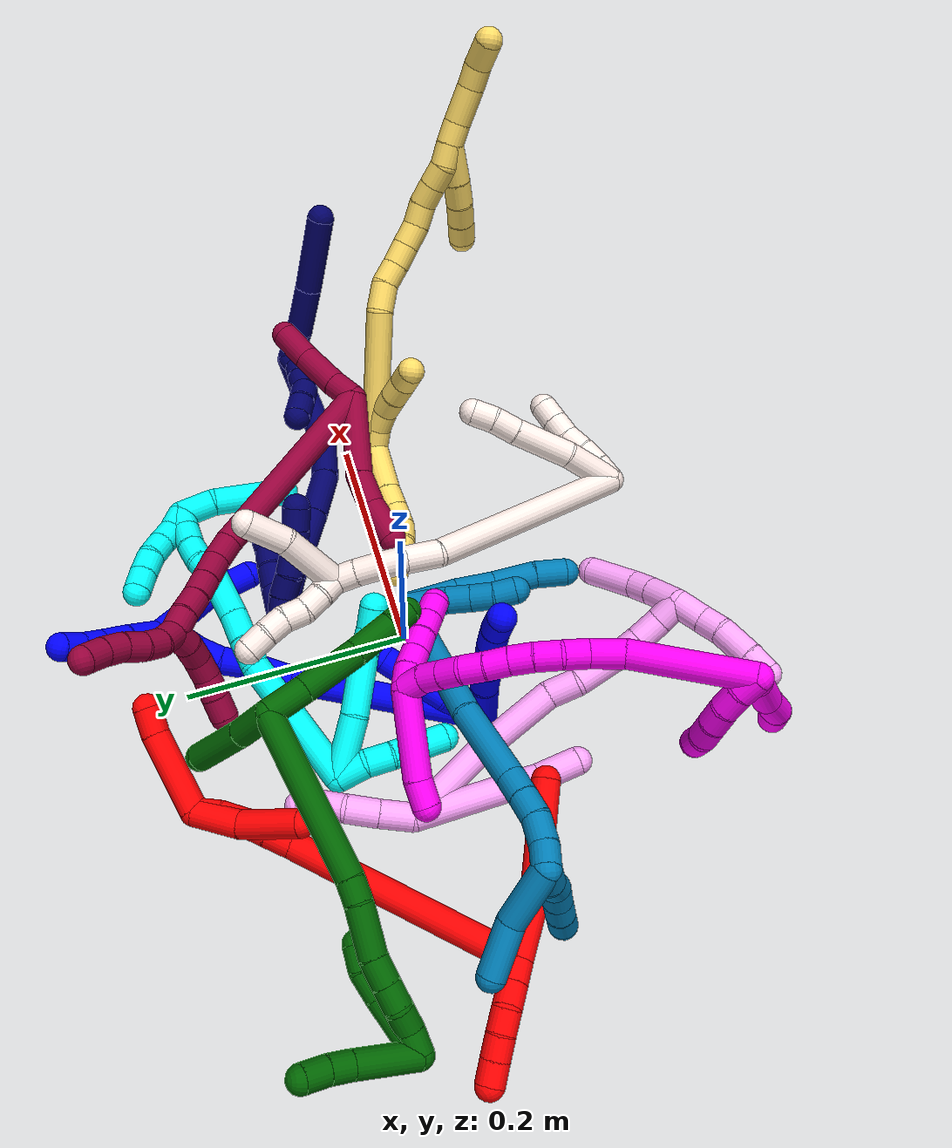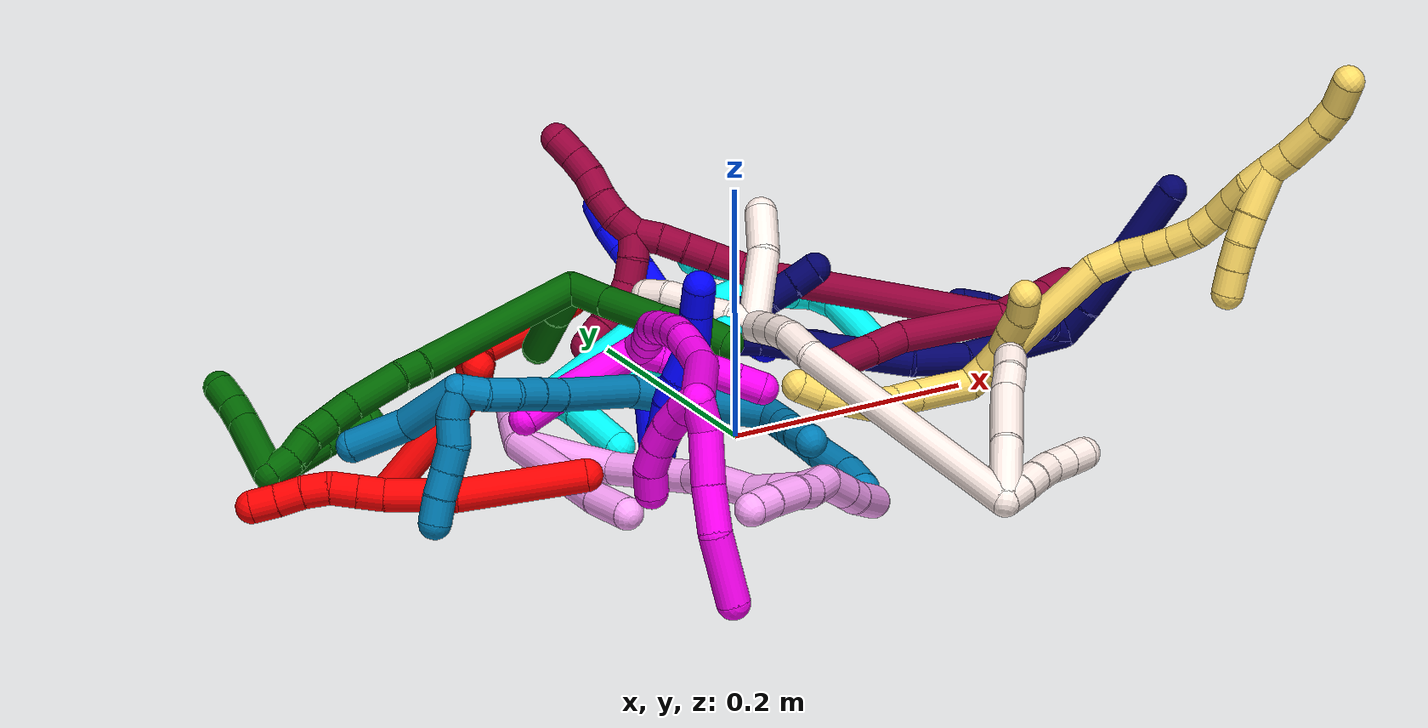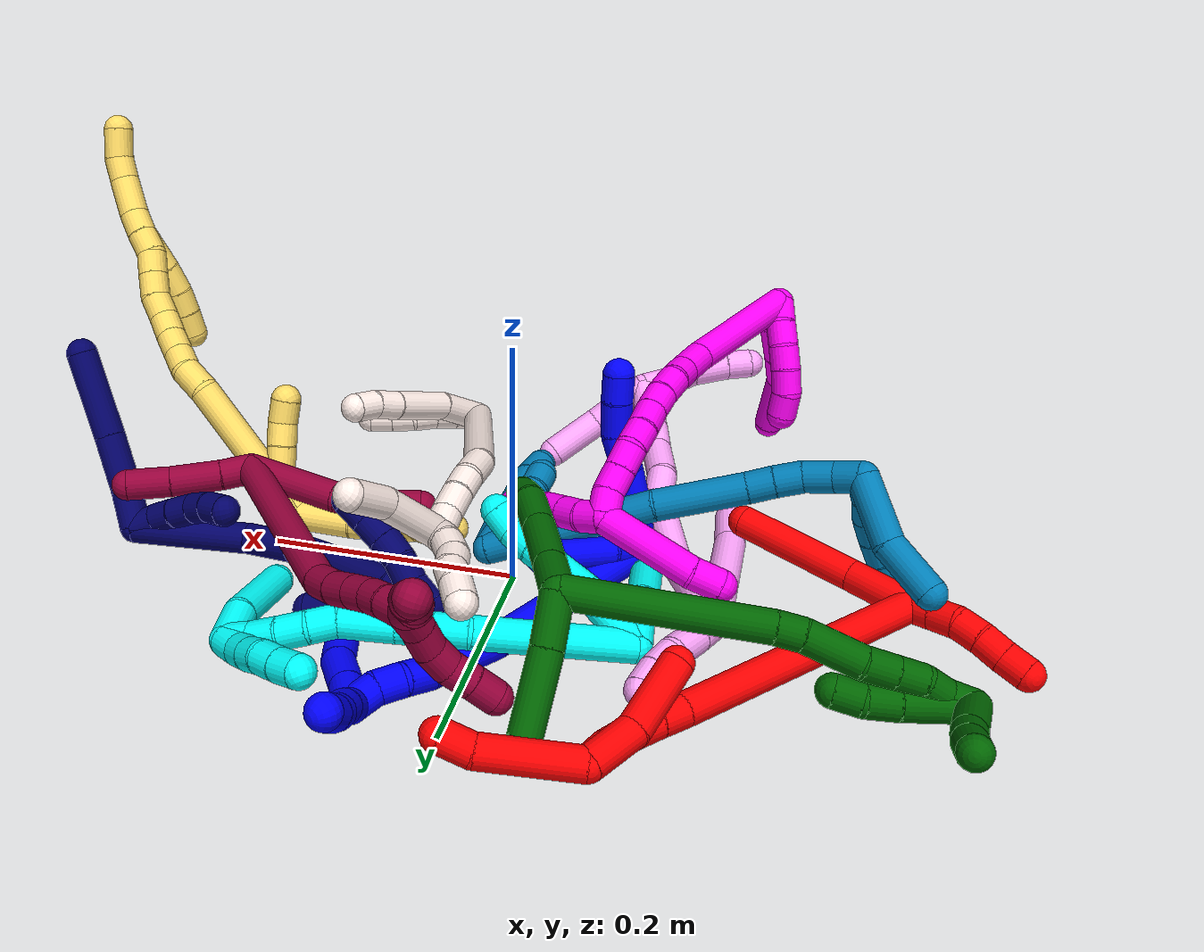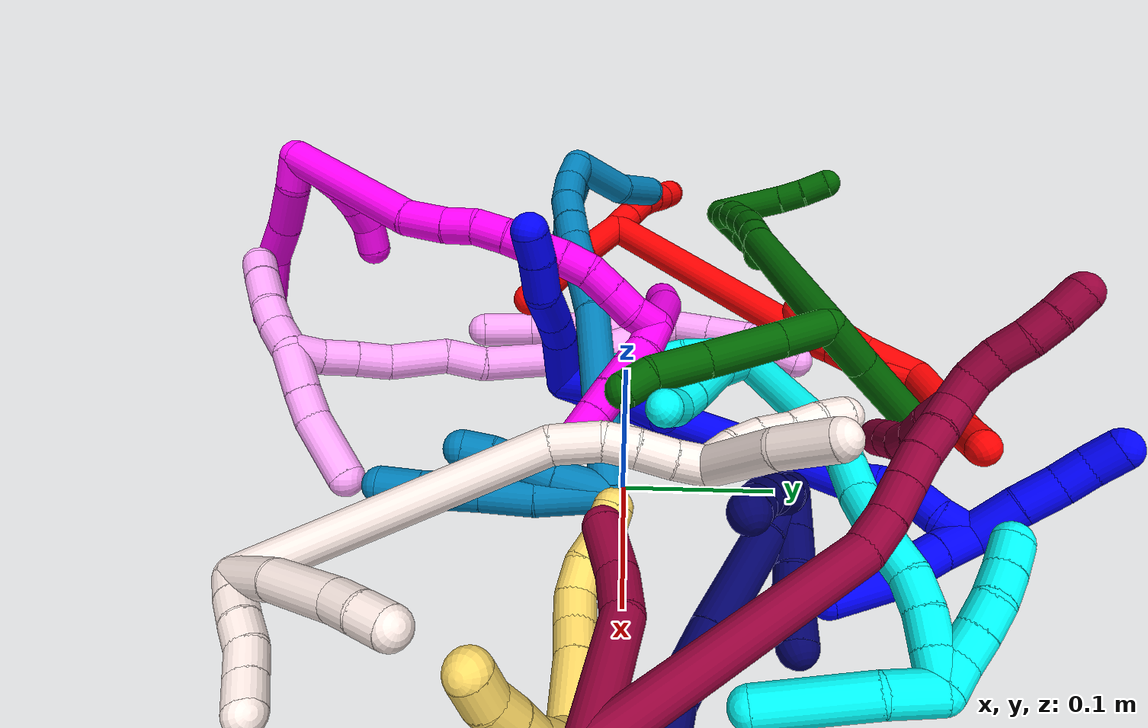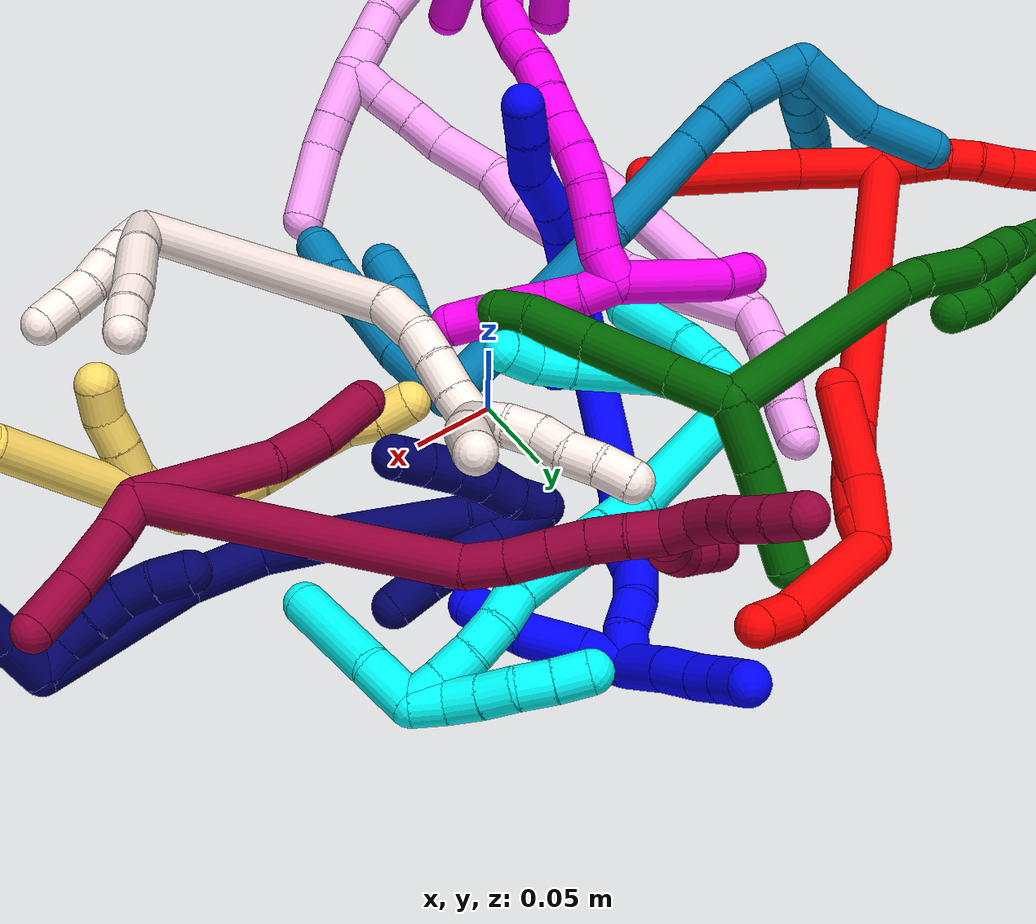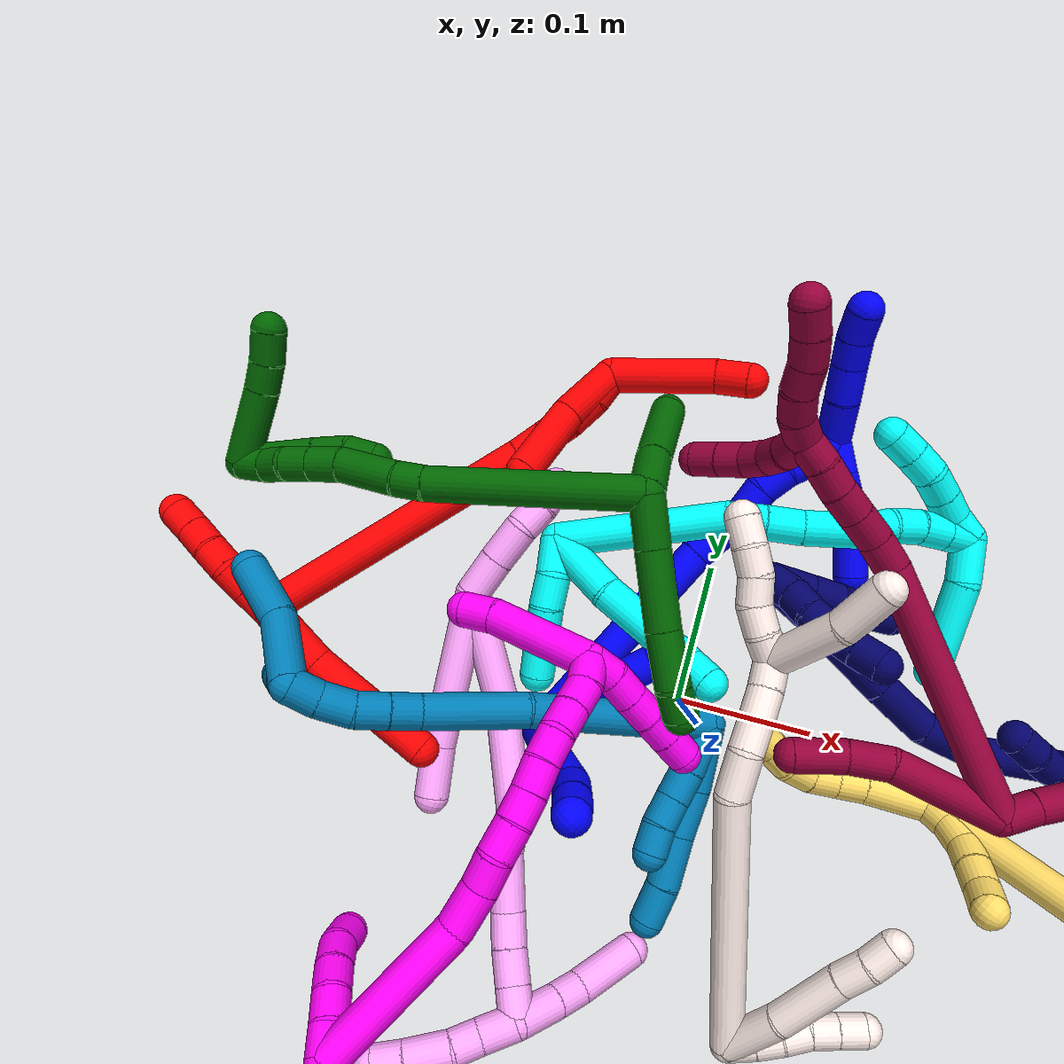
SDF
<sdf version="1.7">
 <world name="default">
  <plugin name="TubeGeneratorPlugin" filename="libtube_generator_plugin.so"/>
  <model name="photoneo_s_sensor">
   <static>1</static>
   <pose>0 0 2 1.57079 1.57079 3.14159</pose>
   <link name="link">
    <inertial><mass>0.1</mass></inertial>
    <sensor name="sensor" type="depth">
     <update_rate>30</update_rate>
     <camera>
      <horizontal_fov>1.22</horizontal_fov>
      <image><width>1920</width><height>1200</height><format>B8G8R8</format></image>
      <clip><near>0.1</near><far>4</far></clip>
      <depth_camera><output>points</output></depth_camera>
     </camera>
     <plugin name="camera_plugin" filename="libgazebo_ros_depth_camera.so">
      <baseline>0.2</baseline>
      <alwaysOn>1</alwaysOn>
      <updateRate>0.0</updateRate>
      <cameraName>camera_ir</cameraName>
      <imageTopicName>/camera/color/image_raw</imageTopicName>
      <cameraInfoTopicName>/camera/color/camera_info</cameraInfoTopicName>
      <depthImageTopicName>/camera/depth/image_raw</depthImageTopicName>
      <depthImageCameraInfoTopicName>/camera/depth/camera_info</depthImageCameraInfoTopicName>
      <pointCloudTopicName>/camera/depth/points</pointCloudTopicName>
      <frameName>fr_optical</frameName>
      <pointCloudCutoff>0.1</pointCloudCutoff>
      <pointCloudCutoffMax>2.0</pointCloudCutoffMax>
      <distortionK1>0</distortionK1>
      <distortionK2>0</distortionK2>
      <distortionK3>0</distortionK3>
      <distortionT1>0</distortionT1>
      <distortionT2>0</distortionT2>
      <CxPrime>0</CxPrime>
      <Cx>0</Cx>
      <Cy>0</Cy>
      <focalLength>0</focalLength>
      <hackBaseline>0</hackBaseline>
     </plugin>
    </sensor>
   </link>
  </model>
  <gravity>0 0 -9.8</gravity>
  <magnetic_field>6e-06 2.3e-05 -4.2e-05</magnetic_field>
  <atmosphere type="adiabatic"/>
  <physics name="default_physics" default="0" type="ode">
   <max_step_size>0.003</max_step_size>
   <real_time_factor>1</real_time_factor>
   <real_time_update_rate>1000</real_time_update_rate>
   <max_contacts>10000</max_contacts>
   <ode>
    <solver>
     <type>quick</type>
     <iters>100</iters>
     <sor>1.3</sor>
     <use_dynamic_moi_rescaling>0</use_dynamic_moi_rescaling>
    </solver>
    <constraints>
     <contact_max_correcting_vel>0</contact_max_correcting_vel>
     <contact_surface_layer>0.001</contact_surface_layer>
     <cfm>0</cfm>
     <erp>0.2</erp>
    </constraints>
   </ode>
  </physics>
  <scene><ambient>0.4 0.4 0.4 1</ambient><background>0.7 0.7 0.7 1</background><shadows>0</shadows></scene>
  <audio><device>default</device></audio>
  <spherical_coordinates>
   <surface_model>EARTH_WGS84</surface_model>
   <latitude_deg>0</latitude_deg>
   <longitude_deg>0</longitude_deg>
   <elevation>0</elevation>
   <heading_deg>0</heading_deg>
  </spherical_coordinates>
  <model name="bin">
   <static>1</static>
   <link name="bottom">
    <collision name="collision-bottom">
     <pose>0 0 -0.01 0 -0 0</pose>
     <geometry><box><size>0.8 0.6 0.02</size></box></geometry>
     <surface>
      <friction><ode><mu>100</mu><mu2>100</mu2></ode></friction>
      <contact><collide_bitmask>65535</collide_bitmask></contact>
     </surface>
    </collision>
   </link>
   <link name="west_wall">
    <collision name="collision-west_wall">
     <pose>-0.41 0 0.1 0 -0 0</pose>
     <geometry><box><size>0.02 0.6 0.2</size></box></geometry>
     <surface>
      <friction><ode><mu>100</mu><mu2>100</mu2></ode></friction>
      <contact><collide_bitmask>65535</collide_bitmask></contact>
     </surface>
    </collision>
   </link>
   <link name="east_wall">
    <collision name="collision-east_wall">
     <pose>0.41 0 0.1 0 -0 0</pose>
     <geometry><box><size>0.02 0.6 0.2</size></box></geometry>
     <surface>
      <friction><ode><mu>100</mu><mu2>100</mu2></ode></friction>
      <contact><collide_bitmask>65535</collide_bitmask></contact>
     </surface>
    </collision>
   </link>
   <link name="south_wall">
    <collision name="collision-south_wall">
     <pose>0 -0.31 0.1 0 -0 0</pose>
     <geometry><box><size>0.8 0.02 0.2</size></box></geometry>
     <surface>
      <friction><ode><mu>100</mu><mu2>100</mu2></ode></friction>
      <contact><collide_bitmask>65535</collide_bitmask></contact>
     </surface>
    </collision>
   </link>
   <link name="north_wall">
    <collision name="collision-north_wall">
     <pose>0 0.31 0.1 0 -0 0</pose>
     <geometry><box><size>0.8 0.02 0.2</size></box></geometry>
     <surface>
      <friction><ode><mu>100</mu><mu2>100</mu2></ode></friction>
      <contact><collide_bitmask>65535</collide_bitmask></contact>
     </surface>
    </collision>
   </link>
  </model>
  <model name="1">
   <static>0</static>
   <link name="1">
    <collision name="collision-cylinder-e_1_2_8">
     <pose>0.016855 -0.018156 0.003012 1.40642 0.741497 0.636694</pose>
     <geometry><cylinder><radius>0.0125</radius><length>0.049912</length></cylinder></geometry>
     <surface>
      <friction><ode><mu>1.16</mu><mu2>1.16</mu2><slip1>0</slip1><slip2>0</slip2></ode></friction>
      <contact><ode><kp>1e+06</kp><kd>1</kd><max_vel>0</max_vel><min_depth>0.001</min_depth></ode></contact>
     </surface>
    </collision>
    <visual name="visual-cylinder-e_1_2_8">
     <pose>0.016855 -0.018156 0.003012 1.40642 0.741497 0.636694</pose>
     <geometry><cylinder><radius>0.0125</radius><length>0.049912</length></cylinder></geometry>
     <material><ambient>0 0 1 1</ambient></material>
    </visual>
    <collision name="collision-cylinder-e_2_8_9">
     <pose>0.041869 -0.042771 0.00662 1.47871 0.89908 0.828987</pose>
     <geometry><cylinder><radius>0.0125</radius><length>0.020847</length></cylinder></geometry>
     <surface>
      <friction><ode><mu>1.16</mu><mu2>1.16</mu2><slip1>0</slip1><slip2>0</slip2></ode></friction>
      <contact><ode><kp>1e+06</kp><kd>1</kd><max_vel>0</max_vel><min_depth>0.001</min_depth></ode></contact>
     </surface>
    </collision>
    <visual name="visual-cylinder-e_2_8_9">
     <pose>0.041869 -0.042771 0.00662 1.47871 0.89908 0.828987</pose>
     <geometry><cylinder><radius>0.0125</radius><length>0.020847</length></cylinder></geometry>
     <material><ambient>0 0 1 1</ambient></material>
    </visual>
    <collision name="collision-cylinder-e_3_9_10">
     <pose>0.062652 -0.057493 0.008253 1.44601 0.987653 0.886909</pose>
     <geometry><cylinder><radius>0.0125</radius><length>0.030246</length></cylinder></geometry>
     <surface>
      <friction><ode><mu>1.16</mu><mu2>1.16</mu2><slip1>0</slip1><slip2>0</slip2></ode></friction>
      <contact><ode><kp>1e+06</kp><kd>1</kd><max_vel>0</max_vel><min_depth>0.001</min_depth></ode></contact>
     </surface>
    </collision>
    <visual name="visual-cylinder-e_3_9_10">
     <pose>0.062652 -0.057493 0.008253 1.44601 0.987653 0.886909</pose>
     <geometry><cylinder><radius>0.0125</radius><length>0.030246</length></cylinder></geometry>
     <material><ambient>0 0 1 1</ambient></material>
    </visual>
    <collision name="collision-cylinder-e_4_10_11">
     <pose>0.08362 -0.076771 0.009444 1.55672 0.648245 0.639794</pose>
     <geometry><cylinder><radius>0.0125</radius><length>0.02764</length></cylinder></geometry>
     <surface>
      <friction><ode><mu>1.16</mu><mu2>1.16</mu2><slip1>0</slip1><slip2>0</slip2></ode></friction>
      <contact><ode><kp>1e+06</kp><kd>1</kd><max_vel>0</max_vel><min_depth>0.001</min_depth></ode></contact>
     </surface>
    </collision>
    <visual name="visual-cylinder-e_4_10_11">
     <pose>0.08362 -0.076771 0.009444 1.55672 0.648245 0.639794</pose>
     <geometry><cylinder><radius>0.0125</radius><length>0.02764</length></cylinder></geometry>
     <material><ambient>0 0 1 1</ambient></material>
    </visual>
    <collision name="collision-cylinder-e_5_11_6">
     <pose>0.098564 -0.096124 0.008625 1.68717 0.666314 0.741743</pose>
     <geometry><cylinder><radius>0.0125</radius><length>0.021355</length></cylinder></geometry>
     <surface>
      <friction><ode><mu>1.16</mu><mu2>1.16</mu2><slip1>0</slip1><slip2>0</slip2></ode></friction>
      <contact><ode><kp>1e+06</kp><kd>1</kd><max_vel>0</max_vel><min_depth>0.001</min_depth></ode></contact>
     </surface>
    </collision>
    <visual name="visual-cylinder-e_5_11_6">
     <pose>0.098564 -0.096124 0.008625 1.68717 0.666314 0.741743</pose>
     <geometry><cylinder><radius>0.0125</radius><length>0.021355</length></cylinder></geometry>
     <material><ambient>0 0 1 1</ambient></material>
    </visual>
    <collision name="collision-cylinder-e_1_2_12">
     <pose>0.00453 -0.003107 0.017824 0.172567 0.24535 0.021329</pose>
     <geometry><cylinder><radius>0.0125</radius><length>0.037302</length></cylinder></geometry>
     <surface>
      <friction><ode><mu>1.16</mu><mu2>1.16</mu2><slip1>0</slip1><slip2>0</slip2></ode></friction>
      <contact><ode><kp>1e+06</kp><kd>1</kd><max_vel>0</max_vel><min_depth>0.001</min_depth></ode></contact>
     </surface>
    </collision>
    <visual name="visual-cylinder-e_1_2_12">
     <pose>0.00453 -0.003107 0.017824 0.172567 0.24535 0.021329</pose>
     <geometry><cylinder><radius>0.0125</radius><length>0.037302</length></cylinder></geometry>
     <material><ambient>0 0 1 1</ambient></material>
    </visual>
    <collision name="collision-cylinder-e_2_12_5">
     <pose>0.019608 -0.005213 0.065152 -0.033875 0.343135 -0.00587</pose>
     <geometry><cylinder><radius>0.0125</radius><length>0.062698</length></cylinder></geometry>
     <surface>
      <friction><ode><mu>1.16</mu><mu2>1.16</mu2><slip1>0</slip1><slip2>0</slip2></ode></friction>
      <contact><ode><kp>1e+06</kp><kd>1</kd><max_vel>0</max_vel><min_depth>0.001</min_depth></ode></contact>
     </surface>
    </collision>
    <visual name="visual-cylinder-e_2_12_5">
     <pose>0.019608 -0.005213 0.065152 -0.033875 0.343135 -0.00587</pose>
     <geometry><cylinder><radius>0.0125</radius><length>0.062698</length></cylinder></geometry>
     <material><ambient>0 0 1 1</ambient></material>
    </visual>
    <collision name="collision-cylinder-e_1_2_13">
     <pose>-0.004296 0.003054 0.085217 -0.035822 -0.050338 0.000902</pose>
     <geometry><cylinder><radius>0.0125</radius><length>0.17076</length></cylinder></geometry>
     <surface>
      <friction><ode><mu>1.16</mu><mu2>1.16</mu2><slip1>0</slip1><slip2>0</slip2></ode></friction>
      <contact><ode><kp>1e+06</kp><kd>1</kd><max_vel>0</max_vel><min_depth>0.001</min_depth></ode></contact>
     </surface>
    </collision>
    <visual name="visual-cylinder-e_1_2_13">
     <pose>-0.004296 0.003054 0.085217 -0.035822 -0.050338 0.000902</pose>
     <geometry><cylinder><radius>0.0125</radius><length>0.17076</length></cylinder></geometry>
     <material><ambient>0 0 1 1</ambient></material>
    </visual>
    <collision name="collision-cylinder-e_2_13_14">
     <pose>-0.006821 0.006993 0.19307 -0.039078 0.078041 -0.001526</pose>
     <geometry><cylinder><radius>0.0125</radius><length>0.045445</length></cylinder></geometry>
     <surface>
      <friction><ode><mu>1.16</mu><mu2>1.16</mu2><slip1>0</slip1><slip2>0</slip2></ode></friction>
      <contact><ode><kp>1e+06</kp><kd>1</kd><max_vel>0</max_vel><min_depth>0.001</min_depth></ode></contact>
     </surface>
    </collision>
    <visual name="visual-cylinder-e_2_13_14">
     <pose>-0.006821 0.006993 0.19307 -0.039078 0.078041 -0.001526</pose>
     <geometry><cylinder><radius>0.0125</radius><length>0.045445</length></cylinder></geometry>
     <material><ambient>0 0 1 1</ambient></material>
    </visual>
    <collision name="collision-cylinder-e_3_14_15">
     <pose>-0.005391 0.005863 0.225787 0.197281 -0.033285 -0.003294</pose>
     <geometry><cylinder><radius>0.0125</radius><length>0.020572</length></cylinder></geometry>
     <surface>
      <friction><ode><mu>1.16</mu><mu2>1.16</mu2><slip1>0</slip1><slip2>0</slip2></ode></friction>
      <contact><ode><kp>1e+06</kp><kd>1</kd><max_vel>0</max_vel><min_depth>0.001</min_depth></ode></contact>
     </surface>
    </collision>
    <visual name="visual-cylinder-e_3_14_15">
     <pose>-0.005391 0.005863 0.225787 0.197281 -0.033285 -0.003294</pose>
     <geometry><cylinder><radius>0.0125</radius><length>0.020572</length></cylinder></geometry>
     <material><ambient>0 0 1 1</ambient></material>
    </visual>
    <collision name="collision-cylinder-e_4_15_16">
     <pose>-0.003542 0.003783 0.24668 0.006063 0.199971 0.000608</pose>
     <geometry><cylinder><radius>0.0125</radius><length>0.022064</length></cylinder></geometry>
     <surface>
      <friction><ode><mu>1.16</mu><mu2>1.16</mu2><slip1>0</slip1><slip2>0</slip2></ode></friction>
      <contact><ode><kp>1e+06</kp><kd>1</kd><max_vel>0</max_vel><min_depth>0.001</min_depth></ode></contact>
     </surface>
    </collision>
    <visual name="visual-cylinder-e_4_15_16">
     <pose>-0.003542 0.003783 0.24668 0.006063 0.199971 0.000608</pose>
     <geometry><cylinder><radius>0.0125</radius><length>0.022064</length></cylinder></geometry>
     <material><ambient>0 0 1 1</ambient></material>
    </visual>
    <collision name="collision-cylinder-e_5_16_17">
     <pose>0.001291 0.00702 0.266779 -0.341723 0.261817 -0.045427</pose>
     <geometry><cylinder><radius>0.0125</radius><length>0.02041</length></cylinder></geometry>
     <surface>
      <friction><ode><mu>1.16</mu><mu2>1.16</mu2><slip1>0</slip1><slip2>0</slip2></ode></friction>
      <contact><ode><kp>1e+06</kp><kd>1</kd><max_vel>0</max_vel><min_depth>0.001</min_depth></ode></contact>
     </surface>
    </collision>
    <visual name="visual-cylinder-e_5_16_17">
     <pose>0.001291 0.00702 0.266779 -0.341723 0.261817 -0.045427</pose>
     <geometry><cylinder><radius>0.0125</radius><length>0.02041</length></cylinder></geometry>
     <material><ambient>0 0 1 1</ambient></material>
    </visual>
    <collision name="collision-cylinder-e_6_17_1">
     <pose>0.00315 0.01317 0.286013 -0.278694 -0.075445 0.010587</pose>
     <geometry><cylinder><radius>0.0125</radius><length>0.020749</length></cylinder></geometry>
     <surface>
      <friction><ode><mu>1.16</mu><mu2>1.16</mu2><slip1>0</slip1><slip2>0</slip2></ode></friction>
      <contact><ode><kp>1e+06</kp><kd>1</kd><max_vel>0</max_vel><min_depth>0.001</min_depth></ode></contact>
     </surface>
    </collision>
    <visual name="visual-cylinder-e_6_17_1">
     <pose>0.00315 0.01317 0.286013 -0.278694 -0.075445 0.010587</pose>
     <geometry><cylinder><radius>0.0125</radius><length>0.020749</length></cylinder></geometry>
     <material><ambient>0 0 1 1</ambient></material>
    </visual>
    <collision name="collision-cylinder-e_1_1_18">
     <pose>0.010705 0.022219 0.2889 -2.42054 0.725658 -1.57776</pose>
     <geometry><cylinder><radius>0.0125</radius><length>0.025124</length></cylinder></geometry>
     <surface>
      <friction><ode><mu>1.16</mu><mu2>1.16</mu2><slip1>0</slip1><slip2>0</slip2></ode></friction>
      <contact><ode><kp>1e+06</kp><kd>1</kd><max_vel>0</max_vel><min_depth>0.001</min_depth></ode></contact>
     </surface>
    </collision>
    <visual name="visual-cylinder-e_1_1_18">
     <pose>0.010705 0.022219 0.2889 -2.42054 0.725658 -1.57776</pose>
     <geometry><cylinder><radius>0.0125</radius><length>0.025124</length></cylinder></geometry>
     <material><ambient>0 0 1 1</ambient></material>
    </visual>
    <collision name="collision-cylinder-e_2_18_19">
     <pose>0.03074 0.037742 0.272841 -2.33882 0.734479 -1.47265</pose>
     <geometry><cylinder><radius>0.0125</radius><length>0.034912</length></cylinder></geometry>
     <surface>
      <friction><ode><mu>1.16</mu><mu2>1.16</mu2><slip1>0</slip1><slip2>0</slip2></ode></friction>
      <contact><ode><kp>1e+06</kp><kd>1</kd><max_vel>0</max_vel><min_depth>0.001</min_depth></ode></contact>
     </surface>
    </collision>
    <visual name="visual-cylinder-e_2_18_19">
     <pose>0.03074 0.037742 0.272841 -2.33882 0.734479 -1.47265</pose>
     <geometry><cylinder><radius>0.0125</radius><length>0.034912</length></cylinder></geometry>
     <material><ambient>0 0 1 1</ambient></material>
    </visual>
    <collision name="collision-cylinder-e_3_19_4">
     <pose>0.053186 0.056013 0.24957 -2.58131 0.567838 -1.58493</pose>
     <geometry><cylinder><radius>0.0125</radius><length>0.039964</length></cylinder></geometry>
     <surface>
      <friction><ode><mu>1.16</mu><mu2>1.16</mu2><slip1>0</slip1><slip2>0</slip2></ode></friction>
      <contact><ode><kp>1e+06</kp><kd>1</kd><max_vel>0</max_vel><min_depth>0.001</min_depth></ode></contact>
     </surface>
    </collision>
    <visual name="visual-cylinder-e_3_19_4">
     <pose>0.053186 0.056013 0.24957 -2.58131 0.567838 -1.58493</pose>
     <geometry><cylinder><radius>0.0125</radius><length>0.039964</length></cylinder></geometry>
     <material><ambient>0 0 1 1</ambient></material>
    </visual>
    <collision name="collision-cylinder-e_1_1_20">
     <pose>0.000153 0.003312 0.306762 0.866028 -0.132046 -0.061111</pose>
     <geometry><cylinder><radius>0.0125</radius><length>0.033646</length></cylinder></geometry>
     <surface>
      <friction><ode><mu>1.16</mu><mu2>1.16</mu2><slip1>0</slip1><slip2>0</slip2></ode></friction>
      <contact><ode><kp>1e+06</kp><kd>1</kd><max_vel>0</max_vel><min_depth>0.001</min_depth></ode></contact>
     </surface>
    </collision>
    <visual name="visual-cylinder-e_1_1_20">
     <pose>0.000153 0.003312 0.306762 0.866028 -0.132046 -0.061111</pose>
     <geometry><cylinder><radius>0.0125</radius><length>0.033646</length></cylinder></geometry>
     <material><ambient>0 0 1 1</ambient></material>
    </visual>
    <collision name="collision-cylinder-e_2_20_21">
     <pose>-0.004733 -0.018431 0.326458 0.793641 -0.207674 -0.087284</pose>
     <geometry><cylinder><radius>0.0125</radius><length>0.025916</length></cylinder></geometry>
     <surface>
      <friction><ode><mu>1.16</mu><mu2>1.16</mu2><slip1>0</slip1><slip2>0</slip2></ode></friction>
      <contact><ode><kp>1e+06</kp><kd>1</kd><max_vel>0</max_vel><min_depth>0.001</min_depth></ode></contact>
     </surface>
    </collision>
    <visual name="visual-cylinder-e_2_20_21">
     <pose>-0.004733 -0.018431 0.326458 0.793641 -0.207674 -0.087284</pose>
     <geometry><cylinder><radius>0.0125</radius><length>0.025916</length></cylinder></geometry>
     <material><ambient>0 0 1 1</ambient></material>
    </visual>
    <collision name="collision-cylinder-e_3_21_22">
     <pose>-0.008873 -0.034991 0.341779 0.863458 -0.147322 -0.067971</pose>
     <geometry><cylinder><radius>0.0125</radius><length>0.020004</length></cylinder></geometry>
     <surface>
      <friction><ode><mu>1.16</mu><mu2>1.16</mu2><slip1>0</slip1><slip2>0</slip2></ode></friction>
      <contact><ode><kp>1e+06</kp><kd>1</kd><max_vel>0</max_vel><min_depth>0.001</min_depth></ode></contact>
     </surface>
    </collision>
    <visual name="visual-cylinder-e_3_21_22">
     <pose>-0.008873 -0.034991 0.341779 0.863458 -0.147322 -0.067971</pose>
     <geometry><cylinder><radius>0.0125</radius><length>0.020004</length></cylinder></geometry>
     <material><ambient>0 0 1 1</ambient></material>
    </visual>
    <collision name="collision-cylinder-e_4_22_3">
     <pose>-0.010557 -0.049954 0.355203 0.816401 -0.021048 -0.009103</pose>
     <geometry><cylinder><radius>0.0125</radius><length>0.020434</length></cylinder></geometry>
     <surface>
      <friction><ode><mu>1.16</mu><mu2>1.16</mu2><slip1>0</slip1><slip2>0</slip2></ode></friction>
      <contact><ode><kp>1e+06</kp><kd>1</kd><max_vel>0</max_vel><min_depth>0.001</min_depth></ode></contact>
     </surface>
    </collision>
    <visual name="visual-cylinder-e_4_22_3">
     <pose>-0.010557 -0.049954 0.355203 0.816401 -0.021048 -0.009103</pose>
     <geometry><cylinder><radius>0.0125</radius><length>0.020434</length></cylinder></geometry>
     <material><ambient>0 0 1 1</ambient></material>
    </visual>
    <collision name="collision-sphere-3">
     <pose>-0.010772 -0.057397 0.362199 0 -0 0</pose>
     <geometry><sphere><radius>0.0125</radius></sphere></geometry>
     <surface>
      <friction><ode><mu>1.16</mu><mu2>1.16</mu2><slip1>0</slip1><slip2>0</slip2></ode></friction>
      <contact><ode><kp>1e+06</kp><kd>1</kd><max_vel>0</max_vel><min_depth>0.001</min_depth></ode></contact>
     </surface>
    </collision>
    <visual name="visual-sphere-3">
     <pose>-0.010772 -0.057397 0.362199 0 -0 0</pose>
     <geometry><sphere><radius>0.0125</radius></sphere></geometry>
     <material><ambient>0 0 1 1</ambient></material>
    </visual>
    <collision name="collision-sphere-22">
     <pose>-0.010342 -0.042511 0.348208 0 -0 0</pose>
     <geometry><sphere><radius>0.0125</radius></sphere></geometry>
     <surface>
      <friction><ode><mu>1.16</mu><mu2>1.16</mu2><slip1>0</slip1><slip2>0</slip2></ode></friction>
      <contact><ode><kp>1e+06</kp><kd>1</kd><max_vel>0</max_vel><min_depth>0.001</min_depth></ode></contact>
     </surface>
    </collision>
    <visual name="visual-sphere-22">
     <pose>-0.010342 -0.042511 0.348208 0 -0 0</pose>
     <geometry><sphere><radius>0.0125</radius></sphere></geometry>
     <material><ambient>0 0 1 1</ambient></material>
    </visual>
    <collision name="collision-sphere-21">
     <pose>-0.007405 -0.027471 0.33535 0 -0 0</pose>
     <geometry><sphere><radius>0.0125</radius></sphere></geometry>
     <surface>
      <friction><ode><mu>1.16</mu><mu2>1.16</mu2><slip1>0</slip1><slip2>0</slip2></ode></friction>
      <contact><ode><kp>1e+06</kp><kd>1</kd><max_vel>0</max_vel><min_depth>0.001</min_depth></ode></contact>
     </surface>
    </collision>
    <visual name="visual-sphere-21">
     <pose>-0.007405 -0.027471 0.33535 0 -0 0</pose>
     <geometry><sphere><radius>0.0125</radius></sphere></geometry>
     <material><ambient>0 0 1 1</ambient></material>
    </visual>
    <collision name="collision-sphere-20">
     <pose>-0.002062 -0.009391 0.317566 0 -0 0</pose>
     <geometry><sphere><radius>0.0125</radius></sphere></geometry>
     <surface>
      <friction><ode><mu>1.16</mu><mu2>1.16</mu2><slip1>0</slip1><slip2>0</slip2></ode></friction>
      <contact><ode><kp>1e+06</kp><kd>1</kd><max_vel>0</max_vel><min_depth>0.001</min_depth></ode></contact>
     </surface>
    </collision>
    <visual name="visual-sphere-20">
     <pose>-0.002062 -0.009391 0.317566 0 -0 0</pose>
     <geometry><sphere><radius>0.0125</radius></sphere></geometry>
     <material><ambient>0 0 1 1</ambient></material>
    </visual>
    <collision name="collision-sphere-4">
     <pose>0.063932 0.064965 0.2353 0 -0 0</pose>
     <geometry><sphere><radius>0.0125</radius></sphere></geometry>
     <surface>
      <friction><ode><mu>1.16</mu><mu2>1.16</mu2><slip1>0</slip1><slip2>0</slip2></ode></friction>
      <contact><ode><kp>1e+06</kp><kd>1</kd><max_vel>0</max_vel><min_depth>0.001</min_depth></ode></contact>
     </surface>
    </collision>
    <visual name="visual-sphere-4">
     <pose>0.063932 0.064965 0.2353 0 -0 0</pose>
     <geometry><sphere><radius>0.0125</radius></sphere></geometry>
     <material><ambient>0 0 1 1</ambient></material>
    </visual>
    <collision name="collision-sphere-6">
     <pose>0.105164 -0.104461 0.00765 0 -0 0</pose>
     <geometry><sphere><radius>0.0125</radius></sphere></geometry>
     <surface>
      <friction><ode><mu>1.16</mu><mu2>1.16</mu2><slip1>0</slip1><slip2>0</slip2></ode></friction>
      <contact><ode><kp>1e+06</kp><kd>1</kd><max_vel>0</max_vel><min_depth>0.001</min_depth></ode></contact>
     </surface>
    </collision>
    <visual name="visual-sphere-6">
     <pose>0.105164 -0.104461 0.00765 0 -0 0</pose>
     <geometry><sphere><radius>0.0125</radius></sphere></geometry>
     <material><ambient>0 0 1 1</ambient></material>
    </visual>
    <collision name="collision-sphere-11">
     <pose>0.091964 -0.087787 0.009599 0 -0 0</pose>
     <geometry><sphere><radius>0.0125</radius></sphere></geometry>
     <surface>
      <friction><ode><mu>1.16</mu><mu2>1.16</mu2><slip1>0</slip1><slip2>0</slip2></ode></friction>
      <contact><ode><kp>1e+06</kp><kd>1</kd><max_vel>0</max_vel><min_depth>0.001</min_depth></ode></contact>
     </surface>
    </collision>
    <visual name="visual-sphere-11">
     <pose>0.091964 -0.087787 0.009599 0 -0 0</pose>
     <geometry><sphere><radius>0.0125</radius></sphere></geometry>
     <material><ambient>0 0 1 1</ambient></material>
    </visual>
    <collision name="collision-sphere-10">
     <pose>0.075275 -0.065756 0.009289 0 -0 0</pose>
     <geometry><sphere><radius>0.0125</radius></sphere></geometry>
     <surface>
      <friction><ode><mu>1.16</mu><mu2>1.16</mu2><slip1>0</slip1><slip2>0</slip2></ode></friction>
      <contact><ode><kp>1e+06</kp><kd>1</kd><max_vel>0</max_vel><min_depth>0.001</min_depth></ode></contact>
     </surface>
    </collision>
    <visual name="visual-sphere-10">
     <pose>0.075275 -0.065756 0.009289 0 -0 0</pose>
     <geometry><sphere><radius>0.0125</radius></sphere></geometry>
     <material><ambient>0 0 1 1</ambient></material>
    </visual>
    <collision name="collision-sphere-9">
     <pose>0.050028 -0.04923 0.007216 0 -0 0</pose>
     <geometry><sphere><radius>0.0125</radius></sphere></geometry>
     <surface>
      <friction><ode><mu>1.16</mu><mu2>1.16</mu2><slip1>0</slip1><slip2>0</slip2></ode></friction>
      <contact><ode><kp>1e+06</kp><kd>1</kd><max_vel>0</max_vel><min_depth>0.001</min_depth></ode></contact>
     </surface>
    </collision>
    <visual name="visual-sphere-9">
     <pose>0.050028 -0.04923 0.007216 0 -0 0</pose>
     <geometry><sphere><radius>0.0125</radius></sphere></geometry>
     <material><ambient>0 0 1 1</ambient></material>
    </visual>
    <collision name="collision-sphere-2">
     <geometry><sphere><radius>0.0125</radius></sphere></geometry>
     <surface>
      <friction><ode><mu>1.16</mu><mu2>1.16</mu2><slip1>0</slip1><slip2>0</slip2></ode></friction>
      <contact><ode><kp>1e+06</kp><kd>1</kd><max_vel>0</max_vel><min_depth>0.001</min_depth></ode></contact>
     </surface>
    </collision>
    <visual name="visual-sphere-2">
     <geometry><sphere><radius>0.0125</radius></sphere></geometry>
     <material><ambient>0 0 1 1</ambient></material>
    </visual>
    <collision name="collision-sphere-19">
     <pose>0.042439 0.04706 0.263841 0 -0 0</pose>
     <geometry><sphere><radius>0.0125</radius></sphere></geometry>
     <surface>
      <friction><ode><mu>1.16</mu><mu2>1.16</mu2><slip1>0</slip1><slip2>0</slip2></ode></friction>
      <contact><ode><kp>1e+06</kp><kd>1</kd><max_vel>0</max_vel><min_depth>0.001</min_depth></ode></contact>
     </surface>
    </collision>
    <visual name="visual-sphere-19">
     <pose>0.042439 0.04706 0.263841 0 -0 0</pose>
     <geometry><sphere><radius>0.0125</radius></sphere></geometry>
     <material><ambient>0 0 1 1</ambient></material>
    </visual>
    <collision name="collision-sphere-8">
     <pose>0.03371 -0.036312 0.006023 0 -0 0</pose>
     <geometry><sphere><radius>0.0125</radius></sphere></geometry>
     <surface>
      <friction><ode><mu>1.16</mu><mu2>1.16</mu2><slip1>0</slip1><slip2>0</slip2></ode></friction>
      <contact><ode><kp>1e+06</kp><kd>1</kd><max_vel>0</max_vel><min_depth>0.001</min_depth></ode></contact>
     </surface>
    </collision>
    <visual name="visual-sphere-8">
     <pose>0.03371 -0.036312 0.006023 0 -0 0</pose>
     <geometry><sphere><radius>0.0125</radius></sphere></geometry>
     <material><ambient>0 0 1 1</ambient></material>
    </visual>
    <collision name="collision-sphere-12">
     <pose>0.00906 -0.006213 0.035647 0 -0 0</pose>
     <geometry><sphere><radius>0.0125</radius></sphere></geometry>
     <surface>
      <friction><ode><mu>1.16</mu><mu2>1.16</mu2><slip1>0</slip1><slip2>0</slip2></ode></friction>
      <contact><ode><kp>1e+06</kp><kd>1</kd><max_vel>0</max_vel><min_depth>0.001</min_depth></ode></contact>
     </surface>
    </collision>
    <visual name="visual-sphere-12">
     <pose>0.00906 -0.006213 0.035647 0 -0 0</pose>
     <geometry><sphere><radius>0.0125</radius></sphere></geometry>
     <material><ambient>0 0 1 1</ambient></material>
    </visual>
    <collision name="collision-sphere-5">
     <pose>0.030155 -0.004214 0.094657 0 -0 0</pose>
     <geometry><sphere><radius>0.0125</radius></sphere></geometry>
     <surface>
      <friction><ode><mu>1.16</mu><mu2>1.16</mu2><slip1>0</slip1><slip2>0</slip2></ode></friction>
      <contact><ode><kp>1e+06</kp><kd>1</kd><max_vel>0</max_vel><min_depth>0.001</min_depth></ode></contact>
     </surface>
    </collision>
    <visual name="visual-sphere-5">
     <pose>0.030155 -0.004214 0.094657 0 -0 0</pose>
     <geometry><sphere><radius>0.0125</radius></sphere></geometry>
     <material><ambient>0 0 1 1</ambient></material>
    </visual>
    <collision name="collision-sphere-13">
     <pose>-0.008592 0.006108 0.170434 0 -0 0</pose>
     <geometry><sphere><radius>0.0125</radius></sphere></geometry>
     <surface>
      <friction><ode><mu>1.16</mu><mu2>1.16</mu2><slip1>0</slip1><slip2>0</slip2></ode></friction>
      <contact><ode><kp>1e+06</kp><kd>1</kd><max_vel>0</max_vel><min_depth>0.001</min_depth></ode></contact>
     </surface>
    </collision>
    <visual name="visual-sphere-13">
     <pose>-0.008592 0.006108 0.170434 0 -0 0</pose>
     <geometry><sphere><radius>0.0125</radius></sphere></geometry>
     <material><ambient>0 0 1 1</ambient></material>
    </visual>
    <collision name="collision-sphere-14">
     <pose>-0.005049 0.007878 0.215706 0 -0 0</pose>
     <geometry><sphere><radius>0.0125</radius></sphere></geometry>
     <surface>
      <friction><ode><mu>1.16</mu><mu2>1.16</mu2><slip1>0</slip1><slip2>0</slip2></ode></friction>
      <contact><ode><kp>1e+06</kp><kd>1</kd><max_vel>0</max_vel><min_depth>0.001</min_depth></ode></contact>
     </surface>
    </collision>
    <visual name="visual-sphere-14">
     <pose>-0.005049 0.007878 0.215706 0 -0 0</pose>
     <geometry><sphere><radius>0.0125</radius></sphere></geometry>
     <material><ambient>0 0 1 1</ambient></material>
    </visual>
    <collision name="collision-sphere-15">
     <pose>-0.005734 0.003848 0.235868 0 -0 0</pose>
     <geometry><sphere><radius>0.0125</radius></sphere></geometry>
     <surface>
      <friction><ode><mu>1.16</mu><mu2>1.16</mu2><slip1>0</slip1><slip2>0</slip2></ode></friction>
      <contact><ode><kp>1e+06</kp><kd>1</kd><max_vel>0</max_vel><min_depth>0.001</min_depth></ode></contact>
     </surface>
    </collision>
    <visual name="visual-sphere-15">
     <pose>-0.005734 0.003848 0.235868 0 -0 0</pose>
     <geometry><sphere><radius>0.0125</radius></sphere></geometry>
     <material><ambient>0 0 1 1</ambient></material>
    </visual>
    <collision name="collision-sphere-16">
     <pose>-0.001351 0.003717 0.257492 0 -0 0</pose>
     <geometry><sphere><radius>0.0125</radius></sphere></geometry>
     <surface>
      <friction><ode><mu>1.16</mu><mu2>1.16</mu2><slip1>0</slip1><slip2>0</slip2></ode></friction>
      <contact><ode><kp>1e+06</kp><kd>1</kd><max_vel>0</max_vel><min_depth>0.001</min_depth></ode></contact>
     </surface>
    </collision>
    <visual name="visual-sphere-16">
     <pose>-0.001351 0.003717 0.257492 0 -0 0</pose>
     <geometry><sphere><radius>0.0125</radius></sphere></geometry>
     <material><ambient>0 0 1 1</ambient></material>
    </visual>
    <collision name="collision-sphere-17">
     <pose>0.003932 0.010324 0.276067 0 -0 0</pose>
     <geometry><sphere><radius>0.0125</radius></sphere></geometry>
     <surface>
      <friction><ode><mu>1.16</mu><mu2>1.16</mu2><slip1>0</slip1><slip2>0</slip2></ode></friction>
      <contact><ode><kp>1e+06</kp><kd>1</kd><max_vel>0</max_vel><min_depth>0.001</min_depth></ode></contact>
     </surface>
    </collision>
    <visual name="visual-sphere-17">
     <pose>0.003932 0.010324 0.276067 0 -0 0</pose>
     <geometry><sphere><radius>0.0125</radius></sphere></geometry>
     <material><ambient>0 0 1 1</ambient></material>
    </visual>
    <collision name="collision-sphere-1">
     <pose>0.002368 0.016015 0.295958 0 -0 0</pose>
     <geometry><sphere><radius>0.0125</radius></sphere></geometry>
     <surface>
      <friction><ode><mu>1.16</mu><mu2>1.16</mu2><slip1>0</slip1><slip2>0</slip2></ode></friction>
      <contact><ode><kp>1e+06</kp><kd>1</kd><max_vel>0</max_vel><min_depth>0.001</min_depth></ode></contact>
     </surface>
    </collision>
    <visual name="visual-sphere-1">
     <pose>0.002368 0.016015 0.295958 0 -0 0</pose>
     <geometry><sphere><radius>0.0125</radius></sphere></geometry>
     <material><ambient>0 0 1 1</ambient></material>
    </visual>
    <collision name="collision-sphere-18">
     <pose>0.019042 0.028423 0.281841 0 -0 0</pose>
     <geometry><sphere><radius>0.0125</radius></sphere></geometry>
     <surface>
      <friction><ode><mu>1.16</mu><mu2>1.16</mu2><slip1>0</slip1><slip2>0</slip2></ode></friction>
      <contact><ode><kp>1e+06</kp><kd>1</kd><max_vel>0</max_vel><min_depth>0.001</min_depth></ode></contact>
     </surface>
    </collision>
    <visual name="visual-sphere-18">
     <pose>0.019042 0.028423 0.281841 0 -0 0</pose>
     <geometry><sphere><radius>0.0125</radius></sphere></geometry>
     <material><ambient>0 0 1 1</ambient></material>
    </visual>
    <inertial>
     <pose>0.014986 -0.006223 0.14688 0 -0 0</pose>
     <mass>0.75</mass>
     <inertia><ixx>0.000499</ixx><ixy>0</ixy><ixz>0</ixz><iyy>0.000478</iyy><iyz>0</iyz><izz>2e-05</izz></inertia>
    </inertial>
   </link>
   <pose>-0.094056 -0.044871 0.012528 -1.47631 -0.567336 -0.548034</pose>
  </model>
  <model name="2">
   <static>0</static>
   <link name="2">
    <collision name="collision-cylinder-e_1_2_8">
     <pose>0.011661 0.008727 -0.022099 -2.7655 0.456244 -1.76838</pose>
     <geometry><cylinder><radius>0.0125</radius><length>0.052934</length></cylinder></geometry>
     <surface>
      <friction><ode><mu>1.16</mu><mu2>1.16</mu2><slip1>0</slip1><slip2>0</slip2></ode></friction>
      <contact><ode><kp>1e+06</kp><kd>1</kd><max_vel>0</max_vel><min_depth>0.001</min_depth></ode></contact>
     </surface>
    </collision>
    <visual name="visual-cylinder-e_1_2_8">
     <pose>0.011661 0.008727 -0.022099 -2.7655 0.456244 -1.76838</pose>
     <geometry><cylinder><radius>0.0125</radius><length>0.052934</length></cylinder></geometry>
     <material><ambient>1 0 0 1</ambient></material>
    </visual>
    <collision name="collision-cylinder-e_2_8_6">
     <pose>0.051147 0.037149 -0.078742 -2.62339 0.610565 -1.74297</pose>
     <geometry><cylinder><radius>0.0125</radius><length>0.097066</length></cylinder></geometry>
     <surface>
      <friction><ode><mu>1.16</mu><mu2>1.16</mu2><slip1>0</slip1><slip2>0</slip2></ode></friction>
      <contact><ode><kp>1e+06</kp><kd>1</kd><max_vel>0</max_vel><min_depth>0.001</min_depth></ode></contact>
     </surface>
    </collision>
    <visual name="visual-cylinder-e_2_8_6">
     <pose>0.051147 0.037149 -0.078742 -2.62339 0.610565 -1.74297</pose>
     <geometry><cylinder><radius>0.0125</radius><length>0.097066</length></cylinder></geometry>
     <material><ambient>1 0 0 1</ambient></material>
    </visual>
    <collision name="collision-cylinder-e_1_2_9">
     <pose>-0.003263 -0.004057 0.008538 0.443621 -0.3324 -0.075625</pose>
     <geometry><cylinder><radius>0.0125</radius><length>0.02</length></cylinder></geometry>
     <surface>
      <friction><ode><mu>1.16</mu><mu2>1.16</mu2><slip1>0</slip1><slip2>0</slip2></ode></friction>
      <contact><ode><kp>1e+06</kp><kd>1</kd><max_vel>0</max_vel><min_depth>0.001</min_depth></ode></contact>
     </surface>
    </collision>
    <visual name="visual-cylinder-e_1_2_9">
     <pose>-0.003263 -0.004057 0.008538 0.443621 -0.3324 -0.075625</pose>
     <geometry><cylinder><radius>0.0125</radius><length>0.02</length></cylinder></geometry>
     <material><ambient>1 0 0 1</ambient></material>
    </visual>
    <collision name="collision-cylinder-e_2_9_10">
     <pose>-0.009788 -0.012127 0.025635 0.438408 -0.332205 -0.074663</pose>
     <geometry><cylinder><radius>0.0125</radius><length>0.02</length></cylinder></geometry>
     <surface>
      <friction><ode><mu>1.16</mu><mu2>1.16</mu2><slip1>0</slip1><slip2>0</slip2></ode></friction>
      <contact><ode><kp>1e+06</kp><kd>1</kd><max_vel>0</max_vel><min_depth>0.001</min_depth></ode></contact>
     </surface>
    </collision>
    <visual name="visual-cylinder-e_2_9_10">
     <pose>-0.009788 -0.012127 0.025635 0.438408 -0.332205 -0.074663</pose>
     <geometry><cylinder><radius>0.0125</radius><length>0.02</length></cylinder></geometry>
     <material><ambient>1 0 0 1</ambient></material>
    </visual>
    <collision name="collision-cylinder-e_3_10_11">
     <pose>-0.018913 -0.01882 0.041838 0.337222 -0.626609 -0.110187</pose>
     <geometry><cylinder><radius>0.0125</radius><length>0.02</length></cylinder></geometry>
     <surface>
      <friction><ode><mu>1.16</mu><mu2>1.16</mu2><slip1>0</slip1><slip2>0</slip2></ode></friction>
      <contact><ode><kp>1e+06</kp><kd>1</kd><max_vel>0</max_vel><min_depth>0.001</min_depth></ode></contact>
     </surface>
    </collision>
    <visual name="visual-cylinder-e_3_10_11">
     <pose>-0.018913 -0.01882 0.041838 0.337222 -0.626609 -0.110187</pose>
     <geometry><cylinder><radius>0.0125</radius><length>0.02</length></cylinder></geometry>
     <material><ambient>1 0 0 1</ambient></material>
    </visual>
    <collision name="collision-cylinder-e_4_11_12">
     <pose>-0.031798 -0.023546 0.056302 0.291454 -0.778385 -0.120237</pose>
     <geometry><cylinder><radius>0.0125</radius><length>0.02</length></cylinder></geometry>
     <surface>
      <friction><ode><mu>1.16</mu><mu2>1.16</mu2><slip1>0</slip1><slip2>0</slip2></ode></friction>
      <contact><ode><kp>1e+06</kp><kd>1</kd><max_vel>0</max_vel><min_depth>0.001</min_depth></ode></contact>
     </surface>
    </collision>
    <visual name="visual-cylinder-e_4_11_12">
     <pose>-0.031798 -0.023546 0.056302 0.291454 -0.778385 -0.120237</pose>
     <geometry><cylinder><radius>0.0125</radius><length>0.02</length></cylinder></geometry>
     <material><ambient>1 0 0 1</ambient></material>
    </visual>
    <collision name="collision-cylinder-e_5_12_5">
     <pose>-0.04538 -0.028112 0.070236 0.340363 -0.715625 -0.128331</pose>
     <geometry><cylinder><radius>0.0125</radius><length>0.02</length></cylinder></geometry>
     <surface>
      <friction><ode><mu>1.16</mu><mu2>1.16</mu2><slip1>0</slip1><slip2>0</slip2></ode></friction>
      <contact><ode><kp>1e+06</kp><kd>1</kd><max_vel>0</max_vel><min_depth>0.001</min_depth></ode></contact>
     </surface>
    </collision>
    <visual name="visual-cylinder-e_5_12_5">
     <pose>-0.04538 -0.028112 0.070236 0.340363 -0.715625 -0.128331</pose>
     <geometry><cylinder><radius>0.0125</radius><length>0.02</length></cylinder></geometry>
     <material><ambient>1 0 0 1</ambient></material>
    </visual>
    <collision name="collision-cylinder-e_1_2_13">
     <pose>0.033182 0.095017 0.030866 -1.2567 0.320673 -0.233943</pose>
     <geometry><cylinder><radius>0.0125</radius><length>0.210542</length></cylinder></geometry>
     <surface>
      <friction><ode><mu>1.16</mu><mu2>1.16</mu2><slip1>0</slip1><slip2>0</slip2></ode></friction>
      <contact><ode><kp>1e+06</kp><kd>1</kd><max_vel>0</max_vel><min_depth>0.001</min_depth></ode></contact>
     </surface>
    </collision>
    <visual name="visual-cylinder-e_1_2_13">
     <pose>0.033182 0.095017 0.030866 -1.2567 0.320673 -0.233943</pose>
     <geometry><cylinder><radius>0.0125</radius><length>0.210542</length></cylinder></geometry>
     <material><ambient>1 0 0 1</ambient></material>
    </visual>
    <collision name="collision-cylinder-e_2_13_14">
     <pose>0.070758 0.199754 0.065977 -1.15902 0.392738 -0.258934</pose>
     <geometry><cylinder><radius>0.0125</radius><length>0.022961</length></cylinder></geometry>
     <surface>
      <friction><ode><mu>1.16</mu><mu2>1.16</mu2><slip1>0</slip1><slip2>0</slip2></ode></friction>
      <contact><ode><kp>1e+06</kp><kd>1</kd><max_vel>0</max_vel><min_depth>0.001</min_depth></ode></contact>
     </surface>
    </collision>
    <visual name="visual-cylinder-e_2_13_14">
     <pose>0.070758 0.199754 0.065977 -1.15902 0.392738 -0.258934</pose>
     <geometry><cylinder><radius>0.0125</radius><length>0.022961</length></cylinder></geometry>
     <material><ambient>1 0 0 1</ambient></material>
    </visual>
    <collision name="collision-cylinder-e_3_14_15">
     <pose>0.07869 0.218401 0.073711 -1.19822 0.353666 -0.242842</pose>
     <geometry><cylinder><radius>0.0125</radius><length>0.020432</length></cylinder></geometry>
     <surface>
      <friction><ode><mu>1.16</mu><mu2>1.16</mu2><slip1>0</slip1><slip2>0</slip2></ode></friction>
      <contact><ode><kp>1e+06</kp><kd>1</kd><max_vel>0</max_vel><min_depth>0.001</min_depth></ode></contact>
     </surface>
    </collision>
    <visual name="visual-cylinder-e_3_14_15">
     <pose>0.07869 0.218401 0.073711 -1.19822 0.353666 -0.242842</pose>
     <geometry><cylinder><radius>0.0125</radius><length>0.020432</length></cylinder></geometry>
     <material><ambient>1 0 0 1</ambient></material>
    </visual>
    <collision name="collision-cylinder-e_4_15_16">
     <pose>0.085954 0.237362 0.083005 -1.04636 0.31097 -0.180334</pose>
     <geometry><cylinder><radius>0.0125</radius><length>0.024354</length></cylinder></geometry>
     <surface>
      <friction><ode><mu>1.16</mu><mu2>1.16</mu2><slip1>0</slip1><slip2>0</slip2></ode></friction>
      <contact><ode><kp>1e+06</kp><kd>1</kd><max_vel>0</max_vel><min_depth>0.001</min_depth></ode></contact>
     </surface>
    </collision>
    <visual name="visual-cylinder-e_4_15_16">
     <pose>0.085954 0.237362 0.083005 -1.04636 0.31097 -0.180334</pose>
     <geometry><cylinder><radius>0.0125</radius><length>0.024354</length></cylinder></geometry>
     <material><ambient>1 0 0 1</ambient></material>
    </visual>
    <collision name="collision-cylinder-e_5_16_1">
     <pose>0.092074 0.255481 0.095646 -0.868816 0.222383 -0.103513</pose>
     <geometry><cylinder><radius>0.0125</radius><length>0.02171</length></cylinder></geometry>
     <surface>
      <friction><ode><mu>1.16</mu><mu2>1.16</mu2><slip1>0</slip1><slip2>0</slip2></ode></friction>
      <contact><ode><kp>1e+06</kp><kd>1</kd><max_vel>0</max_vel><min_depth>0.001</min_depth></ode></contact>
     </surface>
    </collision>
    <visual name="visual-cylinder-e_5_16_1">
     <pose>0.092074 0.255481 0.095646 -0.868816 0.222383 -0.103513</pose>
     <geometry><cylinder><radius>0.0125</radius><length>0.02171</length></cylinder></geometry>
     <material><ambient>1 0 0 1</ambient></material>
    </visual>
    <collision name="collision-cylinder-e_1_1_17">
     <pose>0.090619 0.244807 0.093229 2.02908 -0.181989 -0.291435</pose>
     <geometry><cylinder><radius>0.0125</radius><length>0.042536</length></cylinder></geometry>
     <surface>
      <friction><ode><mu>1.16</mu><mu2>1.16</mu2><slip1>0</slip1><slip2>0</slip2></ode></friction>
      <contact><ode><kp>1e+06</kp><kd>1</kd><max_vel>0</max_vel><min_depth>0.001</min_depth></ode></contact>
     </surface>
    </collision>
    <visual name="visual-cylinder-e_1_1_17">
     <pose>0.090619 0.244807 0.093229 2.02908 -0.181989 -0.291435</pose>
     <geometry><cylinder><radius>0.0125</radius><length>0.042536</length></cylinder></geometry>
     <material><ambient>1 0 0 1</ambient></material>
    </visual>
    <collision name="collision-cylinder-e_2_17_4">
     <pose>0.091371 0.201072 0.070539 2.06436 0.160816 0.268091</pose>
     <geometry><cylinder><radius>0.0125</radius><length>0.057464</length></cylinder></geometry>
     <surface>
      <friction><ode><mu>1.16</mu><mu2>1.16</mu2><slip1>0</slip1><slip2>0</slip2></ode></friction>
      <contact><ode><kp>1e+06</kp><kd>1</kd><max_vel>0</max_vel><min_depth>0.001</min_depth></ode></contact>
     </surface>
    </collision>
    <visual name="visual-cylinder-e_2_17_4">
     <pose>0.091371 0.201072 0.070539 2.06436 0.160816 0.268091</pose>
     <geometry><cylinder><radius>0.0125</radius><length>0.057464</length></cylinder></geometry>
     <material><ambient>1 0 0 1</ambient></material>
    </visual>
    <collision name="collision-cylinder-e_1_1_18">
     <pose>0.117208 0.292377 0.094703 -1.83453 0.651109 -0.830365</pose>
     <geometry><cylinder><radius>0.0125</radius><length>0.075038</length></cylinder></geometry>
     <surface>
      <friction><ode><mu>1.16</mu><mu2>1.16</mu2><slip1>0</slip1><slip2>0</slip2></ode></friction>
      <contact><ode><kp>1e+06</kp><kd>1</kd><max_vel>0</max_vel><min_depth>0.001</min_depth></ode></contact>
     </surface>
    </collision>
    <visual name="visual-cylinder-e_1_1_18">
     <pose>0.117208 0.292377 0.094703 -1.83453 0.651109 -0.830365</pose>
     <geometry><cylinder><radius>0.0125</radius><length>0.075038</length></cylinder></geometry>
     <material><ambient>1 0 0 1</ambient></material>
    </visual>
    <collision name="collision-cylinder-e_2_18_3">
     <pose>0.149925 0.327961 0.083709 -2.01391 0.926457 -1.33712</pose>
     <geometry><cylinder><radius>0.0125</radius><length>0.024962</length></cylinder></geometry>
     <surface>
      <friction><ode><mu>1.16</mu><mu2>1.16</mu2><slip1>0</slip1><slip2>0</slip2></ode></friction>
      <contact><ode><kp>1e+06</kp><kd>1</kd><max_vel>0</max_vel><min_depth>0.001</min_depth></ode></contact>
     </surface>
    </collision>
    <visual name="visual-cylinder-e_2_18_3">
     <pose>0.149925 0.327961 0.083709 -2.01391 0.926457 -1.33712</pose>
     <geometry><cylinder><radius>0.0125</radius><length>0.024962</length></cylinder></geometry>
     <material><ambient>1 0 0 1</ambient></material>
    </visual>
    <collision name="collision-sphere-3">
     <pose>0.159904 0.334734 0.080495 0 -0 0</pose>
     <geometry><sphere><radius>0.0125</radius></sphere></geometry>
     <surface>
      <friction><ode><mu>1.16</mu><mu2>1.16</mu2><slip1>0</slip1><slip2>0</slip2></ode></friction>
      <contact><ode><kp>1e+06</kp><kd>1</kd><max_vel>0</max_vel><min_depth>0.001</min_depth></ode></contact>
     </surface>
    </collision>
    <visual name="visual-sphere-3">
     <pose>0.159904 0.334734 0.080495 0 -0 0</pose>
     <geometry><sphere><radius>0.0125</radius></sphere></geometry>
     <material><ambient>1 0 0 1</ambient></material>
    </visual>
    <collision name="collision-sphere-11">
     <pose>-0.024777 -0.0215 0.049482 0 -0 0</pose>
     <geometry><sphere><radius>0.0125</radius></sphere></geometry>
     <surface>
      <friction><ode><mu>1.16</mu><mu2>1.16</mu2><slip1>0</slip1><slip2>0</slip2></ode></friction>
      <contact><ode><kp>1e+06</kp><kd>1</kd><max_vel>0</max_vel><min_depth>0.001</min_depth></ode></contact>
     </surface>
    </collision>
    <visual name="visual-sphere-11">
     <pose>-0.024777 -0.0215 0.049482 0 -0 0</pose>
     <geometry><sphere><radius>0.0125</radius></sphere></geometry>
     <material><ambient>1 0 0 1</ambient></material>
    </visual>
    <collision name="collision-sphere-10">
     <pose>-0.013049 -0.01614 0.034194 0 -0 0</pose>
     <geometry><sphere><radius>0.0125</radius></sphere></geometry>
     <surface>
      <friction><ode><mu>1.16</mu><mu2>1.16</mu2><slip1>0</slip1><slip2>0</slip2></ode></friction>
      <contact><ode><kp>1e+06</kp><kd>1</kd><max_vel>0</max_vel><min_depth>0.001</min_depth></ode></contact>
     </surface>
    </collision>
    <visual name="visual-sphere-10">
     <pose>-0.013049 -0.01614 0.034194 0 -0 0</pose>
     <geometry><sphere><radius>0.0125</radius></sphere></geometry>
     <material><ambient>1 0 0 1</ambient></material>
    </visual>
    <collision name="collision-sphere-6">
     <pose>0.078973 0.056846 -0.113285 0 -0 0</pose>
     <geometry><sphere><radius>0.0125</radius></sphere></geometry>
     <surface>
      <friction><ode><mu>1.16</mu><mu2>1.16</mu2><slip1>0</slip1><slip2>0</slip2></ode></friction>
      <contact><ode><kp>1e+06</kp><kd>1</kd><max_vel>0</max_vel><min_depth>0.001</min_depth></ode></contact>
     </surface>
    </collision>
    <visual name="visual-sphere-6">
     <pose>0.078973 0.056846 -0.113285 0 -0 0</pose>
     <geometry><sphere><radius>0.0125</radius></sphere></geometry>
     <material><ambient>1 0 0 1</ambient></material>
    </visual>
    <collision name="collision-sphere-9">
     <pose>-0.006526 -0.008114 0.017075 0 -0 0</pose>
     <geometry><sphere><radius>0.0125</radius></sphere></geometry>
     <surface>
      <friction><ode><mu>1.16</mu><mu2>1.16</mu2><slip1>0</slip1><slip2>0</slip2></ode></friction>
      <contact><ode><kp>1e+06</kp><kd>1</kd><max_vel>0</max_vel><min_depth>0.001</min_depth></ode></contact>
     </surface>
    </collision>
    <visual name="visual-sphere-9">
     <pose>-0.006526 -0.008114 0.017075 0 -0 0</pose>
     <geometry><sphere><radius>0.0125</radius></sphere></geometry>
     <material><ambient>1 0 0 1</ambient></material>
    </visual>
    <collision name="collision-sphere-2">
     <geometry><sphere><radius>0.0125</radius></sphere></geometry>
     <surface>
      <friction><ode><mu>1.16</mu><mu2>1.16</mu2><slip1>0</slip1><slip2>0</slip2></ode></friction>
      <contact><ode><kp>1e+06</kp><kd>1</kd><max_vel>0</max_vel><min_depth>0.001</min_depth></ode></contact>
     </surface>
    </collision>
    <visual name="visual-sphere-2">
     <geometry><sphere><radius>0.0125</radius></sphere></geometry>
     <material><ambient>1 0 0 1</ambient></material>
    </visual>
    <collision name="collision-sphere-8">
     <pose>0.023322 0.017453 -0.044198 0 -0 0</pose>
     <geometry><sphere><radius>0.0125</radius></sphere></geometry>
     <surface>
      <friction><ode><mu>1.16</mu><mu2>1.16</mu2><slip1>0</slip1><slip2>0</slip2></ode></friction>
      <contact><ode><kp>1e+06</kp><kd>1</kd><max_vel>0</max_vel><min_depth>0.001</min_depth></ode></contact>
     </surface>
    </collision>
    <visual name="visual-sphere-8">
     <pose>0.023322 0.017453 -0.044198 0 -0 0</pose>
     <geometry><sphere><radius>0.0125</radius></sphere></geometry>
     <material><ambient>1 0 0 1</ambient></material>
    </visual>
    <collision name="collision-sphere-12">
     <pose>-0.038819 -0.025592 0.063122 0 -0 0</pose>
     <geometry><sphere><radius>0.0125</radius></sphere></geometry>
     <surface>
      <friction><ode><mu>1.16</mu><mu2>1.16</mu2><slip1>0</slip1><slip2>0</slip2></ode></friction>
      <contact><ode><kp>1e+06</kp><kd>1</kd><max_vel>0</max_vel><min_depth>0.001</min_depth></ode></contact>
     </surface>
    </collision>
    <visual name="visual-sphere-12">
     <pose>-0.038819 -0.025592 0.063122 0 -0 0</pose>
     <geometry><sphere><radius>0.0125</radius></sphere></geometry>
     <material><ambient>1 0 0 1</ambient></material>
    </visual>
    <collision name="collision-sphere-5">
     <pose>-0.051941 -0.030631 0.07735 0 -0 0</pose>
     <geometry><sphere><radius>0.0125</radius></sphere></geometry>
     <surface>
      <friction><ode><mu>1.16</mu><mu2>1.16</mu2><slip1>0</slip1><slip2>0</slip2></ode></friction>
      <contact><ode><kp>1e+06</kp><kd>1</kd><max_vel>0</max_vel><min_depth>0.001</min_depth></ode></contact>
     </surface>
    </collision>
    <visual name="visual-sphere-5">
     <pose>-0.051941 -0.030631 0.07735 0 -0 0</pose>
     <geometry><sphere><radius>0.0125</radius></sphere></geometry>
     <material><ambient>1 0 0 1</ambient></material>
    </visual>
    <collision name="collision-sphere-13">
     <pose>0.066364 0.190034 0.061732 0 -0 0</pose>
     <geometry><sphere><radius>0.0125</radius></sphere></geometry>
     <surface>
      <friction><ode><mu>1.16</mu><mu2>1.16</mu2><slip1>0</slip1><slip2>0</slip2></ode></friction>
      <contact><ode><kp>1e+06</kp><kd>1</kd><max_vel>0</max_vel><min_depth>0.001</min_depth></ode></contact>
     </surface>
    </collision>
    <visual name="visual-sphere-13">
     <pose>0.066364 0.190034 0.061732 0 -0 0</pose>
     <geometry><sphere><radius>0.0125</radius></sphere></geometry>
     <material><ambient>1 0 0 1</ambient></material>
    </visual>
    <collision name="collision-sphere-14">
     <pose>0.075152 0.209474 0.070222 0 -0 0</pose>
     <geometry><sphere><radius>0.0125</radius></sphere></geometry>
     <surface>
      <friction><ode><mu>1.16</mu><mu2>1.16</mu2><slip1>0</slip1><slip2>0</slip2></ode></friction>
      <contact><ode><kp>1e+06</kp><kd>1</kd><max_vel>0</max_vel><min_depth>0.001</min_depth></ode></contact>
     </surface>
    </collision>
    <visual name="visual-sphere-14">
     <pose>0.075152 0.209474 0.070222 0 -0 0</pose>
     <geometry><sphere><radius>0.0125</radius></sphere></geometry>
     <material><ambient>1 0 0 1</ambient></material>
    </visual>
    <collision name="collision-sphere-15">
     <pose>0.082228 0.227327 0.0772 0 -0 0</pose>
     <geometry><sphere><radius>0.0125</radius></sphere></geometry>
     <surface>
      <friction><ode><mu>1.16</mu><mu2>1.16</mu2><slip1>0</slip1><slip2>0</slip2></ode></friction>
      <contact><ode><kp>1e+06</kp><kd>1</kd><max_vel>0</max_vel><min_depth>0.001</min_depth></ode></contact>
     </surface>
    </collision>
    <visual name="visual-sphere-15">
     <pose>0.082228 0.227327 0.0772 0 -0 0</pose>
     <geometry><sphere><radius>0.0125</radius></sphere></geometry>
     <material><ambient>1 0 0 1</ambient></material>
    </visual>
    <collision name="collision-sphere-16">
     <pose>0.08968 0.247397 0.08881 0 -0 0</pose>
     <geometry><sphere><radius>0.0125</radius></sphere></geometry>
     <surface>
      <friction><ode><mu>1.16</mu><mu2>1.16</mu2><slip1>0</slip1><slip2>0</slip2></ode></friction>
      <contact><ode><kp>1e+06</kp><kd>1</kd><max_vel>0</max_vel><min_depth>0.001</min_depth></ode></contact>
     </surface>
    </collision>
    <visual name="visual-sphere-16">
     <pose>0.08968 0.247397 0.08881 0 -0 0</pose>
     <geometry><sphere><radius>0.0125</radius></sphere></geometry>
     <material><ambient>1 0 0 1</ambient></material>
    </visual>
    <collision name="collision-sphere-1">
     <pose>0.094468 0.263566 0.102483 0 -0 0</pose>
     <geometry><sphere><radius>0.0125</radius></sphere></geometry>
     <surface>
      <friction><ode><mu>1.16</mu><mu2>1.16</mu2><slip1>0</slip1><slip2>0</slip2></ode></friction>
      <contact><ode><kp>1e+06</kp><kd>1</kd><max_vel>0</max_vel><min_depth>0.001</min_depth></ode></contact>
     </surface>
    </collision>
    <visual name="visual-sphere-1">
     <pose>0.094468 0.263566 0.102483 0 -0 0</pose>
     <geometry><sphere><radius>0.0125</radius></sphere></geometry>
     <material><ambient>1 0 0 1</ambient></material>
    </visual>
    <collision name="collision-sphere-18">
     <pose>0.139947 0.321188 0.086924 0 -0 0</pose>
     <geometry><sphere><radius>0.0125</radius></sphere></geometry>
     <surface>
      <friction><ode><mu>1.16</mu><mu2>1.16</mu2><slip1>0</slip1><slip2>0</slip2></ode></friction>
      <contact><ode><kp>1e+06</kp><kd>1</kd><max_vel>0</max_vel><min_depth>0.001</min_depth></ode></contact>
     </surface>
    </collision>
    <visual name="visual-sphere-18">
     <pose>0.139947 0.321188 0.086924 0 -0 0</pose>
     <geometry><sphere><radius>0.0125</radius></sphere></geometry>
     <material><ambient>1 0 0 1</ambient></material>
    </visual>
    <collision name="collision-sphere-17">
     <pose>0.08677 0.226048 0.083976 0 -0 0</pose>
     <geometry><sphere><radius>0.0125</radius></sphere></geometry>
     <surface>
      <friction><ode><mu>1.16</mu><mu2>1.16</mu2><slip1>0</slip1><slip2>0</slip2></ode></friction>
      <contact><ode><kp>1e+06</kp><kd>1</kd><max_vel>0</max_vel><min_depth>0.001</min_depth></ode></contact>
     </surface>
    </collision>
    <visual name="visual-sphere-17">
     <pose>0.08677 0.226048 0.083976 0 -0 0</pose>
     <geometry><sphere><radius>0.0125</radius></sphere></geometry>
     <material><ambient>1 0 0 1</ambient></material>
    </visual>
    <collision name="collision-sphere-4">
     <pose>0.095971 0.176096 0.057102 0 -0 0</pose>
     <geometry><sphere><radius>0.0125</radius></sphere></geometry>
     <surface>
      <friction><ode><mu>1.16</mu><mu2>1.16</mu2><slip1>0</slip1><slip2>0</slip2></ode></friction>
      <contact><ode><kp>1e+06</kp><kd>1</kd><max_vel>0</max_vel><min_depth>0.001</min_depth></ode></contact>
     </surface>
    </collision>
    <visual name="visual-sphere-4">
     <pose>0.095971 0.176096 0.057102 0 -0 0</pose>
     <geometry><sphere><radius>0.0125</radius></sphere></geometry>
     <material><ambient>1 0 0 1</ambient></material>
    </visual>
    <inertial>
     <pose>0.05247 0.126413 0.034761 0 -0 0</pose>
     <mass>0.75</mass>
     <inertia>
      <ixx>0.000511</ixx>
      <ixy>0</ixy>
      <ixz>0</ixz>
      <iyy>8.9e-05</iyy>
      <iyz>0</iyz>
      <izz>-0.001083</izz>
     </inertia>
    </inertial>
   </link>
   <pose>-0.303784 -0.008677 0.021895 -1.01505 -1.02685 -0.006848</pose>
  </model>
  <model name="3">
   <static>0</static>
   <link name="3">
    <collision name="collision-cylinder-e_1_2_8">
     <pose>0.003374 -0.010912 0.024764 0.415025 0.124044 0.026149</pose>
     <geometry><cylinder><radius>0.0125</radius><length>0.054542</length></cylinder></geometry>
     <surface>
      <friction><ode><mu>1.16</mu><mu2>1.16</mu2><slip1>0</slip1><slip2>0</slip2></ode></friction>
      <contact><ode><kp>1e+06</kp><kd>1</kd><max_vel>0</max_vel><min_depth>0.001</min_depth></ode></contact>
     </surface>
    </collision>
    <visual name="visual-cylinder-e_1_2_8">
     <pose>0.003374 -0.010912 0.024764 0.415025 0.124044 0.026149</pose>
     <geometry><cylinder><radius>0.0125</radius><length>0.054542</length></cylinder></geometry>
     <material><ambient>0.003922 1 0.996078 1</ambient></material>
    </visual>
    <collision name="collision-cylinder-e_2_8_9">
     <pose>0.012665 -0.036156 0.071377 0.58061 0.22266 0.06677</pose>
     <geometry><cylinder><radius>0.0125</radius><length>0.053583</length></cylinder></geometry>
     <surface>
      <friction><ode><mu>1.16</mu><mu2>1.16</mu2><slip1>0</slip1><slip2>0</slip2></ode></friction>
      <contact><ode><kp>1e+06</kp><kd>1</kd><max_vel>0</max_vel><min_depth>0.001</min_depth></ode></contact>
     </surface>
    </collision>
    <visual name="visual-cylinder-e_2_8_9">
     <pose>0.012665 -0.036156 0.071377 0.58061 0.22266 0.06677</pose>
     <geometry><cylinder><radius>0.0125</radius><length>0.053583</length></cylinder></geometry>
     <material><ambient>0.003922 1 0.996078 1</ambient></material>
    </visual>
    <collision name="collision-cylinder-e_3_9_10">
     <pose>0.020158 -0.056254 0.102241 0.568864 0.146287 0.042838</pose>
     <geometry><cylinder><radius>0.0125</radius><length>0.021634</length></cylinder></geometry>
     <surface>
      <friction><ode><mu>1.16</mu><mu2>1.16</mu2><slip1>0</slip1><slip2>0</slip2></ode></friction>
      <contact><ode><kp>1e+06</kp><kd>1</kd><max_vel>0</max_vel><min_depth>0.001</min_depth></ode></contact>
     </surface>
    </collision>
    <visual name="visual-cylinder-e_3_9_10">
     <pose>0.020158 -0.056254 0.102241 0.568864 0.146287 0.042838</pose>
     <geometry><cylinder><radius>0.0125</radius><length>0.021634</length></cylinder></geometry>
     <material><ambient>0.003922 1 0.996078 1</ambient></material>
    </visual>
    <collision name="collision-cylinder-e_4_10_6">
     <pose>0.023843 -0.064284 0.120892 0.230907 0.209945 0.024436</pose>
     <geometry><cylinder><radius>0.0125</radius><length>0.020241</length></cylinder></geometry>
     <surface>
      <friction><ode><mu>1.16</mu><mu2>1.16</mu2><slip1>0</slip1><slip2>0</slip2></ode></friction>
      <contact><ode><kp>1e+06</kp><kd>1</kd><max_vel>0</max_vel><min_depth>0.001</min_depth></ode></contact>
     </surface>
    </collision>
    <visual name="visual-cylinder-e_4_10_6">
     <pose>0.023843 -0.064284 0.120892 0.230907 0.209945 0.024436</pose>
     <geometry><cylinder><radius>0.0125</radius><length>0.020241</length></cylinder></geometry>
     <material><ambient>0.003922 1 0.996078 1</ambient></material>
    </visual>
    <collision name="collision-cylinder-e_1_2_11">
     <pose>-0.008628 -0.003147 0.009597 0.316833 -0.706959 -0.117755</pose>
     <geometry><cylinder><radius>0.0125</radius><length>0.026567</length></cylinder></geometry>
     <surface>
      <friction><ode><mu>1.16</mu><mu2>1.16</mu2><slip1>0</slip1><slip2>0</slip2></ode></friction>
      <contact><ode><kp>1e+06</kp><kd>1</kd><max_vel>0</max_vel><min_depth>0.001</min_depth></ode></contact>
     </surface>
    </collision>
    <visual name="visual-cylinder-e_1_2_11">
     <pose>-0.008628 -0.003147 0.009597 0.316833 -0.706959 -0.117755</pose>
     <geometry><cylinder><radius>0.0125</radius><length>0.026567</length></cylinder></geometry>
     <material><ambient>0.003922 1 0.996078 1</ambient></material>
    </visual>
    <collision name="collision-cylinder-e_2_11_12">
     <pose>-0.02615 -0.010978 0.024609 0.713224 -0.893018 -0.353</pose>
     <geometry><cylinder><radius>0.0125</radius><length>0.022835</length></cylinder></geometry>
     <surface>
      <friction><ode><mu>1.16</mu><mu2>1.16</mu2><slip1>0</slip1><slip2>0</slip2></ode></friction>
      <contact><ode><kp>1e+06</kp><kd>1</kd><max_vel>0</max_vel><min_depth>0.001</min_depth></ode></contact>
     </surface>
    </collision>
    <visual name="visual-cylinder-e_2_11_12">
     <pose>-0.02615 -0.010978 0.024609 0.713224 -0.893018 -0.353</pose>
     <geometry><cylinder><radius>0.0125</radius><length>0.022835</length></cylinder></geometry>
     <material><ambient>0.003922 1 0.996078 1</ambient></material>
    </visual>
    <collision name="collision-cylinder-e_3_12_5">
     <pose>-0.053608 -0.029823 0.039764 0.968263 -0.823866 -0.451701</pose>
     <geometry><cylinder><radius>0.0125</radius><length>0.050598</length></cylinder></geometry>
     <surface>
      <friction><ode><mu>1.16</mu><mu2>1.16</mu2><slip1>0</slip1><slip2>0</slip2></ode></friction>
      <contact><ode><kp>1e+06</kp><kd>1</kd><max_vel>0</max_vel><min_depth>0.001</min_depth></ode></contact>
     </surface>
    </collision>
    <visual name="visual-cylinder-e_3_12_5">
     <pose>-0.053608 -0.029823 0.039764 0.968263 -0.823866 -0.451701</pose>
     <geometry><cylinder><radius>0.0125</radius><length>0.050598</length></cylinder></geometry>
     <material><ambient>0.003922 1 0.996078 1</ambient></material>
    </visual>
    <collision name="collision-cylinder-e_1_2_13">
     <pose>0.051655 -0.02066 0.023724 0.716469 1.02378 0.414648</pose>
     <geometry><cylinder><radius>0.0125</radius><length>0.120961</length></cylinder></geometry>
     <surface>
      <friction><ode><mu>1.16</mu><mu2>1.16</mu2><slip1>0</slip1><slip2>0</slip2></ode></friction>
      <contact><ode><kp>1e+06</kp><kd>1</kd><max_vel>0</max_vel><min_depth>0.001</min_depth></ode></contact>
     </surface>
    </collision>
    <visual name="visual-cylinder-e_1_2_13">
     <pose>0.051655 -0.02066 0.023724 0.716469 1.02378 0.414648</pose>
     <geometry><cylinder><radius>0.0125</radius><length>0.120961</length></cylinder></geometry>
     <material><ambient>0.003922 1 0.996078 1</ambient></material>
    </visual>
    <collision name="collision-cylinder-e_2_13_14">
     <pose>0.112299 -0.048634 0.052866 0.933279 0.779093 0.407851</pose>
     <geometry><cylinder><radius>0.0125</radius><length>0.025586</length></cylinder></geometry>
     <surface>
      <friction><ode><mu>1.16</mu><mu2>1.16</mu2><slip1>0</slip1><slip2>0</slip2></ode></friction>
      <contact><ode><kp>1e+06</kp><kd>1</kd><max_vel>0</max_vel><min_depth>0.001</min_depth></ode></contact>
     </surface>
    </collision>
    <visual name="visual-cylinder-e_2_13_14">
     <pose>0.112299 -0.048634 0.052866 0.933279 0.779093 0.407851</pose>
     <geometry><cylinder><radius>0.0125</radius><length>0.025586</length></cylinder></geometry>
     <material><ambient>0.003922 1 0.996078 1</ambient></material>
    </visual>
    <collision name="collision-cylinder-e_3_14_15">
     <pose>0.130116 -0.064148 0.063575 0.997725 0.735442 0.413775</pose>
     <geometry><cylinder><radius>0.0125</radius><length>0.026319</length></cylinder></geometry>
     <surface>
      <friction><ode><mu>1.16</mu><mu2>1.16</mu2><slip1>0</slip1><slip2>0</slip2></ode></friction>
      <contact><ode><kp>1e+06</kp><kd>1</kd><max_vel>0</max_vel><min_depth>0.001</min_depth></ode></contact>
     </surface>
    </collision>
    <visual name="visual-cylinder-e_3_14_15">
     <pose>0.130116 -0.064148 0.063575 0.997725 0.735442 0.413775</pose>
     <geometry><cylinder><radius>0.0125</radius><length>0.026319</length></cylinder></geometry>
     <material><ambient>0.003922 1 0.996078 1</ambient></material>
    </visual>
    <collision name="collision-cylinder-e_4_15_16">
     <pose>0.154455 -0.083262 0.077763 0.886836 0.83363 0.414547</pose>
     <geometry><cylinder><radius>0.0125</radius><length>0.041898</length></cylinder></geometry>
     <surface>
      <friction><ode><mu>1.16</mu><mu2>1.16</mu2><slip1>0</slip1><slip2>0</slip2></ode></friction>
      <contact><ode><kp>1e+06</kp><kd>1</kd><max_vel>0</max_vel><min_depth>0.001</min_depth></ode></contact>
     </surface>
    </collision>
    <visual name="visual-cylinder-e_4_15_16">
     <pose>0.154455 -0.083262 0.077763 0.886836 0.83363 0.414547</pose>
     <geometry><cylinder><radius>0.0125</radius><length>0.041898</length></cylinder></geometry>
     <material><ambient>0.003922 1 0.996078 1</ambient></material>
    </visual>
    <collision name="collision-cylinder-e_5_16_17">
     <pose>0.178851 -0.099743 0.087941 1.34486 0.999472 0.820117</pose>
     <geometry><cylinder><radius>0.0125</radius><length>0.021127</length></cylinder></geometry>
     <surface>
      <friction><ode><mu>1.16</mu><mu2>1.16</mu2><slip1>0</slip1><slip2>0</slip2></ode></friction>
      <contact><ode><kp>1e+06</kp><kd>1</kd><max_vel>0</max_vel><min_depth>0.001</min_depth></ode></contact>
     </surface>
    </collision>
    <visual name="visual-cylinder-e_5_16_17">
     <pose>0.178851 -0.099743 0.087941 1.34486 0.999472 0.820117</pose>
     <geometry><cylinder><radius>0.0125</radius><length>0.021127</length></cylinder></geometry>
     <material><ambient>0.003922 1 0.996078 1</ambient></material>
    </visual>
    <collision name="collision-cylinder-e_6_17_18">
     <pose>0.19493 -0.112951 0.090745 1.3739 0.745501 0.620733</pose>
     <geometry><cylinder><radius>0.0125</radius><length>0.021208</length></cylinder></geometry>
     <surface>
      <friction><ode><mu>1.16</mu><mu2>1.16</mu2><slip1>0</slip1><slip2>0</slip2></ode></friction>
      <contact><ode><kp>1e+06</kp><kd>1</kd><max_vel>0</max_vel><min_depth>0.001</min_depth></ode></contact>
     </surface>
    </collision>
    <visual name="visual-cylinder-e_6_17_18">
     <pose>0.19493 -0.112951 0.090745 1.3739 0.745501 0.620733</pose>
     <geometry><cylinder><radius>0.0125</radius><length>0.021208</length></cylinder></geometry>
     <material><ambient>0.003922 1 0.996078 1</ambient></material>
    </visual>
    <collision name="collision-cylinder-e_7_18_19">
     <pose>0.208186 -0.129636 0.09431 1.34884 0.579094 0.467644</pose>
     <geometry><cylinder><radius>0.0125</radius><length>0.022157</length></cylinder></geometry>
     <surface>
      <friction><ode><mu>1.16</mu><mu2>1.16</mu2><slip1>0</slip1><slip2>0</slip2></ode></friction>
      <contact><ode><kp>1e+06</kp><kd>1</kd><max_vel>0</max_vel><min_depth>0.001</min_depth></ode></contact>
     </surface>
    </collision>
    <visual name="visual-cylinder-e_7_18_19">
     <pose>0.208186 -0.129636 0.09431 1.34884 0.579094 0.467644</pose>
     <geometry><cylinder><radius>0.0125</radius><length>0.022157</length></cylinder></geometry>
     <material><ambient>0.003922 1 0.996078 1</ambient></material>
    </visual>
    <collision name="collision-cylinder-e_8_19_1">
     <pose>0.220056 -0.146834 0.099069 1.24907 0.594196 0.434382</pose>
     <geometry><cylinder><radius>0.0125</radius><length>0.020745</length></cylinder></geometry>
     <surface>
      <friction><ode><mu>1.16</mu><mu2>1.16</mu2><slip1>0</slip1><slip2>0</slip2></ode></friction>
      <contact><ode><kp>1e+06</kp><kd>1</kd><max_vel>0</max_vel><min_depth>0.001</min_depth></ode></contact>
     </surface>
    </collision>
    <visual name="visual-cylinder-e_8_19_1">
     <pose>0.220056 -0.146834 0.099069 1.24907 0.594196 0.434382</pose>
     <geometry><cylinder><radius>0.0125</radius><length>0.020745</length></cylinder></geometry>
     <material><ambient>0.003922 1 0.996078 1</ambient></material>
    </visual>
    <collision name="collision-cylinder-e_1_1_20">
     <pose>0.214456 -0.161481 0.110816 0.623441 -0.79805 -0.270075</pose>
     <geometry><cylinder><radius>0.0125</radius><length>0.031862</length></cylinder></geometry>
     <surface>
      <friction><ode><mu>1.16</mu><mu2>1.16</mu2><slip1>0</slip1><slip2>0</slip2></ode></friction>
      <contact><ode><kp>1e+06</kp><kd>1</kd><max_vel>0</max_vel><min_depth>0.001</min_depth></ode></contact>
     </surface>
    </collision>
    <visual name="visual-cylinder-e_1_1_20">
     <pose>0.214456 -0.161481 0.110816 0.623441 -0.79805 -0.270075</pose>
     <geometry><cylinder><radius>0.0125</radius><length>0.031862</length></cylinder></geometry>
     <material><ambient>0.003922 1 0.996078 1</ambient></material>
    </visual>
    <collision name="collision-cylinder-e_2_20_4">
     <pose>0.175523 -0.184927 0.130594 1.00571 -0.940721 -0.545345</pose>
     <geometry><cylinder><radius>0.0125</radius><length>0.068138</length></cylinder></geometry>
     <surface>
      <friction><ode><mu>1.16</mu><mu2>1.16</mu2><slip1>0</slip1><slip2>0</slip2></ode></friction>
      <contact><ode><kp>1e+06</kp><kd>1</kd><max_vel>0</max_vel><min_depth>0.001</min_depth></ode></contact>
     </surface>
    </collision>
    <visual name="visual-cylinder-e_2_20_4">
     <pose>0.175523 -0.184927 0.130594 1.00571 -0.940721 -0.545345</pose>
     <geometry><cylinder><radius>0.0125</radius><length>0.068138</length></cylinder></geometry>
     <material><ambient>0.003922 1 0.996078 1</ambient></material>
    </visual>
    <collision name="collision-cylinder-e_1_1_21">
     <pose>0.226007 -0.146622 0.09631 -2.15046 0.01439 -0.026619</pose>
     <geometry><cylinder><radius>0.0125</radius><length>0.02</length></cylinder></geometry>
     <surface>
      <friction><ode><mu>1.16</mu><mu2>1.16</mu2><slip1>0</slip1><slip2>0</slip2></ode></friction>
      <contact><ode><kp>1e+06</kp><kd>1</kd><max_vel>0</max_vel><min_depth>0.001</min_depth></ode></contact>
     </surface>
    </collision>
    <visual name="visual-cylinder-e_1_1_21">
     <pose>0.226007 -0.146622 0.09631 -2.15046 0.01439 -0.026619</pose>
     <geometry><cylinder><radius>0.0125</radius><length>0.02</length></cylinder></geometry>
     <material><ambient>0.003922 1 0.996078 1</ambient></material>
    </visual>
    <collision name="collision-cylinder-e_2_21_22">
     <pose>0.227512 -0.129014 0.087268 -1.93887 0.136589 -0.198723</pose>
     <geometry><cylinder><radius>0.0125</radius><length>0.02</length></cylinder></geometry>
     <surface>
      <friction><ode><mu>1.16</mu><mu2>1.16</mu2><slip1>0</slip1><slip2>0</slip2></ode></friction>
      <contact><ode><kp>1e+06</kp><kd>1</kd><max_vel>0</max_vel><min_depth>0.001</min_depth></ode></contact>
     </surface>
    </collision>
    <visual name="visual-cylinder-e_2_21_22">
     <pose>0.227512 -0.129014 0.087268 -1.93887 0.136589 -0.198723</pose>
     <geometry><cylinder><radius>0.0125</radius><length>0.02</length></cylinder></geometry>
     <material><ambient>0.003922 1 0.996078 1</ambient></material>
    </visual>
    <collision name="collision-cylinder-e_3_22_23">
     <pose>0.229673 -0.110278 0.08066 -1.88105 0.079985 -0.109588</pose>
     <geometry><cylinder><radius>0.0125</radius><length>0.02</length></cylinder></geometry>
     <surface>
      <friction><ode><mu>1.16</mu><mu2>1.16</mu2><slip1>0</slip1><slip2>0</slip2></ode></friction>
      <contact><ode><kp>1e+06</kp><kd>1</kd><max_vel>0</max_vel><min_depth>0.001</min_depth></ode></contact>
     </surface>
    </collision>
    <visual name="visual-cylinder-e_3_22_23">
     <pose>0.229673 -0.110278 0.08066 -1.88105 0.079985 -0.109588</pose>
     <geometry><cylinder><radius>0.0125</radius><length>0.02</length></cylinder></geometry>
     <material><ambient>0.003922 1 0.996078 1</ambient></material>
    </visual>
    <collision name="collision-cylinder-e_4_23_24">
     <pose>0.229637 -0.092197 0.072564 -2.10264 -0.083578 0.145976</pose>
     <geometry><cylinder><radius>0.0125</radius><length>0.02</length></cylinder></geometry>
     <surface>
      <friction><ode><mu>1.16</mu><mu2>1.16</mu2><slip1>0</slip1><slip2>0</slip2></ode></friction>
      <contact><ode><kp>1e+06</kp><kd>1</kd><max_vel>0</max_vel><min_depth>0.001</min_depth></ode></contact>
     </surface>
    </collision>
    <visual name="visual-cylinder-e_4_23_24">
     <pose>0.229637 -0.092197 0.072564 -2.10264 -0.083578 0.145976</pose>
     <geometry><cylinder><radius>0.0125</radius><length>0.02</length></cylinder></geometry>
     <material><ambient>0.003922 1 0.996078 1</ambient></material>
    </visual>
    <collision name="collision-cylinder-e_5_24_3">
     <pose>0.227368 -0.074869 0.062867 -2.05917 -0.143905 0.238685</pose>
     <geometry><cylinder><radius>0.0125</radius><length>0.02</length></cylinder></geometry>
     <surface>
      <friction><ode><mu>1.16</mu><mu2>1.16</mu2><slip1>0</slip1><slip2>0</slip2></ode></friction>
      <contact><ode><kp>1e+06</kp><kd>1</kd><max_vel>0</max_vel><min_depth>0.001</min_depth></ode></contact>
     </surface>
    </collision>
    <visual name="visual-cylinder-e_5_24_3">
     <pose>0.227368 -0.074869 0.062867 -2.05917 -0.143905 0.238685</pose>
     <geometry><cylinder><radius>0.0125</radius><length>0.02</length></cylinder></geometry>
     <material><ambient>0.003922 1 0.996078 1</ambient></material>
    </visual>
    <collision name="collision-sphere-3">
     <pose>0.225934 -0.066129 0.058223 0 -0 0</pose>
     <geometry><sphere><radius>0.0125</radius></sphere></geometry>
     <surface>
      <friction><ode><mu>1.16</mu><mu2>1.16</mu2><slip1>0</slip1><slip2>0</slip2></ode></friction>
      <contact><ode><kp>1e+06</kp><kd>1</kd><max_vel>0</max_vel><min_depth>0.001</min_depth></ode></contact>
     </surface>
    </collision>
    <visual name="visual-sphere-3">
     <pose>0.225934 -0.066129 0.058223 0 -0 0</pose>
     <geometry><sphere><radius>0.0125</radius></sphere></geometry>
     <material><ambient>0.003922 1 0.996078 1</ambient></material>
    </visual>
    <collision name="collision-sphere-24">
     <pose>0.228802 -0.083609 0.06751 0 -0 0</pose>
     <geometry><sphere><radius>0.0125</radius></sphere></geometry>
     <surface>
      <friction><ode><mu>1.16</mu><mu2>1.16</mu2><slip1>0</slip1><slip2>0</slip2></ode></friction>
      <contact><ode><kp>1e+06</kp><kd>1</kd><max_vel>0</max_vel><min_depth>0.001</min_depth></ode></contact>
     </surface>
    </collision>
    <visual name="visual-sphere-24">
     <pose>0.228802 -0.083609 0.06751 0 -0 0</pose>
     <geometry><sphere><radius>0.0125</radius></sphere></geometry>
     <material><ambient>0.003922 1 0.996078 1</ambient></material>
    </visual>
    <collision name="collision-sphere-23">
     <pose>0.230472 -0.100786 0.077617 0 -0 0</pose>
     <geometry><sphere><radius>0.0125</radius></sphere></geometry>
     <surface>
      <friction><ode><mu>1.16</mu><mu2>1.16</mu2><slip1>0</slip1><slip2>0</slip2></ode></friction>
      <contact><ode><kp>1e+06</kp><kd>1</kd><max_vel>0</max_vel><min_depth>0.001</min_depth></ode></contact>
     </surface>
    </collision>
    <visual name="visual-sphere-23">
     <pose>0.230472 -0.100786 0.077617 0 -0 0</pose>
     <geometry><sphere><radius>0.0125</radius></sphere></geometry>
     <material><ambient>0.003922 1 0.996078 1</ambient></material>
    </visual>
    <collision name="collision-sphere-22">
     <pose>0.228874 -0.11977 0.083704 0 -0 0</pose>
     <geometry><sphere><radius>0.0125</radius></sphere></geometry>
     <surface>
      <friction><ode><mu>1.16</mu><mu2>1.16</mu2><slip1>0</slip1><slip2>0</slip2></ode></friction>
      <contact><ode><kp>1e+06</kp><kd>1</kd><max_vel>0</max_vel><min_depth>0.001</min_depth></ode></contact>
     </surface>
    </collision>
    <visual name="visual-sphere-22">
     <pose>0.228874 -0.11977 0.083704 0 -0 0</pose>
     <geometry><sphere><radius>0.0125</radius></sphere></geometry>
     <material><ambient>0.003922 1 0.996078 1</ambient></material>
    </visual>
    <collision name="collision-sphere-21">
     <pose>0.226151 -0.138257 0.090833 0 -0 0</pose>
     <geometry><sphere><radius>0.0125</radius></sphere></geometry>
     <surface>
      <friction><ode><mu>1.16</mu><mu2>1.16</mu2><slip1>0</slip1><slip2>0</slip2></ode></friction>
      <contact><ode><kp>1e+06</kp><kd>1</kd><max_vel>0</max_vel><min_depth>0.001</min_depth></ode></contact>
     </surface>
    </collision>
    <visual name="visual-sphere-21">
     <pose>0.226151 -0.138257 0.090833 0 -0 0</pose>
     <geometry><sphere><radius>0.0125</radius></sphere></geometry>
     <material><ambient>0.003922 1 0.996078 1</ambient></material>
    </visual>
    <collision name="collision-sphere-4">
     <pose>0.147995 -0.20188 0.141344 0 -0 0</pose>
     <geometry><sphere><radius>0.0125</radius></sphere></geometry>
     <surface>
      <friction><ode><mu>1.16</mu><mu2>1.16</mu2><slip1>0</slip1><slip2>0</slip2></ode></friction>
      <contact><ode><kp>1e+06</kp><kd>1</kd><max_vel>0</max_vel><min_depth>0.001</min_depth></ode></contact>
     </surface>
    </collision>
    <visual name="visual-sphere-4">
     <pose>0.147995 -0.20188 0.141344 0 -0 0</pose>
     <geometry><sphere><radius>0.0125</radius></sphere></geometry>
     <material><ambient>0.003922 1 0.996078 1</ambient></material>
    </visual>
    <collision name="collision-sphere-20">
     <pose>0.20305 -0.167974 0.119845 0 -0 0</pose>
     <geometry><sphere><radius>0.0125</radius></sphere></geometry>
     <surface>
      <friction><ode><mu>1.16</mu><mu2>1.16</mu2><slip1>0</slip1><slip2>0</slip2></ode></friction>
      <contact><ode><kp>1e+06</kp><kd>1</kd><max_vel>0</max_vel><min_depth>0.001</min_depth></ode></contact>
     </surface>
    </collision>
    <visual name="visual-sphere-20">
     <pose>0.20305 -0.167974 0.119845 0 -0 0</pose>
     <geometry><sphere><radius>0.0125</radius></sphere></geometry>
     <material><ambient>0.003922 1 0.996078 1</ambient></material>
    </visual>
    <collision name="collision-sphere-11">
     <pose>-0.017256 -0.006293 0.019194 0 -0 0</pose>
     <geometry><sphere><radius>0.0125</radius></sphere></geometry>
     <surface>
      <friction><ode><mu>1.16</mu><mu2>1.16</mu2><slip1>0</slip1><slip2>0</slip2></ode></friction>
      <contact><ode><kp>1e+06</kp><kd>1</kd><max_vel>0</max_vel><min_depth>0.001</min_depth></ode></contact>
     </surface>
    </collision>
    <visual name="visual-sphere-11">
     <pose>-0.017256 -0.006293 0.019194 0 -0 0</pose>
     <geometry><sphere><radius>0.0125</radius></sphere></geometry>
     <material><ambient>0.003922 1 0.996078 1</ambient></material>
    </visual>
    <collision name="collision-sphere-6">
     <pose>0.025953 -0.066549 0.130528 0 -0 0</pose>
     <geometry><sphere><radius>0.0125</radius></sphere></geometry>
     <surface>
      <friction><ode><mu>1.16</mu><mu2>1.16</mu2><slip1>0</slip1><slip2>0</slip2></ode></friction>
      <contact><ode><kp>1e+06</kp><kd>1</kd><max_vel>0</max_vel><min_depth>0.001</min_depth></ode></contact>
     </surface>
    </collision>
    <visual name="visual-sphere-6">
     <pose>0.025953 -0.066549 0.130528 0 -0 0</pose>
     <geometry><sphere><radius>0.0125</radius></sphere></geometry>
     <material><ambient>0.003922 1 0.996078 1</ambient></material>
    </visual>
    <collision name="collision-sphere-10">
     <pose>0.021734 -0.062019 0.111257 0 -0 0</pose>
     <geometry><sphere><radius>0.0125</radius></sphere></geometry>
     <surface>
      <friction><ode><mu>1.16</mu><mu2>1.16</mu2><slip1>0</slip1><slip2>0</slip2></ode></friction>
      <contact><ode><kp>1e+06</kp><kd>1</kd><max_vel>0</max_vel><min_depth>0.001</min_depth></ode></contact>
     </surface>
    </collision>
    <visual name="visual-sphere-10">
     <pose>0.021734 -0.062019 0.111257 0 -0 0</pose>
     <geometry><sphere><radius>0.0125</radius></sphere></geometry>
     <material><ambient>0.003922 1 0.996078 1</ambient></material>
    </visual>
    <collision name="collision-sphere-9">
     <pose>0.018581 -0.05049 0.093225 0 -0 0</pose>
     <geometry><sphere><radius>0.0125</radius></sphere></geometry>
     <surface>
      <friction><ode><mu>1.16</mu><mu2>1.16</mu2><slip1>0</slip1><slip2>0</slip2></ode></friction>
      <contact><ode><kp>1e+06</kp><kd>1</kd><max_vel>0</max_vel><min_depth>0.001</min_depth></ode></contact>
     </surface>
    </collision>
    <visual name="visual-sphere-9">
     <pose>0.018581 -0.05049 0.093225 0 -0 0</pose>
     <geometry><sphere><radius>0.0125</radius></sphere></geometry>
     <material><ambient>0.003922 1 0.996078 1</ambient></material>
    </visual>
    <collision name="collision-sphere-2">
     <geometry><sphere><radius>0.0125</radius></sphere></geometry>
     <surface>
      <friction><ode><mu>1.16</mu><mu2>1.16</mu2><slip1>0</slip1><slip2>0</slip2></ode></friction>
      <contact><ode><kp>1e+06</kp><kd>1</kd><max_vel>0</max_vel><min_depth>0.001</min_depth></ode></contact>
     </surface>
    </collision>
    <visual name="visual-sphere-2">
     <geometry><sphere><radius>0.0125</radius></sphere></geometry>
     <material><ambient>0.003922 1 0.996078 1</ambient></material>
    </visual>
    <collision name="collision-sphere-19">
     <pose>0.214249 -0.138681 0.096351 0 -0 0</pose>
     <geometry><sphere><radius>0.0125</radius></sphere></geometry>
     <surface>
      <friction><ode><mu>1.16</mu><mu2>1.16</mu2><slip1>0</slip1><slip2>0</slip2></ode></friction>
      <contact><ode><kp>1e+06</kp><kd>1</kd><max_vel>0</max_vel><min_depth>0.001</min_depth></ode></contact>
     </surface>
    </collision>
    <visual name="visual-sphere-19">
     <pose>0.214249 -0.138681 0.096351 0 -0 0</pose>
     <geometry><sphere><radius>0.0125</radius></sphere></geometry>
     <material><ambient>0.003922 1 0.996078 1</ambient></material>
    </visual>
    <collision name="collision-sphere-8">
     <pose>0.006748 -0.021823 0.049528 0 -0 0</pose>
     <geometry><sphere><radius>0.0125</radius></sphere></geometry>
     <surface>
      <friction><ode><mu>1.16</mu><mu2>1.16</mu2><slip1>0</slip1><slip2>0</slip2></ode></friction>
      <contact><ode><kp>1e+06</kp><kd>1</kd><max_vel>0</max_vel><min_depth>0.001</min_depth></ode></contact>
     </surface>
    </collision>
    <visual name="visual-sphere-8">
     <pose>0.006748 -0.021823 0.049528 0 -0 0</pose>
     <geometry><sphere><radius>0.0125</radius></sphere></geometry>
     <material><ambient>0.003922 1 0.996078 1</ambient></material>
    </visual>
    <collision name="collision-sphere-12">
     <pose>-0.035044 -0.015662 0.030023 0 -0 0</pose>
     <geometry><sphere><radius>0.0125</radius></sphere></geometry>
     <surface>
      <friction><ode><mu>1.16</mu><mu2>1.16</mu2><slip1>0</slip1><slip2>0</slip2></ode></friction>
      <contact><ode><kp>1e+06</kp><kd>1</kd><max_vel>0</max_vel><min_depth>0.001</min_depth></ode></contact>
     </surface>
    </collision>
    <visual name="visual-sphere-12">
     <pose>-0.035044 -0.015662 0.030023 0 -0 0</pose>
     <geometry><sphere><radius>0.0125</radius></sphere></geometry>
     <material><ambient>0.003922 1 0.996078 1</ambient></material>
    </visual>
    <collision name="collision-sphere-5">
     <pose>-0.072171 -0.043984 0.049505 0 -0 0</pose>
     <geometry><sphere><radius>0.0125</radius></sphere></geometry>
     <surface>
      <friction><ode><mu>1.16</mu><mu2>1.16</mu2><slip1>0</slip1><slip2>0</slip2></ode></friction>
      <contact><ode><kp>1e+06</kp><kd>1</kd><max_vel>0</max_vel><min_depth>0.001</min_depth></ode></contact>
     </surface>
    </collision>
    <visual name="visual-sphere-5">
     <pose>-0.072171 -0.043984 0.049505 0 -0 0</pose>
     <geometry><sphere><radius>0.0125</radius></sphere></geometry>
     <material><ambient>0.003922 1 0.996078 1</ambient></material>
    </visual>
    <collision name="collision-sphere-13">
     <pose>0.10331 -0.041319 0.047448 0 -0 0</pose>
     <geometry><sphere><radius>0.0125</radius></sphere></geometry>
     <surface>
      <friction><ode><mu>1.16</mu><mu2>1.16</mu2><slip1>0</slip1><slip2>0</slip2></ode></friction>
      <contact><ode><kp>1e+06</kp><kd>1</kd><max_vel>0</max_vel><min_depth>0.001</min_depth></ode></contact>
     </surface>
    </collision>
    <visual name="visual-sphere-13">
     <pose>0.10331 -0.041319 0.047448 0 -0 0</pose>
     <geometry><sphere><radius>0.0125</radius></sphere></geometry>
     <material><ambient>0.003922 1 0.996078 1</ambient></material>
    </visual>
    <collision name="collision-sphere-14">
     <pose>0.121287 -0.055949 0.058284 0 -0 0</pose>
     <geometry><sphere><radius>0.0125</radius></sphere></geometry>
     <surface>
      <friction><ode><mu>1.16</mu><mu2>1.16</mu2><slip1>0</slip1><slip2>0</slip2></ode></friction>
      <contact><ode><kp>1e+06</kp><kd>1</kd><max_vel>0</max_vel><min_depth>0.001</min_depth></ode></contact>
     </surface>
    </collision>
    <visual name="visual-sphere-14">
     <pose>0.121287 -0.055949 0.058284 0 -0 0</pose>
     <geometry><sphere><radius>0.0125</radius></sphere></geometry>
     <material><ambient>0.003922 1 0.996078 1</ambient></material>
    </visual>
    <collision name="collision-sphere-15">
     <pose>0.138945 -0.072347 0.068866 0 -0 0</pose>
     <geometry><sphere><radius>0.0125</radius></sphere></geometry>
     <surface>
      <friction><ode><mu>1.16</mu><mu2>1.16</mu2><slip1>0</slip1><slip2>0</slip2></ode></friction>
      <contact><ode><kp>1e+06</kp><kd>1</kd><max_vel>0</max_vel><min_depth>0.001</min_depth></ode></contact>
     </surface>
    </collision>
    <visual name="visual-sphere-15">
     <pose>0.138945 -0.072347 0.068866 0 -0 0</pose>
     <geometry><sphere><radius>0.0125</radius></sphere></geometry>
     <material><ambient>0.003922 1 0.996078 1</ambient></material>
    </visual>
    <collision name="collision-sphere-16">
     <pose>0.169965 -0.094176 0.086661 0 -0 0</pose>
     <geometry><sphere><radius>0.0125</radius></sphere></geometry>
     <surface>
      <friction><ode><mu>1.16</mu><mu2>1.16</mu2><slip1>0</slip1><slip2>0</slip2></ode></friction>
      <contact><ode><kp>1e+06</kp><kd>1</kd><max_vel>0</max_vel><min_depth>0.001</min_depth></ode></contact>
     </surface>
    </collision>
    <visual name="visual-sphere-16">
     <pose>0.169965 -0.094176 0.086661 0 -0 0</pose>
     <geometry><sphere><radius>0.0125</radius></sphere></geometry>
     <material><ambient>0.003922 1 0.996078 1</ambient></material>
    </visual>
    <collision name="collision-sphere-17">
     <pose>0.187737 -0.10531 0.089221 0 -0 0</pose>
     <geometry><sphere><radius>0.0125</radius></sphere></geometry>
     <surface>
      <friction><ode><mu>1.16</mu><mu2>1.16</mu2><slip1>0</slip1><slip2>0</slip2></ode></friction>
      <contact><ode><kp>1e+06</kp><kd>1</kd><max_vel>0</max_vel><min_depth>0.001</min_depth></ode></contact>
     </surface>
    </collision>
    <visual name="visual-sphere-17">
     <pose>0.187737 -0.10531 0.089221 0 -0 0</pose>
     <geometry><sphere><radius>0.0125</radius></sphere></geometry>
     <material><ambient>0.003922 1 0.996078 1</ambient></material>
    </visual>
    <collision name="collision-sphere-18">
     <pose>0.202123 -0.120592 0.092269 0 -0 0</pose>
     <geometry><sphere><radius>0.0125</radius></sphere></geometry>
     <surface>
      <friction><ode><mu>1.16</mu><mu2>1.16</mu2><slip1>0</slip1><slip2>0</slip2></ode></friction>
      <contact><ode><kp>1e+06</kp><kd>1</kd><max_vel>0</max_vel><min_depth>0.001</min_depth></ode></contact>
     </surface>
    </collision>
    <visual name="visual-sphere-18">
     <pose>0.202123 -0.120592 0.092269 0 -0 0</pose>
     <geometry><sphere><radius>0.0125</radius></sphere></geometry>
     <material><ambient>0.003922 1 0.996078 1</ambient></material>
    </visual>
    <collision name="collision-sphere-1">
     <pose>0.225863 -0.154988 0.101787 0 -0 0</pose>
     <geometry><sphere><radius>0.0125</radius></sphere></geometry>
     <surface>
      <friction><ode><mu>1.16</mu><mu2>1.16</mu2><slip1>0</slip1><slip2>0</slip2></ode></friction>
      <contact><ode><kp>1e+06</kp><kd>1</kd><max_vel>0</max_vel><min_depth>0.001</min_depth></ode></contact>
     </surface>
    </collision>
    <visual name="visual-sphere-1">
     <pose>0.225863 -0.154988 0.101787 0 -0 0</pose>
     <geometry><sphere><radius>0.0125</radius></sphere></geometry>
     <material><ambient>0.003922 1 0.996078 1</ambient></material>
    </visual>
    <inertial>
     <pose>0.101263 -0.073387 0.066889 0 -0 0</pose>
     <mass>0.75</mass>
     <inertia><ixx>0.000186</ixx><ixy>0</ixy><ixz>0</ixz><iyy>0.000229</iyy><iyz>0</iyz><izz>9e-06</izz></inertia>
    </inertial>
   </link>
   <pose>-0.11532 0.091303 0.020584 0.739657 -0.150846 0.936085</pose>
  </model>
  <model name="4">
   <static>0</static>
   <link name="4">
    <collision name="collision-cylinder-e_1_2_8">
     <pose>-0.006986 -0.000376 0.055879 0.006723 -0.124379 -0.000419</pose>
     <geometry><cylinder><radius>0.0125</radius><length>0.11263</length></cylinder></geometry>
     <surface>
      <friction><ode><mu>1.16</mu><mu2>1.16</mu2><slip1>0</slip1><slip2>0</slip2></ode></friction>
      <contact><ode><kp>1e+06</kp><kd>1</kd><max_vel>0</max_vel><min_depth>0.001</min_depth></ode></contact>
     </surface>
    </collision>
    <visual name="visual-cylinder-e_1_2_8">
     <pose>-0.006986 -0.000376 0.055879 0.006723 -0.124379 -0.000419</pose>
     <geometry><cylinder><radius>0.0125</radius><length>0.11263</length></cylinder></geometry>
     <material><ambient>1 0.65098 0.996078 1</ambient></material>
    </visual>
    <collision name="collision-cylinder-e_2_8_6">
     <pose>-0.018209 -0.001542 0.129939 0.043485 -0.22869 -0.004995</pose>
     <geometry><cylinder><radius>0.0125</radius><length>0.03737</length></cylinder></geometry>
     <surface>
      <friction><ode><mu>1.16</mu><mu2>1.16</mu2><slip1>0</slip1><slip2>0</slip2></ode></friction>
      <contact><ode><kp>1e+06</kp><kd>1</kd><max_vel>0</max_vel><min_depth>0.001</min_depth></ode></contact>
     </surface>
    </collision>
    <visual name="visual-cylinder-e_2_8_6">
     <pose>-0.018209 -0.001542 0.129939 0.043485 -0.22869 -0.004995</pose>
     <geometry><cylinder><radius>0.0125</radius><length>0.03737</length></cylinder></geometry>
     <material><ambient>1 0.65098 0.996078 1</ambient></material>
    </visual>
    <collision name="collision-cylinder-e_1_2_9">
     <pose>-0.004136 0.000894 -0.014383 -3.07951 -0.279508 2.70709</pose>
     <geometry><cylinder><radius>0.0125</radius><length>0.029986</length></cylinder></geometry>
     <surface>
      <friction><ode><mu>1.16</mu><mu2>1.16</mu2><slip1>0</slip1><slip2>0</slip2></ode></friction>
      <contact><ode><kp>1e+06</kp><kd>1</kd><max_vel>0</max_vel><min_depth>0.001</min_depth></ode></contact>
     </surface>
    </collision>
    <visual name="visual-cylinder-e_1_2_9">
     <pose>-0.004136 0.000894 -0.014383 -3.07951 -0.279508 2.70709</pose>
     <geometry><cylinder><radius>0.0125</radius><length>0.029986</length></cylinder></geometry>
     <material><ambient>1 0.65098 0.996078 1</ambient></material>
    </visual>
    <collision name="collision-cylinder-e_2_9_10">
     <pose>-0.012909 0.002575 -0.042544 -3.08455 -0.324148 2.79609</pose>
     <geometry><cylinder><radius>0.0125</radius><length>0.029116</length></cylinder></geometry>
     <surface>
      <friction><ode><mu>1.16</mu><mu2>1.16</mu2><slip1>0</slip1><slip2>0</slip2></ode></friction>
      <contact><ode><kp>1e+06</kp><kd>1</kd><max_vel>0</max_vel><min_depth>0.001</min_depth></ode></contact>
     </surface>
    </collision>
    <visual name="visual-cylinder-e_2_9_10">
     <pose>-0.012909 0.002575 -0.042544 -3.08455 -0.324148 2.79609</pose>
     <geometry><cylinder><radius>0.0125</radius><length>0.029116</length></cylinder></geometry>
     <material><ambient>1 0.65098 0.996078 1</ambient></material>
    </visual>
    <collision name="collision-cylinder-e_3_10_11">
     <pose>-0.02062 0.007219 -0.065371 -2.73863 -0.302853 1.28328</pose>
     <geometry><cylinder><radius>0.0125</radius><length>0.020612</length></cylinder></geometry>
     <surface>
      <friction><ode><mu>1.16</mu><mu2>1.16</mu2><slip1>0</slip1><slip2>0</slip2></ode></friction>
      <contact><ode><kp>1e+06</kp><kd>1</kd><max_vel>0</max_vel><min_depth>0.001</min_depth></ode></contact>
     </surface>
    </collision>
    <visual name="visual-cylinder-e_3_10_11">
     <pose>-0.02062 0.007219 -0.065371 -2.73863 -0.302853 1.28328</pose>
     <geometry><cylinder><radius>0.0125</radius><length>0.020612</length></cylinder></geometry>
     <material><ambient>1 0.65098 0.996078 1</ambient></material>
    </visual>
    <collision name="collision-cylinder-e_4_11_5">
     <pose>-0.024955 0.014562 -0.083862 -2.78803 -0.124688 0.672329</pose>
     <geometry><cylinder><radius>0.0125</radius><length>0.020286</length></cylinder></geometry>
     <surface>
      <friction><ode><mu>1.16</mu><mu2>1.16</mu2><slip1>0</slip1><slip2>0</slip2></ode></friction>
      <contact><ode><kp>1e+06</kp><kd>1</kd><max_vel>0</max_vel><min_depth>0.001</min_depth></ode></contact>
     </surface>
    </collision>
    <visual name="visual-cylinder-e_4_11_5">
     <pose>-0.024955 0.014562 -0.083862 -2.78803 -0.124688 0.672329</pose>
     <geometry><cylinder><radius>0.0125</radius><length>0.020286</length></cylinder></geometry>
     <material><ambient>1 0.65098 0.996078 1</ambient></material>
    </visual>
    <collision name="collision-cylinder-e_1_2_12">
     <pose>-0.022615 0.005812 0.034248 -0.16811 -0.577095 0.050008</pose>
     <geometry><cylinder><radius>0.0125</radius><length>0.082901</length></cylinder></geometry>
     <surface>
      <friction><ode><mu>1.16</mu><mu2>1.16</mu2><slip1>0</slip1><slip2>0</slip2></ode></friction>
      <contact><ode><kp>1e+06</kp><kd>1</kd><max_vel>0</max_vel><min_depth>0.001</min_depth></ode></contact>
     </surface>
    </collision>
    <visual name="visual-cylinder-e_1_2_12">
     <pose>-0.022615 0.005812 0.034248 -0.16811 -0.577095 0.050008</pose>
     <geometry><cylinder><radius>0.0125</radius><length>0.082901</length></cylinder></geometry>
     <material><ambient>1 0.65098 0.996078 1</ambient></material>
    </visual>
    <collision name="collision-cylinder-e_2_12_13">
     <pose>-0.063898 0.008515 0.101851 0.09296 -0.508383 -0.024168</pose>
     <geometry><cylinder><radius>0.0125</radius><length>0.076699</length></cylinder></geometry>
     <surface>
      <friction><ode><mu>1.16</mu><mu2>1.16</mu2><slip1>0</slip1><slip2>0</slip2></ode></friction>
      <contact><ode><kp>1e+06</kp><kd>1</kd><max_vel>0</max_vel><min_depth>0.001</min_depth></ode></contact>
     </surface>
    </collision>
    <visual name="visual-cylinder-e_2_12_13">
     <pose>-0.063898 0.008515 0.101851 0.09296 -0.508383 -0.024168</pose>
     <geometry><cylinder><radius>0.0125</radius><length>0.076699</length></cylinder></geometry>
     <material><ambient>1 0.65098 0.996078 1</ambient></material>
    </visual>
    <collision name="collision-cylinder-e_3_13_14">
     <pose>-0.085733 0.00143 0.148 0.301248 -0.232207 -0.035398</pose>
     <geometry><cylinder><radius>0.0125</radius><length>0.027534</length></cylinder></geometry>
     <surface>
      <friction><ode><mu>1.16</mu><mu2>1.16</mu2><slip1>0</slip1><slip2>0</slip2></ode></friction>
      <contact><ode><kp>1e+06</kp><kd>1</kd><max_vel>0</max_vel><min_depth>0.001</min_depth></ode></contact>
     </surface>
    </collision>
    <visual name="visual-cylinder-e_3_13_14">
     <pose>-0.085733 0.00143 0.148 0.301248 -0.232207 -0.035398</pose>
     <geometry><cylinder><radius>0.0125</radius><length>0.027534</length></cylinder></geometry>
     <material><ambient>1 0.65098 0.996078 1</ambient></material>
    </visual>
    <collision name="collision-cylinder-e_4_14_15">
     <pose>-0.096845 -0.002454 0.179832 -0.004763 -0.395291 0.000954</pose>
     <geometry><cylinder><radius>0.0125</radius><length>0.041257</length></cylinder></geometry>
     <surface>
      <friction><ode><mu>1.16</mu><mu2>1.16</mu2><slip1>0</slip1><slip2>0</slip2></ode></friction>
      <contact><ode><kp>1e+06</kp><kd>1</kd><max_vel>0</max_vel><min_depth>0.001</min_depth></ode></contact>
     </surface>
    </collision>
    <visual name="visual-cylinder-e_4_14_15">
     <pose>-0.096845 -0.002454 0.179832 -0.004763 -0.395291 0.000954</pose>
     <geometry><cylinder><radius>0.0125</radius><length>0.041257</length></cylinder></geometry>
     <material><ambient>1 0.65098 0.996078 1</ambient></material>
    </visual>
    <collision name="collision-cylinder-e_5_15_16">
     <pose>-0.110544 -0.005459 0.209316 0.288077 -0.486019 -0.071884</pose>
     <geometry><cylinder><radius>0.0125</radius><length>0.024646</length></cylinder></geometry>
     <surface>
      <friction><ode><mu>1.16</mu><mu2>1.16</mu2><slip1>0</slip1><slip2>0</slip2></ode></friction>
      <contact><ode><kp>1e+06</kp><kd>1</kd><max_vel>0</max_vel><min_depth>0.001</min_depth></ode></contact>
     </surface>
    </collision>
    <visual name="visual-cylinder-e_5_15_16">
     <pose>-0.110544 -0.005459 0.209316 0.288077 -0.486019 -0.071884</pose>
     <geometry><cylinder><radius>0.0125</radius><length>0.024646</length></cylinder></geometry>
     <material><ambient>1 0.65098 0.996078 1</ambient></material>
    </visual>
    <collision name="collision-cylinder-e_6_16_17">
     <pose>-0.122741 -0.011244 0.230021 0.256358 -0.545803 -0.072115</pose>
     <geometry><cylinder><radius>0.0125</radius><length>0.024815</length></cylinder></geometry>
     <surface>
      <friction><ode><mu>1.16</mu><mu2>1.16</mu2><slip1>0</slip1><slip2>0</slip2></ode></friction>
      <contact><ode><kp>1e+06</kp><kd>1</kd><max_vel>0</max_vel><min_depth>0.001</min_depth></ode></contact>
     </surface>
    </collision>
    <visual name="visual-cylinder-e_6_16_17">
     <pose>-0.122741 -0.011244 0.230021 0.256358 -0.545803 -0.072115</pose>
     <geometry><cylinder><radius>0.0125</radius><length>0.024815</length></cylinder></geometry>
     <material><ambient>1 0.65098 0.996078 1</ambient></material>
    </visual>
    <collision name="collision-cylinder-e_7_17_1">
     <pose>-0.135411 -0.018176 0.248393 0.481839 -0.597372 -0.151008</pose>
     <geometry><cylinder><radius>0.0125</radius><length>0.022148</length></cylinder></geometry>
     <surface>
      <friction><ode><mu>1.16</mu><mu2>1.16</mu2><slip1>0</slip1><slip2>0</slip2></ode></friction>
      <contact><ode><kp>1e+06</kp><kd>1</kd><max_vel>0</max_vel><min_depth>0.001</min_depth></ode></contact>
     </surface>
    </collision>
    <visual name="visual-cylinder-e_7_17_1">
     <pose>-0.135411 -0.018176 0.248393 0.481839 -0.597372 -0.151008</pose>
     <geometry><cylinder><radius>0.0125</radius><length>0.022148</length></cylinder></geometry>
     <material><ambient>1 0.65098 0.996078 1</ambient></material>
    </visual>
    <collision name="collision-cylinder-e_1_1_18">
     <pose>-0.14916 -0.010063 0.250144 -2.04637 -0.496013 0.787142</pose>
     <geometry><cylinder><radius>0.0125</radius><length>0.031604</length></cylinder></geometry>
     <surface>
      <friction><ode><mu>1.16</mu><mu2>1.16</mu2><slip1>0</slip1><slip2>0</slip2></ode></friction>
      <contact><ode><kp>1e+06</kp><kd>1</kd><max_vel>0</max_vel><min_depth>0.001</min_depth></ode></contact>
     </surface>
    </collision>
    <visual name="visual-cylinder-e_1_1_18">
     <pose>-0.14916 -0.010063 0.250144 -2.04637 -0.496013 0.787142</pose>
     <geometry><cylinder><radius>0.0125</radius><length>0.031604</length></cylinder></geometry>
     <material><ambient>1 0.65098 0.996078 1</ambient></material>
    </visual>
    <collision name="collision-cylinder-e_2_18_19">
     <pose>-0.16143 0.010522 0.239082 -2.08961 -0.464577 0.773868</pose>
     <geometry><cylinder><radius>0.0125</radius><length>0.021201</length></cylinder></geometry>
     <surface>
      <friction><ode><mu>1.16</mu><mu2>1.16</mu2><slip1>0</slip1><slip2>0</slip2></ode></friction>
      <contact><ode><kp>1e+06</kp><kd>1</kd><max_vel>0</max_vel><min_depth>0.001</min_depth></ode></contact>
     </surface>
    </collision>
    <visual name="visual-cylinder-e_2_18_19">
     <pose>-0.16143 0.010522 0.239082 -2.08961 -0.464577 0.773868</pose>
     <geometry><cylinder><radius>0.0125</radius><length>0.021201</length></cylinder></geometry>
     <material><ambient>1 0.65098 0.996078 1</ambient></material>
    </visual>
    <collision name="collision-cylinder-e_3_19_4">
     <pose>-0.176731 0.034415 0.220235 -2.30539 -0.463577 0.976661</pose>
     <geometry><cylinder><radius>0.0125</radius><length>0.047195</length></cylinder></geometry>
     <surface>
      <friction><ode><mu>1.16</mu><mu2>1.16</mu2><slip1>0</slip1><slip2>0</slip2></ode></friction>
      <contact><ode><kp>1e+06</kp><kd>1</kd><max_vel>0</max_vel><min_depth>0.001</min_depth></ode></contact>
     </surface>
    </collision>
    <visual name="visual-cylinder-e_3_19_4">
     <pose>-0.176731 0.034415 0.220235 -2.30539 -0.463577 0.976661</pose>
     <geometry><cylinder><radius>0.0125</radius><length>0.047195</length></cylinder></geometry>
     <material><ambient>1 0.65098 0.996078 1</ambient></material>
    </visual>
    <collision name="collision-cylinder-e_1_1_20">
     <pose>-0.132485 -0.027424 0.264684 0.549286 0.762304 0.22488</pose>
     <geometry><cylinder><radius>0.0125</radius><length>0.026513</length></cylinder></geometry>
     <surface>
      <friction><ode><mu>1.16</mu><mu2>1.16</mu2><slip1>0</slip1><slip2>0</slip2></ode></friction>
      <contact><ode><kp>1e+06</kp><kd>1</kd><max_vel>0</max_vel><min_depth>0.001</min_depth></ode></contact>
     </surface>
    </collision>
    <visual name="visual-cylinder-e_1_1_20">
     <pose>-0.132485 -0.027424 0.264684 0.549286 0.762304 0.22488</pose>
     <geometry><cylinder><radius>0.0125</radius><length>0.026513</length></cylinder></geometry>
     <material><ambient>1 0.65098 0.996078 1</ambient></material>
    </visual>
    <collision name="collision-cylinder-e_2_20_21">
     <pose>-0.116847 -0.038543 0.278133 0.859247 0.676675 0.319676</pose>
     <geometry><cylinder><radius>0.0125</radius><length>0.020707</length></cylinder></geometry>
     <surface>
      <friction><ode><mu>1.16</mu><mu2>1.16</mu2><slip1>0</slip1><slip2>0</slip2></ode></friction>
      <contact><ode><kp>1e+06</kp><kd>1</kd><max_vel>0</max_vel><min_depth>0.001</min_depth></ode></contact>
     </surface>
    </collision>
    <visual name="visual-cylinder-e_2_20_21">
     <pose>-0.116847 -0.038543 0.278133 0.859247 0.676675 0.319676</pose>
     <geometry><cylinder><radius>0.0125</radius><length>0.020707</length></cylinder></geometry>
     <material><ambient>1 0.65098 0.996078 1</ambient></material>
    </visual>
    <collision name="collision-cylinder-e_3_21_22">
     <pose>-0.098165 -0.051553 0.290593 0.76459 0.886003 0.377003</pose>
     <geometry><cylinder><radius>0.0125</radius><length>0.031498</length></cylinder></geometry>
     <surface>
      <friction><ode><mu>1.16</mu><mu2>1.16</mu2><slip1>0</slip1><slip2>0</slip2></ode></friction>
      <contact><ode><kp>1e+06</kp><kd>1</kd><max_vel>0</max_vel><min_depth>0.001</min_depth></ode></contact>
     </surface>
    </collision>
    <visual name="visual-cylinder-e_3_21_22">
     <pose>-0.098165 -0.051553 0.290593 0.76459 0.886003 0.377003</pose>
     <geometry><cylinder><radius>0.0125</radius><length>0.031498</length></cylinder></geometry>
     <material><ambient>1 0.65098 0.996078 1</ambient></material>
    </visual>
    <collision name="collision-cylinder-e_4_22_3">
     <pose>-0.07722 -0.062325 0.30244 0.694012 0.964868 0.374353</pose>
     <geometry><cylinder><radius>0.0125</radius><length>0.021282</length></cylinder></geometry>
     <surface>
      <friction><ode><mu>1.16</mu><mu2>1.16</mu2><slip1>0</slip1><slip2>0</slip2></ode></friction>
      <contact><ode><kp>1e+06</kp><kd>1</kd><max_vel>0</max_vel><min_depth>0.001</min_depth></ode></contact>
     </surface>
    </collision>
    <visual name="visual-cylinder-e_4_22_3">
     <pose>-0.07722 -0.062325 0.30244 0.694012 0.964868 0.374353</pose>
     <geometry><cylinder><radius>0.0125</radius><length>0.021282</length></cylinder></geometry>
     <material><ambient>1 0.65098 0.996078 1</ambient></material>
    </visual>
    <collision name="collision-sphere-3">
     <pose>-0.068473 -0.066201 0.307099 0 -0 0</pose>
     <geometry><sphere><radius>0.0125</radius></sphere></geometry>
     <surface>
      <friction><ode><mu>1.16</mu><mu2>1.16</mu2><slip1>0</slip1><slip2>0</slip2></ode></friction>
      <contact><ode><kp>1e+06</kp><kd>1</kd><max_vel>0</max_vel><min_depth>0.001</min_depth></ode></contact>
     </surface>
    </collision>
    <visual name="visual-sphere-3">
     <pose>-0.068473 -0.066201 0.307099 0 -0 0</pose>
     <geometry><sphere><radius>0.0125</radius></sphere></geometry>
     <material><ambient>1 0.65098 0.996078 1</ambient></material>
    </visual>
    <collision name="collision-sphere-22">
     <pose>-0.085966 -0.058448 0.297782 0 -0 0</pose>
     <geometry><sphere><radius>0.0125</radius></sphere></geometry>
     <surface>
      <friction><ode><mu>1.16</mu><mu2>1.16</mu2><slip1>0</slip1><slip2>0</slip2></ode></friction>
      <contact><ode><kp>1e+06</kp><kd>1</kd><max_vel>0</max_vel><min_depth>0.001</min_depth></ode></contact>
     </surface>
    </collision>
    <visual name="visual-sphere-22">
     <pose>-0.085966 -0.058448 0.297782 0 -0 0</pose>
     <geometry><sphere><radius>0.0125</radius></sphere></geometry>
     <material><ambient>1 0.65098 0.996078 1</ambient></material>
    </visual>
    <collision name="collision-sphere-21">
     <pose>-0.110363 -0.044657 0.283404 0 -0 0</pose>
     <geometry><sphere><radius>0.0125</radius></sphere></geometry>
     <surface>
      <friction><ode><mu>1.16</mu><mu2>1.16</mu2><slip1>0</slip1><slip2>0</slip2></ode></friction>
      <contact><ode><kp>1e+06</kp><kd>1</kd><max_vel>0</max_vel><min_depth>0.001</min_depth></ode></contact>
     </surface>
    </collision>
    <visual name="visual-sphere-21">
     <pose>-0.110363 -0.044657 0.283404 0 -0 0</pose>
     <geometry><sphere><radius>0.0125</radius></sphere></geometry>
     <material><ambient>1 0.65098 0.996078 1</ambient></material>
    </visual>
    <collision name="collision-sphere-20">
     <pose>-0.12333 -0.03243 0.272861 0 -0 0</pose>
     <geometry><sphere><radius>0.0125</radius></sphere></geometry>
     <surface>
      <friction><ode><mu>1.16</mu><mu2>1.16</mu2><slip1>0</slip1><slip2>0</slip2></ode></friction>
      <contact><ode><kp>1e+06</kp><kd>1</kd><max_vel>0</max_vel><min_depth>0.001</min_depth></ode></contact>
     </surface>
    </collision>
    <visual name="visual-sphere-20">
     <pose>-0.12333 -0.03243 0.272861 0 -0 0</pose>
     <geometry><sphere><radius>0.0125</radius></sphere></geometry>
     <material><ambient>1 0.65098 0.996078 1</ambient></material>
    </visual>
    <collision name="collision-sphere-4">
     <pose>-0.187283 0.050079 0.206087 0 -0 0</pose>
     <geometry><sphere><radius>0.0125</radius></sphere></geometry>
     <surface>
      <friction><ode><mu>1.16</mu><mu2>1.16</mu2><slip1>0</slip1><slip2>0</slip2></ode></friction>
      <contact><ode><kp>1e+06</kp><kd>1</kd><max_vel>0</max_vel><min_depth>0.001</min_depth></ode></contact>
     </surface>
    </collision>
    <visual name="visual-sphere-4">
     <pose>-0.187283 0.050079 0.206087 0 -0 0</pose>
     <geometry><sphere><radius>0.0125</radius></sphere></geometry>
     <material><ambient>1 0.65098 0.996078 1</ambient></material>
    </visual>
    <collision name="collision-sphere-11">
     <pose>-0.023694 0.011077 -0.07442 0 -0 0</pose>
     <geometry><sphere><radius>0.0125</radius></sphere></geometry>
     <surface>
      <friction><ode><mu>1.16</mu><mu2>1.16</mu2><slip1>0</slip1><slip2>0</slip2></ode></friction>
      <contact><ode><kp>1e+06</kp><kd>1</kd><max_vel>0</max_vel><min_depth>0.001</min_depth></ode></contact>
     </surface>
    </collision>
    <visual name="visual-sphere-11">
     <pose>-0.023694 0.011077 -0.07442 0 -0 0</pose>
     <geometry><sphere><radius>0.0125</radius></sphere></geometry>
     <material><ambient>1 0.65098 0.996078 1</ambient></material>
    </visual>
    <collision name="collision-sphere-10">
     <pose>-0.017546 0.003362 -0.056322 0 -0 0</pose>
     <geometry><sphere><radius>0.0125</radius></sphere></geometry>
     <surface>
      <friction><ode><mu>1.16</mu><mu2>1.16</mu2><slip1>0</slip1><slip2>0</slip2></ode></friction>
      <contact><ode><kp>1e+06</kp><kd>1</kd><max_vel>0</max_vel><min_depth>0.001</min_depth></ode></contact>
     </surface>
    </collision>
    <visual name="visual-sphere-10">
     <pose>-0.017546 0.003362 -0.056322 0 -0 0</pose>
     <geometry><sphere><radius>0.0125</radius></sphere></geometry>
     <material><ambient>1 0.65098 0.996078 1</ambient></material>
    </visual>
    <collision name="collision-sphere-6">
     <pose>-0.022445 -0.002334 0.14812 0 -0 0</pose>
     <geometry><sphere><radius>0.0125</radius></sphere></geometry>
     <surface>
      <friction><ode><mu>1.16</mu><mu2>1.16</mu2><slip1>0</slip1><slip2>0</slip2></ode></friction>
      <contact><ode><kp>1e+06</kp><kd>1</kd><max_vel>0</max_vel><min_depth>0.001</min_depth></ode></contact>
     </surface>
    </collision>
    <visual name="visual-sphere-6">
     <pose>-0.022445 -0.002334 0.14812 0 -0 0</pose>
     <geometry><sphere><radius>0.0125</radius></sphere></geometry>
     <material><ambient>1 0.65098 0.996078 1</ambient></material>
    </visual>
    <collision name="collision-sphere-9">
     <pose>-0.008273 0.001788 -0.028767 0 -0 0</pose>
     <geometry><sphere><radius>0.0125</radius></sphere></geometry>
     <surface>
      <friction><ode><mu>1.16</mu><mu2>1.16</mu2><slip1>0</slip1><slip2>0</slip2></ode></friction>
      <contact><ode><kp>1e+06</kp><kd>1</kd><max_vel>0</max_vel><min_depth>0.001</min_depth></ode></contact>
     </surface>
    </collision>
    <visual name="visual-sphere-9">
     <pose>-0.008273 0.001788 -0.028767 0 -0 0</pose>
     <geometry><sphere><radius>0.0125</radius></sphere></geometry>
     <material><ambient>1 0.65098 0.996078 1</ambient></material>
    </visual>
    <collision name="collision-sphere-2">
     <geometry><sphere><radius>0.0125</radius></sphere></geometry>
     <surface>
      <friction><ode><mu>1.16</mu><mu2>1.16</mu2><slip1>0</slip1><slip2>0</slip2></ode></friction>
      <contact><ode><kp>1e+06</kp><kd>1</kd><max_vel>0</max_vel><min_depth>0.001</min_depth></ode></contact>
     </surface>
    </collision>
    <visual name="visual-sphere-2">
     <geometry><sphere><radius>0.0125</radius></sphere></geometry>
     <material><ambient>1 0.65098 0.996078 1</ambient></material>
    </visual>
    <collision name="collision-sphere-19">
     <pose>-0.16618 0.018752 0.234382 0 -0 0</pose>
     <geometry><sphere><radius>0.0125</radius></sphere></geometry>
     <surface>
      <friction><ode><mu>1.16</mu><mu2>1.16</mu2><slip1>0</slip1><slip2>0</slip2></ode></friction>
      <contact><ode><kp>1e+06</kp><kd>1</kd><max_vel>0</max_vel><min_depth>0.001</min_depth></ode></contact>
     </surface>
    </collision>
    <visual name="visual-sphere-19">
     <pose>-0.16618 0.018752 0.234382 0 -0 0</pose>
     <geometry><sphere><radius>0.0125</radius></sphere></geometry>
     <material><ambient>1 0.65098 0.996078 1</ambient></material>
    </visual>
    <collision name="collision-sphere-8">
     <pose>-0.013973 -0.000751 0.111757 0 -0 0</pose>
     <geometry><sphere><radius>0.0125</radius></sphere></geometry>
     <surface>
      <friction><ode><mu>1.16</mu><mu2>1.16</mu2><slip1>0</slip1><slip2>0</slip2></ode></friction>
      <contact><ode><kp>1e+06</kp><kd>1</kd><max_vel>0</max_vel><min_depth>0.001</min_depth></ode></contact>
     </surface>
    </collision>
    <visual name="visual-sphere-8">
     <pose>-0.013973 -0.000751 0.111757 0 -0 0</pose>
     <geometry><sphere><radius>0.0125</radius></sphere></geometry>
     <material><ambient>1 0.65098 0.996078 1</ambient></material>
    </visual>
    <collision name="collision-sphere-5">
     <pose>-0.026216 0.018046 -0.093303 0 -0 0</pose>
     <geometry><sphere><radius>0.0125</radius></sphere></geometry>
     <surface>
      <friction><ode><mu>1.16</mu><mu2>1.16</mu2><slip1>0</slip1><slip2>0</slip2></ode></friction>
      <contact><ode><kp>1e+06</kp><kd>1</kd><max_vel>0</max_vel><min_depth>0.001</min_depth></ode></contact>
     </surface>
    </collision>
    <visual name="visual-sphere-5">
     <pose>-0.026216 0.018046 -0.093303 0 -0 0</pose>
     <geometry><sphere><radius>0.0125</radius></sphere></geometry>
     <material><ambient>1 0.65098 0.996078 1</ambient></material>
    </visual>
    <collision name="collision-sphere-12">
     <pose>-0.04523 0.011625 0.068496 0 -0 0</pose>
     <geometry><sphere><radius>0.0125</radius></sphere></geometry>
     <surface>
      <friction><ode><mu>1.16</mu><mu2>1.16</mu2><slip1>0</slip1><slip2>0</slip2></ode></friction>
      <contact><ode><kp>1e+06</kp><kd>1</kd><max_vel>0</max_vel><min_depth>0.001</min_depth></ode></contact>
     </surface>
    </collision>
    <visual name="visual-sphere-12">
     <pose>-0.04523 0.011625 0.068496 0 -0 0</pose>
     <geometry><sphere><radius>0.0125</radius></sphere></geometry>
     <material><ambient>1 0.65098 0.996078 1</ambient></material>
    </visual>
    <collision name="collision-sphere-13">
     <pose>-0.082565 0.005405 0.135206 0 -0 0</pose>
     <geometry><sphere><radius>0.0125</radius></sphere></geometry>
     <surface>
      <friction><ode><mu>1.16</mu><mu2>1.16</mu2><slip1>0</slip1><slip2>0</slip2></ode></friction>
      <contact><ode><kp>1e+06</kp><kd>1</kd><max_vel>0</max_vel><min_depth>0.001</min_depth></ode></contact>
     </surface>
    </collision>
    <visual name="visual-sphere-13">
     <pose>-0.082565 0.005405 0.135206 0 -0 0</pose>
     <geometry><sphere><radius>0.0125</radius></sphere></geometry>
     <material><ambient>1 0.65098 0.996078 1</ambient></material>
    </visual>
    <collision name="collision-sphere-14">
     <pose>-0.088901 -0.002545 0.160794 0 -0 0</pose>
     <geometry><sphere><radius>0.0125</radius></sphere></geometry>
     <surface>
      <friction><ode><mu>1.16</mu><mu2>1.16</mu2><slip1>0</slip1><slip2>0</slip2></ode></friction>
      <contact><ode><kp>1e+06</kp><kd>1</kd><max_vel>0</max_vel><min_depth>0.001</min_depth></ode></contact>
     </surface>
    </collision>
    <visual name="visual-sphere-14">
     <pose>-0.088901 -0.002545 0.160794 0 -0 0</pose>
     <geometry><sphere><radius>0.0125</radius></sphere></geometry>
     <material><ambient>1 0.65098 0.996078 1</ambient></material>
    </visual>
    <collision name="collision-sphere-15">
     <pose>-0.104788 -0.002364 0.198869 0 -0 0</pose>
     <geometry><sphere><radius>0.0125</radius></sphere></geometry>
     <surface>
      <friction><ode><mu>1.16</mu><mu2>1.16</mu2><slip1>0</slip1><slip2>0</slip2></ode></friction>
      <contact><ode><kp>1e+06</kp><kd>1</kd><max_vel>0</max_vel><min_depth>0.001</min_depth></ode></contact>
     </surface>
    </collision>
    <visual name="visual-sphere-15">
     <pose>-0.104788 -0.002364 0.198869 0 -0 0</pose>
     <geometry><sphere><radius>0.0125</radius></sphere></geometry>
     <material><ambient>1 0.65098 0.996078 1</ambient></material>
    </visual>
    <collision name="collision-sphere-16">
     <pose>-0.1163 -0.008555 0.219763 0 -0 0</pose>
     <geometry><sphere><radius>0.0125</radius></sphere></geometry>
     <surface>
      <friction><ode><mu>1.16</mu><mu2>1.16</mu2><slip1>0</slip1><slip2>0</slip2></ode></friction>
      <contact><ode><kp>1e+06</kp><kd>1</kd><max_vel>0</max_vel><min_depth>0.001</min_depth></ode></contact>
     </surface>
    </collision>
    <visual name="visual-sphere-16">
     <pose>-0.1163 -0.008555 0.219763 0 -0 0</pose>
     <geometry><sphere><radius>0.0125</radius></sphere></geometry>
     <material><ambient>1 0.65098 0.996078 1</ambient></material>
    </visual>
    <collision name="collision-sphere-17">
     <pose>-0.129182 -0.013933 0.24028 0 -0 0</pose>
     <geometry><sphere><radius>0.0125</radius></sphere></geometry>
     <surface>
      <friction><ode><mu>1.16</mu><mu2>1.16</mu2><slip1>0</slip1><slip2>0</slip2></ode></friction>
      <contact><ode><kp>1e+06</kp><kd>1</kd><max_vel>0</max_vel><min_depth>0.001</min_depth></ode></contact>
     </surface>
    </collision>
    <visual name="visual-sphere-17">
     <pose>-0.129182 -0.013933 0.24028 0 -0 0</pose>
     <geometry><sphere><radius>0.0125</radius></sphere></geometry>
     <material><ambient>1 0.65098 0.996078 1</ambient></material>
    </visual>
    <collision name="collision-sphere-1">
     <pose>-0.14164 -0.022419 0.256507 0 -0 0</pose>
     <geometry><sphere><radius>0.0125</radius></sphere></geometry>
     <surface>
      <friction><ode><mu>1.16</mu><mu2>1.16</mu2><slip1>0</slip1><slip2>0</slip2></ode></friction>
      <contact><ode><kp>1e+06</kp><kd>1</kd><max_vel>0</max_vel><min_depth>0.001</min_depth></ode></contact>
     </surface>
    </collision>
    <visual name="visual-sphere-1">
     <pose>-0.14164 -0.022419 0.256507 0 -0 0</pose>
     <geometry><sphere><radius>0.0125</radius></sphere></geometry>
     <material><ambient>1 0.65098 0.996078 1</ambient></material>
    </visual>
    <collision name="collision-sphere-18">
     <pose>-0.156681 0.002292 0.243781 0 -0 0</pose>
     <geometry><sphere><radius>0.0125</radius></sphere></geometry>
     <surface>
      <friction><ode><mu>1.16</mu><mu2>1.16</mu2><slip1>0</slip1><slip2>0</slip2></ode></friction>
      <contact><ode><kp>1e+06</kp><kd>1</kd><max_vel>0</max_vel><min_depth>0.001</min_depth></ode></contact>
     </surface>
    </collision>
    <visual name="visual-sphere-18">
     <pose>-0.156681 0.002292 0.243781 0 -0 0</pose>
     <geometry><sphere><radius>0.0125</radius></sphere></geometry>
     <material><ambient>1 0.65098 0.996078 1</ambient></material>
    </visual>
    <inertial>
     <pose>-0.069259 -0.002991 0.128906 0 -0 0</pose>
     <mass>0.75</mass>
     <inertia>
      <ixx>0.000238</ixx>
      <ixy>0</ixy>
      <ixz>0</ixz>
      <iyy>0.000268</iyy>
      <iyz>0</iyz>
      <izz>8.9e-05</izz>
     </inertia>
    </inertial>
   </link>
   <pose>-0.165077 0.038604 0.014464 -1.64798 0.327519 3.03525</pose>
  </model>
  <model name="5">
   <static>0</static>
   <link name="5">
    <collision name="collision-cylinder-e_1_2_8">
     <pose>-0.016027 -0.00378 -0.017729 2.93156 -0.723982 -2.59863</pose>
     <geometry><cylinder><radius>0.0125</radius><length>0.048394</length></cylinder></geometry>
     <surface>
      <friction><ode><mu>1.16</mu><mu2>1.16</mu2><slip1>0</slip1><slip2>0</slip2></ode></friction>
      <contact><ode><kp>1e+06</kp><kd>1</kd><max_vel>0</max_vel><min_depth>0.001</min_depth></ode></contact>
     </surface>
    </collision>
    <visual name="visual-cylinder-e_1_2_8">
     <pose>-0.016027 -0.00378 -0.017729 2.93156 -0.723982 -2.59863</pose>
     <geometry><cylinder><radius>0.0125</radius><length>0.048394</length></cylinder></geometry>
     <material><ambient>1 0.858824 0.4 1</ambient></material>
    </visual>
    <collision name="collision-cylinder-e_2_8_9">
     <pose>-0.038972 -0.010036 -0.042679 2.81111 -0.73622 -2.32539</pose>
     <geometry><cylinder><radius>0.0125</radius><length>0.020602</length></cylinder></geometry>
     <surface>
      <friction><ode><mu>1.16</mu><mu2>1.16</mu2><slip1>0</slip1><slip2>0</slip2></ode></friction>
      <contact><ode><kp>1e+06</kp><kd>1</kd><max_vel>0</max_vel><min_depth>0.001</min_depth></ode></contact>
     </surface>
    </collision>
    <visual name="visual-cylinder-e_2_8_9">
     <pose>-0.038972 -0.010036 -0.042679 2.81111 -0.73622 -2.32539</pose>
     <geometry><cylinder><radius>0.0125</radius><length>0.020602</length></cylinder></geometry>
     <material><ambient>1 0.858824 0.4 1</ambient></material>
    </visual>
    <collision name="collision-cylinder-e_3_9_10">
     <pose>-0.053334 -0.014407 -0.056485 2.86163 -0.826758 -2.51998</pose>
     <geometry><cylinder><radius>0.0125</radius><length>0.020238</length></cylinder></geometry>
     <surface>
      <friction><ode><mu>1.16</mu><mu2>1.16</mu2><slip1>0</slip1><slip2>0</slip2></ode></friction>
      <contact><ode><kp>1e+06</kp><kd>1</kd><max_vel>0</max_vel><min_depth>0.001</min_depth></ode></contact>
     </surface>
    </collision>
    <visual name="visual-cylinder-e_3_9_10">
     <pose>-0.053334 -0.014407 -0.056485 2.86163 -0.826758 -2.51998</pose>
     <geometry><cylinder><radius>0.0125</radius><length>0.020238</length></cylinder></geometry>
     <material><ambient>1 0.858824 0.4 1</ambient></material>
    </visual>
    <collision name="collision-cylinder-e_4_10_11">
     <pose>-0.069132 -0.014878 -0.068899 -2.90211 -0.948022 2.68086</pose>
     <geometry><cylinder><radius>0.0125</radius><length>0.020566</length></cylinder></geometry>
     <surface>
      <friction><ode><mu>1.16</mu><mu2>1.16</mu2><slip1>0</slip1><slip2>0</slip2></ode></friction>
      <contact><ode><kp>1e+06</kp><kd>1</kd><max_vel>0</max_vel><min_depth>0.001</min_depth></ode></contact>
     </surface>
    </collision>
    <visual name="visual-cylinder-e_4_10_11">
     <pose>-0.069132 -0.014878 -0.068899 -2.90211 -0.948022 2.68086</pose>
     <geometry><cylinder><radius>0.0125</radius><length>0.020566</length></cylinder></geometry>
     <material><ambient>1 0.858824 0.4 1</ambient></material>
    </visual>
    <collision name="collision-cylinder-e_5_11_12">
     <pose>-0.08422 -0.009477 -0.081087 -2.58276 -0.731607 1.8558</pose>
     <geometry><cylinder><radius>0.0125</radius><length>0.020165</length></cylinder></geometry>
     <surface>
      <friction><ode><mu>1.16</mu><mu2>1.16</mu2><slip1>0</slip1><slip2>0</slip2></ode></friction>
      <contact><ode><kp>1e+06</kp><kd>1</kd><max_vel>0</max_vel><min_depth>0.001</min_depth></ode></contact>
     </surface>
    </collision>
    <visual name="visual-cylinder-e_5_11_12">
     <pose>-0.08422 -0.009477 -0.081087 -2.58276 -0.731607 1.8558</pose>
     <geometry><cylinder><radius>0.0125</radius><length>0.020165</length></cylinder></geometry>
     <material><ambient>1 0.858824 0.4 1</ambient></material>
    </visual>
    <collision name="collision-cylinder-e_6_12_6">
     <pose>-0.09949 -0.002854 -0.091978 -2.61296 -1.01962 2.23994</pose>
     <geometry><cylinder><radius>0.0125</radius><length>0.020034</length></cylinder></geometry>
     <surface>
      <friction><ode><mu>1.16</mu><mu2>1.16</mu2><slip1>0</slip1><slip2>0</slip2></ode></friction>
      <contact><ode><kp>1e+06</kp><kd>1</kd><max_vel>0</max_vel><min_depth>0.001</min_depth></ode></contact>
     </surface>
    </collision>
    <visual name="visual-cylinder-e_6_12_6">
     <pose>-0.09949 -0.002854 -0.091978 -2.61296 -1.01962 2.23994</pose>
     <geometry><cylinder><radius>0.0125</radius><length>0.020034</length></cylinder></geometry>
     <material><ambient>1 0.858824 0.4 1</ambient></material>
    </visual>
    <collision name="collision-cylinder-e_1_2_13">
     <pose>-0.001474 3.9e-05 0.009891 -0.003909 -0.147987 0.00029</pose>
     <geometry><cylinder><radius>0.0125</radius><length>0.02</length></cylinder></geometry>
     <surface>
      <friction><ode><mu>1.16</mu><mu2>1.16</mu2><slip1>0</slip1><slip2>0</slip2></ode></friction>
      <contact><ode><kp>1e+06</kp><kd>1</kd><max_vel>0</max_vel><min_depth>0.001</min_depth></ode></contact>
     </surface>
    </collision>
    <visual name="visual-cylinder-e_1_2_13">
     <pose>-0.001474 3.9e-05 0.009891 -0.003909 -0.147987 0.00029</pose>
     <geometry><cylinder><radius>0.0125</radius><length>0.02</length></cylinder></geometry>
     <material><ambient>1 0.858824 0.4 1</ambient></material>
    </visual>
    <collision name="collision-cylinder-e_2_13_14">
     <pose>-0.006926 -0.001107 0.02888 0.129434 -0.408994 -0.02688</pose>
     <geometry><cylinder><radius>0.0125</radius><length>0.02</length></cylinder></geometry>
     <surface>
      <friction><ode><mu>1.16</mu><mu2>1.16</mu2><slip1>0</slip1><slip2>0</slip2></ode></friction>
      <contact><ode><kp>1e+06</kp><kd>1</kd><max_vel>0</max_vel><min_depth>0.001</min_depth></ode></contact>
     </surface>
    </collision>
    <visual name="visual-cylinder-e_2_13_14">
     <pose>-0.006926 -0.001107 0.02888 0.129434 -0.408994 -0.02688</pose>
     <geometry><cylinder><radius>0.0125</radius><length>0.02</length></cylinder></geometry>
     <material><ambient>1 0.858824 0.4 1</ambient></material>
    </visual>
    <collision name="collision-cylinder-e_3_14_15">
     <pose>-0.017513 -0.003733 0.045342 0.193337 -0.722151 -0.073206</pose>
     <geometry><cylinder><radius>0.0125</radius><length>0.02</length></cylinder></geometry>
     <surface>
      <friction><ode><mu>1.16</mu><mu2>1.16</mu2><slip1>0</slip1><slip2>0</slip2></ode></friction>
      <contact><ode><kp>1e+06</kp><kd>1</kd><max_vel>0</max_vel><min_depth>0.001</min_depth></ode></contact>
     </surface>
    </collision>
    <visual name="visual-cylinder-e_3_14_15">
     <pose>-0.017513 -0.003733 0.045342 0.193337 -0.722151 -0.073206</pose>
     <geometry><cylinder><radius>0.0125</radius><length>0.02</length></cylinder></geometry>
     <material><ambient>1 0.858824 0.4 1</ambient></material>
    </visual>
    <collision name="collision-cylinder-e_4_15_16">
     <pose>-0.030257 -0.007115 0.060362 0.248256 -0.660349 -0.08547</pose>
     <geometry><cylinder><radius>0.0125</radius><length>0.02</length></cylinder></geometry>
     <surface>
      <friction><ode><mu>1.16</mu><mu2>1.16</mu2><slip1>0</slip1><slip2>0</slip2></ode></friction>
      <contact><ode><kp>1e+06</kp><kd>1</kd><max_vel>0</max_vel><min_depth>0.001</min_depth></ode></contact>
     </surface>
    </collision>
    <visual name="visual-cylinder-e_4_15_16">
     <pose>-0.030257 -0.007115 0.060362 0.248256 -0.660349 -0.08547</pose>
     <geometry><cylinder><radius>0.0125</radius><length>0.02</length></cylinder></geometry>
     <material><ambient>1 0.858824 0.4 1</ambient></material>
    </visual>
    <collision name="collision-cylinder-e_5_16_5">
     <pose>-0.04419 -0.009466 0.074263 0.065541 -0.894585 -0.03145</pose>
     <geometry><cylinder><radius>0.0125</radius><length>0.02</length></cylinder></geometry>
     <surface>
      <friction><ode><mu>1.16</mu><mu2>1.16</mu2><slip1>0</slip1><slip2>0</slip2></ode></friction>
      <contact><ode><kp>1e+06</kp><kd>1</kd><max_vel>0</max_vel><min_depth>0.001</min_depth></ode></contact>
     </surface>
    </collision>
    <visual name="visual-cylinder-e_5_16_5">
     <pose>-0.04419 -0.009466 0.074263 0.065541 -0.894585 -0.03145</pose>
     <geometry><cylinder><radius>0.0125</radius><length>0.02</length></cylinder></geometry>
     <material><ambient>1 0.858824 0.4 1</ambient></material>
    </visual>
    <collision name="collision-cylinder-e_1_2_17">
     <pose>-0.003923 0.006748 0.064739 -0.103866 -0.06019 0.00313</pose>
     <geometry><cylinder><radius>0.0125</radius><length>0.130416</length></cylinder></geometry>
     <surface>
      <friction><ode><mu>1.16</mu><mu2>1.16</mu2><slip1>0</slip1><slip2>0</slip2></ode></friction>
      <contact><ode><kp>1e+06</kp><kd>1</kd><max_vel>0</max_vel><min_depth>0.001</min_depth></ode></contact>
     </surface>
    </collision>
    <visual name="visual-cylinder-e_1_2_17">
     <pose>-0.003923 0.006748 0.064739 -0.103866 -0.06019 0.00313</pose>
     <geometry><cylinder><radius>0.0125</radius><length>0.130416</length></cylinder></geometry>
     <material><ambient>1 0.858824 0.4 1</ambient></material>
    </visual>
    <collision name="collision-cylinder-e_2_17_18">
     <pose>-0.005513 0.011907 0.142197 0.12436 0.179939 0.011233</pose>
     <geometry><cylinder><radius>0.0125</radius><length>0.026055</length></cylinder></geometry>
     <surface>
      <friction><ode><mu>1.16</mu><mu2>1.16</mu2><slip1>0</slip1><slip2>0</slip2></ode></friction>
      <contact><ode><kp>1e+06</kp><kd>1</kd><max_vel>0</max_vel><min_depth>0.001</min_depth></ode></contact>
     </surface>
    </collision>
    <visual name="visual-cylinder-e_2_17_18">
     <pose>-0.005513 0.011907 0.142197 0.12436 0.179939 0.011233</pose>
     <geometry><cylinder><radius>0.0125</radius><length>0.026055</length></cylinder></geometry>
     <material><ambient>1 0.858824 0.4 1</ambient></material>
    </visual>
    <collision name="collision-cylinder-e_3_18_19">
     <pose>-0.002437 0.006028 0.164083 0.43765 0.073436 0.016338</pose>
     <geometry><cylinder><radius>0.0125</radius><length>0.020297</length></cylinder></geometry>
     <surface>
      <friction><ode><mu>1.16</mu><mu2>1.16</mu2><slip1>0</slip1><slip2>0</slip2></ode></friction>
      <contact><ode><kp>1e+06</kp><kd>1</kd><max_vel>0</max_vel><min_depth>0.001</min_depth></ode></contact>
     </surface>
    </collision>
    <visual name="visual-cylinder-e_3_18_19">
     <pose>-0.002437 0.006028 0.164083 0.43765 0.073436 0.016338</pose>
     <geometry><cylinder><radius>0.0125</radius><length>0.020297</length></cylinder></geometry>
     <material><ambient>1 0.858824 0.4 1</ambient></material>
    </visual>
    <collision name="collision-cylinder-e_4_19_20">
     <pose>-0.001385 -0.002107 0.182783 0.38343 0.029889 0.005802</pose>
     <geometry><cylinder><radius>0.0125</radius><length>0.020568</length></cylinder></geometry>
     <surface>
      <friction><ode><mu>1.16</mu><mu2>1.16</mu2><slip1>0</slip1><slip2>0</slip2></ode></friction>
      <contact><ode><kp>1e+06</kp><kd>1</kd><max_vel>0</max_vel><min_depth>0.001</min_depth></ode></contact>
     </surface>
    </collision>
    <visual name="visual-cylinder-e_4_19_20">
     <pose>-0.001385 -0.002107 0.182783 0.38343 0.029889 0.005802</pose>
     <geometry><cylinder><radius>0.0125</radius><length>0.020568</length></cylinder></geometry>
     <material><ambient>1 0.858824 0.4 1</ambient></material>
    </visual>
    <collision name="collision-cylinder-e_5_20_21">
     <pose>-0.001516 -0.009711 0.202278 0.360685 -0.041122 -0.007498</pose>
     <geometry><cylinder><radius>0.0125</radius><length>0.021314</length></cylinder></geometry>
     <surface>
      <friction><ode><mu>1.16</mu><mu2>1.16</mu2><slip1>0</slip1><slip2>0</slip2></ode></friction>
      <contact><ode><kp>1e+06</kp><kd>1</kd><max_vel>0</max_vel><min_depth>0.001</min_depth></ode></contact>
     </surface>
    </collision>
    <visual name="visual-cylinder-e_5_20_21">
     <pose>-0.001516 -0.009711 0.202278 0.360685 -0.041122 -0.007498</pose>
     <geometry><cylinder><radius>0.0125</radius><length>0.021314</length></cylinder></geometry>
     <material><ambient>1 0.858824 0.4 1</ambient></material>
    </visual>
    <collision name="collision-cylinder-e_6_21_22">
     <pose>-0.00383 -0.014754 0.222363 0.126369 -0.181802 -0.011534</pose>
     <geometry><cylinder><radius>0.0125</radius><length>0.020747</length></cylinder></geometry>
     <surface>
      <friction><ode><mu>1.16</mu><mu2>1.16</mu2><slip1>0</slip1><slip2>0</slip2></ode></friction>
      <contact><ode><kp>1e+06</kp><kd>1</kd><max_vel>0</max_vel><min_depth>0.001</min_depth></ode></contact>
     </surface>
    </collision>
    <visual name="visual-cylinder-e_6_21_22">
     <pose>-0.00383 -0.014754 0.222363 0.126369 -0.181802 -0.011534</pose>
     <geometry><cylinder><radius>0.0125</radius><length>0.020747</length></cylinder></geometry>
     <material><ambient>1 0.858824 0.4 1</ambient></material>
    </visual>
    <collision name="collision-cylinder-e_7_22_23">
     <pose>-0.009946 -0.018503 0.241376 0.270176 -0.430843 -0.059464</pose>
     <geometry><cylinder><radius>0.0125</radius><length>0.02031</length></cylinder></geometry>
     <surface>
      <friction><ode><mu>1.16</mu><mu2>1.16</mu2><slip1>0</slip1><slip2>0</slip2></ode></friction>
      <contact><ode><kp>1e+06</kp><kd>1</kd><max_vel>0</max_vel><min_depth>0.001</min_depth></ode></contact>
     </surface>
    </collision>
    <visual name="visual-cylinder-e_7_22_23">
     <pose>-0.009946 -0.018503 0.241376 0.270176 -0.430843 -0.059464</pose>
     <geometry><cylinder><radius>0.0125</radius><length>0.02031</length></cylinder></geometry>
     <material><ambient>1 0.858824 0.4 1</ambient></material>
    </visual>
    <collision name="collision-cylinder-e_8_23_24">
     <pose>-0.018505 -0.023607 0.258945 0.295475 -0.444262 -0.0672</pose>
     <geometry><cylinder><radius>0.0125</radius><length>0.020089</length></cylinder></geometry>
     <surface>
      <friction><ode><mu>1.16</mu><mu2>1.16</mu2><slip1>0</slip1><slip2>0</slip2></ode></friction>
      <contact><ode><kp>1e+06</kp><kd>1</kd><max_vel>0</max_vel><min_depth>0.001</min_depth></ode></contact>
     </surface>
    </collision>
    <visual name="visual-cylinder-e_8_23_24">
     <pose>-0.018505 -0.023607 0.258945 0.295475 -0.444262 -0.0672</pose>
     <geometry><cylinder><radius>0.0125</radius><length>0.020089</length></cylinder></geometry>
     <material><ambient>1 0.858824 0.4 1</ambient></material>
    </visual>
    <collision name="collision-cylinder-e_9_24_1">
     <pose>-0.024304 -0.027309 0.277557 0.106457 -0.147273 -0.007861</pose>
     <geometry><cylinder><radius>0.0125</radius><length>0.020203</length></cylinder></geometry>
     <surface>
      <friction><ode><mu>1.16</mu><mu2>1.16</mu2><slip1>0</slip1><slip2>0</slip2></ode></friction>
      <contact><ode><kp>1e+06</kp><kd>1</kd><max_vel>0</max_vel><min_depth>0.001</min_depth></ode></contact>
     </surface>
    </collision>
    <visual name="visual-cylinder-e_9_24_1">
     <pose>-0.024304 -0.027309 0.277557 0.106457 -0.147273 -0.007861</pose>
     <geometry><cylinder><radius>0.0125</radius><length>0.020203</length></cylinder></geometry>
     <material><ambient>1 0.858824 0.4 1</ambient></material>
    </visual>
    <collision name="collision-cylinder-e_1_1_25">
     <pose>-0.019913 -0.035837 0.27195 2.69379 0.328323 1.25781</pose>
     <geometry><cylinder><radius>0.0125</radius><length>0.036431</length></cylinder></geometry>
     <surface>
      <friction><ode><mu>1.16</mu><mu2>1.16</mu2><slip1>0</slip1><slip2>0</slip2></ode></friction>
      <contact><ode><kp>1e+06</kp><kd>1</kd><max_vel>0</max_vel><min_depth>0.001</min_depth></ode></contact>
     </surface>
    </collision>
    <visual name="visual-cylinder-e_1_1_25">
     <pose>-0.019913 -0.035837 0.27195 2.69379 0.328323 1.25781</pose>
     <geometry><cylinder><radius>0.0125</radius><length>0.036431</length></cylinder></geometry>
     <material><ambient>1 0.858824 0.4 1</ambient></material>
    </visual>
    <collision name="collision-cylinder-e_2_25_26">
     <pose>-0.009588 -0.047722 0.246839 2.70897 0.399527 1.48896</pose>
     <geometry><cylinder><radius>0.0125</radius><length>0.022882</length></cylinder></geometry>
     <surface>
      <friction><ode><mu>1.16</mu><mu2>1.16</mu2><slip1>0</slip1><slip2>0</slip2></ode></friction>
      <contact><ode><kp>1e+06</kp><kd>1</kd><max_vel>0</max_vel><min_depth>0.001</min_depth></ode></contact>
     </surface>
    </collision>
    <visual name="visual-cylinder-e_2_25_26">
     <pose>-0.009588 -0.047722 0.246839 2.70897 0.399527 1.48896</pose>
     <geometry><cylinder><radius>0.0125</radius><length>0.022882</length></cylinder></geometry>
     <material><ambient>1 0.858824 0.4 1</ambient></material>
    </visual>
    <collision name="collision-cylinder-e_3_26_27">
     <pose>9.9e-05 -0.055687 0.229226 2.72638 0.537326 1.83544</pose>
     <geometry><cylinder><radius>0.0125</radius><length>0.020465</length></cylinder></geometry>
     <surface>
      <friction><ode><mu>1.16</mu><mu2>1.16</mu2><slip1>0</slip1><slip2>0</slip2></ode></friction>
      <contact><ode><kp>1e+06</kp><kd>1</kd><max_vel>0</max_vel><min_depth>0.001</min_depth></ode></contact>
     </surface>
    </collision>
    <visual name="visual-cylinder-e_3_26_27">
     <pose>9.9e-05 -0.055687 0.229226 2.72638 0.537326 1.83544</pose>
     <geometry><cylinder><radius>0.0125</radius><length>0.020465</length></cylinder></geometry>
     <material><ambient>1 0.858824 0.4 1</ambient></material>
    </visual>
    <collision name="collision-cylinder-e_4_27_4">
     <pose>0.010968 -0.062815 0.213588 2.70079 0.590752 1.87223</pose>
     <geometry><cylinder><radius>0.0125</radius><length>0.020221</length></cylinder></geometry>
     <surface>
      <friction><ode><mu>1.16</mu><mu2>1.16</mu2><slip1>0</slip1><slip2>0</slip2></ode></friction>
      <contact><ode><kp>1e+06</kp><kd>1</kd><max_vel>0</max_vel><min_depth>0.001</min_depth></ode></contact>
     </surface>
    </collision>
    <visual name="visual-cylinder-e_4_27_4">
     <pose>0.010968 -0.062815 0.213588 2.70079 0.590752 1.87223</pose>
     <geometry><cylinder><radius>0.0125</radius><length>0.020221</length></cylinder></geometry>
     <material><ambient>1 0.858824 0.4 1</ambient></material>
    </visual>
    <collision name="collision-cylinder-e_1_1_28">
     <pose>-0.027533 -0.030047 0.297275 0.169727 -0.174231 -0.014859</pose>
     <geometry><cylinder><radius>0.0125</radius><length>0.020155</length></cylinder></geometry>
     <surface>
      <friction><ode><mu>1.16</mu><mu2>1.16</mu2><slip1>0</slip1><slip2>0</slip2></ode></friction>
      <contact><ode><kp>1e+06</kp><kd>1</kd><max_vel>0</max_vel><min_depth>0.001</min_depth></ode></contact>
     </surface>
    </collision>
    <visual name="visual-cylinder-e_1_1_28">
     <pose>-0.027533 -0.030047 0.297275 0.169727 -0.174231 -0.014859</pose>
     <geometry><cylinder><radius>0.0125</radius><length>0.020155</length></cylinder></geometry>
     <material><ambient>1 0.858824 0.4 1</ambient></material>
    </visual>
    <collision name="collision-cylinder-e_2_28_29">
     <pose>-0.034247 -0.034343 0.322843 0.164442 -0.301 -0.024992</pose>
     <geometry><cylinder><radius>0.0125</radius><length>0.033508</length></cylinder></geometry>
     <surface>
      <friction><ode><mu>1.16</mu><mu2>1.16</mu2><slip1>0</slip1><slip2>0</slip2></ode></friction>
      <contact><ode><kp>1e+06</kp><kd>1</kd><max_vel>0</max_vel><min_depth>0.001</min_depth></ode></contact>
     </surface>
    </collision>
    <visual name="visual-cylinder-e_2_28_29">
     <pose>-0.034247 -0.034343 0.322843 0.164442 -0.301 -0.024992</pose>
     <geometry><cylinder><radius>0.0125</radius><length>0.033508</length></cylinder></geometry>
     <material><ambient>1 0.858824 0.4 1</ambient></material>
    </visual>
    <collision name="collision-cylinder-e_3_29_30">
     <pose>-0.043358 -0.037626 0.348011 0.070552 -0.414935 -0.014857</pose>
     <geometry><cylinder><radius>0.0125</radius><length>0.020557</length></cylinder></geometry>
     <surface>
      <friction><ode><mu>1.16</mu><mu2>1.16</mu2><slip1>0</slip1><slip2>0</slip2></ode></friction>
      <contact><ode><kp>1e+06</kp><kd>1</kd><max_vel>0</max_vel><min_depth>0.001</min_depth></ode></contact>
     </surface>
    </collision>
    <visual name="visual-cylinder-e_3_29_30">
     <pose>-0.043358 -0.037626 0.348011 0.070552 -0.414935 -0.014857</pose>
     <geometry><cylinder><radius>0.0125</radius><length>0.020557</length></cylinder></geometry>
     <material><ambient>1 0.858824 0.4 1</ambient></material>
    </visual>
    <collision name="collision-cylinder-e_4_30_3">
     <pose>-0.055915 -0.038858 0.367142 0.058328 -0.711201 -0.021668</pose>
     <geometry><cylinder><radius>0.0125</radius><length>0.025779</length></cylinder></geometry>
     <surface>
      <friction><ode><mu>1.16</mu><mu2>1.16</mu2><slip1>0</slip1><slip2>0</slip2></ode></friction>
      <contact><ode><kp>1e+06</kp><kd>1</kd><max_vel>0</max_vel><min_depth>0.001</min_depth></ode></contact>
     </surface>
    </collision>
    <visual name="visual-cylinder-e_4_30_3">
     <pose>-0.055915 -0.038858 0.367142 0.058328 -0.711201 -0.021668</pose>
     <geometry><cylinder><radius>0.0125</radius><length>0.025779</length></cylinder></geometry>
     <material><ambient>1 0.858824 0.4 1</ambient></material>
    </visual>
    <collision name="collision-sphere-3">
     <pose>-0.064329 -0.039427 0.37689 0 -0 0</pose>
     <geometry><sphere><radius>0.0125</radius></sphere></geometry>
     <surface>
      <friction><ode><mu>1.16</mu><mu2>1.16</mu2><slip1>0</slip1><slip2>0</slip2></ode></friction>
      <contact><ode><kp>1e+06</kp><kd>1</kd><max_vel>0</max_vel><min_depth>0.001</min_depth></ode></contact>
     </surface>
    </collision>
    <visual name="visual-sphere-3">
     <pose>-0.064329 -0.039427 0.37689 0 -0 0</pose>
     <geometry><sphere><radius>0.0125</radius></sphere></geometry>
     <material><ambient>1 0.858824 0.4 1</ambient></material>
    </visual>
    <collision name="collision-sphere-30">
     <pose>-0.047502 -0.038289 0.357394 0 -0 0</pose>
     <geometry><sphere><radius>0.0125</radius></sphere></geometry>
     <surface>
      <friction><ode><mu>1.16</mu><mu2>1.16</mu2><slip1>0</slip1><slip2>0</slip2></ode></friction>
      <contact><ode><kp>1e+06</kp><kd>1</kd><max_vel>0</max_vel><min_depth>0.001</min_depth></ode></contact>
     </surface>
    </collision>
    <visual name="visual-sphere-30">
     <pose>-0.047502 -0.038289 0.357394 0 -0 0</pose>
     <geometry><sphere><radius>0.0125</radius></sphere></geometry>
     <material><ambient>1 0.858824 0.4 1</ambient></material>
    </visual>
    <collision name="collision-sphere-29">
     <pose>-0.039215 -0.036963 0.338628 0 -0 0</pose>
     <geometry><sphere><radius>0.0125</radius></sphere></geometry>
     <surface>
      <friction><ode><mu>1.16</mu><mu2>1.16</mu2><slip1>0</slip1><slip2>0</slip2></ode></friction>
      <contact><ode><kp>1e+06</kp><kd>1</kd><max_vel>0</max_vel><min_depth>0.001</min_depth></ode></contact>
     </surface>
    </collision>
    <visual name="visual-sphere-29">
     <pose>-0.039215 -0.036963 0.338628 0 -0 0</pose>
     <geometry><sphere><radius>0.0125</radius></sphere></geometry>
     <material><ambient>1 0.858824 0.4 1</ambient></material>
    </visual>
    <collision name="collision-sphere-28">
     <pose>-0.02928 -0.031724 0.307058 0 -0 0</pose>
     <geometry><sphere><radius>0.0125</radius></sphere></geometry>
     <surface>
      <friction><ode><mu>1.16</mu><mu2>1.16</mu2><slip1>0</slip1><slip2>0</slip2></ode></friction>
      <contact><ode><kp>1e+06</kp><kd>1</kd><max_vel>0</max_vel><min_depth>0.001</min_depth></ode></contact>
     </surface>
    </collision>
    <visual name="visual-sphere-28">
     <pose>-0.02928 -0.031724 0.307058 0 -0 0</pose>
     <geometry><sphere><radius>0.0125</radius></sphere></geometry>
     <material><ambient>1 0.858824 0.4 1</ambient></material>
    </visual>
    <collision name="collision-sphere-4">
     <pose>0.0166 -0.066398 0.205993 0 -0 0</pose>
     <geometry><sphere><radius>0.0125</radius></sphere></geometry>
     <surface>
      <friction><ode><mu>1.16</mu><mu2>1.16</mu2><slip1>0</slip1><slip2>0</slip2></ode></friction>
      <contact><ode><kp>1e+06</kp><kd>1</kd><max_vel>0</max_vel><min_depth>0.001</min_depth></ode></contact>
     </surface>
    </collision>
    <visual name="visual-sphere-4">
     <pose>0.0166 -0.066398 0.205993 0 -0 0</pose>
     <geometry><sphere><radius>0.0125</radius></sphere></geometry>
     <material><ambient>1 0.858824 0.4 1</ambient></material>
    </visual>
    <collision name="collision-sphere-27">
     <pose>0.005337 -0.059233 0.221182 0 -0 0</pose>
     <geometry><sphere><radius>0.0125</radius></sphere></geometry>
     <surface>
      <friction><ode><mu>1.16</mu><mu2>1.16</mu2><slip1>0</slip1><slip2>0</slip2></ode></friction>
      <contact><ode><kp>1e+06</kp><kd>1</kd><max_vel>0</max_vel><min_depth>0.001</min_depth></ode></contact>
     </surface>
    </collision>
    <visual name="visual-sphere-27">
     <pose>0.005337 -0.059233 0.221182 0 -0 0</pose>
     <geometry><sphere><radius>0.0125</radius></sphere></geometry>
     <material><ambient>1 0.858824 0.4 1</ambient></material>
    </visual>
    <collision name="collision-sphere-26">
     <pose>-0.005138 -0.052141 0.23727 0 -0 0</pose>
     <geometry><sphere><radius>0.0125</radius></sphere></geometry>
     <surface>
      <friction><ode><mu>1.16</mu><mu2>1.16</mu2><slip1>0</slip1><slip2>0</slip2></ode></friction>
      <contact><ode><kp>1e+06</kp><kd>1</kd><max_vel>0</max_vel><min_depth>0.001</min_depth></ode></contact>
     </surface>
    </collision>
    <visual name="visual-sphere-26">
     <pose>-0.005138 -0.052141 0.23727 0 -0 0</pose>
     <geometry><sphere><radius>0.0125</radius></sphere></geometry>
     <material><ambient>1 0.858824 0.4 1</ambient></material>
    </visual>
    <collision name="collision-sphere-25">
     <pose>-0.014039 -0.043303 0.256408 0 -0 0</pose>
     <geometry><sphere><radius>0.0125</radius></sphere></geometry>
     <surface>
      <friction><ode><mu>1.16</mu><mu2>1.16</mu2><slip1>0</slip1><slip2>0</slip2></ode></friction>
      <contact><ode><kp>1e+06</kp><kd>1</kd><max_vel>0</max_vel><min_depth>0.001</min_depth></ode></contact>
     </surface>
    </collision>
    <visual name="visual-sphere-25">
     <pose>-0.014039 -0.043303 0.256408 0 -0 0</pose>
     <geometry><sphere><radius>0.0125</radius></sphere></geometry>
     <material><ambient>1 0.858824 0.4 1</ambient></material>
    </visual>
    <collision name="collision-sphere-1">
     <pose>-0.025786 -0.028371 0.287493 0 -0 0</pose>
     <geometry><sphere><radius>0.0125</radius></sphere></geometry>
     <surface>
      <friction><ode><mu>1.16</mu><mu2>1.16</mu2><slip1>0</slip1><slip2>0</slip2></ode></friction>
      <contact><ode><kp>1e+06</kp><kd>1</kd><max_vel>0</max_vel><min_depth>0.001</min_depth></ode></contact>
     </surface>
    </collision>
    <visual name="visual-sphere-1">
     <pose>-0.025786 -0.028371 0.287493 0 -0 0</pose>
     <geometry><sphere><radius>0.0125</radius></sphere></geometry>
     <material><ambient>1 0.858824 0.4 1</ambient></material>
    </visual>
    <collision name="collision-sphere-24">
     <pose>-0.022822 -0.026248 0.267621 0 -0 0</pose>
     <geometry><sphere><radius>0.0125</radius></sphere></geometry>
     <surface>
      <friction><ode><mu>1.16</mu><mu2>1.16</mu2><slip1>0</slip1><slip2>0</slip2></ode></friction>
      <contact><ode><kp>1e+06</kp><kd>1</kd><max_vel>0</max_vel><min_depth>0.001</min_depth></ode></contact>
     </surface>
    </collision>
    <visual name="visual-sphere-24">
     <pose>-0.022822 -0.026248 0.267621 0 -0 0</pose>
     <geometry><sphere><radius>0.0125</radius></sphere></geometry>
     <material><ambient>1 0.858824 0.4 1</ambient></material>
    </visual>
    <collision name="collision-sphere-23">
     <pose>-0.014188 -0.020966 0.250268 0 -0 0</pose>
     <geometry><sphere><radius>0.0125</radius></sphere></geometry>
     <surface>
      <friction><ode><mu>1.16</mu><mu2>1.16</mu2><slip1>0</slip1><slip2>0</slip2></ode></friction>
      <contact><ode><kp>1e+06</kp><kd>1</kd><max_vel>0</max_vel><min_depth>0.001</min_depth></ode></contact>
     </surface>
    </collision>
    <visual name="visual-sphere-23">
     <pose>-0.014188 -0.020966 0.250268 0 -0 0</pose>
     <geometry><sphere><radius>0.0125</radius></sphere></geometry>
     <material><ambient>1 0.858824 0.4 1</ambient></material>
    </visual>
    <collision name="collision-sphere-22">
     <pose>-0.005705 -0.01604 0.232484 0 -0 0</pose>
     <geometry><sphere><radius>0.0125</radius></sphere></geometry>
     <surface>
      <friction><ode><mu>1.16</mu><mu2>1.16</mu2><slip1>0</slip1><slip2>0</slip2></ode></friction>
      <contact><ode><kp>1e+06</kp><kd>1</kd><max_vel>0</max_vel><min_depth>0.001</min_depth></ode></contact>
     </surface>
    </collision>
    <visual name="visual-sphere-22">
     <pose>-0.005705 -0.01604 0.232484 0 -0 0</pose>
     <geometry><sphere><radius>0.0125</radius></sphere></geometry>
     <material><ambient>1 0.858824 0.4 1</ambient></material>
    </visual>
    <collision name="collision-sphere-21">
     <pose>-0.001954 -0.013468 0.212241 0 -0 0</pose>
     <geometry><sphere><radius>0.0125</radius></sphere></geometry>
     <surface>
      <friction><ode><mu>1.16</mu><mu2>1.16</mu2><slip1>0</slip1><slip2>0</slip2></ode></friction>
      <contact><ode><kp>1e+06</kp><kd>1</kd><max_vel>0</max_vel><min_depth>0.001</min_depth></ode></contact>
     </surface>
    </collision>
    <visual name="visual-sphere-21">
     <pose>-0.001954 -0.013468 0.212241 0 -0 0</pose>
     <geometry><sphere><radius>0.0125</radius></sphere></geometry>
     <material><ambient>1 0.858824 0.4 1</ambient></material>
    </visual>
    <collision name="collision-sphere-12">
     <pose>-0.090956 -0.005499 -0.087448 0 -0 0</pose>
     <geometry><sphere><radius>0.0125</radius></sphere></geometry>
     <surface>
      <friction><ode><mu>1.16</mu><mu2>1.16</mu2><slip1>0</slip1><slip2>0</slip2></ode></friction>
      <contact><ode><kp>1e+06</kp><kd>1</kd><max_vel>0</max_vel><min_depth>0.001</min_depth></ode></contact>
     </surface>
    </collision>
    <visual name="visual-sphere-12">
     <pose>-0.090956 -0.005499 -0.087448 0 -0 0</pose>
     <geometry><sphere><radius>0.0125</radius></sphere></geometry>
     <material><ambient>1 0.858824 0.4 1</ambient></material>
    </visual>
    <collision name="collision-sphere-11">
     <pose>-0.077484 -0.013455 -0.074726 0 -0 0</pose>
     <geometry><sphere><radius>0.0125</radius></sphere></geometry>
     <surface>
      <friction><ode><mu>1.16</mu><mu2>1.16</mu2><slip1>0</slip1><slip2>0</slip2></ode></friction>
      <contact><ode><kp>1e+06</kp><kd>1</kd><max_vel>0</max_vel><min_depth>0.001</min_depth></ode></contact>
     </surface>
    </collision>
    <visual name="visual-sphere-11">
     <pose>-0.077484 -0.013455 -0.074726 0 -0 0</pose>
     <geometry><sphere><radius>0.0125</radius></sphere></geometry>
     <material><ambient>1 0.858824 0.4 1</ambient></material>
    </visual>
    <collision name="collision-sphere-10">
     <pose>-0.060779 -0.016301 -0.063072 0 -0 0</pose>
     <geometry><sphere><radius>0.0125</radius></sphere></geometry>
     <surface>
      <friction><ode><mu>1.16</mu><mu2>1.16</mu2><slip1>0</slip1><slip2>0</slip2></ode></friction>
      <contact><ode><kp>1e+06</kp><kd>1</kd><max_vel>0</max_vel><min_depth>0.001</min_depth></ode></contact>
     </surface>
    </collision>
    <visual name="visual-sphere-10">
     <pose>-0.060779 -0.016301 -0.063072 0 -0 0</pose>
     <geometry><sphere><radius>0.0125</radius></sphere></geometry>
     <material><ambient>1 0.858824 0.4 1</ambient></material>
    </visual>
    <collision name="collision-sphere-9">
     <pose>-0.045889 -0.012513 -0.049899 0 -0 0</pose>
     <geometry><sphere><radius>0.0125</radius></sphere></geometry>
     <surface>
      <friction><ode><mu>1.16</mu><mu2>1.16</mu2><slip1>0</slip1><slip2>0</slip2></ode></friction>
      <contact><ode><kp>1e+06</kp><kd>1</kd><max_vel>0</max_vel><min_depth>0.001</min_depth></ode></contact>
     </surface>
    </collision>
    <visual name="visual-sphere-9">
     <pose>-0.045889 -0.012513 -0.049899 0 -0 0</pose>
     <geometry><sphere><radius>0.0125</radius></sphere></geometry>
     <material><ambient>1 0.858824 0.4 1</ambient></material>
    </visual>
    <collision name="collision-sphere-2">
     <geometry><sphere><radius>0.0125</radius></sphere></geometry>
     <surface>
      <friction><ode><mu>1.16</mu><mu2>1.16</mu2><slip1>0</slip1><slip2>0</slip2></ode></friction>
      <contact><ode><kp>1e+06</kp><kd>1</kd><max_vel>0</max_vel><min_depth>0.001</min_depth></ode></contact>
     </surface>
    </collision>
    <visual name="visual-sphere-2">
     <geometry><sphere><radius>0.0125</radius></sphere></geometry>
     <material><ambient>1 0.858824 0.4 1</ambient></material>
    </visual>
    <collision name="collision-sphere-19">
     <pose>-0.001693 0.001738 0.17325 0 -0 0</pose>
     <geometry><sphere><radius>0.0125</radius></sphere></geometry>
     <surface>
      <friction><ode><mu>1.16</mu><mu2>1.16</mu2><slip1>0</slip1><slip2>0</slip2></ode></friction>
      <contact><ode><kp>1e+06</kp><kd>1</kd><max_vel>0</max_vel><min_depth>0.001</min_depth></ode></contact>
     </surface>
    </collision>
    <visual name="visual-sphere-19">
     <pose>-0.001693 0.001738 0.17325 0 -0 0</pose>
     <geometry><sphere><radius>0.0125</radius></sphere></geometry>
     <material><ambient>1 0.858824 0.4 1</ambient></material>
    </visual>
    <collision name="collision-sphere-8">
     <pose>-0.032055 -0.007559 -0.035458 0 -0 0</pose>
     <geometry><sphere><radius>0.0125</radius></sphere></geometry>
     <surface>
      <friction><ode><mu>1.16</mu><mu2>1.16</mu2><slip1>0</slip1><slip2>0</slip2></ode></friction>
      <contact><ode><kp>1e+06</kp><kd>1</kd><max_vel>0</max_vel><min_depth>0.001</min_depth></ode></contact>
     </surface>
    </collision>
    <visual name="visual-sphere-8">
     <pose>-0.032055 -0.007559 -0.035458 0 -0 0</pose>
     <geometry><sphere><radius>0.0125</radius></sphere></geometry>
     <material><ambient>1 0.858824 0.4 1</ambient></material>
    </visual>
    <collision name="collision-sphere-6">
     <pose>-0.108023 -0.000208 -0.096508 0 -0 0</pose>
     <geometry><sphere><radius>0.0125</radius></sphere></geometry>
     <surface>
      <friction><ode><mu>1.16</mu><mu2>1.16</mu2><slip1>0</slip1><slip2>0</slip2></ode></friction>
      <contact><ode><kp>1e+06</kp><kd>1</kd><max_vel>0</max_vel><min_depth>0.001</min_depth></ode></contact>
     </surface>
    </collision>
    <visual name="visual-sphere-6">
     <pose>-0.108023 -0.000208 -0.096508 0 -0 0</pose>
     <geometry><sphere><radius>0.0125</radius></sphere></geometry>
     <material><ambient>1 0.858824 0.4 1</ambient></material>
    </visual>
    <collision name="collision-sphere-13">
     <pose>-0.002949 7.7e-05 0.019781 0 -0 0</pose>
     <geometry><sphere><radius>0.0125</radius></sphere></geometry>
     <surface>
      <friction><ode><mu>1.16</mu><mu2>1.16</mu2><slip1>0</slip1><slip2>0</slip2></ode></friction>
      <contact><ode><kp>1e+06</kp><kd>1</kd><max_vel>0</max_vel><min_depth>0.001</min_depth></ode></contact>
     </surface>
    </collision>
    <visual name="visual-sphere-13">
     <pose>-0.002949 7.7e-05 0.019781 0 -0 0</pose>
     <geometry><sphere><radius>0.0125</radius></sphere></geometry>
     <material><ambient>1 0.858824 0.4 1</ambient></material>
    </visual>
    <collision name="collision-sphere-14">
     <pose>-0.010903 -0.002291 0.037978 0 -0 0</pose>
     <geometry><sphere><radius>0.0125</radius></sphere></geometry>
     <surface>
      <friction><ode><mu>1.16</mu><mu2>1.16</mu2><slip1>0</slip1><slip2>0</slip2></ode></friction>
      <contact><ode><kp>1e+06</kp><kd>1</kd><max_vel>0</max_vel><min_depth>0.001</min_depth></ode></contact>
     </surface>
    </collision>
    <visual name="visual-sphere-14">
     <pose>-0.010903 -0.002291 0.037978 0 -0 0</pose>
     <geometry><sphere><radius>0.0125</radius></sphere></geometry>
     <material><ambient>1 0.858824 0.4 1</ambient></material>
    </visual>
    <collision name="collision-sphere-15">
     <pose>-0.024123 -0.005175 0.052706 0 -0 0</pose>
     <geometry><sphere><radius>0.0125</radius></sphere></geometry>
     <surface>
      <friction><ode><mu>1.16</mu><mu2>1.16</mu2><slip1>0</slip1><slip2>0</slip2></ode></friction>
      <contact><ode><kp>1e+06</kp><kd>1</kd><max_vel>0</max_vel><min_depth>0.001</min_depth></ode></contact>
     </surface>
    </collision>
    <visual name="visual-sphere-15">
     <pose>-0.024123 -0.005175 0.052706 0 -0 0</pose>
     <geometry><sphere><radius>0.0125</radius></sphere></geometry>
     <material><ambient>1 0.858824 0.4 1</ambient></material>
    </visual>
    <collision name="collision-sphere-16">
     <pose>-0.036391 -0.009056 0.068018 0 -0 0</pose>
     <geometry><sphere><radius>0.0125</radius></sphere></geometry>
     <surface>
      <friction><ode><mu>1.16</mu><mu2>1.16</mu2><slip1>0</slip1><slip2>0</slip2></ode></friction>
      <contact><ode><kp>1e+06</kp><kd>1</kd><max_vel>0</max_vel><min_depth>0.001</min_depth></ode></contact>
     </surface>
    </collision>
    <visual name="visual-sphere-16">
     <pose>-0.036391 -0.009056 0.068018 0 -0 0</pose>
     <geometry><sphere><radius>0.0125</radius></sphere></geometry>
     <material><ambient>1 0.858824 0.4 1</ambient></material>
    </visual>
    <collision name="collision-sphere-5">
     <pose>-0.05199 -0.009876 0.080508 0 -0 0</pose>
     <geometry><sphere><radius>0.0125</radius></sphere></geometry>
     <surface>
      <friction><ode><mu>1.16</mu><mu2>1.16</mu2><slip1>0</slip1><slip2>0</slip2></ode></friction>
      <contact><ode><kp>1e+06</kp><kd>1</kd><max_vel>0</max_vel><min_depth>0.001</min_depth></ode></contact>
     </surface>
    </collision>
    <visual name="visual-sphere-5">
     <pose>-0.05199 -0.009876 0.080508 0 -0 0</pose>
     <geometry><sphere><radius>0.0125</radius></sphere></geometry>
     <material><ambient>1 0.858824 0.4 1</ambient></material>
    </visual>
    <collision name="collision-sphere-17">
     <pose>-0.007845 0.013497 0.129479 0 -0 0</pose>
     <geometry><sphere><radius>0.0125</radius></sphere></geometry>
     <surface>
      <friction><ode><mu>1.16</mu><mu2>1.16</mu2><slip1>0</slip1><slip2>0</slip2></ode></friction>
      <contact><ode><kp>1e+06</kp><kd>1</kd><max_vel>0</max_vel><min_depth>0.001</min_depth></ode></contact>
     </surface>
    </collision>
    <visual name="visual-sphere-17">
     <pose>-0.007845 0.013497 0.129479 0 -0 0</pose>
     <geometry><sphere><radius>0.0125</radius></sphere></geometry>
     <material><ambient>1 0.858824 0.4 1</ambient></material>
    </visual>
    <collision name="collision-sphere-18">
     <pose>-0.003182 0.010317 0.154915 0 -0 0</pose>
     <geometry><sphere><radius>0.0125</radius></sphere></geometry>
     <surface>
      <friction><ode><mu>1.16</mu><mu2>1.16</mu2><slip1>0</slip1><slip2>0</slip2></ode></friction>
      <contact><ode><kp>1e+06</kp><kd>1</kd><max_vel>0</max_vel><min_depth>0.001</min_depth></ode></contact>
     </surface>
    </collision>
    <visual name="visual-sphere-18">
     <pose>-0.003182 0.010317 0.154915 0 -0 0</pose>
     <geometry><sphere><radius>0.0125</radius></sphere></geometry>
     <material><ambient>1 0.858824 0.4 1</ambient></material>
    </visual>
    <collision name="collision-sphere-20">
     <pose>-0.001078 -0.005953 0.192316 0 -0 0</pose>
     <geometry><sphere><radius>0.0125</radius></sphere></geometry>
     <surface>
      <friction><ode><mu>1.16</mu><mu2>1.16</mu2><slip1>0</slip1><slip2>0</slip2></ode></friction>
      <contact><ode><kp>1e+06</kp><kd>1</kd><max_vel>0</max_vel><min_depth>0.001</min_depth></ode></contact>
     </surface>
    </collision>
    <visual name="visual-sphere-20">
     <pose>-0.001078 -0.005953 0.192316 0 -0 0</pose>
     <geometry><sphere><radius>0.0125</radius></sphere></geometry>
     <material><ambient>1 0.858824 0.4 1</ambient></material>
    </visual>
    <inertial>
     <pose>-0.021926 -0.014197 0.131291 0 -0 0</pose>
     <mass>0.75</mass>
     <inertia>
      <ixx>0.000199</ixx>
      <ixy>0</ixy>
      <ixz>0</ixz>
      <iyy>0.000234</iyy>
      <iyz>0</iyz>
      <izz>4.2e-05</izz>
     </inertia>
    </inertial>
   </link>
   <pose>0.192959 -0.026494 0.011575 0.485281 0.826638 0.1779</pose>
  </model>
  <model name="6">
   <static>0</static>
   <link name="6">
    <collision name="collision-cylinder-e_1_2_8">
     <pose>0.008102 -0.00488 -0.015521 2.83697 0.46203 1.98521</pose>
     <geometry><cylinder><radius>0.0125</radius><length>0.036352</length></cylinder></geometry>
     <surface>
      <friction><ode><mu>1.16</mu><mu2>1.16</mu2><slip1>0</slip1><slip2>0</slip2></ode></friction>
      <contact><ode><kp>1e+06</kp><kd>1</kd><max_vel>0</max_vel><min_depth>0.001</min_depth></ode></contact>
     </surface>
    </collision>
    <visual name="visual-cylinder-e_1_2_8">
     <pose>0.008102 -0.00488 -0.015521 2.83697 0.46203 1.98521</pose>
     <geometry><cylinder><radius>0.0125</radius><length>0.036352</length></cylinder></geometry>
     <material><ambient>0 0.392157 0.003922 1</ambient></material>
    </visual>
    <collision name="collision-cylinder-e_2_8_9">
     <pose>0.028754 -0.017737 -0.05378 2.80417 0.480137 1.92575</pose>
     <geometry><cylinder><radius>0.0125</radius><length>0.054337</length></cylinder></geometry>
     <surface>
      <friction><ode><mu>1.16</mu><mu2>1.16</mu2><slip1>0</slip1><slip2>0</slip2></ode></friction>
      <contact><ode><kp>1e+06</kp><kd>1</kd><max_vel>0</max_vel><min_depth>0.001</min_depth></ode></contact>
     </surface>
    </collision>
    <visual name="visual-cylinder-e_2_8_9">
     <pose>0.028754 -0.017737 -0.05378 2.80417 0.480137 1.92575</pose>
     <geometry><cylinder><radius>0.0125</radius><length>0.054337</length></cylinder></geometry>
     <material><ambient>0 0.392157 0.003922 1</ambient></material>
    </visual>
    <collision name="collision-cylinder-e_3_9_10">
     <pose>0.050983 -0.032166 -0.091988 2.74651 0.523737 1.85873</pose>
     <geometry><cylinder><radius>0.0125</radius><length>0.03871</length></cylinder></geometry>
     <surface>
      <friction><ode><mu>1.16</mu><mu2>1.16</mu2><slip1>0</slip1><slip2>0</slip2></ode></friction>
      <contact><ode><kp>1e+06</kp><kd>1</kd><max_vel>0</max_vel><min_depth>0.001</min_depth></ode></contact>
     </surface>
    </collision>
    <visual name="visual-cylinder-e_3_9_10">
     <pose>0.050983 -0.032166 -0.091988 2.74651 0.523737 1.85873</pose>
     <geometry><cylinder><radius>0.0125</radius><length>0.03871</length></cylinder></geometry>
     <material><ambient>0 0.392157 0.003922 1</ambient></material>
    </visual>
    <collision name="collision-cylinder-e_4_10_6">
     <pose>0.066415 -0.039362 -0.115969 3.05426 0.592488 2.85721</pose>
     <geometry><cylinder><radius>0.0125</radius><length>0.020601</length></cylinder></geometry>
     <surface>
      <friction><ode><mu>1.16</mu><mu2>1.16</mu2><slip1>0</slip1><slip2>0</slip2></ode></friction>
      <contact><ode><kp>1e+06</kp><kd>1</kd><max_vel>0</max_vel><min_depth>0.001</min_depth></ode></contact>
     </surface>
    </collision>
    <visual name="visual-cylinder-e_4_10_6">
     <pose>0.066415 -0.039362 -0.115969 3.05426 0.592488 2.85721</pose>
     <geometry><cylinder><radius>0.0125</radius><length>0.020601</length></cylinder></geometry>
     <material><ambient>0 0.392157 0.003922 1</ambient></material>
    </visual>
    <collision name="collision-cylinder-e_1_2_11">
     <pose>-0.001855 0.018913 0.005287 -1.29824 -0.094187 0.071493</pose>
     <geometry><cylinder><radius>0.0125</radius><length>0.039451</length></cylinder></geometry>
     <surface>
      <friction><ode><mu>1.16</mu><mu2>1.16</mu2><slip1>0</slip1><slip2>0</slip2></ode></friction>
      <contact><ode><kp>1e+06</kp><kd>1</kd><max_vel>0</max_vel><min_depth>0.001</min_depth></ode></contact>
     </surface>
    </collision>
    <visual name="visual-cylinder-e_1_2_11">
     <pose>-0.001855 0.018913 0.005287 -1.29824 -0.094187 0.071493</pose>
     <geometry><cylinder><radius>0.0125</radius><length>0.039451</length></cylinder></geometry>
     <material><ambient>0 0.392157 0.003922 1</ambient></material>
    </visual>
    <collision name="collision-cylinder-e_2_11_5">
     <pose>-0.004803 0.066629 0.019833 -1.25974 -0.036108 0.026321</pose>
     <geometry><cylinder><radius>0.0125</radius><length>0.060549</length></cylinder></geometry>
     <surface>
      <friction><ode><mu>1.16</mu><mu2>1.16</mu2><slip1>0</slip1><slip2>0</slip2></ode></friction>
      <contact><ode><kp>1e+06</kp><kd>1</kd><max_vel>0</max_vel><min_depth>0.001</min_depth></ode></contact>
     </surface>
    </collision>
    <visual name="visual-cylinder-e_2_11_5">
     <pose>-0.004803 0.066629 0.019833 -1.25974 -0.036108 0.026321</pose>
     <geometry><cylinder><radius>0.0125</radius><length>0.060549</length></cylinder></geometry>
     <material><ambient>0 0.392157 0.003922 1</ambient></material>
    </visual>
    <collision name="collision-cylinder-e_1_2_12">
     <pose>-0.071245 -0.002796 -0.022785 3.01949 -1.25908 -2.97415</pose>
     <geometry><cylinder><radius>0.0125</radius><length>0.149705</length></cylinder></geometry>
     <surface>
      <friction><ode><mu>1.16</mu><mu2>1.16</mu2><slip1>0</slip1><slip2>0</slip2></ode></friction>
      <contact><ode><kp>1e+06</kp><kd>1</kd><max_vel>0</max_vel><min_depth>0.001</min_depth></ode></contact>
     </surface>
    </collision>
    <visual name="visual-cylinder-e_1_2_12">
     <pose>-0.071245 -0.002796 -0.022785 3.01949 -1.25908 -2.97415</pose>
     <geometry><cylinder><radius>0.0125</radius><length>0.149705</length></cylinder></geometry>
     <material><ambient>0 0.392157 0.003922 1</ambient></material>
    </visual>
    <collision name="collision-cylinder-e_2_12_13">
     <pose>-0.152433 -0.005097 -0.047741 -2.91711 -1.35054 2.86195</pose>
     <geometry><cylinder><radius>0.0125</radius><length>0.020379</length></cylinder></geometry>
     <surface>
      <friction><ode><mu>1.16</mu><mu2>1.16</mu2><slip1>0</slip1><slip2>0</slip2></ode></friction>
      <contact><ode><kp>1e+06</kp><kd>1</kd><max_vel>0</max_vel><min_depth>0.001</min_depth></ode></contact>
     </surface>
    </collision>
    <visual name="visual-cylinder-e_2_12_13">
     <pose>-0.152433 -0.005097 -0.047741 -2.91711 -1.35054 2.86195</pose>
     <geometry><cylinder><radius>0.0125</radius><length>0.020379</length></cylinder></geometry>
     <material><ambient>0 0.392157 0.003922 1</ambient></material>
    </visual>
    <collision name="collision-cylinder-e_3_13_14">
     <pose>-0.183274 0.000151 -0.054161 -2.30044 -1.27469 2.05479</pose>
     <geometry><cylinder><radius>0.0125</radius><length>0.043696</length></cylinder></geometry>
     <surface>
      <friction><ode><mu>1.16</mu><mu2>1.16</mu2><slip1>0</slip1><slip2>0</slip2></ode></friction>
      <contact><ode><kp>1e+06</kp><kd>1</kd><max_vel>0</max_vel><min_depth>0.001</min_depth></ode></contact>
     </surface>
    </collision>
    <visual name="visual-cylinder-e_3_13_14">
     <pose>-0.183274 0.000151 -0.054161 -2.30044 -1.27469 2.05479</pose>
     <geometry><cylinder><radius>0.0125</radius><length>0.043696</length></cylinder></geometry>
     <material><ambient>0 0.392157 0.003922 1</ambient></material>
    </visual>
    <collision name="collision-cylinder-e_4_14_15">
     <pose>-0.214991 0.006215 -0.062747 -2.84784 -1.17434 2.70409</pose>
     <geometry><cylinder><radius>0.0125</radius><length>0.02346</length></cylinder></geometry>
     <surface>
      <friction><ode><mu>1.16</mu><mu2>1.16</mu2><slip1>0</slip1><slip2>0</slip2></ode></friction>
      <contact><ode><kp>1e+06</kp><kd>1</kd><max_vel>0</max_vel><min_depth>0.001</min_depth></ode></contact>
     </surface>
    </collision>
    <visual name="visual-cylinder-e_4_14_15">
     <pose>-0.214991 0.006215 -0.062747 -2.84784 -1.17434 2.70409</pose>
     <geometry><cylinder><radius>0.0125</radius><length>0.02346</length></cylinder></geometry>
     <material><ambient>0 0.392157 0.003922 1</ambient></material>
    </visual>
    <collision name="collision-cylinder-e_5_15_16">
     <pose>-0.235487 0.008694 -0.071057 -2.856 -1.16627 2.7124</pose>
     <geometry><cylinder><radius>0.0125</radius><length>0.021052</length></cylinder></geometry>
     <surface>
      <friction><ode><mu>1.16</mu><mu2>1.16</mu2><slip1>0</slip1><slip2>0</slip2></ode></friction>
      <contact><ode><kp>1e+06</kp><kd>1</kd><max_vel>0</max_vel><min_depth>0.001</min_depth></ode></contact>
     </surface>
    </collision>
    <visual name="visual-cylinder-e_5_15_16">
     <pose>-0.235487 0.008694 -0.071057 -2.856 -1.16627 2.7124</pose>
     <geometry><cylinder><radius>0.0125</radius><length>0.021052</length></cylinder></geometry>
     <material><ambient>0 0.392157 0.003922 1</ambient></material>
    </visual>
    <collision name="collision-cylinder-e_6_16_17">
     <pose>-0.253209 0.013685 -0.080038 -2.48916 -0.906465 1.92742</pose>
     <geometry><cylinder><radius>0.0125</radius><length>0.020436</length></cylinder></geometry>
     <surface>
      <friction><ode><mu>1.16</mu><mu2>1.16</mu2><slip1>0</slip1><slip2>0</slip2></ode></friction>
      <contact><ode><kp>1e+06</kp><kd>1</kd><max_vel>0</max_vel><min_depth>0.001</min_depth></ode></contact>
     </surface>
    </collision>
    <visual name="visual-cylinder-e_6_16_17">
     <pose>-0.253209 0.013685 -0.080038 -2.48916 -0.906465 1.92742</pose>
     <geometry><cylinder><radius>0.0125</radius><length>0.020436</length></cylinder></geometry>
     <material><ambient>0 0.392157 0.003922 1</ambient></material>
    </visual>
    <collision name="collision-cylinder-e_7_17_1">
     <pose>-0.271289 0.01915 -0.088164 -2.65761 -1.23297 2.47123</pose>
     <geometry><cylinder><radius>0.0125</radius><length>0.021274</length></cylinder></geometry>
     <surface>
      <friction><ode><mu>1.16</mu><mu2>1.16</mu2><slip1>0</slip1><slip2>0</slip2></ode></friction>
      <contact><ode><kp>1e+06</kp><kd>1</kd><max_vel>0</max_vel><min_depth>0.001</min_depth></ode></contact>
     </surface>
    </collision>
    <visual name="visual-cylinder-e_7_17_1">
     <pose>-0.271289 0.01915 -0.088164 -2.65761 -1.23297 2.47123</pose>
     <geometry><cylinder><radius>0.0125</radius><length>0.021274</length></cylinder></geometry>
     <material><ambient>0 0.392157 0.003922 1</ambient></material>
    </visual>
    <collision name="collision-cylinder-e_1_1_18">
     <pose>-0.256843 0.024542 -0.080292 -0.32881 1.1278 -0.209066</pose>
     <geometry><cylinder><radius>0.0125</radius><length>0.054195</length></cylinder></geometry>
     <surface>
      <friction><ode><mu>1.16</mu><mu2>1.16</mu2><slip1>0</slip1><slip2>0</slip2></ode></friction>
      <contact><ode><kp>1e+06</kp><kd>1</kd><max_vel>0</max_vel><min_depth>0.001</min_depth></ode></contact>
     </surface>
    </collision>
    <visual name="visual-cylinder-e_1_1_18">
     <pose>-0.256843 0.024542 -0.080292 -0.32881 1.1278 -0.209066</pose>
     <geometry><cylinder><radius>0.0125</radius><length>0.054195</length></cylinder></geometry>
     <material><ambient>0 0.392157 0.003922 1</ambient></material>
    </visual>
    <collision name="collision-cylinder-e_2_18_19">
     <pose>-0.221105 0.029212 -0.064534 -0.190605 1.16378 -0.125609</pose>
     <geometry><cylinder><radius>0.0125</radius><length>0.024514</length></cylinder></geometry>
     <surface>
      <friction><ode><mu>1.16</mu><mu2>1.16</mu2><slip1>0</slip1><slip2>0</slip2></ode></friction>
      <contact><ode><kp>1e+06</kp><kd>1</kd><max_vel>0</max_vel><min_depth>0.001</min_depth></ode></contact>
     </surface>
    </collision>
    <visual name="visual-cylinder-e_2_18_19">
     <pose>-0.221105 0.029212 -0.064534 -0.190605 1.16378 -0.125609</pose>
     <geometry><cylinder><radius>0.0125</radius><length>0.024514</length></cylinder></geometry>
     <material><ambient>0 0.392157 0.003922 1</ambient></material>
    </visual>
    <collision name="collision-cylinder-e_3_19_4">
     <pose>-0.199293 0.029412 -0.058598 0.550486 1.44129 0.48622</pose>
     <geometry><cylinder><radius>0.0125</radius><length>0.021291</length></cylinder></geometry>
     <surface>
      <friction><ode><mu>1.16</mu><mu2>1.16</mu2><slip1>0</slip1><slip2>0</slip2></ode></friction>
      <contact><ode><kp>1e+06</kp><kd>1</kd><max_vel>0</max_vel><min_depth>0.001</min_depth></ode></contact>
     </surface>
    </collision>
    <visual name="visual-cylinder-e_3_19_4">
     <pose>-0.199293 0.029412 -0.058598 0.550486 1.44129 0.48622</pose>
     <geometry><cylinder><radius>0.0125</radius><length>0.021291</length></cylinder></geometry>
     <material><ambient>0 0.392157 0.003922 1</ambient></material>
    </visual>
    <collision name="collision-cylinder-e_1_1_20">
     <pose>-0.280399 0.023405 -0.063013 -0.092196 0.032574 -0.001503</pose>
     <geometry><cylinder><radius>0.0125</radius><length>0.056814</length></cylinder></geometry>
     <surface>
      <friction><ode><mu>1.16</mu><mu2>1.16</mu2><slip1>0</slip1><slip2>0</slip2></ode></friction>
      <contact><ode><kp>1e+06</kp><kd>1</kd><max_vel>0</max_vel><min_depth>0.001</min_depth></ode></contact>
     </surface>
    </collision>
    <visual name="visual-cylinder-e_1_1_20">
     <pose>-0.280399 0.023405 -0.063013 -0.092196 0.032574 -0.001503</pose>
     <geometry><cylinder><radius>0.0125</radius><length>0.056814</length></cylinder></geometry>
     <material><ambient>0 0.392157 0.003922 1</ambient></material>
    </visual>
    <collision name="collision-cylinder-e_2_20_21">
     <pose>-0.279719 0.026489 -0.024517 -0.046003 -0.023929 0.000551</pose>
     <geometry><cylinder><radius>0.0125</radius><length>0.020477</length></cylinder></geometry>
     <surface>
      <friction><ode><mu>1.16</mu><mu2>1.16</mu2><slip1>0</slip1><slip2>0</slip2></ode></friction>
      <contact><ode><kp>1e+06</kp><kd>1</kd><max_vel>0</max_vel><min_depth>0.001</min_depth></ode></contact>
     </surface>
    </collision>
    <visual name="visual-cylinder-e_2_20_21">
     <pose>-0.279719 0.026489 -0.024517 -0.046003 -0.023929 0.000551</pose>
     <geometry><cylinder><radius>0.0125</radius><length>0.020477</length></cylinder></geometry>
     <material><ambient>0 0.392157 0.003922 1</ambient></material>
    </visual>
    <collision name="collision-cylinder-e_3_21_3">
     <pose>-0.281554 0.027043 -0.00305 -0.00739 -0.140533 0.00052</pose>
     <geometry><cylinder><radius>0.0125</radius><length>0.022709</length></cylinder></geometry>
     <surface>
      <friction><ode><mu>1.16</mu><mu2>1.16</mu2><slip1>0</slip1><slip2>0</slip2></ode></friction>
      <contact><ode><kp>1e+06</kp><kd>1</kd><max_vel>0</max_vel><min_depth>0.001</min_depth></ode></contact>
     </surface>
    </collision>
    <visual name="visual-cylinder-e_3_21_3">
     <pose>-0.281554 0.027043 -0.00305 -0.00739 -0.140533 0.00052</pose>
     <geometry><cylinder><radius>0.0125</radius><length>0.022709</length></cylinder></geometry>
     <material><ambient>0 0.392157 0.003922 1</ambient></material>
    </visual>
    <collision name="collision-sphere-3">
     <pose>-0.283145 0.027126 0.008192 0 -0 0</pose>
     <geometry><sphere><radius>0.0125</radius></sphere></geometry>
     <surface>
      <friction><ode><mu>1.16</mu><mu2>1.16</mu2><slip1>0</slip1><slip2>0</slip2></ode></friction>
      <contact><ode><kp>1e+06</kp><kd>1</kd><max_vel>0</max_vel><min_depth>0.001</min_depth></ode></contact>
     </surface>
    </collision>
    <visual name="visual-sphere-3">
     <pose>-0.283145 0.027126 0.008192 0 -0 0</pose>
     <geometry><sphere><radius>0.0125</radius></sphere></geometry>
     <material><ambient>0 0.392157 0.003922 1</ambient></material>
    </visual>
    <collision name="collision-sphere-21">
     <pose>-0.279964 0.02696 -0.014292 0 -0 0</pose>
     <geometry><sphere><radius>0.0125</radius></sphere></geometry>
     <surface>
      <friction><ode><mu>1.16</mu><mu2>1.16</mu2><slip1>0</slip1><slip2>0</slip2></ode></friction>
      <contact><ode><kp>1e+06</kp><kd>1</kd><max_vel>0</max_vel><min_depth>0.001</min_depth></ode></contact>
     </surface>
    </collision>
    <visual name="visual-sphere-21">
     <pose>-0.279964 0.02696 -0.014292 0 -0 0</pose>
     <geometry><sphere><radius>0.0125</radius></sphere></geometry>
     <material><ambient>0 0.392157 0.003922 1</ambient></material>
    </visual>
    <collision name="collision-sphere-20">
     <pose>-0.279474 0.026019 -0.034742 0 -0 0</pose>
     <geometry><sphere><radius>0.0125</radius></sphere></geometry>
     <surface>
      <friction><ode><mu>1.16</mu><mu2>1.16</mu2><slip1>0</slip1><slip2>0</slip2></ode></friction>
      <contact><ode><kp>1e+06</kp><kd>1</kd><max_vel>0</max_vel><min_depth>0.001</min_depth></ode></contact>
     </surface>
    </collision>
    <visual name="visual-sphere-20">
     <pose>-0.279474 0.026019 -0.034742 0 -0 0</pose>
     <geometry><sphere><radius>0.0125</radius></sphere></geometry>
     <material><ambient>0 0.392157 0.003922 1</ambient></material>
    </visual>
    <collision name="collision-sphere-4">
     <pose>-0.188737 0.028692 -0.057426 0 -0 0</pose>
     <geometry><sphere><radius>0.0125</radius></sphere></geometry>
     <surface>
      <friction><ode><mu>1.16</mu><mu2>1.16</mu2><slip1>0</slip1><slip2>0</slip2></ode></friction>
      <contact><ode><kp>1e+06</kp><kd>1</kd><max_vel>0</max_vel><min_depth>0.001</min_depth></ode></contact>
     </surface>
    </collision>
    <visual name="visual-sphere-4">
     <pose>-0.188737 0.028692 -0.057426 0 -0 0</pose>
     <geometry><sphere><radius>0.0125</radius></sphere></geometry>
     <material><ambient>0 0.392157 0.003922 1</ambient></material>
    </visual>
    <collision name="collision-sphere-11">
     <pose>-0.00371 0.037826 0.010573 0 -0 0</pose>
     <geometry><sphere><radius>0.0125</radius></sphere></geometry>
     <surface>
      <friction><ode><mu>1.16</mu><mu2>1.16</mu2><slip1>0</slip1><slip2>0</slip2></ode></friction>
      <contact><ode><kp>1e+06</kp><kd>1</kd><max_vel>0</max_vel><min_depth>0.001</min_depth></ode></contact>
     </surface>
    </collision>
    <visual name="visual-sphere-11">
     <pose>-0.00371 0.037826 0.010573 0 -0 0</pose>
     <geometry><sphere><radius>0.0125</radius></sphere></geometry>
     <material><ambient>0 0.392157 0.003922 1</ambient></material>
    </visual>
    <collision name="collision-sphere-6">
     <pose>0.072167 -0.040107 -0.124481 0 -0 0</pose>
     <geometry><sphere><radius>0.0125</radius></sphere></geometry>
     <surface>
      <friction><ode><mu>1.16</mu><mu2>1.16</mu2><slip1>0</slip1><slip2>0</slip2></ode></friction>
      <contact><ode><kp>1e+06</kp><kd>1</kd><max_vel>0</max_vel><min_depth>0.001</min_depth></ode></contact>
     </surface>
    </collision>
    <visual name="visual-sphere-6">
     <pose>0.072167 -0.040107 -0.124481 0 -0 0</pose>
     <geometry><sphere><radius>0.0125</radius></sphere></geometry>
     <material><ambient>0 0.392157 0.003922 1</ambient></material>
    </visual>
    <collision name="collision-sphere-10">
     <pose>0.060663 -0.038616 -0.107457 0 -0 0</pose>
     <geometry><sphere><radius>0.0125</radius></sphere></geometry>
     <surface>
      <friction><ode><mu>1.16</mu><mu2>1.16</mu2><slip1>0</slip1><slip2>0</slip2></ode></friction>
      <contact><ode><kp>1e+06</kp><kd>1</kd><max_vel>0</max_vel><min_depth>0.001</min_depth></ode></contact>
     </surface>
    </collision>
    <visual name="visual-sphere-10">
     <pose>0.060663 -0.038616 -0.107457 0 -0 0</pose>
     <geometry><sphere><radius>0.0125</radius></sphere></geometry>
     <material><ambient>0 0.392157 0.003922 1</ambient></material>
    </visual>
    <collision name="collision-sphere-9">
     <pose>0.041303 -0.025715 -0.076518 0 -0 0</pose>
     <geometry><sphere><radius>0.0125</radius></sphere></geometry>
     <surface>
      <friction><ode><mu>1.16</mu><mu2>1.16</mu2><slip1>0</slip1><slip2>0</slip2></ode></friction>
      <contact><ode><kp>1e+06</kp><kd>1</kd><max_vel>0</max_vel><min_depth>0.001</min_depth></ode></contact>
     </surface>
    </collision>
    <visual name="visual-sphere-9">
     <pose>0.041303 -0.025715 -0.076518 0 -0 0</pose>
     <geometry><sphere><radius>0.0125</radius></sphere></geometry>
     <material><ambient>0 0.392157 0.003922 1</ambient></material>
    </visual>
    <collision name="collision-sphere-2">
     <geometry><sphere><radius>0.0125</radius></sphere></geometry>
     <surface>
      <friction><ode><mu>1.16</mu><mu2>1.16</mu2><slip1>0</slip1><slip2>0</slip2></ode></friction>
      <contact><ode><kp>1e+06</kp><kd>1</kd><max_vel>0</max_vel><min_depth>0.001</min_depth></ode></contact>
     </surface>
    </collision>
    <visual name="visual-sphere-2">
     <geometry><sphere><radius>0.0125</radius></sphere></geometry>
     <material><ambient>0 0.392157 0.003922 1</ambient></material>
    </visual>
    <collision name="collision-sphere-19">
     <pose>-0.20985 0.030131 -0.05977 0 -0 0</pose>
     <geometry><sphere><radius>0.0125</radius></sphere></geometry>
     <surface>
      <friction><ode><mu>1.16</mu><mu2>1.16</mu2><slip1>0</slip1><slip2>0</slip2></ode></friction>
      <contact><ode><kp>1e+06</kp><kd>1</kd><max_vel>0</max_vel><min_depth>0.001</min_depth></ode></contact>
     </surface>
    </collision>
    <visual name="visual-sphere-19">
     <pose>-0.20985 0.030131 -0.05977 0 -0 0</pose>
     <geometry><sphere><radius>0.0125</radius></sphere></geometry>
     <material><ambient>0 0.392157 0.003922 1</ambient></material>
    </visual>
    <collision name="collision-sphere-8">
     <pose>0.016205 -0.00976 -0.031042 0 -0 0</pose>
     <geometry><sphere><radius>0.0125</radius></sphere></geometry>
     <surface>
      <friction><ode><mu>1.16</mu><mu2>1.16</mu2><slip1>0</slip1><slip2>0</slip2></ode></friction>
      <contact><ode><kp>1e+06</kp><kd>1</kd><max_vel>0</max_vel><min_depth>0.001</min_depth></ode></contact>
     </surface>
    </collision>
    <visual name="visual-sphere-8">
     <pose>0.016205 -0.00976 -0.031042 0 -0 0</pose>
     <geometry><sphere><radius>0.0125</radius></sphere></geometry>
     <material><ambient>0 0.392157 0.003922 1</ambient></material>
    </visual>
    <collision name="collision-sphere-5">
     <pose>-0.005896 0.095432 0.029093 0 -0 0</pose>
     <geometry><sphere><radius>0.0125</radius></sphere></geometry>
     <surface>
      <friction><ode><mu>1.16</mu><mu2>1.16</mu2><slip1>0</slip1><slip2>0</slip2></ode></friction>
      <contact><ode><kp>1e+06</kp><kd>1</kd><max_vel>0</max_vel><min_depth>0.001</min_depth></ode></contact>
     </surface>
    </collision>
    <visual name="visual-sphere-5">
     <pose>-0.005896 0.095432 0.029093 0 -0 0</pose>
     <geometry><sphere><radius>0.0125</radius></sphere></geometry>
     <material><ambient>0 0.392157 0.003922 1</ambient></material>
    </visual>
    <collision name="collision-sphere-12">
     <pose>-0.14249 -0.005592 -0.045571 0 -0 0</pose>
     <geometry><sphere><radius>0.0125</radius></sphere></geometry>
     <surface>
      <friction><ode><mu>1.16</mu><mu2>1.16</mu2><slip1>0</slip1><slip2>0</slip2></ode></friction>
      <contact><ode><kp>1e+06</kp><kd>1</kd><max_vel>0</max_vel><min_depth>0.001</min_depth></ode></contact>
     </surface>
    </collision>
    <visual name="visual-sphere-12">
     <pose>-0.14249 -0.005592 -0.045571 0 -0 0</pose>
     <geometry><sphere><radius>0.0125</radius></sphere></geometry>
     <material><ambient>0 0.392157 0.003922 1</ambient></material>
    </visual>
    <collision name="collision-sphere-13">
     <pose>-0.162377 -0.004601 -0.049912 0 -0 0</pose>
     <geometry><sphere><radius>0.0125</radius></sphere></geometry>
     <surface>
      <friction><ode><mu>1.16</mu><mu2>1.16</mu2><slip1>0</slip1><slip2>0</slip2></ode></friction>
      <contact><ode><kp>1e+06</kp><kd>1</kd><max_vel>0</max_vel><min_depth>0.001</min_depth></ode></contact>
     </surface>
    </collision>
    <visual name="visual-sphere-13">
     <pose>-0.162377 -0.004601 -0.049912 0 -0 0</pose>
     <geometry><sphere><radius>0.0125</radius></sphere></geometry>
     <material><ambient>0 0.392157 0.003922 1</ambient></material>
    </visual>
    <collision name="collision-sphere-14">
     <pose>-0.204171 0.004903 -0.058411 0 -0 0</pose>
     <geometry><sphere><radius>0.0125</radius></sphere></geometry>
     <surface>
      <friction><ode><mu>1.16</mu><mu2>1.16</mu2><slip1>0</slip1><slip2>0</slip2></ode></friction>
      <contact><ode><kp>1e+06</kp><kd>1</kd><max_vel>0</max_vel><min_depth>0.001</min_depth></ode></contact>
     </surface>
    </collision>
    <visual name="visual-sphere-14">
     <pose>-0.204171 0.004903 -0.058411 0 -0 0</pose>
     <geometry><sphere><radius>0.0125</radius></sphere></geometry>
     <material><ambient>0 0.392157 0.003922 1</ambient></material>
    </visual>
    <collision name="collision-sphere-15">
     <pose>-0.225811 0.007526 -0.067082 0 -0 0</pose>
     <geometry><sphere><radius>0.0125</radius></sphere></geometry>
     <surface>
      <friction><ode><mu>1.16</mu><mu2>1.16</mu2><slip1>0</slip1><slip2>0</slip2></ode></friction>
      <contact><ode><kp>1e+06</kp><kd>1</kd><max_vel>0</max_vel><min_depth>0.001</min_depth></ode></contact>
     </surface>
    </collision>
    <visual name="visual-sphere-15">
     <pose>-0.225811 0.007526 -0.067082 0 -0 0</pose>
     <geometry><sphere><radius>0.0125</radius></sphere></geometry>
     <material><ambient>0 0.392157 0.003922 1</ambient></material>
    </visual>
    <collision name="collision-sphere-16">
     <pose>-0.245164 0.009861 -0.075032 0 -0 0</pose>
     <geometry><sphere><radius>0.0125</radius></sphere></geometry>
     <surface>
      <friction><ode><mu>1.16</mu><mu2>1.16</mu2><slip1>0</slip1><slip2>0</slip2></ode></friction>
      <contact><ode><kp>1e+06</kp><kd>1</kd><max_vel>0</max_vel><min_depth>0.001</min_depth></ode></contact>
     </surface>
    </collision>
    <visual name="visual-sphere-16">
     <pose>-0.245164 0.009861 -0.075032 0 -0 0</pose>
     <geometry><sphere><radius>0.0125</radius></sphere></geometry>
     <material><ambient>0 0.392157 0.003922 1</ambient></material>
    </visual>
    <collision name="collision-sphere-17">
     <pose>-0.261253 0.01751 -0.085044 0 -0 0</pose>
     <geometry><sphere><radius>0.0125</radius></sphere></geometry>
     <surface>
      <friction><ode><mu>1.16</mu><mu2>1.16</mu2><slip1>0</slip1><slip2>0</slip2></ode></friction>
      <contact><ode><kp>1e+06</kp><kd>1</kd><max_vel>0</max_vel><min_depth>0.001</min_depth></ode></contact>
     </surface>
    </collision>
    <visual name="visual-sphere-17">
     <pose>-0.261253 0.01751 -0.085044 0 -0 0</pose>
     <geometry><sphere><radius>0.0125</radius></sphere></geometry>
     <material><ambient>0 0.392157 0.003922 1</ambient></material>
    </visual>
    <collision name="collision-sphere-1">
     <pose>-0.281324 0.020791 -0.091285 0 -0 0</pose>
     <geometry><sphere><radius>0.0125</radius></sphere></geometry>
     <surface>
      <friction><ode><mu>1.16</mu><mu2>1.16</mu2><slip1>0</slip1><slip2>0</slip2></ode></friction>
      <contact><ode><kp>1e+06</kp><kd>1</kd><max_vel>0</max_vel><min_depth>0.001</min_depth></ode></contact>
     </surface>
    </collision>
    <visual name="visual-sphere-1">
     <pose>-0.281324 0.020791 -0.091285 0 -0 0</pose>
     <geometry><sphere><radius>0.0125</radius></sphere></geometry>
     <material><ambient>0 0.392157 0.003922 1</ambient></material>
    </visual>
    <collision name="collision-sphere-18">
     <pose>-0.232361 0.028292 -0.069299 0 -0 0</pose>
     <geometry><sphere><radius>0.0125</radius></sphere></geometry>
     <surface>
      <friction><ode><mu>1.16</mu><mu2>1.16</mu2><slip1>0</slip1><slip2>0</slip2></ode></friction>
      <contact><ode><kp>1e+06</kp><kd>1</kd><max_vel>0</max_vel><min_depth>0.001</min_depth></ode></contact>
     </surface>
    </collision>
    <visual name="visual-sphere-18">
     <pose>-0.232361 0.028292 -0.069299 0 -0 0</pose>
     <geometry><sphere><radius>0.0125</radius></sphere></geometry>
     <material><ambient>0 0.392157 0.003922 1</ambient></material>
    </visual>
    <inertial>
     <pose>-0.11937 0.009656 -0.043452 0 -0 0</pose>
     <mass>0.75</mass>
     <inertia>
      <ixx>-4.1e-05</ixx>
      <ixy>0</ixy>
      <ixz>0</ixz>
      <iyy>0.000382</iyy>
      <iyz>0</iyz>
      <izz>0.000239</izz>
     </inertia>
    </inertial>
   </link>
   <pose>-0.067577 0.134998 0.088899 -1.13823 -0.068666 -0.097112</pose>
  </model>
  <model name="7">
   <static>0</static>
   <link name="7">
    <collision name="collision-cylinder-e_1_2_8">
     <pose>0.012578 -0.009112 0.001066 1.45431 0.940625 0.849601</pose>
     <geometry><cylinder><radius>0.0125</radius><length>0.031136</length></cylinder></geometry>
     <surface>
      <friction><ode><mu>1.16</mu><mu2>1.16</mu2><slip1>0</slip1><slip2>0</slip2></ode></friction>
      <contact><ode><kp>1e+06</kp><kd>1</kd><max_vel>0</max_vel><min_depth>0.001</min_depth></ode></contact>
     </surface>
    </collision>
    <visual name="visual-cylinder-e_1_2_8">
     <pose>0.012578 -0.009112 0.001066 1.45431 0.940625 0.849601</pose>
     <geometry><cylinder><radius>0.0125</radius><length>0.031136</length></cylinder></geometry>
     <material><ambient>0.003922 0 0.403922 1</ambient></material>
    </visual>
    <collision name="collision-cylinder-e_2_8_9">
     <pose>0.042849 -0.033729 0.00466 1.4092 0.8447 0.729906</pose>
     <geometry><cylinder><radius>0.0125</radius><length>0.047323</length></cylinder></geometry>
     <surface>
      <friction><ode><mu>1.16</mu><mu2>1.16</mu2><slip1>0</slip1><slip2>0</slip2></ode></friction>
      <contact><ode><kp>1e+06</kp><kd>1</kd><max_vel>0</max_vel><min_depth>0.001</min_depth></ode></contact>
     </surface>
    </collision>
    <visual name="visual-cylinder-e_2_8_9">
     <pose>0.042849 -0.033729 0.00466 1.4092 0.8447 0.729906</pose>
     <geometry><cylinder><radius>0.0125</radius><length>0.047323</length></cylinder></geometry>
     <material><ambient>0.003922 0 0.403922 1</ambient></material>
    </visual>
    <collision name="collision-cylinder-e_3_9_6">
     <pose>0.086575 -0.073394 0.011447 1.39629 0.815068 0.695094</pose>
     <geometry><cylinder><radius>0.0125</radius><length>0.071541</length></cylinder></geometry>
     <surface>
      <friction><ode><mu>1.16</mu><mu2>1.16</mu2><slip1>0</slip1><slip2>0</slip2></ode></friction>
      <contact><ode><kp>1e+06</kp><kd>1</kd><max_vel>0</max_vel><min_depth>0.001</min_depth></ode></contact>
     </surface>
    </collision>
    <visual name="visual-cylinder-e_3_9_6">
     <pose>0.086575 -0.073394 0.011447 1.39629 0.815068 0.695094</pose>
     <geometry><cylinder><radius>0.0125</radius><length>0.071541</length></cylinder></geometry>
     <material><ambient>0.003922 0 0.403922 1</ambient></material>
    </visual>
    <collision name="collision-cylinder-e_1_2_10">
     <pose>0.000664 -0.002021 -0.009771 2.93764 0.066496 0.628515</pose>
     <geometry><cylinder><radius>0.0125</radius><length>0.02</length></cylinder></geometry>
     <surface>
      <friction><ode><mu>1.16</mu><mu2>1.16</mu2><slip1>0</slip1><slip2>0</slip2></ode></friction>
      <contact><ode><kp>1e+06</kp><kd>1</kd><max_vel>0</max_vel><min_depth>0.001</min_depth></ode></contact>
     </surface>
    </collision>
    <visual name="visual-cylinder-e_1_2_10">
     <pose>0.000664 -0.002021 -0.009771 2.93764 0.066496 0.628515</pose>
     <geometry><cylinder><radius>0.0125</radius><length>0.02</length></cylinder></geometry>
     <material><ambient>0.003922 0 0.403922 1</ambient></material>
    </visual>
    <collision name="collision-cylinder-e_2_10_11">
     <pose>-0.000469 -0.007331 -0.028813 2.80069 -0.180788 -0.969421</pose>
     <geometry><cylinder><radius>0.0125</radius><length>0.02</length></cylinder></geometry>
     <surface>
      <friction><ode><mu>1.16</mu><mu2>1.16</mu2><slip1>0</slip1><slip2>0</slip2></ode></friction>
      <contact><ode><kp>1e+06</kp><kd>1</kd><max_vel>0</max_vel><min_depth>0.001</min_depth></ode></contact>
     </surface>
    </collision>
    <visual name="visual-cylinder-e_2_10_11">
     <pose>-0.000469 -0.007331 -0.028813 2.80069 -0.180788 -0.969421</pose>
     <geometry><cylinder><radius>0.0125</radius><length>0.02</length></cylinder></geometry>
     <material><ambient>0.003922 0 0.403922 1</ambient></material>
    </visual>
    <collision name="collision-cylinder-e_3_11_12">
     <pose>-0.003793 -0.013093 -0.047653 2.88865 -0.153183 -1.08604</pose>
     <geometry><cylinder><radius>0.0125</radius><length>0.02</length></cylinder></geometry>
     <surface>
      <friction><ode><mu>1.16</mu><mu2>1.16</mu2><slip1>0</slip1><slip2>0</slip2></ode></friction>
      <contact><ode><kp>1e+06</kp><kd>1</kd><max_vel>0</max_vel><min_depth>0.001</min_depth></ode></contact>
     </surface>
    </collision>
    <visual name="visual-cylinder-e_3_11_12">
     <pose>-0.003793 -0.013093 -0.047653 2.88865 -0.153183 -1.08604</pose>
     <geometry><cylinder><radius>0.0125</radius><length>0.02</length></cylinder></geometry>
     <material><ambient>0.003922 0 0.403922 1</ambient></material>
    </visual>
    <collision name="collision-cylinder-e_4_12_13">
     <pose>-0.009565 -0.019438 -0.065405 2.6997 -0.438542 -1.56293</pose>
     <geometry><cylinder><radius>0.0125</radius><length>0.02</length></cylinder></geometry>
     <surface>
      <friction><ode><mu>1.16</mu><mu2>1.16</mu2><slip1>0</slip1><slip2>0</slip2></ode></friction>
      <contact><ode><kp>1e+06</kp><kd>1</kd><max_vel>0</max_vel><min_depth>0.001</min_depth></ode></contact>
     </surface>
    </collision>
    <visual name="visual-cylinder-e_4_12_13">
     <pose>-0.009565 -0.019438 -0.065405 2.6997 -0.438542 -1.56293</pose>
     <geometry><cylinder><radius>0.0125</radius><length>0.02</length></cylinder></geometry>
     <material><ambient>0.003922 0 0.403922 1</ambient></material>
    </visual>
    <collision name="collision-cylinder-e_5_13_5">
     <pose>-0.019485 -0.025961 -0.081385 2.81381 -0.603305 -2.16454</pose>
     <geometry><cylinder><radius>0.0125</radius><length>0.02</length></cylinder></geometry>
     <surface>
      <friction><ode><mu>1.16</mu><mu2>1.16</mu2><slip1>0</slip1><slip2>0</slip2></ode></friction>
      <contact><ode><kp>1e+06</kp><kd>1</kd><max_vel>0</max_vel><min_depth>0.001</min_depth></ode></contact>
     </surface>
    </collision>
    <visual name="visual-cylinder-e_5_13_5">
     <pose>-0.019485 -0.025961 -0.081385 2.81381 -0.603305 -2.16454</pose>
     <geometry><cylinder><radius>0.0125</radius><length>0.02</length></cylinder></geometry>
     <material><ambient>0.003922 0 0.403922 1</ambient></material>
    </visual>
    <collision name="collision-cylinder-e_1_2_14">
     <pose>-0.011606 0.007094 -0.046825 -2.99123 -0.240324 2.02609</pose>
     <geometry><cylinder><radius>0.0125</radius><length>0.097521</length></cylinder></geometry>
     <surface>
      <friction><ode><mu>1.16</mu><mu2>1.16</mu2><slip1>0</slip1><slip2>0</slip2></ode></friction>
      <contact><ode><kp>1e+06</kp><kd>1</kd><max_vel>0</max_vel><min_depth>0.001</min_depth></ode></contact>
     </surface>
    </collision>
    <visual name="visual-cylinder-e_1_2_14">
     <pose>-0.011606 0.007094 -0.046825 -2.99123 -0.240324 2.02609</pose>
     <geometry><cylinder><radius>0.0125</radius><length>0.097521</length></cylinder></geometry>
     <material><ambient>0.003922 0 0.403922 1</ambient></material>
    </visual>
    <collision name="collision-cylinder-e_2_14_15">
     <pose>-0.033024 0.012973 -0.113492 3.08044 -0.458532 -2.88093</pose>
     <geometry><cylinder><radius>0.0125</radius><length>0.044338</length></cylinder></geometry>
     <surface>
      <friction><ode><mu>1.16</mu><mu2>1.16</mu2><slip1>0</slip1><slip2>0</slip2></ode></friction>
      <contact><ode><kp>1e+06</kp><kd>1</kd><max_vel>0</max_vel><min_depth>0.001</min_depth></ode></contact>
     </surface>
    </collision>
    <visual name="visual-cylinder-e_2_14_15">
     <pose>-0.033024 0.012973 -0.113492 3.08044 -0.458532 -2.88093</pose>
     <geometry><cylinder><radius>0.0125</radius><length>0.044338</length></cylinder></geometry>
     <material><ambient>0.003922 0 0.403922 1</ambient></material>
    </visual>
    <collision name="collision-cylinder-e_3_15_16">
     <pose>-0.05712 0.006192 -0.150861 2.8341 -0.660352 -2.29226</pose>
     <geometry><cylinder><radius>0.0125</radius><length>0.046571</length></cylinder></geometry>
     <surface>
      <friction><ode><mu>1.16</mu><mu2>1.16</mu2><slip1>0</slip1><slip2>0</slip2></ode></friction>
      <contact><ode><kp>1e+06</kp><kd>1</kd><max_vel>0</max_vel><min_depth>0.001</min_depth></ode></contact>
     </surface>
    </collision>
    <visual name="visual-cylinder-e_3_15_16">
     <pose>-0.05712 0.006192 -0.150861 2.8341 -0.660352 -2.29226</pose>
     <geometry><cylinder><radius>0.0125</radius><length>0.046571</length></cylinder></geometry>
     <material><ambient>0.003922 0 0.403922 1</ambient></material>
    </visual>
    <collision name="collision-cylinder-e_4_16_17">
     <pose>-0.094521 -0.00811 -0.194203 2.81528 -0.703486 -2.2983</pose>
     <geometry><cylinder><radius>0.0125</radius><length>0.071473</length></cylinder></geometry>
     <surface>
      <friction><ode><mu>1.16</mu><mu2>1.16</mu2><slip1>0</slip1><slip2>0</slip2></ode></friction>
      <contact><ode><kp>1e+06</kp><kd>1</kd><max_vel>0</max_vel><min_depth>0.001</min_depth></ode></contact>
     </surface>
    </collision>
    <visual name="visual-cylinder-e_4_16_17">
     <pose>-0.094521 -0.00811 -0.194203 2.81528 -0.703486 -2.2983</pose>
     <geometry><cylinder><radius>0.0125</radius><length>0.071473</length></cylinder></geometry>
     <material><ambient>0.003922 0 0.403922 1</ambient></material>
    </visual>
    <collision name="collision-cylinder-e_5_17_1">
     <pose>-0.131018 -0.01914 -0.23477 2.98734 -0.730676 -2.74289</pose>
     <geometry><cylinder><radius>0.0125</radius><length>0.040097</length></cylinder></geometry>
     <surface>
      <friction><ode><mu>1.16</mu><mu2>1.16</mu2><slip1>0</slip1><slip2>0</slip2></ode></friction>
      <contact><ode><kp>1e+06</kp><kd>1</kd><max_vel>0</max_vel><min_depth>0.001</min_depth></ode></contact>
     </surface>
    </collision>
    <visual name="visual-cylinder-e_5_17_1">
     <pose>-0.131018 -0.01914 -0.23477 2.98734 -0.730676 -2.74289</pose>
     <geometry><cylinder><radius>0.0125</radius><length>0.040097</length></cylinder></geometry>
     <material><ambient>0.003922 0 0.403922 1</ambient></material>
    </visual>
    <collision name="collision-cylinder-e_1_1_18">
     <pose>-0.140284 -0.020081 -0.234849 -0.091935 0.272229 -0.0126</pose>
     <geometry><cylinder><radius>0.0125</radius><length>0.030601</length></cylinder></geometry>
     <surface>
      <friction><ode><mu>1.16</mu><mu2>1.16</mu2><slip1>0</slip1><slip2>0</slip2></ode></friction>
      <contact><ode><kp>1e+06</kp><kd>1</kd><max_vel>0</max_vel><min_depth>0.001</min_depth></ode></contact>
     </surface>
    </collision>
    <visual name="visual-cylinder-e_1_1_18">
     <pose>-0.140284 -0.020081 -0.234849 -0.091935 0.272229 -0.0126</pose>
     <geometry><cylinder><radius>0.0125</radius><length>0.030601</length></cylinder></geometry>
     <material><ambient>0.003922 0 0.403922 1</ambient></material>
    </visual>
    <collision name="collision-cylinder-e_2_18_19">
     <pose>-0.132721 -0.017986 -0.208922 -0.065844 0.296781 -0.009847</pose>
     <geometry><cylinder><radius>0.0125</radius><length>0.023583</length></cylinder></geometry>
     <surface>
      <friction><ode><mu>1.16</mu><mu2>1.16</mu2><slip1>0</slip1><slip2>0</slip2></ode></friction>
      <contact><ode><kp>1e+06</kp><kd>1</kd><max_vel>0</max_vel><min_depth>0.001</min_depth></ode></contact>
     </surface>
    </collision>
    <visual name="visual-cylinder-e_2_18_19">
     <pose>-0.132721 -0.017986 -0.208922 -0.065844 0.296781 -0.009847</pose>
     <geometry><cylinder><radius>0.0125</radius><length>0.023583</length></cylinder></geometry>
     <material><ambient>0.003922 0 0.403922 1</ambient></material>
    </visual>
    <collision name="collision-cylinder-e_3_19_20">
     <pose>-0.126286 -0.014575 -0.18711 -0.247541 0.267672 -0.033497</pose>
     <geometry><cylinder><radius>0.0125</radius><length>0.022589</length></cylinder></geometry>
     <surface>
      <friction><ode><mu>1.16</mu><mu2>1.16</mu2><slip1>0</slip1><slip2>0</slip2></ode></friction>
      <contact><ode><kp>1e+06</kp><kd>1</kd><max_vel>0</max_vel><min_depth>0.001</min_depth></ode></contact>
     </surface>
    </collision>
    <visual name="visual-cylinder-e_3_19_20">
     <pose>-0.126286 -0.014575 -0.18711 -0.247541 0.267672 -0.033497</pose>
     <geometry><cylinder><radius>0.0125</radius><length>0.022589</length></cylinder></geometry>
     <material><ambient>0.003922 0 0.403922 1</ambient></material>
    </visual>
    <collision name="collision-cylinder-e_4_20_4">
     <pose>-0.121058 -0.010422 -0.165252 -0.130603 0.194137 -0.012735</pose>
     <geometry><cylinder><radius>0.0125</radius><length>0.023226</length></cylinder></geometry>
     <surface>
      <friction><ode><mu>1.16</mu><mu2>1.16</mu2><slip1>0</slip1><slip2>0</slip2></ode></friction>
      <contact><ode><kp>1e+06</kp><kd>1</kd><max_vel>0</max_vel><min_depth>0.001</min_depth></ode></contact>
     </surface>
    </collision>
    <visual name="visual-cylinder-e_4_20_4">
     <pose>-0.121058 -0.010422 -0.165252 -0.130603 0.194137 -0.012735</pose>
     <geometry><cylinder><radius>0.0125</radius><length>0.023226</length></cylinder></geometry>
     <material><ambient>0.003922 0 0.403922 1</ambient></material>
    </visual>
    <collision name="collision-cylinder-e_1_1_21">
     <pose>-0.137246 -0.026367 -0.244572 0.783539 0.796815 0.34434</pose>
     <geometry><cylinder><radius>0.0125</radius><length>0.02</length></cylinder></geometry>
     <surface>
      <friction><ode><mu>1.16</mu><mu2>1.16</mu2><slip1>0</slip1><slip2>0</slip2></ode></friction>
      <contact><ode><kp>1e+06</kp><kd>1</kd><max_vel>0</max_vel><min_depth>0.001</min_depth></ode></contact>
     </surface>
    </collision>
    <visual name="visual-cylinder-e_1_1_21">
     <pose>-0.137246 -0.026367 -0.244572 0.783539 0.796815 0.34434</pose>
     <geometry><cylinder><radius>0.0125</radius><length>0.02</length></cylinder></geometry>
     <material><ambient>0.003922 0 0.403922 1</ambient></material>
    </visual>
    <collision name="collision-cylinder-e_2_21_22">
     <pose>-0.121655 -0.03575 -0.236625 0.97831 1.00473 0.569004</pose>
     <geometry><cylinder><radius>0.0125</radius><length>0.02</length></cylinder></geometry>
     <surface>
      <friction><ode><mu>1.16</mu><mu2>1.16</mu2><slip1>0</slip1><slip2>0</slip2></ode></friction>
      <contact><ode><kp>1e+06</kp><kd>1</kd><max_vel>0</max_vel><min_depth>0.001</min_depth></ode></contact>
     </surface>
    </collision>
    <visual name="visual-cylinder-e_2_21_22">
     <pose>-0.121655 -0.03575 -0.236625 0.97831 1.00473 0.569004</pose>
     <geometry><cylinder><radius>0.0125</radius><length>0.02</length></cylinder></geometry>
     <material><ambient>0.003922 0 0.403922 1</ambient></material>
    </visual>
    <collision name="collision-cylinder-e_3_22_23">
     <pose>-0.105213 -0.043977 -0.228973 0.681537 0.927658 0.351111</pose>
     <geometry><cylinder><radius>0.0125</radius><length>0.02</length></cylinder></geometry>
     <surface>
      <friction><ode><mu>1.16</mu><mu2>1.16</mu2><slip1>0</slip1><slip2>0</slip2></ode></friction>
      <contact><ode><kp>1e+06</kp><kd>1</kd><max_vel>0</max_vel><min_depth>0.001</min_depth></ode></contact>
     </surface>
    </collision>
    <visual name="visual-cylinder-e_3_22_23">
     <pose>-0.105213 -0.043977 -0.228973 0.681537 0.927658 0.351111</pose>
     <geometry><cylinder><radius>0.0125</radius><length>0.02</length></cylinder></geometry>
     <material><ambient>0.003922 0 0.403922 1</ambient></material>
    </visual>
    <collision name="collision-cylinder-e_4_23_24">
     <pose>-0.090012 -0.052033 -0.218849 0.664 0.803564 0.290906</pose>
     <geometry><cylinder><radius>0.0125</radius><length>0.02</length></cylinder></geometry>
     <surface>
      <friction><ode><mu>1.16</mu><mu2>1.16</mu2><slip1>0</slip1><slip2>0</slip2></ode></friction>
      <contact><ode><kp>1e+06</kp><kd>1</kd><max_vel>0</max_vel><min_depth>0.001</min_depth></ode></contact>
     </surface>
    </collision>
    <visual name="visual-cylinder-e_4_23_24">
     <pose>-0.090012 -0.052033 -0.218849 0.664 0.803564 0.290906</pose>
     <geometry><cylinder><radius>0.0125</radius><length>0.02</length></cylinder></geometry>
     <material><ambient>0.003922 0 0.403922 1</ambient></material>
    </visual>
    <collision name="collision-cylinder-e_5_24_3">
     <pose>-0.075951 -0.061045 -0.20786 0.708727 0.756318 0.291882</pose>
     <geometry><cylinder><radius>0.0125</radius><length>0.02</length></cylinder></geometry>
     <surface>
      <friction><ode><mu>1.16</mu><mu2>1.16</mu2><slip1>0</slip1><slip2>0</slip2></ode></friction>
      <contact><ode><kp>1e+06</kp><kd>1</kd><max_vel>0</max_vel><min_depth>0.001</min_depth></ode></contact>
     </surface>
    </collision>
    <visual name="visual-cylinder-e_5_24_3">
     <pose>-0.075951 -0.061045 -0.20786 0.708727 0.756318 0.291882</pose>
     <geometry><cylinder><radius>0.0125</radius><length>0.02</length></cylinder></geometry>
     <material><ambient>0.003922 0 0.403922 1</ambient></material>
    </visual>
    <collision name="collision-sphere-3">
     <pose>-0.069089 -0.065779 -0.202338 0 -0 0</pose>
     <geometry><sphere><radius>0.0125</radius></sphere></geometry>
     <surface>
      <friction><ode><mu>1.16</mu><mu2>1.16</mu2><slip1>0</slip1><slip2>0</slip2></ode></friction>
      <contact><ode><kp>1e+06</kp><kd>1</kd><max_vel>0</max_vel><min_depth>0.001</min_depth></ode></contact>
     </surface>
    </collision>
    <visual name="visual-sphere-3">
     <pose>-0.069089 -0.065779 -0.202338 0 -0 0</pose>
     <geometry><sphere><radius>0.0125</radius></sphere></geometry>
     <material><ambient>0.003922 0 0.403922 1</ambient></material>
    </visual>
    <collision name="collision-sphere-24">
     <pose>-0.082814 -0.05631 -0.213382 0 -0 0</pose>
     <geometry><sphere><radius>0.0125</radius></sphere></geometry>
     <surface>
      <friction><ode><mu>1.16</mu><mu2>1.16</mu2><slip1>0</slip1><slip2>0</slip2></ode></friction>
      <contact><ode><kp>1e+06</kp><kd>1</kd><max_vel>0</max_vel><min_depth>0.001</min_depth></ode></contact>
     </surface>
    </collision>
    <visual name="visual-sphere-24">
     <pose>-0.082814 -0.05631 -0.213382 0 -0 0</pose>
     <geometry><sphere><radius>0.0125</radius></sphere></geometry>
     <material><ambient>0.003922 0 0.403922 1</ambient></material>
    </visual>
    <collision name="collision-sphere-23">
     <pose>-0.09721 -0.047755 -0.224316 0 -0 0</pose>
     <geometry><sphere><radius>0.0125</radius></sphere></geometry>
     <surface>
      <friction><ode><mu>1.16</mu><mu2>1.16</mu2><slip1>0</slip1><slip2>0</slip2></ode></friction>
      <contact><ode><kp>1e+06</kp><kd>1</kd><max_vel>0</max_vel><min_depth>0.001</min_depth></ode></contact>
     </surface>
    </collision>
    <visual name="visual-sphere-23">
     <pose>-0.09721 -0.047755 -0.224316 0 -0 0</pose>
     <geometry><sphere><radius>0.0125</radius></sphere></geometry>
     <material><ambient>0.003922 0 0.403922 1</ambient></material>
    </visual>
    <collision name="collision-sphere-22">
     <pose>-0.113215 -0.040199 -0.23363 0 -0 0</pose>
     <geometry><sphere><radius>0.0125</radius></sphere></geometry>
     <surface>
      <friction><ode><mu>1.16</mu><mu2>1.16</mu2><slip1>0</slip1><slip2>0</slip2></ode></friction>
      <contact><ode><kp>1e+06</kp><kd>1</kd><max_vel>0</max_vel><min_depth>0.001</min_depth></ode></contact>
     </surface>
    </collision>
    <visual name="visual-sphere-22">
     <pose>-0.113215 -0.040199 -0.23363 0 -0 0</pose>
     <geometry><sphere><radius>0.0125</radius></sphere></geometry>
     <material><ambient>0.003922 0 0.403922 1</ambient></material>
    </visual>
    <collision name="collision-sphere-21">
     <pose>-0.130095 -0.031301 -0.23962 0 -0 0</pose>
     <geometry><sphere><radius>0.0125</radius></sphere></geometry>
     <surface>
      <friction><ode><mu>1.16</mu><mu2>1.16</mu2><slip1>0</slip1><slip2>0</slip2></ode></friction>
      <contact><ode><kp>1e+06</kp><kd>1</kd><max_vel>0</max_vel><min_depth>0.001</min_depth></ode></contact>
     </surface>
    </collision>
    <visual name="visual-sphere-21">
     <pose>-0.130095 -0.031301 -0.23962 0 -0 0</pose>
     <geometry><sphere><radius>0.0125</radius></sphere></geometry>
     <material><ambient>0.003922 0 0.403922 1</ambient></material>
    </visual>
    <collision name="collision-sphere-4">
     <pose>-0.118818 -0.008938 -0.153954 0 -0 0</pose>
     <geometry><sphere><radius>0.0125</radius></sphere></geometry>
     <surface>
      <friction><ode><mu>1.16</mu><mu2>1.16</mu2><slip1>0</slip1><slip2>0</slip2></ode></friction>
      <contact><ode><kp>1e+06</kp><kd>1</kd><max_vel>0</max_vel><min_depth>0.001</min_depth></ode></contact>
     </surface>
    </collision>
    <visual name="visual-sphere-4">
     <pose>-0.118818 -0.008938 -0.153954 0 -0 0</pose>
     <geometry><sphere><radius>0.0125</radius></sphere></geometry>
     <material><ambient>0.003922 0 0.403922 1</ambient></material>
    </visual>
    <collision name="collision-sphere-20">
     <pose>-0.123298 -0.011906 -0.17655 0 -0 0</pose>
     <geometry><sphere><radius>0.0125</radius></sphere></geometry>
     <surface>
      <friction><ode><mu>1.16</mu><mu2>1.16</mu2><slip1>0</slip1><slip2>0</slip2></ode></friction>
      <contact><ode><kp>1e+06</kp><kd>1</kd><max_vel>0</max_vel><min_depth>0.001</min_depth></ode></contact>
     </surface>
    </collision>
    <visual name="visual-sphere-20">
     <pose>-0.123298 -0.011906 -0.17655 0 -0 0</pose>
     <geometry><sphere><radius>0.0125</radius></sphere></geometry>
     <material><ambient>0.003922 0 0.403922 1</ambient></material>
    </visual>
    <collision name="collision-sphere-11">
     <pose>-0.002267 -0.01062 -0.038084 0 -0 0</pose>
     <geometry><sphere><radius>0.0125</radius></sphere></geometry>
     <surface>
      <friction><ode><mu>1.16</mu><mu2>1.16</mu2><slip1>0</slip1><slip2>0</slip2></ode></friction>
      <contact><ode><kp>1e+06</kp><kd>1</kd><max_vel>0</max_vel><min_depth>0.001</min_depth></ode></contact>
     </surface>
    </collision>
    <visual name="visual-sphere-11">
     <pose>-0.002267 -0.01062 -0.038084 0 -0 0</pose>
     <geometry><sphere><radius>0.0125</radius></sphere></geometry>
     <material><ambient>0.003922 0 0.403922 1</ambient></material>
    </visual>
    <collision name="collision-sphere-10">
     <pose>0.001329 -0.004042 -0.019542 0 -0 0</pose>
     <geometry><sphere><radius>0.0125</radius></sphere></geometry>
     <surface>
      <friction><ode><mu>1.16</mu><mu2>1.16</mu2><slip1>0</slip1><slip2>0</slip2></ode></friction>
      <contact><ode><kp>1e+06</kp><kd>1</kd><max_vel>0</max_vel><min_depth>0.001</min_depth></ode></contact>
     </surface>
    </collision>
    <visual name="visual-sphere-10">
     <pose>0.001329 -0.004042 -0.019542 0 -0 0</pose>
     <geometry><sphere><radius>0.0125</radius></sphere></geometry>
     <material><ambient>0.003922 0 0.403922 1</ambient></material>
    </visual>
    <collision name="collision-sphere-6">
     <pose>0.112608 -0.097554 0.015706 0 -0 0</pose>
     <geometry><sphere><radius>0.0125</radius></sphere></geometry>
     <surface>
      <friction><ode><mu>1.16</mu><mu2>1.16</mu2><slip1>0</slip1><slip2>0</slip2></ode></friction>
      <contact><ode><kp>1e+06</kp><kd>1</kd><max_vel>0</max_vel><min_depth>0.001</min_depth></ode></contact>
     </surface>
    </collision>
    <visual name="visual-sphere-6">
     <pose>0.112608 -0.097554 0.015706 0 -0 0</pose>
     <geometry><sphere><radius>0.0125</radius></sphere></geometry>
     <material><ambient>0.003922 0 0.403922 1</ambient></material>
    </visual>
    <collision name="collision-sphere-9">
     <pose>0.060542 -0.049235 0.007188 0 -0 0</pose>
     <geometry><sphere><radius>0.0125</radius></sphere></geometry>
     <surface>
      <friction><ode><mu>1.16</mu><mu2>1.16</mu2><slip1>0</slip1><slip2>0</slip2></ode></friction>
      <contact><ode><kp>1e+06</kp><kd>1</kd><max_vel>0</max_vel><min_depth>0.001</min_depth></ode></contact>
     </surface>
    </collision>
    <visual name="visual-sphere-9">
     <pose>0.060542 -0.049235 0.007188 0 -0 0</pose>
     <geometry><sphere><radius>0.0125</radius></sphere></geometry>
     <material><ambient>0.003922 0 0.403922 1</ambient></material>
    </visual>
    <collision name="collision-sphere-2">
     <geometry><sphere><radius>0.0125</radius></sphere></geometry>
     <surface>
      <friction><ode><mu>1.16</mu><mu2>1.16</mu2><slip1>0</slip1><slip2>0</slip2></ode></friction>
      <contact><ode><kp>1e+06</kp><kd>1</kd><max_vel>0</max_vel><min_depth>0.001</min_depth></ode></contact>
     </surface>
    </collision>
    <visual name="visual-sphere-2">
     <geometry><sphere><radius>0.0125</radius></sphere></geometry>
     <material><ambient>0.003922 0 0.403922 1</ambient></material>
    </visual>
    <collision name="collision-sphere-19">
     <pose>-0.129273 -0.017244 -0.19767 0 -0 0</pose>
     <geometry><sphere><radius>0.0125</radius></sphere></geometry>
     <surface>
      <friction><ode><mu>1.16</mu><mu2>1.16</mu2><slip1>0</slip1><slip2>0</slip2></ode></friction>
      <contact><ode><kp>1e+06</kp><kd>1</kd><max_vel>0</max_vel><min_depth>0.001</min_depth></ode></contact>
     </surface>
    </collision>
    <visual name="visual-sphere-19">
     <pose>-0.129273 -0.017244 -0.19767 0 -0 0</pose>
     <geometry><sphere><radius>0.0125</radius></sphere></geometry>
     <material><ambient>0.003922 0 0.403922 1</ambient></material>
    </visual>
    <collision name="collision-sphere-8">
     <pose>0.025155 -0.018223 0.002132 0 -0 0</pose>
     <geometry><sphere><radius>0.0125</radius></sphere></geometry>
     <surface>
      <friction><ode><mu>1.16</mu><mu2>1.16</mu2><slip1>0</slip1><slip2>0</slip2></ode></friction>
      <contact><ode><kp>1e+06</kp><kd>1</kd><max_vel>0</max_vel><min_depth>0.001</min_depth></ode></contact>
     </surface>
    </collision>
    <visual name="visual-sphere-8">
     <pose>0.025155 -0.018223 0.002132 0 -0 0</pose>
     <geometry><sphere><radius>0.0125</radius></sphere></geometry>
     <material><ambient>0.003922 0 0.403922 1</ambient></material>
    </visual>
    <collision name="collision-sphere-12">
     <pose>-0.005319 -0.015566 -0.057221 0 -0 0</pose>
     <geometry><sphere><radius>0.0125</radius></sphere></geometry>
     <surface>
      <friction><ode><mu>1.16</mu><mu2>1.16</mu2><slip1>0</slip1><slip2>0</slip2></ode></friction>
      <contact><ode><kp>1e+06</kp><kd>1</kd><max_vel>0</max_vel><min_depth>0.001</min_depth></ode></contact>
     </surface>
    </collision>
    <visual name="visual-sphere-12">
     <pose>-0.005319 -0.015566 -0.057221 0 -0 0</pose>
     <geometry><sphere><radius>0.0125</radius></sphere></geometry>
     <material><ambient>0.003922 0 0.403922 1</ambient></material>
    </visual>
    <collision name="collision-sphere-13">
     <pose>-0.013811 -0.02331 -0.073589 0 -0 0</pose>
     <geometry><sphere><radius>0.0125</radius></sphere></geometry>
     <surface>
      <friction><ode><mu>1.16</mu><mu2>1.16</mu2><slip1>0</slip1><slip2>0</slip2></ode></friction>
      <contact><ode><kp>1e+06</kp><kd>1</kd><max_vel>0</max_vel><min_depth>0.001</min_depth></ode></contact>
     </surface>
    </collision>
    <visual name="visual-sphere-13">
     <pose>-0.013811 -0.02331 -0.073589 0 -0 0</pose>
     <geometry><sphere><radius>0.0125</radius></sphere></geometry>
     <material><ambient>0.003922 0 0.403922 1</ambient></material>
    </visual>
    <collision name="collision-sphere-5">
     <pose>-0.025159 -0.028612 -0.089181 0 -0 0</pose>
     <geometry><sphere><radius>0.0125</radius></sphere></geometry>
     <surface>
      <friction><ode><mu>1.16</mu><mu2>1.16</mu2><slip1>0</slip1><slip2>0</slip2></ode></friction>
      <contact><ode><kp>1e+06</kp><kd>1</kd><max_vel>0</max_vel><min_depth>0.001</min_depth></ode></contact>
     </surface>
    </collision>
    <visual name="visual-sphere-5">
     <pose>-0.025159 -0.028612 -0.089181 0 -0 0</pose>
     <geometry><sphere><radius>0.0125</radius></sphere></geometry>
     <material><ambient>0.003922 0 0.403922 1</ambient></material>
    </visual>
    <collision name="collision-sphere-14">
     <pose>-0.023212 0.014188 -0.09365 0 -0 0</pose>
     <geometry><sphere><radius>0.0125</radius></sphere></geometry>
     <surface>
      <friction><ode><mu>1.16</mu><mu2>1.16</mu2><slip1>0</slip1><slip2>0</slip2></ode></friction>
      <contact><ode><kp>1e+06</kp><kd>1</kd><max_vel>0</max_vel><min_depth>0.001</min_depth></ode></contact>
     </surface>
    </collision>
    <visual name="visual-sphere-14">
     <pose>-0.023212 0.014188 -0.09365 0 -0 0</pose>
     <geometry><sphere><radius>0.0125</radius></sphere></geometry>
     <material><ambient>0.003922 0 0.403922 1</ambient></material>
    </visual>
    <collision name="collision-sphere-15">
     <pose>-0.042837 0.011758 -0.133333 0 -0 0</pose>
     <geometry><sphere><radius>0.0125</radius></sphere></geometry>
     <surface>
      <friction><ode><mu>1.16</mu><mu2>1.16</mu2><slip1>0</slip1><slip2>0</slip2></ode></friction>
      <contact><ode><kp>1e+06</kp><kd>1</kd><max_vel>0</max_vel><min_depth>0.001</min_depth></ode></contact>
     </surface>
    </collision>
    <visual name="visual-sphere-15">
     <pose>-0.042837 0.011758 -0.133333 0 -0 0</pose>
     <geometry><sphere><radius>0.0125</radius></sphere></geometry>
     <material><ambient>0.003922 0 0.403922 1</ambient></material>
    </visual>
    <collision name="collision-sphere-16">
     <pose>-0.071403 0.000626 -0.168388 0 -0 0</pose>
     <geometry><sphere><radius>0.0125</radius></sphere></geometry>
     <surface>
      <friction><ode><mu>1.16</mu><mu2>1.16</mu2><slip1>0</slip1><slip2>0</slip2></ode></friction>
      <contact><ode><kp>1e+06</kp><kd>1</kd><max_vel>0</max_vel><min_depth>0.001</min_depth></ode></contact>
     </surface>
    </collision>
    <visual name="visual-sphere-16">
     <pose>-0.071403 0.000626 -0.168388 0 -0 0</pose>
     <geometry><sphere><radius>0.0125</radius></sphere></geometry>
     <material><ambient>0.003922 0 0.403922 1</ambient></material>
    </visual>
    <collision name="collision-sphere-17">
     <pose>-0.117638 -0.016846 -0.220017 0 -0 0</pose>
     <geometry><sphere><radius>0.0125</radius></sphere></geometry>
     <surface>
      <friction><ode><mu>1.16</mu><mu2>1.16</mu2><slip1>0</slip1><slip2>0</slip2></ode></friction>
      <contact><ode><kp>1e+06</kp><kd>1</kd><max_vel>0</max_vel><min_depth>0.001</min_depth></ode></contact>
     </surface>
    </collision>
    <visual name="visual-sphere-17">
     <pose>-0.117638 -0.016846 -0.220017 0 -0 0</pose>
     <geometry><sphere><radius>0.0125</radius></sphere></geometry>
     <material><ambient>0.003922 0 0.403922 1</ambient></material>
    </visual>
    <collision name="collision-sphere-1">
     <pose>-0.144398 -0.021434 -0.249524 0 -0 0</pose>
     <geometry><sphere><radius>0.0125</radius></sphere></geometry>
     <surface>
      <friction><ode><mu>1.16</mu><mu2>1.16</mu2><slip1>0</slip1><slip2>0</slip2></ode></friction>
      <contact><ode><kp>1e+06</kp><kd>1</kd><max_vel>0</max_vel><min_depth>0.001</min_depth></ode></contact>
     </surface>
    </collision>
    <visual name="visual-sphere-1">
     <pose>-0.144398 -0.021434 -0.249524 0 -0 0</pose>
     <geometry><sphere><radius>0.0125</radius></sphere></geometry>
     <material><ambient>0.003922 0 0.403922 1</ambient></material>
    </visual>
    <collision name="collision-sphere-18">
     <pose>-0.13617 -0.018728 -0.220174 0 -0 0</pose>
     <geometry><sphere><radius>0.0125</radius></sphere></geometry>
     <surface>
      <friction><ode><mu>1.16</mu><mu2>1.16</mu2><slip1>0</slip1><slip2>0</slip2></ode></friction>
      <contact><ode><kp>1e+06</kp><kd>1</kd><max_vel>0</max_vel><min_depth>0.001</min_depth></ode></contact>
     </surface>
    </collision>
    <visual name="visual-sphere-18">
     <pose>-0.13617 -0.018728 -0.220174 0 -0 0</pose>
     <geometry><sphere><radius>0.0125</radius></sphere></geometry>
     <material><ambient>0.003922 0 0.403922 1</ambient></material>
    </visual>
    <inertial>
     <pose>-0.043992 -0.01903 -0.115229 0 -0 0</pose>
     <mass>0.75</mass>
     <inertia><ixx>3.4e-05</ixx><ixy>0</ixy><ixz>0</ixz><iyy>0.000177</iyy><iyz>0</iyz><izz>3.6e-05</izz></inertia>
    </inertial>
   </link>
   <pose>0.313587 0.026582 0.011508 -1.82042 -0.368201 -1.22991</pose>
  </model>
  <model name="8">
   <static>0</static>
   <link name="8">
    <collision name="collision-cylinder-e_1_2_8">
     <pose>-0.011976 0.000586 -0.038691 -3.12645 -0.300145 3.04153</pose>
     <geometry><cylinder><radius>0.0125</radius><length>0.081013</length></cylinder></geometry>
     <surface>
      <friction><ode><mu>1.16</mu><mu2>1.16</mu2><slip1>0</slip1><slip2>0</slip2></ode></friction>
      <contact><ode><kp>1e+06</kp><kd>1</kd><max_vel>0</max_vel><min_depth>0.001</min_depth></ode></contact>
     </surface>
    </collision>
    <visual name="visual-cylinder-e_1_2_8">
     <pose>-0.011976 0.000586 -0.038691 -3.12645 -0.300145 3.04153</pose>
     <geometry><cylinder><radius>0.0125</radius><length>0.081013</length></cylinder></geometry>
     <material><ambient>0.584314 0 0.227451 1</ambient></material>
    </visual>
    <collision name="collision-cylinder-e_2_8_9">
     <pose>-0.024817 -0.001376 -0.092648 2.97618 -0.055793 -0.64939</pose>
     <geometry><cylinder><radius>0.0125</radius><length>0.031001</length></cylinder></geometry>
     <surface>
      <friction><ode><mu>1.16</mu><mu2>1.16</mu2><slip1>0</slip1><slip2>0</slip2></ode></friction>
      <contact><ode><kp>1e+06</kp><kd>1</kd><max_vel>0</max_vel><min_depth>0.001</min_depth></ode></contact>
     </surface>
    </collision>
    <visual name="visual-cylinder-e_2_8_9">
     <pose>-0.024817 -0.001376 -0.092648 2.97618 -0.055793 -0.64939</pose>
     <geometry><cylinder><radius>0.0125</radius><length>0.031001</length></cylinder></geometry>
     <material><ambient>0.584314 0 0.227451 1</ambient></material>
    </visual>
    <collision name="collision-cylinder-e_3_9_6">
     <pose>-0.026364 -0.010305 -0.125789 2.79879 -0.035968 -0.207064</pose>
     <geometry><cylinder><radius>0.0125</radius><length>0.037986</length></cylinder></geometry>
     <surface>
      <friction><ode><mu>1.16</mu><mu2>1.16</mu2><slip1>0</slip1><slip2>0</slip2></ode></friction>
      <contact><ode><kp>1e+06</kp><kd>1</kd><max_vel>0</max_vel><min_depth>0.001</min_depth></ode></contact>
     </surface>
    </collision>
    <visual name="visual-cylinder-e_3_9_6">
     <pose>-0.026364 -0.010305 -0.125789 2.79879 -0.035968 -0.207064</pose>
     <geometry><cylinder><radius>0.0125</radius><length>0.037986</length></cylinder></geometry>
     <material><ambient>0.584314 0 0.227451 1</ambient></material>
    </visual>
    <collision name="collision-cylinder-e_1_2_10">
     <pose>-0.001246 0.007291 0.010117 -0.624506 -0.099559 0.032163</pose>
     <geometry><cylinder><radius>0.0125</radius><length>0.025065</length></cylinder></geometry>
     <surface>
      <friction><ode><mu>1.16</mu><mu2>1.16</mu2><slip1>0</slip1><slip2>0</slip2></ode></friction>
      <contact><ode><kp>1e+06</kp><kd>1</kd><max_vel>0</max_vel><min_depth>0.001</min_depth></ode></contact>
     </surface>
    </collision>
    <visual name="visual-cylinder-e_1_2_10">
     <pose>-0.001246 0.007291 0.010117 -0.624506 -0.099559 0.032163</pose>
     <geometry><cylinder><radius>0.0125</radius><length>0.025065</length></cylinder></geometry>
     <material><ambient>0.584314 0 0.227451 1</ambient></material>
    </visual>
    <collision name="collision-cylinder-e_2_10_11">
     <pose>-0.003861 0.024876 0.03753 -0.536805 -0.067932 0.018691</pose>
     <geometry><cylinder><radius>0.0125</radius><length>0.040348</length></cylinder></geometry>
     <surface>
      <friction><ode><mu>1.16</mu><mu2>1.16</mu2><slip1>0</slip1><slip2>0</slip2></ode></friction>
      <contact><ode><kp>1e+06</kp><kd>1</kd><max_vel>0</max_vel><min_depth>0.001</min_depth></ode></contact>
     </surface>
    </collision>
    <visual name="visual-cylinder-e_2_10_11">
     <pose>-0.003861 0.024876 0.03753 -0.536805 -0.067932 0.018691</pose>
     <geometry><cylinder><radius>0.0125</radius><length>0.040348</length></cylinder></geometry>
     <material><ambient>0.584314 0 0.227451 1</ambient></material>
    </visual>
    <collision name="collision-cylinder-e_3_11_5">
     <pose>-0.006306 0.043062 0.070176 -0.474962 -0.062228 0.015067</pose>
     <geometry><cylinder><radius>0.0125</radius><length>0.034587</length></cylinder></geometry>
     <surface>
      <friction><ode><mu>1.16</mu><mu2>1.16</mu2><slip1>0</slip1><slip2>0</slip2></ode></friction>
      <contact><ode><kp>1e+06</kp><kd>1</kd><max_vel>0</max_vel><min_depth>0.001</min_depth></ode></contact>
     </surface>
    </collision>
    <visual name="visual-cylinder-e_3_11_5">
     <pose>-0.006306 0.043062 0.070176 -0.474962 -0.062228 0.015067</pose>
     <geometry><cylinder><radius>0.0125</radius><length>0.034587</length></cylinder></geometry>
     <material><ambient>0.584314 0 0.227451 1</ambient></material>
    </visual>
    <collision name="collision-cylinder-e_1_2_12">
     <pose>-0.064693 0.041056 -0.054411 -2.49518 -0.759286 1.74489</pose>
     <geometry><cylinder><radius>0.0125</radius><length>0.187949</length></cylinder></geometry>
     <surface>
      <friction><ode><mu>1.16</mu><mu2>1.16</mu2><slip1>0</slip1><slip2>0</slip2></ode></friction>
      <contact><ode><kp>1e+06</kp><kd>1</kd><max_vel>0</max_vel><min_depth>0.001</min_depth></ode></contact>
     </surface>
    </collision>
    <visual name="visual-cylinder-e_1_2_12">
     <pose>-0.064693 0.041056 -0.054411 -2.49518 -0.759286 1.74489</pose>
     <geometry><cylinder><radius>0.0125</radius><length>0.187949</length></cylinder></geometry>
     <material><ambient>0.584314 0 0.227451 1</ambient></material>
    </visual>
    <collision name="collision-cylinder-e_2_12_13">
     <pose>-0.13894 0.083855 -0.116749 -2.92516 -0.866602 2.68028</pose>
     <geometry><cylinder><radius>0.0125</radius><length>0.025074</length></cylinder></geometry>
     <surface>
      <friction><ode><mu>1.16</mu><mu2>1.16</mu2><slip1>0</slip1><slip2>0</slip2></ode></friction>
      <contact><ode><kp>1e+06</kp><kd>1</kd><max_vel>0</max_vel><min_depth>0.001</min_depth></ode></contact>
     </surface>
    </collision>
    <visual name="visual-cylinder-e_2_12_13">
     <pose>-0.13894 0.083855 -0.116749 -2.92516 -0.866602 2.68028</pose>
     <geometry><cylinder><radius>0.0125</radius><length>0.025074</length></cylinder></geometry>
     <material><ambient>0.584314 0 0.227451 1</ambient></material>
    </visual>
    <collision name="collision-cylinder-e_3_13_14">
     <pose>-0.15768 0.08565 -0.132526 -3.13503 -0.863563 3.12735</pose>
     <geometry><cylinder><radius>0.0125</radius><length>0.024165</length></cylinder></geometry>
     <surface>
      <friction><ode><mu>1.16</mu><mu2>1.16</mu2><slip1>0</slip1><slip2>0</slip2></ode></friction>
      <contact><ode><kp>1e+06</kp><kd>1</kd><max_vel>0</max_vel><min_depth>0.001</min_depth></ode></contact>
     </surface>
    </collision>
    <visual name="visual-cylinder-e_3_13_14">
     <pose>-0.15768 0.08565 -0.132526 -3.13503 -0.863563 3.12735</pose>
     <geometry><cylinder><radius>0.0125</radius><length>0.024165</length></cylinder></geometry>
     <material><ambient>0.584314 0 0.227451 1</ambient></material>
    </visual>
    <collision name="collision-cylinder-e_4_14_15">
     <pose>-0.175026 0.085926 -0.147408 -3.10959 -0.859429 3.07179</pose>
     <geometry><cylinder><radius>0.0125</radius><length>0.02155</length></cylinder></geometry>
     <surface>
      <friction><ode><mu>1.16</mu><mu2>1.16</mu2><slip1>0</slip1><slip2>0</slip2></ode></friction>
      <contact><ode><kp>1e+06</kp><kd>1</kd><max_vel>0</max_vel><min_depth>0.001</min_depth></ode></contact>
     </surface>
    </collision>
    <visual name="visual-cylinder-e_4_14_15">
     <pose>-0.175026 0.085926 -0.147408 -3.10959 -0.859429 3.07179</pose>
     <geometry><cylinder><radius>0.0125</radius><length>0.02155</length></cylinder></geometry>
     <material><ambient>0.584314 0 0.227451 1</ambient></material>
    </visual>
    <collision name="collision-cylinder-e_5_15_16">
     <pose>-0.191372 0.087369 -0.16084 -2.95359 -0.898378 2.75532</pose>
     <geometry><cylinder><radius>0.0125</radius><length>0.020924</length></cylinder></geometry>
     <surface>
      <friction><ode><mu>1.16</mu><mu2>1.16</mu2><slip1>0</slip1><slip2>0</slip2></ode></friction>
      <contact><ode><kp>1e+06</kp><kd>1</kd><max_vel>0</max_vel><min_depth>0.001</min_depth></ode></contact>
     </surface>
    </collision>
    <visual name="visual-cylinder-e_5_15_16">
     <pose>-0.191372 0.087369 -0.16084 -2.95359 -0.898378 2.75532</pose>
     <geometry><cylinder><radius>0.0125</radius><length>0.020924</length></cylinder></geometry>
     <material><ambient>0.584314 0 0.227451 1</ambient></material>
    </visual>
    <collision name="collision-cylinder-e_6_16_1">
     <pose>-0.206527 0.090223 -0.174463 -2.9188 -0.755293 2.5919</pose>
     <geometry><cylinder><radius>0.0125</radius><length>0.020338</length></cylinder></geometry>
     <surface>
      <friction><ode><mu>1.16</mu><mu2>1.16</mu2><slip1>0</slip1><slip2>0</slip2></ode></friction>
      <contact><ode><kp>1e+06</kp><kd>1</kd><max_vel>0</max_vel><min_depth>0.001</min_depth></ode></contact>
     </surface>
    </collision>
    <visual name="visual-cylinder-e_6_16_1">
     <pose>-0.206527 0.090223 -0.174463 -2.9188 -0.755293 2.5919</pose>
     <geometry><cylinder><radius>0.0125</radius><length>0.020338</length></cylinder></geometry>
     <material><ambient>0.584314 0 0.227451 1</ambient></material>
    </visual>
    <collision name="collision-cylinder-e_1_1_17">
     <pose>-0.222838 0.091208 -0.185197 2.95849 -1.20535 -2.8763</pose>
     <geometry><cylinder><radius>0.0125</radius><length>0.02</length></cylinder></geometry>
     <surface>
      <friction><ode><mu>1.16</mu><mu2>1.16</mu2><slip1>0</slip1><slip2>0</slip2></ode></friction>
      <contact><ode><kp>1e+06</kp><kd>1</kd><max_vel>0</max_vel><min_depth>0.001</min_depth></ode></contact>
     </surface>
    </collision>
    <visual name="visual-cylinder-e_1_1_17">
     <pose>-0.222838 0.091208 -0.185197 2.95849 -1.20535 -2.8763</pose>
     <geometry><cylinder><radius>0.0125</radius><length>0.02</length></cylinder></geometry>
     <material><ambient>0.584314 0 0.227451 1</ambient></material>
    </visual>
    <collision name="collision-cylinder-e_2_17_18">
     <pose>-0.242156 0.090818 -0.189313 -2.73223 -1.50521 2.7053</pose>
     <geometry><cylinder><radius>0.0125</radius><length>0.02</length></cylinder></geometry>
     <surface>
      <friction><ode><mu>1.16</mu><mu2>1.16</mu2><slip1>0</slip1><slip2>0</slip2></ode></friction>
      <contact><ode><kp>1e+06</kp><kd>1</kd><max_vel>0</max_vel><min_depth>0.001</min_depth></ode></contact>
     </surface>
    </collision>
    <visual name="visual-cylinder-e_2_17_18">
     <pose>-0.242156 0.090818 -0.189313 -2.73223 -1.50521 2.7053</pose>
     <geometry><cylinder><radius>0.0125</radius><length>0.02</length></cylinder></geometry>
     <material><ambient>0.584314 0 0.227451 1</ambient></material>
    </visual>
    <collision name="collision-cylinder-e_3_18_19">
     <pose>-0.261976 0.092253 -0.188584 -0.723102 -1.3924 0.612293</pose>
     <geometry><cylinder><radius>0.0125</radius><length>0.02</length></cylinder></geometry>
     <surface>
      <friction><ode><mu>1.16</mu><mu2>1.16</mu2><slip1>0</slip1><slip2>0</slip2></ode></friction>
      <contact><ode><kp>1e+06</kp><kd>1</kd><max_vel>0</max_vel><min_depth>0.001</min_depth></ode></contact>
     </surface>
    </collision>
    <visual name="visual-cylinder-e_3_18_19">
     <pose>-0.261976 0.092253 -0.188584 -0.723102 -1.3924 0.612293</pose>
     <geometry><cylinder><radius>0.0125</radius><length>0.02</length></cylinder></geometry>
     <material><ambient>0.584314 0 0.227451 1</ambient></material>
    </visual>
    <collision name="collision-cylinder-e_4_19_20">
     <pose>-0.281741 0.09441 -0.187994 -2.21705 -1.44747 2.11475</pose>
     <geometry><cylinder><radius>0.0125</radius><length>0.02</length></cylinder></geometry>
     <surface>
      <friction><ode><mu>1.16</mu><mu2>1.16</mu2><slip1>0</slip1><slip2>0</slip2></ode></friction>
      <contact><ode><kp>1e+06</kp><kd>1</kd><max_vel>0</max_vel><min_depth>0.001</min_depth></ode></contact>
     </surface>
    </collision>
    <visual name="visual-cylinder-e_4_19_20">
     <pose>-0.281741 0.09441 -0.187994 -2.21705 -1.44747 2.11475</pose>
     <geometry><cylinder><radius>0.0125</radius><length>0.02</length></cylinder></geometry>
     <material><ambient>0.584314 0 0.227451 1</ambient></material>
    </visual>
    <collision name="collision-cylinder-e_5_20_4">
     <pose>-0.30146 0.096084 -0.190628 -2.79101 -1.3678 2.71369</pose>
     <geometry><cylinder><radius>0.0125</radius><length>0.02</length></cylinder></geometry>
     <surface>
      <friction><ode><mu>1.16</mu><mu2>1.16</mu2><slip1>0</slip1><slip2>0</slip2></ode></friction>
      <contact><ode><kp>1e+06</kp><kd>1</kd><max_vel>0</max_vel><min_depth>0.001</min_depth></ode></contact>
     </surface>
    </collision>
    <visual name="visual-cylinder-e_5_20_4">
     <pose>-0.30146 0.096084 -0.190628 -2.79101 -1.3678 2.71369</pose>
     <geometry><cylinder><radius>0.0125</radius><length>0.02</length></cylinder></geometry>
     <material><ambient>0.584314 0 0.227451 1</ambient></material>
    </visual>
    <collision name="collision-cylinder-e_1_1_21">
     <pose>-0.205392 0.094241 -0.187032 -2.72256 0.945224 -2.35329</pose>
     <geometry><cylinder><radius>0.0125</radius><length>0.02</length></cylinder></geometry>
     <surface>
      <friction><ode><mu>1.16</mu><mu2>1.16</mu2><slip1>0</slip1><slip2>0</slip2></ode></friction>
      <contact><ode><kp>1e+06</kp><kd>1</kd><max_vel>0</max_vel><min_depth>0.001</min_depth></ode></contact>
     </surface>
    </collision>
    <visual name="visual-cylinder-e_1_1_21">
     <pose>-0.205392 0.094241 -0.187032 -2.72256 0.945224 -2.35329</pose>
     <geometry><cylinder><radius>0.0125</radius><length>0.02</length></cylinder></geometry>
     <material><ambient>0.584314 0 0.227451 1</ambient></material>
    </visual>
    <collision name="collision-cylinder-e_2_21_22">
     <pose>-0.190143 0.100606 -0.198137 -2.53635 0.795647 -1.86365</pose>
     <geometry><cylinder><radius>0.0125</radius><length>0.02</length></cylinder></geometry>
     <surface>
      <friction><ode><mu>1.16</mu><mu2>1.16</mu2><slip1>0</slip1><slip2>0</slip2></ode></friction>
      <contact><ode><kp>1e+06</kp><kd>1</kd><max_vel>0</max_vel><min_depth>0.001</min_depth></ode></contact>
     </surface>
    </collision>
    <visual name="visual-cylinder-e_2_21_22">
     <pose>-0.190143 0.100606 -0.198137 -2.53635 0.795647 -1.86365</pose>
     <geometry><cylinder><radius>0.0125</radius><length>0.02</length></cylinder></geometry>
     <material><ambient>0.584314 0 0.227451 1</ambient></material>
    </visual>
    <collision name="collision-cylinder-e_3_22_23">
     <pose>-0.177381 0.107333 -0.211696 -2.8033 0.596568 -2.12756</pose>
     <geometry><cylinder><radius>0.0125</radius><length>0.02</length></cylinder></geometry>
     <surface>
      <friction><ode><mu>1.16</mu><mu2>1.16</mu2><slip1>0</slip1><slip2>0</slip2></ode></friction>
      <contact><ode><kp>1e+06</kp><kd>1</kd><max_vel>0</max_vel><min_depth>0.001</min_depth></ode></contact>
     </surface>
    </collision>
    <visual name="visual-cylinder-e_3_22_23">
     <pose>-0.177381 0.107333 -0.211696 -2.8033 0.596568 -2.12756</pose>
     <geometry><cylinder><radius>0.0125</radius><length>0.02</length></cylinder></geometry>
     <material><ambient>0.584314 0 0.227451 1</ambient></material>
    </visual>
    <collision name="collision-cylinder-e_4_23_24">
     <pose>-0.168503 0.111347 -0.228868 -3.00696 0.332039 -2.37652</pose>
     <geometry><cylinder><radius>0.0125</radius><length>0.02</length></cylinder></geometry>
     <surface>
      <friction><ode><mu>1.16</mu><mu2>1.16</mu2><slip1>0</slip1><slip2>0</slip2></ode></friction>
      <contact><ode><kp>1e+06</kp><kd>1</kd><max_vel>0</max_vel><min_depth>0.001</min_depth></ode></contact>
     </surface>
    </collision>
    <visual name="visual-cylinder-e_4_23_24">
     <pose>-0.168503 0.111347 -0.228868 -3.00696 0.332039 -2.37652</pose>
     <geometry><cylinder><radius>0.0125</radius><length>0.02</length></cylinder></geometry>
     <material><ambient>0.584314 0 0.227451 1</ambient></material>
    </visual>
    <collision name="collision-cylinder-e_5_24_3">
     <pose>-0.161598 0.114133 -0.247423 -2.97794 0.373175 -2.32198</pose>
     <geometry><cylinder><radius>0.0125</radius><length>0.02</length></cylinder></geometry>
     <surface>
      <friction><ode><mu>1.16</mu><mu2>1.16</mu2><slip1>0</slip1><slip2>0</slip2></ode></friction>
      <contact><ode><kp>1e+06</kp><kd>1</kd><max_vel>0</max_vel><min_depth>0.001</min_depth></ode></contact>
     </surface>
    </collision>
    <visual name="visual-cylinder-e_5_24_3">
     <pose>-0.161598 0.114133 -0.247423 -2.97794 0.373175 -2.32198</pose>
     <geometry><cylinder><radius>0.0125</radius><length>0.02</length></cylinder></geometry>
     <material><ambient>0.584314 0 0.227451 1</ambient></material>
    </visual>
    <collision name="collision-sphere-3">
     <pose>-0.157952 0.11565 -0.25661 0 -0 0</pose>
     <geometry><sphere><radius>0.0125</radius></sphere></geometry>
     <surface>
      <friction><ode><mu>1.16</mu><mu2>1.16</mu2><slip1>0</slip1><slip2>0</slip2></ode></friction>
      <contact><ode><kp>1e+06</kp><kd>1</kd><max_vel>0</max_vel><min_depth>0.001</min_depth></ode></contact>
     </surface>
    </collision>
    <visual name="visual-sphere-3">
     <pose>-0.157952 0.11565 -0.25661 0 -0 0</pose>
     <geometry><sphere><radius>0.0125</radius></sphere></geometry>
     <material><ambient>0.584314 0 0.227451 1</ambient></material>
    </visual>
    <collision name="collision-sphere-24">
     <pose>-0.165244 0.112616 -0.238236 0 -0 0</pose>
     <geometry><sphere><radius>0.0125</radius></sphere></geometry>
     <surface>
      <friction><ode><mu>1.16</mu><mu2>1.16</mu2><slip1>0</slip1><slip2>0</slip2></ode></friction>
      <contact><ode><kp>1e+06</kp><kd>1</kd><max_vel>0</max_vel><min_depth>0.001</min_depth></ode></contact>
     </surface>
    </collision>
    <visual name="visual-sphere-24">
     <pose>-0.165244 0.112616 -0.238236 0 -0 0</pose>
     <geometry><sphere><radius>0.0125</radius></sphere></geometry>
     <material><ambient>0.584314 0 0.227451 1</ambient></material>
    </visual>
    <collision name="collision-sphere-23">
     <pose>-0.171763 0.110078 -0.219499 0 -0 0</pose>
     <geometry><sphere><radius>0.0125</radius></sphere></geometry>
     <surface>
      <friction><ode><mu>1.16</mu><mu2>1.16</mu2><slip1>0</slip1><slip2>0</slip2></ode></friction>
      <contact><ode><kp>1e+06</kp><kd>1</kd><max_vel>0</max_vel><min_depth>0.001</min_depth></ode></contact>
     </surface>
    </collision>
    <visual name="visual-sphere-23">
     <pose>-0.171763 0.110078 -0.219499 0 -0 0</pose>
     <geometry><sphere><radius>0.0125</radius></sphere></geometry>
     <material><ambient>0.584314 0 0.227451 1</ambient></material>
    </visual>
    <collision name="collision-sphere-22">
     <pose>-0.182999 0.104587 -0.203892 0 -0 0</pose>
     <geometry><sphere><radius>0.0125</radius></sphere></geometry>
     <surface>
      <friction><ode><mu>1.16</mu><mu2>1.16</mu2><slip1>0</slip1><slip2>0</slip2></ode></friction>
      <contact><ode><kp>1e+06</kp><kd>1</kd><max_vel>0</max_vel><min_depth>0.001</min_depth></ode></contact>
     </surface>
    </collision>
    <visual name="visual-sphere-22">
     <pose>-0.182999 0.104587 -0.203892 0 -0 0</pose>
     <geometry><sphere><radius>0.0125</radius></sphere></geometry>
     <material><ambient>0.584314 0 0.227451 1</ambient></material>
    </visual>
    <collision name="collision-sphere-21">
     <pose>-0.197286 0.096624 -0.192381 0 -0 0</pose>
     <geometry><sphere><radius>0.0125</radius></sphere></geometry>
     <surface>
      <friction><ode><mu>1.16</mu><mu2>1.16</mu2><slip1>0</slip1><slip2>0</slip2></ode></friction>
      <contact><ode><kp>1e+06</kp><kd>1</kd><max_vel>0</max_vel><min_depth>0.001</min_depth></ode></contact>
     </surface>
    </collision>
    <visual name="visual-sphere-21">
     <pose>-0.197286 0.096624 -0.192381 0 -0 0</pose>
     <geometry><sphere><radius>0.0125</radius></sphere></geometry>
     <material><ambient>0.584314 0 0.227451 1</ambient></material>
    </visual>
    <collision name="collision-sphere-4">
     <pose>-0.311255 0.096777 -0.192522 0 -0 0</pose>
     <geometry><sphere><radius>0.0125</radius></sphere></geometry>
     <surface>
      <friction><ode><mu>1.16</mu><mu2>1.16</mu2><slip1>0</slip1><slip2>0</slip2></ode></friction>
      <contact><ode><kp>1e+06</kp><kd>1</kd><max_vel>0</max_vel><min_depth>0.001</min_depth></ode></contact>
     </surface>
    </collision>
    <visual name="visual-sphere-4">
     <pose>-0.311255 0.096777 -0.192522 0 -0 0</pose>
     <geometry><sphere><radius>0.0125</radius></sphere></geometry>
     <material><ambient>0.584314 0 0.227451 1</ambient></material>
    </visual>
    <collision name="collision-sphere-20">
     <pose>-0.291665 0.095392 -0.188735 0 -0 0</pose>
     <geometry><sphere><radius>0.0125</radius></sphere></geometry>
     <surface>
      <friction><ode><mu>1.16</mu><mu2>1.16</mu2><slip1>0</slip1><slip2>0</slip2></ode></friction>
      <contact><ode><kp>1e+06</kp><kd>1</kd><max_vel>0</max_vel><min_depth>0.001</min_depth></ode></contact>
     </surface>
    </collision>
    <visual name="visual-sphere-20">
     <pose>-0.291665 0.095392 -0.188735 0 -0 0</pose>
     <geometry><sphere><radius>0.0125</radius></sphere></geometry>
     <material><ambient>0.584314 0 0.227451 1</ambient></material>
    </visual>
    <collision name="collision-sphere-11">
     <pose>-0.00523 0.035169 0.054827 0 -0 0</pose>
     <geometry><sphere><radius>0.0125</radius></sphere></geometry>
     <surface>
      <friction><ode><mu>1.16</mu><mu2>1.16</mu2><slip1>0</slip1><slip2>0</slip2></ode></friction>
      <contact><ode><kp>1e+06</kp><kd>1</kd><max_vel>0</max_vel><min_depth>0.001</min_depth></ode></contact>
     </surface>
    </collision>
    <visual name="visual-sphere-11">
     <pose>-0.00523 0.035169 0.054827 0 -0 0</pose>
     <geometry><sphere><radius>0.0125</radius></sphere></geometry>
     <material><ambient>0.584314 0 0.227451 1</ambient></material>
    </visual>
    <collision name="collision-sphere-10">
     <pose>-0.002491 0.014583 0.020233 0 -0 0</pose>
     <geometry><sphere><radius>0.0125</radius></sphere></geometry>
     <surface>
      <friction><ode><mu>1.16</mu><mu2>1.16</mu2><slip1>0</slip1><slip2>0</slip2></ode></friction>
      <contact><ode><kp>1e+06</kp><kd>1</kd><max_vel>0</max_vel><min_depth>0.001</min_depth></ode></contact>
     </surface>
    </collision>
    <visual name="visual-sphere-10">
     <pose>-0.002491 0.014583 0.020233 0 -0 0</pose>
     <geometry><sphere><radius>0.0125</radius></sphere></geometry>
     <material><ambient>0.584314 0 0.227451 1</ambient></material>
    </visual>
    <collision name="collision-sphere-6">
     <pose>-0.027047 -0.016685 -0.143665 0 -0 0</pose>
     <geometry><sphere><radius>0.0125</radius></sphere></geometry>
     <surface>
      <friction><ode><mu>1.16</mu><mu2>1.16</mu2><slip1>0</slip1><slip2>0</slip2></ode></friction>
      <contact><ode><kp>1e+06</kp><kd>1</kd><max_vel>0</max_vel><min_depth>0.001</min_depth></ode></contact>
     </surface>
    </collision>
    <visual name="visual-sphere-6">
     <pose>-0.027047 -0.016685 -0.143665 0 -0 0</pose>
     <geometry><sphere><radius>0.0125</radius></sphere></geometry>
     <material><ambient>0.584314 0 0.227451 1</ambient></material>
    </visual>
    <collision name="collision-sphere-9">
     <pose>-0.025681 -0.003925 -0.107913 0 -0 0</pose>
     <geometry><sphere><radius>0.0125</radius></sphere></geometry>
     <surface>
      <friction><ode><mu>1.16</mu><mu2>1.16</mu2><slip1>0</slip1><slip2>0</slip2></ode></friction>
      <contact><ode><kp>1e+06</kp><kd>1</kd><max_vel>0</max_vel><min_depth>0.001</min_depth></ode></contact>
     </surface>
    </collision>
    <visual name="visual-sphere-9">
     <pose>-0.025681 -0.003925 -0.107913 0 -0 0</pose>
     <geometry><sphere><radius>0.0125</radius></sphere></geometry>
     <material><ambient>0.584314 0 0.227451 1</ambient></material>
    </visual>
    <collision name="collision-sphere-2">
     <geometry><sphere><radius>0.0125</radius></sphere></geometry>
     <surface>
      <friction><ode><mu>1.16</mu><mu2>1.16</mu2><slip1>0</slip1><slip2>0</slip2></ode></friction>
      <contact><ode><kp>1e+06</kp><kd>1</kd><max_vel>0</max_vel><min_depth>0.001</min_depth></ode></contact>
     </surface>
    </collision>
    <visual name="visual-sphere-2">
     <geometry><sphere><radius>0.0125</radius></sphere></geometry>
     <material><ambient>0.584314 0 0.227451 1</ambient></material>
    </visual>
    <collision name="collision-sphere-19">
     <pose>-0.271817 0.093428 -0.187253 0 -0 0</pose>
     <geometry><sphere><radius>0.0125</radius></sphere></geometry>
     <surface>
      <friction><ode><mu>1.16</mu><mu2>1.16</mu2><slip1>0</slip1><slip2>0</slip2></ode></friction>
      <contact><ode><kp>1e+06</kp><kd>1</kd><max_vel>0</max_vel><min_depth>0.001</min_depth></ode></contact>
     </surface>
    </collision>
    <visual name="visual-sphere-19">
     <pose>-0.271817 0.093428 -0.187253 0 -0 0</pose>
     <geometry><sphere><radius>0.0125</radius></sphere></geometry>
     <material><ambient>0.584314 0 0.227451 1</ambient></material>
    </visual>
    <collision name="collision-sphere-8">
     <pose>-0.023952 0.001172 -0.077383 0 -0 0</pose>
     <geometry><sphere><radius>0.0125</radius></sphere></geometry>
     <surface>
      <friction><ode><mu>1.16</mu><mu2>1.16</mu2><slip1>0</slip1><slip2>0</slip2></ode></friction>
      <contact><ode><kp>1e+06</kp><kd>1</kd><max_vel>0</max_vel><min_depth>0.001</min_depth></ode></contact>
     </surface>
    </collision>
    <visual name="visual-sphere-8">
     <pose>-0.023952 0.001172 -0.077383 0 -0 0</pose>
     <geometry><sphere><radius>0.0125</radius></sphere></geometry>
     <material><ambient>0.584314 0 0.227451 1</ambient></material>
    </visual>
    <collision name="collision-sphere-5">
     <pose>-0.007381 0.050955 0.085525 0 -0 0</pose>
     <geometry><sphere><radius>0.0125</radius></sphere></geometry>
     <surface>
      <friction><ode><mu>1.16</mu><mu2>1.16</mu2><slip1>0</slip1><slip2>0</slip2></ode></friction>
      <contact><ode><kp>1e+06</kp><kd>1</kd><max_vel>0</max_vel><min_depth>0.001</min_depth></ode></contact>
     </surface>
    </collision>
    <visual name="visual-sphere-5">
     <pose>-0.007381 0.050955 0.085525 0 -0 0</pose>
     <geometry><sphere><radius>0.0125</radius></sphere></geometry>
     <material><ambient>0.584314 0 0.227451 1</ambient></material>
    </visual>
    <collision name="collision-sphere-12">
     <pose>-0.129385 0.082112 -0.108821 0 -0 0</pose>
     <geometry><sphere><radius>0.0125</radius></sphere></geometry>
     <surface>
      <friction><ode><mu>1.16</mu><mu2>1.16</mu2><slip1>0</slip1><slip2>0</slip2></ode></friction>
      <contact><ode><kp>1e+06</kp><kd>1</kd><max_vel>0</max_vel><min_depth>0.001</min_depth></ode></contact>
     </surface>
    </collision>
    <visual name="visual-sphere-12">
     <pose>-0.129385 0.082112 -0.108821 0 -0 0</pose>
     <geometry><sphere><radius>0.0125</radius></sphere></geometry>
     <material><ambient>0.584314 0 0.227451 1</ambient></material>
    </visual>
    <collision name="collision-sphere-13">
     <pose>-0.148495 0.085598 -0.124676 0 -0 0</pose>
     <geometry><sphere><radius>0.0125</radius></sphere></geometry>
     <surface>
      <friction><ode><mu>1.16</mu><mu2>1.16</mu2><slip1>0</slip1><slip2>0</slip2></ode></friction>
      <contact><ode><kp>1e+06</kp><kd>1</kd><max_vel>0</max_vel><min_depth>0.001</min_depth></ode></contact>
     </surface>
    </collision>
    <visual name="visual-sphere-13">
     <pose>-0.148495 0.085598 -0.124676 0 -0 0</pose>
     <geometry><sphere><radius>0.0125</radius></sphere></geometry>
     <material><ambient>0.584314 0 0.227451 1</ambient></material>
    </visual>
    <collision name="collision-sphere-14">
     <pose>-0.166864 0.085701 -0.140377 0 -0 0</pose>
     <geometry><sphere><radius>0.0125</radius></sphere></geometry>
     <surface>
      <friction><ode><mu>1.16</mu><mu2>1.16</mu2><slip1>0</slip1><slip2>0</slip2></ode></friction>
      <contact><ode><kp>1e+06</kp><kd>1</kd><max_vel>0</max_vel><min_depth>0.001</min_depth></ode></contact>
     </surface>
    </collision>
    <visual name="visual-sphere-14">
     <pose>-0.166864 0.085701 -0.140377 0 -0 0</pose>
     <geometry><sphere><radius>0.0125</radius></sphere></geometry>
     <material><ambient>0.584314 0 0.227451 1</ambient></material>
    </visual>
    <collision name="collision-sphere-15">
     <pose>-0.183187 0.086151 -0.154439 0 -0 0</pose>
     <geometry><sphere><radius>0.0125</radius></sphere></geometry>
     <surface>
      <friction><ode><mu>1.16</mu><mu2>1.16</mu2><slip1>0</slip1><slip2>0</slip2></ode></friction>
      <contact><ode><kp>1e+06</kp><kd>1</kd><max_vel>0</max_vel><min_depth>0.001</min_depth></ode></contact>
     </surface>
    </collision>
    <visual name="visual-sphere-15">
     <pose>-0.183187 0.086151 -0.154439 0 -0 0</pose>
     <geometry><sphere><radius>0.0125</radius></sphere></geometry>
     <material><ambient>0.584314 0 0.227451 1</ambient></material>
    </visual>
    <collision name="collision-sphere-16">
     <pose>-0.199556 0.088587 -0.167242 0 -0 0</pose>
     <geometry><sphere><radius>0.0125</radius></sphere></geometry>
     <surface>
      <friction><ode><mu>1.16</mu><mu2>1.16</mu2><slip1>0</slip1><slip2>0</slip2></ode></friction>
      <contact><ode><kp>1e+06</kp><kd>1</kd><max_vel>0</max_vel><min_depth>0.001</min_depth></ode></contact>
     </surface>
    </collision>
    <visual name="visual-sphere-16">
     <pose>-0.199556 0.088587 -0.167242 0 -0 0</pose>
     <geometry><sphere><radius>0.0125</radius></sphere></geometry>
     <material><ambient>0.584314 0 0.227451 1</ambient></material>
    </visual>
    <collision name="collision-sphere-1">
     <pose>-0.213498 0.091859 -0.181683 0 -0 0</pose>
     <geometry><sphere><radius>0.0125</radius></sphere></geometry>
     <surface>
      <friction><ode><mu>1.16</mu><mu2>1.16</mu2><slip1>0</slip1><slip2>0</slip2></ode></friction>
      <contact><ode><kp>1e+06</kp><kd>1</kd><max_vel>0</max_vel><min_depth>0.001</min_depth></ode></contact>
     </surface>
    </collision>
    <visual name="visual-sphere-1">
     <pose>-0.213498 0.091859 -0.181683 0 -0 0</pose>
     <geometry><sphere><radius>0.0125</radius></sphere></geometry>
     <material><ambient>0.584314 0 0.227451 1</ambient></material>
    </visual>
    <collision name="collision-sphere-18">
     <pose>-0.252134 0.091079 -0.189914 0 -0 0</pose>
     <geometry><sphere><radius>0.0125</radius></sphere></geometry>
     <surface>
      <friction><ode><mu>1.16</mu><mu2>1.16</mu2><slip1>0</slip1><slip2>0</slip2></ode></friction>
      <contact><ode><kp>1e+06</kp><kd>1</kd><max_vel>0</max_vel><min_depth>0.001</min_depth></ode></contact>
     </surface>
    </collision>
    <visual name="visual-sphere-18">
     <pose>-0.252134 0.091079 -0.189914 0 -0 0</pose>
     <geometry><sphere><radius>0.0125</radius></sphere></geometry>
     <material><ambient>0.584314 0 0.227451 1</ambient></material>
    </visual>
    <collision name="collision-sphere-17">
     <pose>-0.232177 0.090557 -0.188711 0 -0 0</pose>
     <geometry><sphere><radius>0.0125</radius></sphere></geometry>
     <surface>
      <friction><ode><mu>1.16</mu><mu2>1.16</mu2><slip1>0</slip1><slip2>0</slip2></ode></friction>
      <contact><ode><kp>1e+06</kp><kd>1</kd><max_vel>0</max_vel><min_depth>0.001</min_depth></ode></contact>
     </surface>
    </collision>
    <visual name="visual-sphere-17">
     <pose>-0.232177 0.090557 -0.188711 0 -0 0</pose>
     <geometry><sphere><radius>0.0125</radius></sphere></geometry>
     <material><ambient>0.584314 0 0.227451 1</ambient></material>
    </visual>
    <inertial>
     <pose>-0.105119 0.052722 -0.097778 0 -0 0</pose>
     <mass>0.75</mass>
     <inertia>
      <ixx>0.000274</ixx>
      <ixy>0</ixy>
      <ixz>0</ixz>
      <iyy>0.00079</iyy>
      <iyz>0</iyz>
      <izz>0.000133</izz>
     </inertia>
    </inertial>
   </link>
   <pose>0.225394 -0.015965 0.056472 -1.16471 0.78202 -1.26186</pose>
  </model>
  <model name="9">
   <static>0</static>
   <link name="9">
    <collision name="collision-cylinder-e_1_2_8">
     <pose>0.005737 0.000373 0.023066 -0.01615 0.243743 -0.001978</pose>
     <geometry><cylinder><radius>0.0125</radius><length>0.047544</length></cylinder></geometry>
     <surface>
      <friction><ode><mu>1.16</mu><mu2>1.16</mu2><slip1>0</slip1><slip2>0</slip2></ode></friction>
      <contact><ode><kp>1e+06</kp><kd>1</kd><max_vel>0</max_vel><min_depth>0.001</min_depth></ode></contact>
     </surface>
    </collision>
    <visual name="visual-cylinder-e_1_2_8">
     <pose>0.005737 0.000373 0.023066 -0.01615 0.243743 -0.001978</pose>
     <geometry><cylinder><radius>0.0125</radius><length>0.047544</length></cylinder></geometry>
     <material><ambient>0 0.490196 0.709804 1</ambient></material>
    </visual>
    <collision name="collision-cylinder-e_2_8_9">
     <pose>0.014166 0.003258 0.063463 -0.143989 0.152526 -0.011021</pose>
     <geometry><cylinder><radius>0.0125</radius><length>0.035435</length></cylinder></geometry>
     <surface>
      <friction><ode><mu>1.16</mu><mu2>1.16</mu2><slip1>0</slip1><slip2>0</slip2></ode></friction>
      <contact><ode><kp>1e+06</kp><kd>1</kd><max_vel>0</max_vel><min_depth>0.001</min_depth></ode></contact>
     </surface>
    </collision>
    <visual name="visual-cylinder-e_2_8_9">
     <pose>0.014166 0.003258 0.063463 -0.143989 0.152526 -0.011021</pose>
     <geometry><cylinder><radius>0.0125</radius><length>0.035435</length></cylinder></geometry>
     <material><ambient>0 0.490196 0.709804 1</ambient></material>
    </visual>
    <collision name="collision-cylinder-e_3_9_10">
     <pose>0.020955 0.008379 0.099503 -0.138513 0.213581 -0.014872</pose>
     <geometry><cylinder><radius>0.0125</radius><length>0.038659</length></cylinder></geometry>
     <surface>
      <friction><ode><mu>1.16</mu><mu2>1.16</mu2><slip1>0</slip1><slip2>0</slip2></ode></friction>
      <contact><ode><kp>1e+06</kp><kd>1</kd><max_vel>0</max_vel><min_depth>0.001</min_depth></ode></contact>
     </surface>
    </collision>
    <visual name="visual-cylinder-e_3_9_10">
     <pose>0.020955 0.008379 0.099503 -0.138513 0.213581 -0.014872</pose>
     <geometry><cylinder><radius>0.0125</radius><length>0.038659</length></cylinder></geometry>
     <material><ambient>0 0.490196 0.709804 1</ambient></material>
    </visual>
    <collision name="collision-cylinder-e_4_10_6">
     <pose>0.025842 0.012832 0.132251 -0.130682 0.055753 -0.003649</pose>
     <geometry><cylinder><radius>0.0125</radius><length>0.028363</length></cylinder></geometry>
     <surface>
      <friction><ode><mu>1.16</mu><mu2>1.16</mu2><slip1>0</slip1><slip2>0</slip2></ode></friction>
      <contact><ode><kp>1e+06</kp><kd>1</kd><max_vel>0</max_vel><min_depth>0.001</min_depth></ode></contact>
     </surface>
    </collision>
    <visual name="visual-cylinder-e_4_10_6">
     <pose>0.025842 0.012832 0.132251 -0.130682 0.055753 -0.003649</pose>
     <geometry><cylinder><radius>0.0125</radius><length>0.028363</length></cylinder></geometry>
     <material><ambient>0 0.490196 0.709804 1</ambient></material>
    </visual>
    <collision name="collision-cylinder-e_1_2_11">
     <pose>0.002067 0.005796 0.01731 -0.32311 0.112727 -0.018391</pose>
     <geometry><cylinder><radius>0.0125</radius><length>0.036742</length></cylinder></geometry>
     <surface>
      <friction><ode><mu>1.16</mu><mu2>1.16</mu2><slip1>0</slip1><slip2>0</slip2></ode></friction>
      <contact><ode><kp>1e+06</kp><kd>1</kd><max_vel>0</max_vel><min_depth>0.001</min_depth></ode></contact>
     </surface>
    </collision>
    <visual name="visual-cylinder-e_1_2_11">
     <pose>0.002067 0.005796 0.01731 -0.32311 0.112727 -0.018391</pose>
     <geometry><cylinder><radius>0.0125</radius><length>0.036742</length></cylinder></geometry>
     <material><ambient>0 0.490196 0.709804 1</ambient></material>
    </visual>
    <collision name="collision-cylinder-e_2_11_12">
     <pose>0.004646 0.015744 0.04492 -0.383156 0.046122 -0.008947</pose>
     <geometry><cylinder><radius>0.0125</radius><length>0.022234</length></cylinder></geometry>
     <surface>
      <friction><ode><mu>1.16</mu><mu2>1.16</mu2><slip1>0</slip1><slip2>0</slip2></ode></friction>
      <contact><ode><kp>1e+06</kp><kd>1</kd><max_vel>0</max_vel><min_depth>0.001</min_depth></ode></contact>
     </surface>
    </collision>
    <visual name="visual-cylinder-e_2_11_12">
     <pose>0.004646 0.015744 0.04492 -0.383156 0.046122 -0.008947</pose>
     <geometry><cylinder><radius>0.0125</radius><length>0.022234</length></cylinder></geometry>
     <material><ambient>0 0.490196 0.709804 1</ambient></material>
    </visual>
    <collision name="collision-cylinder-e_3_12_13">
     <pose>0.005858 0.024174 0.064714 -0.423408 0.067091 -0.014425</pose>
     <geometry><cylinder><radius>0.0125</radius><length>0.020876</length></cylinder></geometry>
     <surface>
      <friction><ode><mu>1.16</mu><mu2>1.16</mu2><slip1>0</slip1><slip2>0</slip2></ode></friction>
      <contact><ode><kp>1e+06</kp><kd>1</kd><max_vel>0</max_vel><min_depth>0.001</min_depth></ode></contact>
     </surface>
    </collision>
    <visual name="visual-cylinder-e_3_12_13">
     <pose>0.005858 0.024174 0.064714 -0.423408 0.067091 -0.014425</pose>
     <geometry><cylinder><radius>0.0125</radius><length>0.020876</length></cylinder></geometry>
     <material><ambient>0 0.490196 0.709804 1</ambient></material>
    </visual>
    <collision name="collision-cylinder-e_4_13_5">
     <pose>0.008627 0.031234 0.083668 -0.285942 0.206849 -0.029881</pose>
     <geometry><cylinder><radius>0.0125</radius><length>0.020148</length></cylinder></geometry>
     <surface>
      <friction><ode><mu>1.16</mu><mu2>1.16</mu2><slip1>0</slip1><slip2>0</slip2></ode></friction>
      <contact><ode><kp>1e+06</kp><kd>1</kd><max_vel>0</max_vel><min_depth>0.001</min_depth></ode></contact>
     </surface>
    </collision>
    <visual name="visual-cylinder-e_4_13_5">
     <pose>0.008627 0.031234 0.083668 -0.285942 0.206849 -0.029881</pose>
     <geometry><cylinder><radius>0.0125</radius><length>0.020148</length></cylinder></geometry>
     <material><ambient>0 0.490196 0.709804 1</ambient></material>
    </visual>
    <collision name="collision-cylinder-e_1_2_14">
     <pose>-0.046201 0.050707 0.012803 -1.32347 -0.723568 0.573292</pose>
     <geometry><cylinder><radius>0.0125</radius><length>0.139566</length></cylinder></geometry>
     <surface>
      <friction><ode><mu>1.16</mu><mu2>1.16</mu2><slip1>0</slip1><slip2>0</slip2></ode></friction>
      <contact><ode><kp>1e+06</kp><kd>1</kd><max_vel>0</max_vel><min_depth>0.001</min_depth></ode></contact>
     </surface>
    </collision>
    <visual name="visual-cylinder-e_1_2_14">
     <pose>-0.046201 0.050707 0.012803 -1.32347 -0.723568 0.573292</pose>
     <geometry><cylinder><radius>0.0125</radius><length>0.139566</length></cylinder></geometry>
     <material><ambient>0 0.490196 0.709804 1</ambient></material>
    </visual>
    <collision name="collision-cylinder-e_2_14_15">
     <pose>-0.117896 0.123979 0.037347 -1.09103 -0.786551 0.493375</pose>
     <geometry><cylinder><radius>0.0125</radius><length>0.072027</length></cylinder></geometry>
     <surface>
      <friction><ode><mu>1.16</mu><mu2>1.16</mu2><slip1>0</slip1><slip2>0</slip2></ode></friction>
      <contact><ode><kp>1e+06</kp><kd>1</kd><max_vel>0</max_vel><min_depth>0.001</min_depth></ode></contact>
     </surface>
    </collision>
    <visual name="visual-cylinder-e_2_14_15">
     <pose>-0.117896 0.123979 0.037347 -1.09103 -0.786551 0.493375</pose>
     <geometry><cylinder><radius>0.0125</radius><length>0.072027</length></cylinder></geometry>
     <material><ambient>0 0.490196 0.709804 1</ambient></material>
    </visual>
    <collision name="collision-cylinder-e_3_15_16">
     <pose>-0.150607 0.153748 0.051913 -1.1971 -0.750422 0.524856</pose>
     <geometry><cylinder><radius>0.0125</radius><length>0.021163</length></cylinder></geometry>
     <surface>
      <friction><ode><mu>1.16</mu><mu2>1.16</mu2><slip1>0</slip1><slip2>0</slip2></ode></friction>
      <contact><ode><kp>1e+06</kp><kd>1</kd><max_vel>0</max_vel><min_depth>0.001</min_depth></ode></contact>
     </surface>
    </collision>
    <visual name="visual-cylinder-e_3_15_16">
     <pose>-0.150607 0.153748 0.051913 -1.1971 -0.750422 0.524856</pose>
     <geometry><cylinder><radius>0.0125</radius><length>0.021163</length></cylinder></geometry>
     <material><ambient>0 0.490196 0.709804 1</ambient></material>
    </visual>
    <collision name="collision-cylinder-e_4_16_17">
     <pose>-0.165757 0.168013 0.057727 -1.17037 -0.802582 0.548153</pose>
     <geometry><cylinder><radius>0.0125</radius><length>0.022066</length></cylinder></geometry>
     <surface>
      <friction><ode><mu>1.16</mu><mu2>1.16</mu2><slip1>0</slip1><slip2>0</slip2></ode></friction>
      <contact><ode><kp>1e+06</kp><kd>1</kd><max_vel>0</max_vel><min_depth>0.001</min_depth></ode></contact>
     </surface>
    </collision>
    <visual name="visual-cylinder-e_4_16_17">
     <pose>-0.165757 0.168013 0.057727 -1.17037 -0.802582 0.548153</pose>
     <geometry><cylinder><radius>0.0125</radius><length>0.022066</length></cylinder></geometry>
     <material><ambient>0 0.490196 0.709804 1</ambient></material>
    </visual>
    <collision name="collision-cylinder-e_5_17_18">
     <pose>-0.183632 0.181811 0.061483 -1.45731 -0.972128 0.881249</pose>
     <geometry><cylinder><radius>0.0125</radius><length>0.024067</length></cylinder></geometry>
     <surface>
      <friction><ode><mu>1.16</mu><mu2>1.16</mu2><slip1>0</slip1><slip2>0</slip2></ode></friction>
      <contact><ode><kp>1e+06</kp><kd>1</kd><max_vel>0</max_vel><min_depth>0.001</min_depth></ode></contact>
     </surface>
    </collision>
    <visual name="visual-cylinder-e_5_17_18">
     <pose>-0.183632 0.181811 0.061483 -1.45731 -0.972128 0.881249</pose>
     <geometry><cylinder><radius>0.0125</radius><length>0.024067</length></cylinder></geometry>
     <material><ambient>0 0.490196 0.709804 1</ambient></material>
    </visual>
    <collision name="collision-cylinder-e_6_18_1">
     <pose>-0.201932 0.194829 0.060798 -1.7982 -0.913852 1.10765</pose>
     <geometry><cylinder><radius>0.0125</radius><length>0.021111</length></cylinder></geometry>
     <surface>
      <friction><ode><mu>1.16</mu><mu2>1.16</mu2><slip1>0</slip1><slip2>0</slip2></ode></friction>
      <contact><ode><kp>1e+06</kp><kd>1</kd><max_vel>0</max_vel><min_depth>0.001</min_depth></ode></contact>
     </surface>
    </collision>
    <visual name="visual-cylinder-e_6_18_1">
     <pose>-0.201932 0.194829 0.060798 -1.7982 -0.913852 1.10765</pose>
     <geometry><cylinder><radius>0.0125</radius><length>0.021111</length></cylinder></geometry>
     <material><ambient>0 0.490196 0.709804 1</ambient></material>
    </visual>
    <collision name="collision-cylinder-e_1_1_19">
     <pose>-0.21624 0.19384 0.062774 1.13002 -0.637207 -0.412267</pose>
     <geometry><cylinder><radius>0.0125</radius><length>0.02</length></cylinder></geometry>
     <surface>
      <friction><ode><mu>1.16</mu><mu2>1.16</mu2><slip1>0</slip1><slip2>0</slip2></ode></friction>
      <contact><ode><kp>1e+06</kp><kd>1</kd><max_vel>0</max_vel><min_depth>0.001</min_depth></ode></contact>
     </surface>
    </collision>
    <visual name="visual-cylinder-e_1_1_19">
     <pose>-0.21624 0.19384 0.062774 1.13002 -0.637207 -0.412267</pose>
     <geometry><cylinder><radius>0.0125</radius><length>0.02</length></cylinder></geometry>
     <material><ambient>0 0.490196 0.709804 1</ambient></material>
    </visual>
    <collision name="collision-cylinder-e_2_19_20">
     <pose>-0.22604 0.178593 0.070843 1.04403 -0.395248 -0.229358</pose>
     <geometry><cylinder><radius>0.0125</radius><length>0.02</length></cylinder></geometry>
     <surface>
      <friction><ode><mu>1.16</mu><mu2>1.16</mu2><slip1>0</slip1><slip2>0</slip2></ode></friction>
      <contact><ode><kp>1e+06</kp><kd>1</kd><max_vel>0</max_vel><min_depth>0.001</min_depth></ode></contact>
     </surface>
    </collision>
    <visual name="visual-cylinder-e_2_19_20">
     <pose>-0.22604 0.178593 0.070843 1.04403 -0.395248 -0.229358</pose>
     <geometry><cylinder><radius>0.0125</radius><length>0.02</length></cylinder></geometry>
     <material><ambient>0 0.490196 0.709804 1</ambient></material>
    </visual>
    <collision name="collision-cylinder-e_3_20_21">
     <pose>-0.236355 0.163545 0.078351 1.1853 -0.702922 -0.484167</pose>
     <geometry><cylinder><radius>0.0125</radius><length>0.02</length></cylinder></geometry>
     <surface>
      <friction><ode><mu>1.16</mu><mu2>1.16</mu2><slip1>0</slip1><slip2>0</slip2></ode></friction>
      <contact><ode><kp>1e+06</kp><kd>1</kd><max_vel>0</max_vel><min_depth>0.001</min_depth></ode></contact>
     </surface>
    </collision>
    <visual name="visual-cylinder-e_3_20_21">
     <pose>-0.236355 0.163545 0.078351 1.1853 -0.702922 -0.484167</pose>
     <geometry><cylinder><radius>0.0125</radius><length>0.02</length></cylinder></geometry>
     <material><ambient>0 0.490196 0.709804 1</ambient></material>
    </visual>
    <collision name="collision-cylinder-e_4_21_22">
     <pose>-0.249536 0.149754 0.084335 1.1369 -0.736538 -0.483346</pose>
     <geometry><cylinder><radius>0.0125</radius><length>0.02</length></cylinder></geometry>
     <surface>
      <friction><ode><mu>1.16</mu><mu2>1.16</mu2><slip1>0</slip1><slip2>0</slip2></ode></friction>
      <contact><ode><kp>1e+06</kp><kd>1</kd><max_vel>0</max_vel><min_depth>0.001</min_depth></ode></contact>
     </surface>
    </collision>
    <visual name="visual-cylinder-e_4_21_22">
     <pose>-0.249536 0.149754 0.084335 1.1369 -0.736538 -0.483346</pose>
     <geometry><cylinder><radius>0.0125</radius><length>0.02</length></cylinder></geometry>
     <material><ambient>0 0.490196 0.709804 1</ambient></material>
    </visual>
    <collision name="collision-cylinder-e_5_22_4">
     <pose>-0.26214 0.135637 0.090714 1.1551 -0.629368 -0.418043</pose>
     <geometry><cylinder><radius>0.0125</radius><length>0.02</length></cylinder></geometry>
     <surface>
      <friction><ode><mu>1.16</mu><mu2>1.16</mu2><slip1>0</slip1><slip2>0</slip2></ode></friction>
      <contact><ode><kp>1e+06</kp><kd>1</kd><max_vel>0</max_vel><min_depth>0.001</min_depth></ode></contact>
     </surface>
    </collision>
    <visual name="visual-cylinder-e_5_22_4">
     <pose>-0.26214 0.135637 0.090714 1.1551 -0.629368 -0.418043</pose>
     <geometry><cylinder><radius>0.0125</radius><length>0.02</length></cylinder></geometry>
     <material><ambient>0 0.490196 0.709804 1</ambient></material>
    </visual>
    <collision name="collision-cylinder-e_1_1_23">
     <pose>-0.231398 0.188866 0.047835 2.32533 -0.898441 -1.67935</pose>
     <geometry><cylinder><radius>0.0125</radius><length>0.05396</length></cylinder></geometry>
     <surface>
      <friction><ode><mu>1.16</mu><mu2>1.16</mu2><slip1>0</slip1><slip2>0</slip2></ode></friction>
      <contact><ode><kp>1e+06</kp><kd>1</kd><max_vel>0</max_vel><min_depth>0.001</min_depth></ode></contact>
     </surface>
    </collision>
    <visual name="visual-cylinder-e_1_1_23">
     <pose>-0.231398 0.188866 0.047835 2.32533 -0.898441 -1.67935</pose>
     <geometry><cylinder><radius>0.0125</radius><length>0.05396</length></cylinder></geometry>
     <material><ambient>0 0.490196 0.709804 1</ambient></material>
    </visual>
    <collision name="collision-cylinder-e_2_23_3">
     <pose>-0.273805 0.173023 0.028367 2.71672 -1.18163 -2.51934</pose>
     <geometry><cylinder><radius>0.0125</radius><length>0.04604</length></cylinder></geometry>
     <surface>
      <friction><ode><mu>1.16</mu><mu2>1.16</mu2><slip1>0</slip1><slip2>0</slip2></ode></friction>
      <contact><ode><kp>1e+06</kp><kd>1</kd><max_vel>0</max_vel><min_depth>0.001</min_depth></ode></contact>
     </surface>
    </collision>
    <visual name="visual-cylinder-e_2_23_3">
     <pose>-0.273805 0.173023 0.028367 2.71672 -1.18163 -2.51934</pose>
     <geometry><cylinder><radius>0.0125</radius><length>0.04604</length></cylinder></geometry>
     <material><ambient>0 0.490196 0.709804 1</ambient></material>
    </visual>
    <collision name="collision-sphere-3">
     <pose>-0.295104 0.169422 0.020409 0 -0 0</pose>
     <geometry><sphere><radius>0.0125</radius></sphere></geometry>
     <surface>
      <friction><ode><mu>1.16</mu><mu2>1.16</mu2><slip1>0</slip1><slip2>0</slip2></ode></friction>
      <contact><ode><kp>1e+06</kp><kd>1</kd><max_vel>0</max_vel><min_depth>0.001</min_depth></ode></contact>
     </surface>
    </collision>
    <visual name="visual-sphere-3">
     <pose>-0.295104 0.169422 0.020409 0 -0 0</pose>
     <geometry><sphere><radius>0.0125</radius></sphere></geometry>
     <material><ambient>0 0.490196 0.709804 1</ambient></material>
    </visual>
    <collision name="collision-sphere-23">
     <pose>-0.252507 0.176623 0.036325 0 -0 0</pose>
     <geometry><sphere><radius>0.0125</radius></sphere></geometry>
     <surface>
      <friction><ode><mu>1.16</mu><mu2>1.16</mu2><slip1>0</slip1><slip2>0</slip2></ode></friction>
      <contact><ode><kp>1e+06</kp><kd>1</kd><max_vel>0</max_vel><min_depth>0.001</min_depth></ode></contact>
     </surface>
    </collision>
    <visual name="visual-sphere-23">
     <pose>-0.252507 0.176623 0.036325 0 -0 0</pose>
     <geometry><sphere><radius>0.0125</radius></sphere></geometry>
     <material><ambient>0 0.490196 0.709804 1</ambient></material>
    </visual>
    <collision name="collision-sphere-4">
     <pose>-0.268026 0.128241 0.093978 0 -0 0</pose>
     <geometry><sphere><radius>0.0125</radius></sphere></geometry>
     <surface>
      <friction><ode><mu>1.16</mu><mu2>1.16</mu2><slip1>0</slip1><slip2>0</slip2></ode></friction>
      <contact><ode><kp>1e+06</kp><kd>1</kd><max_vel>0</max_vel><min_depth>0.001</min_depth></ode></contact>
     </surface>
    </collision>
    <visual name="visual-sphere-4">
     <pose>-0.268026 0.128241 0.093978 0 -0 0</pose>
     <geometry><sphere><radius>0.0125</radius></sphere></geometry>
     <material><ambient>0 0.490196 0.709804 1</ambient></material>
    </visual>
    <collision name="collision-sphere-22">
     <pose>-0.256254 0.143033 0.087449 0 -0 0</pose>
     <geometry><sphere><radius>0.0125</radius></sphere></geometry>
     <surface>
      <friction><ode><mu>1.16</mu><mu2>1.16</mu2><slip1>0</slip1><slip2>0</slip2></ode></friction>
      <contact><ode><kp>1e+06</kp><kd>1</kd><max_vel>0</max_vel><min_depth>0.001</min_depth></ode></contact>
     </surface>
    </collision>
    <visual name="visual-sphere-22">
     <pose>-0.256254 0.143033 0.087449 0 -0 0</pose>
     <geometry><sphere><radius>0.0125</radius></sphere></geometry>
     <material><ambient>0 0.490196 0.709804 1</ambient></material>
    </visual>
    <collision name="collision-sphere-21">
     <pose>-0.242819 0.156476 0.08122 0 -0 0</pose>
     <geometry><sphere><radius>0.0125</radius></sphere></geometry>
     <surface>
      <friction><ode><mu>1.16</mu><mu2>1.16</mu2><slip1>0</slip1><slip2>0</slip2></ode></friction>
      <contact><ode><kp>1e+06</kp><kd>1</kd><max_vel>0</max_vel><min_depth>0.001</min_depth></ode></contact>
     </surface>
    </collision>
    <visual name="visual-sphere-21">
     <pose>-0.242819 0.156476 0.08122 0 -0 0</pose>
     <geometry><sphere><radius>0.0125</radius></sphere></geometry>
     <material><ambient>0 0.490196 0.709804 1</ambient></material>
    </visual>
    <collision name="collision-sphere-20">
     <pose>-0.22989 0.170615 0.075483 0 -0 0</pose>
     <geometry><sphere><radius>0.0125</radius></sphere></geometry>
     <surface>
      <friction><ode><mu>1.16</mu><mu2>1.16</mu2><slip1>0</slip1><slip2>0</slip2></ode></friction>
      <contact><ode><kp>1e+06</kp><kd>1</kd><max_vel>0</max_vel><min_depth>0.001</min_depth></ode></contact>
     </surface>
    </collision>
    <visual name="visual-sphere-20">
     <pose>-0.22989 0.170615 0.075483 0 -0 0</pose>
     <geometry><sphere><radius>0.0125</radius></sphere></geometry>
     <material><ambient>0 0.490196 0.709804 1</ambient></material>
    </visual>
    <collision name="collision-sphere-11">
     <pose>0.004133 0.011592 0.03462 0 -0 0</pose>
     <geometry><sphere><radius>0.0125</radius></sphere></geometry>
     <surface>
      <friction><ode><mu>1.16</mu><mu2>1.16</mu2><slip1>0</slip1><slip2>0</slip2></ode></friction>
      <contact><ode><kp>1e+06</kp><kd>1</kd><max_vel>0</max_vel><min_depth>0.001</min_depth></ode></contact>
     </surface>
    </collision>
    <visual name="visual-sphere-11">
     <pose>0.004133 0.011592 0.03462 0 -0 0</pose>
     <geometry><sphere><radius>0.0125</radius></sphere></geometry>
     <material><ambient>0 0.490196 0.709804 1</ambient></material>
    </visual>
    <collision name="collision-sphere-6">
     <pose>0.026633 0.014677 0.146289 0 -0 0</pose>
     <geometry><sphere><radius>0.0125</radius></sphere></geometry>
     <surface>
      <friction><ode><mu>1.16</mu><mu2>1.16</mu2><slip1>0</slip1><slip2>0</slip2></ode></friction>
      <contact><ode><kp>1e+06</kp><kd>1</kd><max_vel>0</max_vel><min_depth>0.001</min_depth></ode></contact>
     </surface>
    </collision>
    <visual name="visual-sphere-6">
     <pose>0.026633 0.014677 0.146289 0 -0 0</pose>
     <geometry><sphere><radius>0.0125</radius></sphere></geometry>
     <material><ambient>0 0.490196 0.709804 1</ambient></material>
    </visual>
    <collision name="collision-sphere-10">
     <pose>0.025052 0.010987 0.118212 0 -0 0</pose>
     <geometry><sphere><radius>0.0125</radius></sphere></geometry>
     <surface>
      <friction><ode><mu>1.16</mu><mu2>1.16</mu2><slip1>0</slip1><slip2>0</slip2></ode></friction>
      <contact><ode><kp>1e+06</kp><kd>1</kd><max_vel>0</max_vel><min_depth>0.001</min_depth></ode></contact>
     </surface>
    </collision>
    <visual name="visual-sphere-10">
     <pose>0.025052 0.010987 0.118212 0 -0 0</pose>
     <geometry><sphere><radius>0.0125</radius></sphere></geometry>
     <material><ambient>0 0.490196 0.709804 1</ambient></material>
    </visual>
    <collision name="collision-sphere-9">
     <pose>0.016858 0.005771 0.080794 0 -0 0</pose>
     <geometry><sphere><radius>0.0125</radius></sphere></geometry>
     <surface>
      <friction><ode><mu>1.16</mu><mu2>1.16</mu2><slip1>0</slip1><slip2>0</slip2></ode></friction>
      <contact><ode><kp>1e+06</kp><kd>1</kd><max_vel>0</max_vel><min_depth>0.001</min_depth></ode></contact>
     </surface>
    </collision>
    <visual name="visual-sphere-9">
     <pose>0.016858 0.005771 0.080794 0 -0 0</pose>
     <geometry><sphere><radius>0.0125</radius></sphere></geometry>
     <material><ambient>0 0.490196 0.709804 1</ambient></material>
    </visual>
    <collision name="collision-sphere-2">
     <geometry><sphere><radius>0.0125</radius></sphere></geometry>
     <surface>
      <friction><ode><mu>1.16</mu><mu2>1.16</mu2><slip1>0</slip1><slip2>0</slip2></ode></friction>
      <contact><ode><kp>1e+06</kp><kd>1</kd><max_vel>0</max_vel><min_depth>0.001</min_depth></ode></contact>
     </surface>
    </collision>
    <visual name="visual-sphere-2">
     <geometry><sphere><radius>0.0125</radius></sphere></geometry>
     <material><ambient>0 0.490196 0.709804 1</ambient></material>
    </visual>
    <collision name="collision-sphere-19">
     <pose>-0.222189 0.186571 0.066203 0 -0 0</pose>
     <geometry><sphere><radius>0.0125</radius></sphere></geometry>
     <surface>
      <friction><ode><mu>1.16</mu><mu2>1.16</mu2><slip1>0</slip1><slip2>0</slip2></ode></friction>
      <contact><ode><kp>1e+06</kp><kd>1</kd><max_vel>0</max_vel><min_depth>0.001</min_depth></ode></contact>
     </surface>
    </collision>
    <visual name="visual-sphere-19">
     <pose>-0.222189 0.186571 0.066203 0 -0 0</pose>
     <geometry><sphere><radius>0.0125</radius></sphere></geometry>
     <material><ambient>0 0.490196 0.709804 1</ambient></material>
    </visual>
    <collision name="collision-sphere-8">
     <pose>0.011474 0.000745 0.046133 0 -0 0</pose>
     <geometry><sphere><radius>0.0125</radius></sphere></geometry>
     <surface>
      <friction><ode><mu>1.16</mu><mu2>1.16</mu2><slip1>0</slip1><slip2>0</slip2></ode></friction>
      <contact><ode><kp>1e+06</kp><kd>1</kd><max_vel>0</max_vel><min_depth>0.001</min_depth></ode></contact>
     </surface>
    </collision>
    <visual name="visual-sphere-8">
     <pose>0.011474 0.000745 0.046133 0 -0 0</pose>
     <geometry><sphere><radius>0.0125</radius></sphere></geometry>
     <material><ambient>0 0.490196 0.709804 1</ambient></material>
    </visual>
    <collision name="collision-sphere-12">
     <pose>0.005158 0.019895 0.055219 0 -0 0</pose>
     <geometry><sphere><radius>0.0125</radius></sphere></geometry>
     <surface>
      <friction><ode><mu>1.16</mu><mu2>1.16</mu2><slip1>0</slip1><slip2>0</slip2></ode></friction>
      <contact><ode><kp>1e+06</kp><kd>1</kd><max_vel>0</max_vel><min_depth>0.001</min_depth></ode></contact>
     </surface>
    </collision>
    <visual name="visual-sphere-12">
     <pose>0.005158 0.019895 0.055219 0 -0 0</pose>
     <geometry><sphere><radius>0.0125</radius></sphere></geometry>
     <material><ambient>0 0.490196 0.709804 1</ambient></material>
    </visual>
    <collision name="collision-sphere-13">
     <pose>0.006558 0.028453 0.074209 0 -0 0</pose>
     <geometry><sphere><radius>0.0125</radius></sphere></geometry>
     <surface>
      <friction><ode><mu>1.16</mu><mu2>1.16</mu2><slip1>0</slip1><slip2>0</slip2></ode></friction>
      <contact><ode><kp>1e+06</kp><kd>1</kd><max_vel>0</max_vel><min_depth>0.001</min_depth></ode></contact>
     </surface>
    </collision>
    <visual name="visual-sphere-13">
     <pose>0.006558 0.028453 0.074209 0 -0 0</pose>
     <geometry><sphere><radius>0.0125</radius></sphere></geometry>
     <material><ambient>0 0.490196 0.709804 1</ambient></material>
    </visual>
    <collision name="collision-sphere-5">
     <pose>0.010696 0.034015 0.093127 0 -0 0</pose>
     <geometry><sphere><radius>0.0125</radius></sphere></geometry>
     <surface>
      <friction><ode><mu>1.16</mu><mu2>1.16</mu2><slip1>0</slip1><slip2>0</slip2></ode></friction>
      <contact><ode><kp>1e+06</kp><kd>1</kd><max_vel>0</max_vel><min_depth>0.001</min_depth></ode></contact>
     </surface>
    </collision>
    <visual name="visual-sphere-5">
     <pose>0.010696 0.034015 0.093127 0 -0 0</pose>
     <geometry><sphere><radius>0.0125</radius></sphere></geometry>
     <material><ambient>0 0.490196 0.709804 1</ambient></material>
    </visual>
    <collision name="collision-sphere-14">
     <pose>-0.092401 0.101415 0.025607 0 -0 0</pose>
     <geometry><sphere><radius>0.0125</radius></sphere></geometry>
     <surface>
      <friction><ode><mu>1.16</mu><mu2>1.16</mu2><slip1>0</slip1><slip2>0</slip2></ode></friction>
      <contact><ode><kp>1e+06</kp><kd>1</kd><max_vel>0</max_vel><min_depth>0.001</min_depth></ode></contact>
     </surface>
    </collision>
    <visual name="visual-sphere-14">
     <pose>-0.092401 0.101415 0.025607 0 -0 0</pose>
     <geometry><sphere><radius>0.0125</radius></sphere></geometry>
     <material><ambient>0 0.490196 0.709804 1</ambient></material>
    </visual>
    <collision name="collision-sphere-15">
     <pose>-0.143391 0.146543 0.049088 0 -0 0</pose>
     <geometry><sphere><radius>0.0125</radius></sphere></geometry>
     <surface>
      <friction><ode><mu>1.16</mu><mu2>1.16</mu2><slip1>0</slip1><slip2>0</slip2></ode></friction>
      <contact><ode><kp>1e+06</kp><kd>1</kd><max_vel>0</max_vel><min_depth>0.001</min_depth></ode></contact>
     </surface>
    </collision>
    <visual name="visual-sphere-15">
     <pose>-0.143391 0.146543 0.049088 0 -0 0</pose>
     <geometry><sphere><radius>0.0125</radius></sphere></geometry>
     <material><ambient>0 0.490196 0.709804 1</ambient></material>
    </visual>
    <collision name="collision-sphere-16">
     <pose>-0.157823 0.160954 0.054738 0 -0 0</pose>
     <geometry><sphere><radius>0.0125</radius></sphere></geometry>
     <surface>
      <friction><ode><mu>1.16</mu><mu2>1.16</mu2><slip1>0</slip1><slip2>0</slip2></ode></friction>
      <contact><ode><kp>1e+06</kp><kd>1</kd><max_vel>0</max_vel><min_depth>0.001</min_depth></ode></contact>
     </surface>
    </collision>
    <visual name="visual-sphere-16">
     <pose>-0.157823 0.160954 0.054738 0 -0 0</pose>
     <geometry><sphere><radius>0.0125</radius></sphere></geometry>
     <material><ambient>0 0.490196 0.709804 1</ambient></material>
    </visual>
    <collision name="collision-sphere-17">
     <pose>-0.173692 0.175073 0.060715 0 -0 0</pose>
     <geometry><sphere><radius>0.0125</radius></sphere></geometry>
     <surface>
      <friction><ode><mu>1.16</mu><mu2>1.16</mu2><slip1>0</slip1><slip2>0</slip2></ode></friction>
      <contact><ode><kp>1e+06</kp><kd>1</kd><max_vel>0</max_vel><min_depth>0.001</min_depth></ode></contact>
     </surface>
    </collision>
    <visual name="visual-sphere-17">
     <pose>-0.173692 0.175073 0.060715 0 -0 0</pose>
     <geometry><sphere><radius>0.0125</radius></sphere></geometry>
     <material><ambient>0 0.490196 0.709804 1</ambient></material>
    </visual>
    <collision name="collision-sphere-18">
     <pose>-0.193573 0.188549 0.062251 0 -0 0</pose>
     <geometry><sphere><radius>0.0125</radius></sphere></geometry>
     <surface>
      <friction><ode><mu>1.16</mu><mu2>1.16</mu2><slip1>0</slip1><slip2>0</slip2></ode></friction>
      <contact><ode><kp>1e+06</kp><kd>1</kd><max_vel>0</max_vel><min_depth>0.001</min_depth></ode></contact>
     </surface>
    </collision>
    <visual name="visual-sphere-18">
     <pose>-0.193573 0.188549 0.062251 0 -0 0</pose>
     <geometry><sphere><radius>0.0125</radius></sphere></geometry>
     <material><ambient>0 0.490196 0.709804 1</ambient></material>
    </visual>
    <collision name="collision-sphere-1">
     <pose>-0.21029 0.201109 0.059345 0 -0 0</pose>
     <geometry><sphere><radius>0.0125</radius></sphere></geometry>
     <surface>
      <friction><ode><mu>1.16</mu><mu2>1.16</mu2><slip1>0</slip1><slip2>0</slip2></ode></friction>
      <contact><ode><kp>1e+06</kp><kd>1</kd><max_vel>0</max_vel><min_depth>0.001</min_depth></ode></contact>
     </surface>
    </collision>
    <visual name="visual-sphere-1">
     <pose>-0.21029 0.201109 0.059345 0 -0 0</pose>
     <geometry><sphere><radius>0.0125</radius></sphere></geometry>
     <material><ambient>0 0.490196 0.709804 1</ambient></material>
    </visual>
    <inertial>
     <pose>-0.102097 0.091412 0.04914 0 -0 0</pose>
     <mass>0.75</mass>
     <inertia>
      <ixx>0.000277</ixx>
      <ixy>0</ixy>
      <ixz>0</ixz>
      <iyy>0.000321</iyy>
      <iyz>0</iyz>
      <izz>3.9e-05</izz>
     </inertia>
    </inertial>
   </link>
   <pose>0.022749 -0.00955 0.017115 1.77885 -0.392995 -0.247346</pose>
  </model>
  <model name="10">
   <static>0</static>
   <link name="10">
    <collision name="collision-cylinder-e_1_2_8">
     <pose>0.003644 -0.010474 -0.00176 1.73726 0.330544 0.389318</pose>
     <geometry><cylinder><radius>0.0125</radius><length>0.022456</length></cylinder></geometry>
     <surface>
      <friction><ode><mu>1.16</mu><mu2>1.16</mu2><slip1>0</slip1><slip2>0</slip2></ode></friction>
      <contact><ode><kp>1e+06</kp><kd>1</kd><max_vel>0</max_vel><min_depth>0.001</min_depth></ode></contact>
     </surface>
    </collision>
    <visual name="visual-cylinder-e_1_2_8">
     <pose>0.003644 -0.010474 -0.00176 1.73726 0.330544 0.389318</pose>
     <geometry><cylinder><radius>0.0125</radius><length>0.022456</length></cylinder></geometry>
     <material><ambient>1 0 0.964706 1</ambient></material>
    </visual>
    <collision name="collision-cylinder-e_2_8_9">
     <pose>0.008004 -0.040681 -0.004781 1.63464 0.03618 0.038567</pose>
     <geometry><cylinder><radius>0.0125</radius><length>0.039574</length></cylinder></geometry>
     <surface>
      <friction><ode><mu>1.16</mu><mu2>1.16</mu2><slip1>0</slip1><slip2>0</slip2></ode></friction>
      <contact><ode><kp>1e+06</kp><kd>1</kd><max_vel>0</max_vel><min_depth>0.001</min_depth></ode></contact>
     </surface>
    </collision>
    <visual name="visual-cylinder-e_2_8_9">
     <pose>0.008004 -0.040681 -0.004781 1.63464 0.03618 0.038567</pose>
     <geometry><cylinder><radius>0.0125</radius><length>0.039574</length></cylinder></geometry>
     <material><ambient>1 0 0.964706 1</ambient></material>
    </visual>
    <collision name="collision-cylinder-e_3_9_10">
     <pose>0.010116 -0.077618 -0.005565 1.54302 0.080924 0.078709</pose>
     <geometry><cylinder><radius>0.0125</radius><length>0.034533</length></cylinder></geometry>
     <surface>
      <friction><ode><mu>1.16</mu><mu2>1.16</mu2><slip1>0</slip1><slip2>0</slip2></ode></friction>
      <contact><ode><kp>1e+06</kp><kd>1</kd><max_vel>0</max_vel><min_depth>0.001</min_depth></ode></contact>
     </surface>
    </collision>
    <visual name="visual-cylinder-e_3_9_10">
     <pose>0.010116 -0.077618 -0.005565 1.54302 0.080924 0.078709</pose>
     <geometry><cylinder><radius>0.0125</radius><length>0.034533</length></cylinder></geometry>
     <material><ambient>1 0 0.964706 1</ambient></material>
    </visual>
    <collision name="collision-cylinder-e_4_10_6">
     <pose>0.02046 -0.119468 -0.010219 1.7761 0.341507 0.417887</pose>
     <geometry><cylinder><radius>0.0125</radius><length>0.053437</length></cylinder></geometry>
     <surface>
      <friction><ode><mu>1.16</mu><mu2>1.16</mu2><slip1>0</slip1><slip2>0</slip2></ode></friction>
      <contact><ode><kp>1e+06</kp><kd>1</kd><max_vel>0</max_vel><min_depth>0.001</min_depth></ode></contact>
     </surface>
    </collision>
    <visual name="visual-cylinder-e_4_10_6">
     <pose>0.02046 -0.119468 -0.010219 1.7761 0.341507 0.417887</pose>
     <geometry><cylinder><radius>0.0125</radius><length>0.053437</length></cylinder></geometry>
     <material><ambient>1 0 0.964706 1</ambient></material>
    </visual>
    <collision name="collision-cylinder-e_1_2_11">
     <pose>-0.001042 -0.0031 -0.00945 2.82457 -0.104396 -0.631781</pose>
     <geometry><cylinder><radius>0.0125</radius><length>0.02</length></cylinder></geometry>
     <surface>
      <friction><ode><mu>1.16</mu><mu2>1.16</mu2><slip1>0</slip1><slip2>0</slip2></ode></friction>
      <contact><ode><kp>1e+06</kp><kd>1</kd><max_vel>0</max_vel><min_depth>0.001</min_depth></ode></contact>
     </surface>
    </collision>
    <visual name="visual-cylinder-e_1_2_11">
     <pose>-0.001042 -0.0031 -0.00945 2.82457 -0.104396 -0.631781</pose>
     <geometry><cylinder><radius>0.0125</radius><length>0.02</length></cylinder></geometry>
     <material><ambient>1 0 0.964706 1</ambient></material>
    </visual>
    <collision name="collision-cylinder-e_2_11_12">
     <pose>-0.003087 -0.011202 -0.027501 2.61492 -0.100499 -0.368848</pose>
     <geometry><cylinder><radius>0.0125</radius><length>0.02</length></cylinder></geometry>
     <surface>
      <friction><ode><mu>1.16</mu><mu2>1.16</mu2><slip1>0</slip1><slip2>0</slip2></ode></friction>
      <contact><ode><kp>1e+06</kp><kd>1</kd><max_vel>0</max_vel><min_depth>0.001</min_depth></ode></contact>
     </surface>
    </collision>
    <visual name="visual-cylinder-e_2_11_12">
     <pose>-0.003087 -0.011202 -0.027501 2.61492 -0.100499 -0.368848</pose>
     <geometry><cylinder><radius>0.0125</radius><length>0.02</length></cylinder></geometry>
     <material><ambient>1 0 0.964706 1</ambient></material>
    </visual>
    <collision name="collision-cylinder-e_3_12_13">
     <pose>-0.004657 -0.022838 -0.043563 2.41478 -0.056697 -0.148851</pose>
     <geometry><cylinder><radius>0.0125</radius><length>0.02</length></cylinder></geometry>
     <surface>
      <friction><ode><mu>1.16</mu><mu2>1.16</mu2><slip1>0</slip1><slip2>0</slip2></ode></friction>
      <contact><ode><kp>1e+06</kp><kd>1</kd><max_vel>0</max_vel><min_depth>0.001</min_depth></ode></contact>
     </surface>
    </collision>
    <visual name="visual-cylinder-e_3_12_13">
     <pose>-0.004657 -0.022838 -0.043563 2.41478 -0.056697 -0.148851</pose>
     <geometry><cylinder><radius>0.0125</radius><length>0.02</length></cylinder></geometry>
     <material><ambient>1 0 0.964706 1</ambient></material>
    </visual>
    <collision name="collision-cylinder-e_4_13_14">
     <pose>-0.004981 -0.03691 -0.057704 2.3025 0.024325 0.054526</pose>
     <geometry><cylinder><radius>0.0125</radius><length>0.02</length></cylinder></geometry>
     <surface>
      <friction><ode><mu>1.16</mu><mu2>1.16</mu2><slip1>0</slip1><slip2>0</slip2></ode></friction>
      <contact><ode><kp>1e+06</kp><kd>1</kd><max_vel>0</max_vel><min_depth>0.001</min_depth></ode></contact>
     </surface>
    </collision>
    <visual name="visual-cylinder-e_4_13_14">
     <pose>-0.004981 -0.03691 -0.057704 2.3025 0.024325 0.054526</pose>
     <geometry><cylinder><radius>0.0125</radius><length>0.02</length></cylinder></geometry>
     <material><ambient>1 0 0.964706 1</ambient></material>
    </visual>
    <collision name="collision-cylinder-e_5_14_5">
     <pose>-0.001736 -0.052437 -0.069439 2.12939 0.30487 0.540784</pose>
     <geometry><cylinder><radius>0.0125</radius><length>0.02</length></cylinder></geometry>
     <surface>
      <friction><ode><mu>1.16</mu><mu2>1.16</mu2><slip1>0</slip1><slip2>0</slip2></ode></friction>
      <contact><ode><kp>1e+06</kp><kd>1</kd><max_vel>0</max_vel><min_depth>0.001</min_depth></ode></contact>
     </surface>
    </collision>
    <visual name="visual-cylinder-e_5_14_5">
     <pose>-0.001736 -0.052437 -0.069439 2.12939 0.30487 0.540784</pose>
     <geometry><cylinder><radius>0.0125</radius><length>0.02</length></cylinder></geometry>
     <material><ambient>1 0 0.964706 1</ambient></material>
    </visual>
    <collision name="collision-cylinder-e_1_2_15">
     <pose>0.027368 0.014917 -0.042318 -2.8027 0.547699 -2.0475</pose>
     <geometry><cylinder><radius>0.0125</radius><length>0.105115</length></cylinder></geometry>
     <surface>
      <friction><ode><mu>1.16</mu><mu2>1.16</mu2><slip1>0</slip1><slip2>0</slip2></ode></friction>
      <contact><ode><kp>1e+06</kp><kd>1</kd><max_vel>0</max_vel><min_depth>0.001</min_depth></ode></contact>
     </surface>
    </collision>
    <visual name="visual-cylinder-e_1_2_15">
     <pose>0.027368 0.014917 -0.042318 -2.8027 0.547699 -2.0475</pose>
     <geometry><cylinder><radius>0.0125</radius><length>0.105115</length></cylinder></geometry>
     <material><ambient>1 0 0.964706 1</ambient></material>
    </visual>
    <collision name="collision-cylinder-e_2_15_16">
     <pose>0.058813 0.036255 -0.097608 -2.68191 0.274571 -1.06676</pose>
     <geometry><cylinder><radius>0.0125</radius><length>0.030078</length></cylinder></geometry>
     <surface>
      <friction><ode><mu>1.16</mu><mu2>1.16</mu2><slip1>0</slip1><slip2>0</slip2></ode></friction>
      <contact><ode><kp>1e+06</kp><kd>1</kd><max_vel>0</max_vel><min_depth>0.001</min_depth></ode></contact>
     </surface>
    </collision>
    <visual name="visual-cylinder-e_2_15_16">
     <pose>0.058813 0.036255 -0.097608 -2.68191 0.274571 -1.06676</pose>
     <geometry><cylinder><radius>0.0125</radius><length>0.030078</length></cylinder></geometry>
     <material><ambient>1 0 0.964706 1</ambient></material>
    </visual>
    <collision name="collision-cylinder-e_3_16_17">
     <pose>0.064491 0.048097 -0.119624 -2.60173 0.150641 -0.532525</pose>
     <geometry><cylinder><radius>0.0125</radius><length>0.021326</length></cylinder></geometry>
     <surface>
      <friction><ode><mu>1.16</mu><mu2>1.16</mu2><slip1>0</slip1><slip2>0</slip2></ode></friction>
      <contact><ode><kp>1e+06</kp><kd>1</kd><max_vel>0</max_vel><min_depth>0.001</min_depth></ode></contact>
     </surface>
    </collision>
    <visual name="visual-cylinder-e_3_16_17">
     <pose>0.064491 0.048097 -0.119624 -2.60173 0.150641 -0.532525</pose>
     <geometry><cylinder><radius>0.0125</radius><length>0.021326</length></cylinder></geometry>
     <material><ambient>1 0 0.964706 1</ambient></material>
    </visual>
    <collision name="collision-cylinder-e_4_17_18">
     <pose>0.069154 0.056823 -0.139032 -2.83277 0.274428 -1.4513</pose>
     <geometry><cylinder><radius>0.0125</radius><length>0.022605</length></cylinder></geometry>
     <surface>
      <friction><ode><mu>1.16</mu><mu2>1.16</mu2><slip1>0</slip1><slip2>0</slip2></ode></friction>
      <contact><ode><kp>1e+06</kp><kd>1</kd><max_vel>0</max_vel><min_depth>0.001</min_depth></ode></contact>
     </surface>
    </collision>
    <visual name="visual-cylinder-e_4_17_18">
     <pose>0.069154 0.056823 -0.139032 -2.83277 0.274428 -1.4513</pose>
     <geometry><cylinder><radius>0.0125</radius><length>0.022605</length></cylinder></geometry>
     <material><ambient>1 0 0.964706 1</ambient></material>
    </visual>
    <collision name="collision-cylinder-e_5_18_19">
     <pose>0.074753 0.061823 -0.158945 -2.966 0.255774 -1.94104</pose>
     <geometry><cylinder><radius>0.0125</radius><length>0.020047</length></cylinder></geometry>
     <surface>
      <friction><ode><mu>1.16</mu><mu2>1.16</mu2><slip1>0</slip1><slip2>0</slip2></ode></friction>
      <contact><ode><kp>1e+06</kp><kd>1</kd><max_vel>0</max_vel><min_depth>0.001</min_depth></ode></contact>
     </surface>
    </collision>
    <visual name="visual-cylinder-e_5_18_19">
     <pose>0.074753 0.061823 -0.158945 -2.966 0.255774 -1.94104</pose>
     <geometry><cylinder><radius>0.0125</radius><length>0.020047</length></cylinder></geometry>
     <material><ambient>1 0 0.964706 1</ambient></material>
    </visual>
    <collision name="collision-cylinder-e_6_19_20">
     <pose>0.079169 0.065083 -0.178508 -2.98651 0.183333 -1.73815</pose>
     <geometry><cylinder><radius>0.0125</radius><length>0.020618</length></cylinder></geometry>
     <surface>
      <friction><ode><mu>1.16</mu><mu2>1.16</mu2><slip1>0</slip1><slip2>0</slip2></ode></friction>
      <contact><ode><kp>1e+06</kp><kd>1</kd><max_vel>0</max_vel><min_depth>0.001</min_depth></ode></contact>
     </surface>
    </collision>
    <visual name="visual-cylinder-e_6_19_20">
     <pose>0.079169 0.065083 -0.178508 -2.98651 0.183333 -1.73815</pose>
     <geometry><cylinder><radius>0.0125</radius><length>0.020618</length></cylinder></geometry>
     <material><ambient>1 0 0.964706 1</ambient></material>
    </visual>
    <collision name="collision-cylinder-e_7_20_21">
     <pose>0.083926 0.06743 -0.198126 -3.06047 0.29025 -2.59991</pose>
     <geometry><cylinder><radius>0.0125</radius><length>0.02011</length></cylinder></geometry>
     <surface>
      <friction><ode><mu>1.16</mu><mu2>1.16</mu2><slip1>0</slip1><slip2>0</slip2></ode></friction>
      <contact><ode><kp>1e+06</kp><kd>1</kd><max_vel>0</max_vel><min_depth>0.001</min_depth></ode></contact>
     </surface>
    </collision>
    <visual name="visual-cylinder-e_7_20_21">
     <pose>0.083926 0.06743 -0.198126 -3.06047 0.29025 -2.59991</pose>
     <geometry><cylinder><radius>0.0125</radius><length>0.02011</length></cylinder></geometry>
     <material><ambient>1 0 0.964706 1</ambient></material>
    </visual>
    <collision name="collision-cylinder-e_8_21_22">
     <pose>0.090437 0.066191 -0.216848 2.92368 0.371007 2.08607</pose>
     <geometry><cylinder><radius>0.0125</radius><length>0.020045</length></cylinder></geometry>
     <surface>
      <friction><ode><mu>1.16</mu><mu2>1.16</mu2><slip1>0</slip1><slip2>0</slip2></ode></friction>
      <contact><ode><kp>1e+06</kp><kd>1</kd><max_vel>0</max_vel><min_depth>0.001</min_depth></ode></contact>
     </surface>
    </collision>
    <visual name="visual-cylinder-e_8_21_22">
     <pose>0.090437 0.066191 -0.216848 2.92368 0.371007 2.08607</pose>
     <geometry><cylinder><radius>0.0125</radius><length>0.020045</length></cylinder></geometry>
     <material><ambient>1 0 0.964706 1</ambient></material>
    </visual>
    <collision name="collision-cylinder-e_9_22_23">
     <pose>0.097855 0.061999 -0.234995 2.90541 0.38702 2.05276</pose>
     <geometry><cylinder><radius>0.0125</radius><length>0.020052</length></cylinder></geometry>
     <surface>
      <friction><ode><mu>1.16</mu><mu2>1.16</mu2><slip1>0</slip1><slip2>0</slip2></ode></friction>
      <contact><ode><kp>1e+06</kp><kd>1</kd><max_vel>0</max_vel><min_depth>0.001</min_depth></ode></contact>
     </surface>
    </collision>
    <visual name="visual-cylinder-e_9_22_23">
     <pose>0.097855 0.061999 -0.234995 2.90541 0.38702 2.05276</pose>
     <geometry><cylinder><radius>0.0125</radius><length>0.020052</length></cylinder></geometry>
     <material><ambient>1 0 0.964706 1</ambient></material>
    </visual>
    <collision name="collision-cylinder-e_10_23_1">
     <pose>0.102548 0.05771 -0.253754 2.92752 0.090997 0.801617</pose>
     <geometry><cylinder><radius>0.0125</radius><length>0.020003</length></cylinder></geometry>
     <surface>
      <friction><ode><mu>1.16</mu><mu2>1.16</mu2><slip1>0</slip1><slip2>0</slip2></ode></friction>
      <contact><ode><kp>1e+06</kp><kd>1</kd><max_vel>0</max_vel><min_depth>0.001</min_depth></ode></contact>
     </surface>
    </collision>
    <visual name="visual-cylinder-e_10_23_1">
     <pose>0.102548 0.05771 -0.253754 2.92752 0.090997 0.801617</pose>
     <geometry><cylinder><radius>0.0125</radius><length>0.020003</length></cylinder></geometry>
     <material><ambient>1 0 0.964706 1</ambient></material>
    </visual>
    <collision name="collision-cylinder-e_1_1_24">
     <pose>0.072071 0.03772 -0.276139 2.18674 -0.961594 -1.57904</pose>
     <geometry><cylinder><radius>0.0125</radius><length>0.076541</length></cylinder></geometry>
     <surface>
      <friction><ode><mu>1.16</mu><mu2>1.16</mu2><slip1>0</slip1><slip2>0</slip2></ode></friction>
      <contact><ode><kp>1e+06</kp><kd>1</kd><max_vel>0</max_vel><min_depth>0.001</min_depth></ode></contact>
     </surface>
    </collision>
    <visual name="visual-cylinder-e_1_1_24">
     <pose>0.072071 0.03772 -0.276139 2.18674 -0.961594 -1.57904</pose>
     <geometry><cylinder><radius>0.0125</radius><length>0.076541</length></cylinder></geometry>
     <material><ambient>1 0 0.964706 1</ambient></material>
    </visual>
    <collision name="collision-cylinder-e_2_24_4">
     <pose>0.030752 0.013837 -0.290468 1.84299 -1.00999 -1.25885</pose>
     <geometry><cylinder><radius>0.0125</radius><length>0.023459</length></cylinder></geometry>
     <surface>
      <friction><ode><mu>1.16</mu><mu2>1.16</mu2><slip1>0</slip1><slip2>0</slip2></ode></friction>
      <contact><ode><kp>1e+06</kp><kd>1</kd><max_vel>0</max_vel><min_depth>0.001</min_depth></ode></contact>
     </surface>
    </collision>
    <visual name="visual-cylinder-e_2_24_4">
     <pose>0.030752 0.013837 -0.290468 1.84299 -1.00999 -1.25885</pose>
     <geometry><cylinder><radius>0.0125</radius><length>0.023459</length></cylinder></geometry>
     <material><ambient>1 0 0.964706 1</ambient></material>
    </visual>
    <collision name="collision-cylinder-e_1_1_25">
     <pose>0.112749 0.052938 -0.260918 0.801955 1.1923 0.560169</pose>
     <geometry><cylinder><radius>0.0125</radius><length>0.02</length></cylinder></geometry>
     <surface>
      <friction><ode><mu>1.16</mu><mu2>1.16</mu2><slip1>0</slip1><slip2>0</slip2></ode></friction>
      <contact><ode><kp>1e+06</kp><kd>1</kd><max_vel>0</max_vel><min_depth>0.001</min_depth></ode></contact>
     </surface>
    </collision>
    <visual name="visual-cylinder-e_1_1_25">
     <pose>0.112749 0.052938 -0.260918 0.801955 1.1923 0.560169</pose>
     <geometry><cylinder><radius>0.0125</radius><length>0.02</length></cylinder></geometry>
     <material><ambient>1 0 0.964706 1</ambient></material>
    </visual>
    <collision name="collision-cylinder-e_2_25_26">
     <pose>0.130372 0.046942 -0.253939 0.648265 0.984601 0.356579</pose>
     <geometry><cylinder><radius>0.0125</radius><length>0.02</length></cylinder></geometry>
     <surface>
      <friction><ode><mu>1.16</mu><mu2>1.16</mu2><slip1>0</slip1><slip2>0</slip2></ode></friction>
      <contact><ode><kp>1e+06</kp><kd>1</kd><max_vel>0</max_vel><min_depth>0.001</min_depth></ode></contact>
     </surface>
    </collision>
    <visual name="visual-cylinder-e_2_25_26">
     <pose>0.130372 0.046942 -0.253939 0.648265 0.984601 0.356579</pose>
     <geometry><cylinder><radius>0.0125</radius><length>0.02</length></cylinder></geometry>
     <material><ambient>1 0 0.964706 1</ambient></material>
    </visual>
    <collision name="collision-cylinder-e_3_26_27">
     <pose>0.147232 0.04055 -0.245295 0.624562 1.02168 0.358009</pose>
     <geometry><cylinder><radius>0.0125</radius><length>0.02</length></cylinder></geometry>
     <surface>
      <friction><ode><mu>1.16</mu><mu2>1.16</mu2><slip1>0</slip1><slip2>0</slip2></ode></friction>
      <contact><ode><kp>1e+06</kp><kd>1</kd><max_vel>0</max_vel><min_depth>0.001</min_depth></ode></contact>
     </surface>
    </collision>
    <visual name="visual-cylinder-e_3_26_27">
     <pose>0.147232 0.04055 -0.245295 0.624562 1.02168 0.358009</pose>
     <geometry><cylinder><radius>0.0125</radius><length>0.02</length></cylinder></geometry>
     <material><ambient>1 0 0.964706 1</ambient></material>
    </visual>
    <collision name="collision-cylinder-e_4_27_28">
     <pose>0.16414 0.033696 -0.237143 0.770332 0.993245 0.432537</pose>
     <geometry><cylinder><radius>0.0125</radius><length>0.02</length></cylinder></geometry>
     <surface>
      <friction><ode><mu>1.16</mu><mu2>1.16</mu2><slip1>0</slip1><slip2>0</slip2></ode></friction>
      <contact><ode><kp>1e+06</kp><kd>1</kd><max_vel>0</max_vel><min_depth>0.001</min_depth></ode></contact>
     </surface>
    </collision>
    <visual name="visual-cylinder-e_4_27_28">
     <pose>0.16414 0.033696 -0.237143 0.770332 0.993245 0.432537</pose>
     <geometry><cylinder><radius>0.0125</radius><length>0.02</length></cylinder></geometry>
     <material><ambient>1 0 0.964706 1</ambient></material>
    </visual>
    <collision name="collision-cylinder-e_5_28_3">
     <pose>0.180897 0.026101 -0.2293 0.768373 0.993453 0.431462</pose>
     <geometry><cylinder><radius>0.0125</radius><length>0.02</length></cylinder></geometry>
     <surface>
      <friction><ode><mu>1.16</mu><mu2>1.16</mu2><slip1>0</slip1><slip2>0</slip2></ode></friction>
      <contact><ode><kp>1e+06</kp><kd>1</kd><max_vel>0</max_vel><min_depth>0.001</min_depth></ode></contact>
     </surface>
    </collision>
    <visual name="visual-cylinder-e_5_28_3">
     <pose>0.180897 0.026101 -0.2293 0.768373 0.993453 0.431462</pose>
     <geometry><cylinder><radius>0.0125</radius><length>0.02</length></cylinder></geometry>
     <material><ambient>1 0 0.964706 1</ambient></material>
    </visual>
    <collision name="collision-sphere-3">
     <pose>0.189276 0.022308 -0.225375 0 -0 0</pose>
     <geometry><sphere><radius>0.0125</radius></sphere></geometry>
     <surface>
      <friction><ode><mu>1.16</mu><mu2>1.16</mu2><slip1>0</slip1><slip2>0</slip2></ode></friction>
      <contact><ode><kp>1e+06</kp><kd>1</kd><max_vel>0</max_vel><min_depth>0.001</min_depth></ode></contact>
     </surface>
    </collision>
    <visual name="visual-sphere-3">
     <pose>0.189276 0.022308 -0.225375 0 -0 0</pose>
     <geometry><sphere><radius>0.0125</radius></sphere></geometry>
     <material><ambient>1 0 0.964706 1</ambient></material>
    </visual>
    <collision name="collision-sphere-28">
     <pose>0.172518 0.029894 -0.233224 0 -0 0</pose>
     <geometry><sphere><radius>0.0125</radius></sphere></geometry>
     <surface>
      <friction><ode><mu>1.16</mu><mu2>1.16</mu2><slip1>0</slip1><slip2>0</slip2></ode></friction>
      <contact><ode><kp>1e+06</kp><kd>1</kd><max_vel>0</max_vel><min_depth>0.001</min_depth></ode></contact>
     </surface>
    </collision>
    <visual name="visual-sphere-28">
     <pose>0.172518 0.029894 -0.233224 0 -0 0</pose>
     <geometry><sphere><radius>0.0125</radius></sphere></geometry>
     <material><ambient>1 0 0.964706 1</ambient></material>
    </visual>
    <collision name="collision-sphere-27">
     <pose>0.155762 0.037498 -0.241061 0 -0 0</pose>
     <geometry><sphere><radius>0.0125</radius></sphere></geometry>
     <surface>
      <friction><ode><mu>1.16</mu><mu2>1.16</mu2><slip1>0</slip1><slip2>0</slip2></ode></friction>
      <contact><ode><kp>1e+06</kp><kd>1</kd><max_vel>0</max_vel><min_depth>0.001</min_depth></ode></contact>
     </surface>
    </collision>
    <visual name="visual-sphere-27">
     <pose>0.155762 0.037498 -0.241061 0 -0 0</pose>
     <geometry><sphere><radius>0.0125</radius></sphere></geometry>
     <material><ambient>1 0 0.964706 1</ambient></material>
    </visual>
    <collision name="collision-sphere-26">
     <pose>0.138702 0.043602 -0.249529 0 -0 0</pose>
     <geometry><sphere><radius>0.0125</radius></sphere></geometry>
     <surface>
      <friction><ode><mu>1.16</mu><mu2>1.16</mu2><slip1>0</slip1><slip2>0</slip2></ode></friction>
      <contact><ode><kp>1e+06</kp><kd>1</kd><max_vel>0</max_vel><min_depth>0.001</min_depth></ode></contact>
     </surface>
    </collision>
    <visual name="visual-sphere-26">
     <pose>0.138702 0.043602 -0.249529 0 -0 0</pose>
     <geometry><sphere><radius>0.0125</radius></sphere></geometry>
     <material><ambient>1 0 0.964706 1</ambient></material>
    </visual>
    <collision name="collision-sphere-25">
     <pose>0.122041 0.050283 -0.258349 0 -0 0</pose>
     <geometry><sphere><radius>0.0125</radius></sphere></geometry>
     <surface>
      <friction><ode><mu>1.16</mu><mu2>1.16</mu2><slip1>0</slip1><slip2>0</slip2></ode></friction>
      <contact><ode><kp>1e+06</kp><kd>1</kd><max_vel>0</max_vel><min_depth>0.001</min_depth></ode></contact>
     </surface>
    </collision>
    <visual name="visual-sphere-25">
     <pose>0.122041 0.050283 -0.258349 0 -0 0</pose>
     <geometry><sphere><radius>0.0125</radius></sphere></geometry>
     <material><ambient>1 0 0.964706 1</ambient></material>
    </visual>
    <collision name="collision-sphere-4">
     <pose>0.020819 0.007828 -0.292145 0 -0 0</pose>
     <geometry><sphere><radius>0.0125</radius></sphere></geometry>
     <surface>
      <friction><ode><mu>1.16</mu><mu2>1.16</mu2><slip1>0</slip1><slip2>0</slip2></ode></friction>
      <contact><ode><kp>1e+06</kp><kd>1</kd><max_vel>0</max_vel><min_depth>0.001</min_depth></ode></contact>
     </surface>
    </collision>
    <visual name="visual-sphere-4">
     <pose>0.020819 0.007828 -0.292145 0 -0 0</pose>
     <geometry><sphere><radius>0.0125</radius></sphere></geometry>
     <material><ambient>1 0 0.964706 1</ambient></material>
    </visual>
    <collision name="collision-sphere-24">
     <pose>0.040685 0.019845 -0.28879 0 -0 0</pose>
     <geometry><sphere><radius>0.0125</radius></sphere></geometry>
     <surface>
      <friction><ode><mu>1.16</mu><mu2>1.16</mu2><slip1>0</slip1><slip2>0</slip2></ode></friction>
      <contact><ode><kp>1e+06</kp><kd>1</kd><max_vel>0</max_vel><min_depth>0.001</min_depth></ode></contact>
     </surface>
    </collision>
    <visual name="visual-sphere-24">
     <pose>0.040685 0.019845 -0.28879 0 -0 0</pose>
     <geometry><sphere><radius>0.0125</radius></sphere></geometry>
     <material><ambient>1 0 0.964706 1</ambient></material>
    </visual>
    <collision name="collision-sphere-1">
     <pose>0.103457 0.055594 -0.263487 0 -0 0</pose>
     <geometry><sphere><radius>0.0125</radius></sphere></geometry>
     <surface>
      <friction><ode><mu>1.16</mu><mu2>1.16</mu2><slip1>0</slip1><slip2>0</slip2></ode></friction>
      <contact><ode><kp>1e+06</kp><kd>1</kd><max_vel>0</max_vel><min_depth>0.001</min_depth></ode></contact>
     </surface>
    </collision>
    <visual name="visual-sphere-1">
     <pose>0.103457 0.055594 -0.263487 0 -0 0</pose>
     <geometry><sphere><radius>0.0125</radius></sphere></geometry>
     <material><ambient>1 0 0.964706 1</ambient></material>
    </visual>
    <collision name="collision-sphere-23">
     <pose>0.101639 0.059826 -0.244022 0 -0 0</pose>
     <geometry><sphere><radius>0.0125</radius></sphere></geometry>
     <surface>
      <friction><ode><mu>1.16</mu><mu2>1.16</mu2><slip1>0</slip1><slip2>0</slip2></ode></friction>
      <contact><ode><kp>1e+06</kp><kd>1</kd><max_vel>0</max_vel><min_depth>0.001</min_depth></ode></contact>
     </surface>
    </collision>
    <visual name="visual-sphere-23">
     <pose>0.101639 0.059826 -0.244022 0 -0 0</pose>
     <geometry><sphere><radius>0.0125</radius></sphere></geometry>
     <material><ambient>1 0 0.964706 1</ambient></material>
    </visual>
    <collision name="collision-sphere-22">
     <pose>0.094071 0.064171 -0.225968 0 -0 0</pose>
     <geometry><sphere><radius>0.0125</radius></sphere></geometry>
     <surface>
      <friction><ode><mu>1.16</mu><mu2>1.16</mu2><slip1>0</slip1><slip2>0</slip2></ode></friction>
      <contact><ode><kp>1e+06</kp><kd>1</kd><max_vel>0</max_vel><min_depth>0.001</min_depth></ode></contact>
     </surface>
    </collision>
    <visual name="visual-sphere-22">
     <pose>0.094071 0.064171 -0.225968 0 -0 0</pose>
     <geometry><sphere><radius>0.0125</radius></sphere></geometry>
     <material><ambient>1 0 0.964706 1</ambient></material>
    </visual>
    <collision name="collision-sphere-21">
     <pose>0.086803 0.06821 -0.207728 0 -0 0</pose>
     <geometry><sphere><radius>0.0125</radius></sphere></geometry>
     <surface>
      <friction><ode><mu>1.16</mu><mu2>1.16</mu2><slip1>0</slip1><slip2>0</slip2></ode></friction>
      <contact><ode><kp>1e+06</kp><kd>1</kd><max_vel>0</max_vel><min_depth>0.001</min_depth></ode></contact>
     </surface>
    </collision>
    <visual name="visual-sphere-21">
     <pose>0.086803 0.06821 -0.207728 0 -0 0</pose>
     <geometry><sphere><radius>0.0125</radius></sphere></geometry>
     <material><ambient>1 0 0.964706 1</ambient></material>
    </visual>
    <collision name="collision-sphere-11">
     <pose>-0.002084 -0.006201 -0.0189 0 -0 0</pose>
     <geometry><sphere><radius>0.0125</radius></sphere></geometry>
     <surface>
      <friction><ode><mu>1.16</mu><mu2>1.16</mu2><slip1>0</slip1><slip2>0</slip2></ode></friction>
      <contact><ode><kp>1e+06</kp><kd>1</kd><max_vel>0</max_vel><min_depth>0.001</min_depth></ode></contact>
     </surface>
    </collision>
    <visual name="visual-sphere-11">
     <pose>-0.002084 -0.006201 -0.0189 0 -0 0</pose>
     <geometry><sphere><radius>0.0125</radius></sphere></geometry>
     <material><ambient>1 0 0.964706 1</ambient></material>
    </visual>
    <collision name="collision-sphere-6">
     <pose>0.029408 -0.144115 -0.015351 0 -0 0</pose>
     <geometry><sphere><radius>0.0125</radius></sphere></geometry>
     <surface>
      <friction><ode><mu>1.16</mu><mu2>1.16</mu2><slip1>0</slip1><slip2>0</slip2></ode></friction>
      <contact><ode><kp>1e+06</kp><kd>1</kd><max_vel>0</max_vel><min_depth>0.001</min_depth></ode></contact>
     </surface>
    </collision>
    <visual name="visual-sphere-6">
     <pose>0.029408 -0.144115 -0.015351 0 -0 0</pose>
     <geometry><sphere><radius>0.0125</radius></sphere></geometry>
     <material><ambient>1 0 0.964706 1</ambient></material>
    </visual>
    <collision name="collision-sphere-10">
     <pose>0.011511 -0.094821 -0.005087 0 -0 0</pose>
     <geometry><sphere><radius>0.0125</radius></sphere></geometry>
     <surface>
      <friction><ode><mu>1.16</mu><mu2>1.16</mu2><slip1>0</slip1><slip2>0</slip2></ode></friction>
      <contact><ode><kp>1e+06</kp><kd>1</kd><max_vel>0</max_vel><min_depth>0.001</min_depth></ode></contact>
     </surface>
    </collision>
    <visual name="visual-sphere-10">
     <pose>0.011511 -0.094821 -0.005087 0 -0 0</pose>
     <geometry><sphere><radius>0.0125</radius></sphere></geometry>
     <material><ambient>1 0 0.964706 1</ambient></material>
    </visual>
    <collision name="collision-sphere-9">
     <pose>0.00872 -0.060414 -0.006043 0 -0 0</pose>
     <geometry><sphere><radius>0.0125</radius></sphere></geometry>
     <surface>
      <friction><ode><mu>1.16</mu><mu2>1.16</mu2><slip1>0</slip1><slip2>0</slip2></ode></friction>
      <contact><ode><kp>1e+06</kp><kd>1</kd><max_vel>0</max_vel><min_depth>0.001</min_depth></ode></contact>
     </surface>
    </collision>
    <visual name="visual-sphere-9">
     <pose>0.00872 -0.060414 -0.006043 0 -0 0</pose>
     <geometry><sphere><radius>0.0125</radius></sphere></geometry>
     <material><ambient>1 0 0.964706 1</ambient></material>
    </visual>
    <collision name="collision-sphere-2">
     <geometry><sphere><radius>0.0125</radius></sphere></geometry>
     <surface>
      <friction><ode><mu>1.16</mu><mu2>1.16</mu2><slip1>0</slip1><slip2>0</slip2></ode></friction>
      <contact><ode><kp>1e+06</kp><kd>1</kd><max_vel>0</max_vel><min_depth>0.001</min_depth></ode></contact>
     </surface>
    </collision>
    <visual name="visual-sphere-2">
     <geometry><sphere><radius>0.0125</radius></sphere></geometry>
     <material><ambient>1 0 0.964706 1</ambient></material>
    </visual>
    <collision name="collision-sphere-19">
     <pose>0.077289 0.063518 -0.168494 0 -0 0</pose>
     <geometry><sphere><radius>0.0125</radius></sphere></geometry>
     <surface>
      <friction><ode><mu>1.16</mu><mu2>1.16</mu2><slip1>0</slip1><slip2>0</slip2></ode></friction>
      <contact><ode><kp>1e+06</kp><kd>1</kd><max_vel>0</max_vel><min_depth>0.001</min_depth></ode></contact>
     </surface>
    </collision>
    <visual name="visual-sphere-19">
     <pose>0.077289 0.063518 -0.168494 0 -0 0</pose>
     <geometry><sphere><radius>0.0125</radius></sphere></geometry>
     <material><ambient>1 0 0.964706 1</ambient></material>
    </visual>
    <collision name="collision-sphere-8">
     <pose>0.007288 -0.020947 -0.003519 0 -0 0</pose>
     <geometry><sphere><radius>0.0125</radius></sphere></geometry>
     <surface>
      <friction><ode><mu>1.16</mu><mu2>1.16</mu2><slip1>0</slip1><slip2>0</slip2></ode></friction>
      <contact><ode><kp>1e+06</kp><kd>1</kd><max_vel>0</max_vel><min_depth>0.001</min_depth></ode></contact>
     </surface>
    </collision>
    <visual name="visual-sphere-8">
     <pose>0.007288 -0.020947 -0.003519 0 -0 0</pose>
     <geometry><sphere><radius>0.0125</radius></sphere></geometry>
     <material><ambient>1 0 0.964706 1</ambient></material>
    </visual>
    <collision name="collision-sphere-12">
     <pose>-0.004091 -0.016203 -0.036102 0 -0 0</pose>
     <geometry><sphere><radius>0.0125</radius></sphere></geometry>
     <surface>
      <friction><ode><mu>1.16</mu><mu2>1.16</mu2><slip1>0</slip1><slip2>0</slip2></ode></friction>
      <contact><ode><kp>1e+06</kp><kd>1</kd><max_vel>0</max_vel><min_depth>0.001</min_depth></ode></contact>
     </surface>
    </collision>
    <visual name="visual-sphere-12">
     <pose>-0.004091 -0.016203 -0.036102 0 -0 0</pose>
     <geometry><sphere><radius>0.0125</radius></sphere></geometry>
     <material><ambient>1 0 0.964706 1</ambient></material>
    </visual>
    <collision name="collision-sphere-13">
     <pose>-0.005224 -0.029472 -0.051024 0 -0 0</pose>
     <geometry><sphere><radius>0.0125</radius></sphere></geometry>
     <surface>
      <friction><ode><mu>1.16</mu><mu2>1.16</mu2><slip1>0</slip1><slip2>0</slip2></ode></friction>
      <contact><ode><kp>1e+06</kp><kd>1</kd><max_vel>0</max_vel><min_depth>0.001</min_depth></ode></contact>
     </surface>
    </collision>
    <visual name="visual-sphere-13">
     <pose>-0.005224 -0.029472 -0.051024 0 -0 0</pose>
     <geometry><sphere><radius>0.0125</radius></sphere></geometry>
     <material><ambient>1 0 0.964706 1</ambient></material>
    </visual>
    <collision name="collision-sphere-14">
     <pose>-0.004738 -0.044348 -0.064383 0 -0 0</pose>
     <geometry><sphere><radius>0.0125</radius></sphere></geometry>
     <surface>
      <friction><ode><mu>1.16</mu><mu2>1.16</mu2><slip1>0</slip1><slip2>0</slip2></ode></friction>
      <contact><ode><kp>1e+06</kp><kd>1</kd><max_vel>0</max_vel><min_depth>0.001</min_depth></ode></contact>
     </surface>
    </collision>
    <visual name="visual-sphere-14">
     <pose>-0.004738 -0.044348 -0.064383 0 -0 0</pose>
     <geometry><sphere><radius>0.0125</radius></sphere></geometry>
     <material><ambient>1 0 0.964706 1</ambient></material>
    </visual>
    <collision name="collision-sphere-5">
     <pose>0.001266 -0.060526 -0.074494 0 -0 0</pose>
     <geometry><sphere><radius>0.0125</radius></sphere></geometry>
     <surface>
      <friction><ode><mu>1.16</mu><mu2>1.16</mu2><slip1>0</slip1><slip2>0</slip2></ode></friction>
      <contact><ode><kp>1e+06</kp><kd>1</kd><max_vel>0</max_vel><min_depth>0.001</min_depth></ode></contact>
     </surface>
    </collision>
    <visual name="visual-sphere-5">
     <pose>0.001266 -0.060526 -0.074494 0 -0 0</pose>
     <geometry><sphere><radius>0.0125</radius></sphere></geometry>
     <material><ambient>1 0 0.964706 1</ambient></material>
    </visual>
    <collision name="collision-sphere-15">
     <pose>0.054736 0.029833 -0.084635 0 -0 0</pose>
     <geometry><sphere><radius>0.0125</radius></sphere></geometry>
     <surface>
      <friction><ode><mu>1.16</mu><mu2>1.16</mu2><slip1>0</slip1><slip2>0</slip2></ode></friction>
      <contact><ode><kp>1e+06</kp><kd>1</kd><max_vel>0</max_vel><min_depth>0.001</min_depth></ode></contact>
     </surface>
    </collision>
    <visual name="visual-sphere-15">
     <pose>0.054736 0.029833 -0.084635 0 -0 0</pose>
     <geometry><sphere><radius>0.0125</radius></sphere></geometry>
     <material><ambient>1 0 0.964706 1</ambient></material>
    </visual>
    <collision name="collision-sphere-16">
     <pose>0.062891 0.042678 -0.110581 0 -0 0</pose>
     <geometry><sphere><radius>0.0125</radius></sphere></geometry>
     <surface>
      <friction><ode><mu>1.16</mu><mu2>1.16</mu2><slip1>0</slip1><slip2>0</slip2></ode></friction>
      <contact><ode><kp>1e+06</kp><kd>1</kd><max_vel>0</max_vel><min_depth>0.001</min_depth></ode></contact>
     </surface>
    </collision>
    <visual name="visual-sphere-16">
     <pose>0.062891 0.042678 -0.110581 0 -0 0</pose>
     <geometry><sphere><radius>0.0125</radius></sphere></geometry>
     <material><ambient>1 0 0.964706 1</ambient></material>
    </visual>
    <collision name="collision-sphere-17">
     <pose>0.066092 0.053516 -0.128667 0 -0 0</pose>
     <geometry><sphere><radius>0.0125</radius></sphere></geometry>
     <surface>
      <friction><ode><mu>1.16</mu><mu2>1.16</mu2><slip1>0</slip1><slip2>0</slip2></ode></friction>
      <contact><ode><kp>1e+06</kp><kd>1</kd><max_vel>0</max_vel><min_depth>0.001</min_depth></ode></contact>
     </surface>
    </collision>
    <visual name="visual-sphere-17">
     <pose>0.066092 0.053516 -0.128667 0 -0 0</pose>
     <geometry><sphere><radius>0.0125</radius></sphere></geometry>
     <material><ambient>1 0 0.964706 1</ambient></material>
    </visual>
    <collision name="collision-sphere-18">
     <pose>0.072217 0.060129 -0.149397 0 -0 0</pose>
     <geometry><sphere><radius>0.0125</radius></sphere></geometry>
     <surface>
      <friction><ode><mu>1.16</mu><mu2>1.16</mu2><slip1>0</slip1><slip2>0</slip2></ode></friction>
      <contact><ode><kp>1e+06</kp><kd>1</kd><max_vel>0</max_vel><min_depth>0.001</min_depth></ode></contact>
     </surface>
    </collision>
    <visual name="visual-sphere-18">
     <pose>0.072217 0.060129 -0.149397 0 -0 0</pose>
     <geometry><sphere><radius>0.0125</radius></sphere></geometry>
     <material><ambient>1 0 0.964706 1</ambient></material>
    </visual>
    <collision name="collision-sphere-20">
     <pose>0.081048 0.066649 -0.188523 0 -0 0</pose>
     <geometry><sphere><radius>0.0125</radius></sphere></geometry>
     <surface>
      <friction><ode><mu>1.16</mu><mu2>1.16</mu2><slip1>0</slip1><slip2>0</slip2></ode></friction>
      <contact><ode><kp>1e+06</kp><kd>1</kd><max_vel>0</max_vel><min_depth>0.001</min_depth></ode></contact>
     </surface>
    </collision>
    <visual name="visual-sphere-20">
     <pose>0.081048 0.066649 -0.188523 0 -0 0</pose>
     <geometry><sphere><radius>0.0125</radius></sphere></geometry>
     <material><ambient>1 0 0.964706 1</ambient></material>
    </visual>
    <inertial>
     <pose>0.054275 0.008543 -0.127555 0 -0 0</pose>
     <mass>0.75</mass>
     <inertia>
      <ixx>-9.1e-05</ixx>
      <ixy>0</ixy>
      <ixz>0</ixz>
      <iyy>-2.8e-05</iyy>
      <iyz>0</iyz>
      <izz>-3.9e-05</izz>
     </inertia>
    </inertial>
   </link>
   <pose>-0.17143 -0.242061 0.153705 1.15067 0.182844 -0.018766</pose>
  </model>
  <model name="11">
   <static>0</static>
   <link name="11">
    <collision name="collision-cylinder-e_1_2_8">
     <pose>0.003539 0.006073 0.024458 -0.24337 0.139531 -0.01709</pose>
     <geometry><cylinder><radius>0.0125</radius><length>0.050897</length></cylinder></geometry>
     <surface>
      <friction><ode><mu>1.16</mu><mu2>1.16</mu2><slip1>0</slip1><slip2>0</slip2></ode></friction>
      <contact><ode><kp>1e+06</kp><kd>1</kd><max_vel>0</max_vel><min_depth>0.001</min_depth></ode></contact>
     </surface>
    </collision>
    <visual name="visual-cylinder-e_1_2_8">
     <pose>0.003539 0.006073 0.024458 -0.24337 0.139531 -0.01709</pose>
     <geometry><cylinder><radius>0.0125</radius><length>0.050897</length></cylinder></geometry>
     <material><ambient>1 0.933333 0.909804 1</ambient></material>
    </visual>
    <collision name="collision-cylinder-e_2_8_9">
     <pose>0.014576 0.022332 0.073317 -0.395477 0.276304 -0.0557</pose>
     <geometry><cylinder><radius>0.0125</radius><length>0.054968</length></cylinder></geometry>
     <surface>
      <friction><ode><mu>1.16</mu><mu2>1.16</mu2><slip1>0</slip1><slip2>0</slip2></ode></friction>
      <contact><ode><kp>1e+06</kp><kd>1</kd><max_vel>0</max_vel><min_depth>0.001</min_depth></ode></contact>
     </surface>
    </collision>
    <visual name="visual-cylinder-e_2_8_9">
     <pose>0.014576 0.022332 0.073317 -0.395477 0.276304 -0.0557</pose>
     <geometry><cylinder><radius>0.0125</radius><length>0.054968</length></cylinder></geometry>
     <material><ambient>1 0.933333 0.909804 1</ambient></material>
    </visual>
    <collision name="collision-cylinder-e_3_9_10">
     <pose>0.025933 0.035944 0.107973 -0.32234 0.342859 -0.05628</pose>
     <geometry><cylinder><radius>0.0125</radius><length>0.02296</length></cylinder></geometry>
     <surface>
      <friction><ode><mu>1.16</mu><mu2>1.16</mu2><slip1>0</slip1><slip2>0</slip2></ode></friction>
      <contact><ode><kp>1e+06</kp><kd>1</kd><max_vel>0</max_vel><min_depth>0.001</min_depth></ode></contact>
     </surface>
    </collision>
    <visual name="visual-cylinder-e_3_9_10">
     <pose>0.025933 0.035944 0.107973 -0.32234 0.342859 -0.05628</pose>
     <geometry><cylinder><radius>0.0125</radius><length>0.02296</length></cylinder></geometry>
     <material><ambient>1 0.933333 0.909804 1</ambient></material>
    </visual>
    <collision name="collision-cylinder-e_4_10_6">
     <pose>0.033894 0.044121 0.126754 -0.508495 0.397807 -0.104668</pose>
     <geometry><cylinder><radius>0.0125</radius><length>0.021175</length></cylinder></geometry>
     <surface>
      <friction><ode><mu>1.16</mu><mu2>1.16</mu2><slip1>0</slip1><slip2>0</slip2></ode></friction>
      <contact><ode><kp>1e+06</kp><kd>1</kd><max_vel>0</max_vel><min_depth>0.001</min_depth></ode></contact>
     </surface>
    </collision>
    <visual name="visual-cylinder-e_4_10_6">
     <pose>0.033894 0.044121 0.126754 -0.508495 0.397807 -0.104668</pose>
     <geometry><cylinder><radius>0.0125</radius><length>0.021175</length></cylinder></geometry>
     <material><ambient>1 0.933333 0.909804 1</ambient></material>
    </visual>
    <collision name="collision-cylinder-e_1_2_11">
     <pose>0.007244 -0.000424 0.006881 0.061566 0.810145 0.026405</pose>
     <geometry><cylinder><radius>0.0125</radius><length>0.02</length></cylinder></geometry>
     <surface>
      <friction><ode><mu>1.16</mu><mu2>1.16</mu2><slip1>0</slip1><slip2>0</slip2></ode></friction>
      <contact><ode><kp>1e+06</kp><kd>1</kd><max_vel>0</max_vel><min_depth>0.001</min_depth></ode></contact>
     </surface>
    </collision>
    <visual name="visual-cylinder-e_1_2_11">
     <pose>0.007244 -0.000424 0.006881 0.061566 0.810145 0.026405</pose>
     <geometry><cylinder><radius>0.0125</radius><length>0.02</length></cylinder></geometry>
     <material><ambient>1 0.933333 0.909804 1</ambient></material>
    </visual>
    <collision name="collision-cylinder-e_2_11_12">
     <pose>0.021515 -0.00036 0.020859 -0.068686 0.779251 -0.028213</pose>
     <geometry><cylinder><radius>0.0125</radius><length>0.02</length></cylinder></geometry>
     <surface>
      <friction><ode><mu>1.16</mu><mu2>1.16</mu2><slip1>0</slip1><slip2>0</slip2></ode></friction>
      <contact><ode><kp>1e+06</kp><kd>1</kd><max_vel>0</max_vel><min_depth>0.001</min_depth></ode></contact>
     </surface>
    </collision>
    <visual name="visual-cylinder-e_2_11_12">
     <pose>0.021515 -0.00036 0.020859 -0.068686 0.779251 -0.028213</pose>
     <geometry><cylinder><radius>0.0125</radius><length>0.02</length></cylinder></geometry>
     <material><ambient>1 0.933333 0.909804 1</ambient></material>
    </visual>
    <collision name="collision-cylinder-e_3_12_13">
     <pose>0.03612 0.001306 0.034375 -0.18153 0.859875 -0.083421</pose>
     <geometry><cylinder><radius>0.0125</radius><length>0.02</length></cylinder></geometry>
     <surface>
      <friction><ode><mu>1.16</mu><mu2>1.16</mu2><slip1>0</slip1><slip2>0</slip2></ode></friction>
      <contact><ode><kp>1e+06</kp><kd>1</kd><max_vel>0</max_vel><min_depth>0.001</min_depth></ode></contact>
     </surface>
    </collision>
    <visual name="visual-cylinder-e_3_12_13">
     <pose>0.03612 0.001306 0.034375 -0.18153 0.859875 -0.083421</pose>
     <geometry><cylinder><radius>0.0125</radius><length>0.02</length></cylinder></geometry>
     <material><ambient>1 0.933333 0.909804 1</ambient></material>
    </visual>
    <collision name="collision-cylinder-e_4_13_14">
     <pose>0.051994 0.001719 0.046325 0.137463 0.978339 0.073257</pose>
     <geometry><cylinder><radius>0.0125</radius><length>0.02</length></cylinder></geometry>
     <surface>
      <friction><ode><mu>1.16</mu><mu2>1.16</mu2><slip1>0</slip1><slip2>0</slip2></ode></friction>
      <contact><ode><kp>1e+06</kp><kd>1</kd><max_vel>0</max_vel><min_depth>0.001</min_depth></ode></contact>
     </surface>
    </collision>
    <visual name="visual-cylinder-e_4_13_14">
     <pose>0.051994 0.001719 0.046325 0.137463 0.978339 0.073257</pose>
     <geometry><cylinder><radius>0.0125</radius><length>0.02</length></cylinder></geometry>
     <material><ambient>1 0.933333 0.909804 1</ambient></material>
    </visual>
    <collision name="collision-cylinder-e_5_14_5">
     <pose>0.068475 0.000149 0.057543 0.140631 0.958896 0.073203</pose>
     <geometry><cylinder><radius>0.0125</radius><length>0.02</length></cylinder></geometry>
     <surface>
      <friction><ode><mu>1.16</mu><mu2>1.16</mu2><slip1>0</slip1><slip2>0</slip2></ode></friction>
      <contact><ode><kp>1e+06</kp><kd>1</kd><max_vel>0</max_vel><min_depth>0.001</min_depth></ode></contact>
     </surface>
    </collision>
    <visual name="visual-cylinder-e_5_14_5">
     <pose>0.068475 0.000149 0.057543 0.140631 0.958896 0.073203</pose>
     <geometry><cylinder><radius>0.0125</radius><length>0.02</length></cylinder></geometry>
     <material><ambient>1 0.933333 0.909804 1</ambient></material>
    </visual>
    <collision name="collision-cylinder-e_1_2_15">
     <pose>-0.035716 0.075169 0.058784 -0.907117 -0.358138 0.176009</pose>
     <geometry><cylinder><radius>0.0125</radius><length>0.20378</length></cylinder></geometry>
     <surface>
      <friction><ode><mu>1.16</mu><mu2>1.16</mu2><slip1>0</slip1><slip2>0</slip2></ode></friction>
      <contact><ode><kp>1e+06</kp><kd>1</kd><max_vel>0</max_vel><min_depth>0.001</min_depth></ode></contact>
     </surface>
    </collision>
    <visual name="visual-cylinder-e_1_2_15">
     <pose>-0.035716 0.075169 0.058784 -0.907117 -0.358138 0.176009</pose>
     <geometry><cylinder><radius>0.0125</radius><length>0.20378</length></cylinder></geometry>
     <material><ambient>1 0.933333 0.909804 1</ambient></material>
    </visual>
    <collision name="collision-cylinder-e_2_15_16">
     <pose>-0.071769 0.162758 0.127511 -0.89564 -0.02122 0.010194</pose>
     <geometry><cylinder><radius>0.0125</radius><length>0.031826</length></cylinder></geometry>
     <surface>
      <friction><ode><mu>1.16</mu><mu2>1.16</mu2><slip1>0</slip1><slip2>0</slip2></ode></friction>
      <contact><ode><kp>1e+06</kp><kd>1</kd><max_vel>0</max_vel><min_depth>0.001</min_depth></ode></contact>
     </surface>
    </collision>
    <visual name="visual-cylinder-e_2_15_16">
     <pose>-0.071769 0.162758 0.127511 -0.89564 -0.02122 0.010194</pose>
     <geometry><cylinder><radius>0.0125</radius><length>0.031826</length></cylinder></geometry>
     <material><ambient>1 0.933333 0.909804 1</ambient></material>
    </visual>
    <collision name="collision-cylinder-e_3_16_17">
     <pose>-0.069963 0.184017 0.142074 -1.08928 0.211708 -0.128547</pose>
     <geometry><cylinder><radius>0.0125</radius><length>0.020404</length></cylinder></geometry>
     <surface>
      <friction><ode><mu>1.16</mu><mu2>1.16</mu2><slip1>0</slip1><slip2>0</slip2></ode></friction>
      <contact><ode><kp>1e+06</kp><kd>1</kd><max_vel>0</max_vel><min_depth>0.001</min_depth></ode></contact>
     </surface>
    </collision>
    <visual name="visual-cylinder-e_3_16_17">
     <pose>-0.069963 0.184017 0.142074 -1.08928 0.211708 -0.128547</pose>
     <geometry><cylinder><radius>0.0125</radius><length>0.020404</length></cylinder></geometry>
     <material><ambient>1 0.933333 0.909804 1</ambient></material>
    </visual>
    <collision name="collision-cylinder-e_4_17_18">
     <pose>-0.064756 0.203161 0.15094 -1.17988 0.268179 -0.180132</pose>
     <geometry><cylinder><radius>0.0125</radius><length>0.023116</length></cylinder></geometry>
     <surface>
      <friction><ode><mu>1.16</mu><mu2>1.16</mu2><slip1>0</slip1><slip2>0</slip2></ode></friction>
      <contact><ode><kp>1e+06</kp><kd>1</kd><max_vel>0</max_vel><min_depth>0.001</min_depth></ode></contact>
     </surface>
    </collision>
    <visual name="visual-cylinder-e_4_17_18">
     <pose>-0.064756 0.203161 0.15094 -1.17988 0.268179 -0.180132</pose>
     <geometry><cylinder><radius>0.0125</radius><length>0.023116</length></cylinder></geometry>
     <material><ambient>1 0.933333 0.909804 1</ambient></material>
    </visual>
    <collision name="collision-cylinder-e_5_18_1">
     <pose>-0.059894 0.22306 0.158878 -1.20356 0.173351 -0.119207</pose>
     <geometry><cylinder><radius>0.0125</radius><length>0.020874</length></cylinder></geometry>
     <surface>
      <friction><ode><mu>1.16</mu><mu2>1.16</mu2><slip1>0</slip1><slip2>0</slip2></ode></friction>
      <contact><ode><kp>1e+06</kp><kd>1</kd><max_vel>0</max_vel><min_depth>0.001</min_depth></ode></contact>
     </surface>
    </collision>
    <visual name="visual-cylinder-e_5_18_1">
     <pose>-0.059894 0.22306 0.158878 -1.20356 0.173351 -0.119207</pose>
     <geometry><cylinder><radius>0.0125</radius><length>0.020874</length></cylinder></geometry>
     <material><ambient>1 0.933333 0.909804 1</ambient></material>
    </visual>
    <collision name="collision-cylinder-e_1_1_19">
     <pose>-0.056857 0.233537 0.193098 -0.028883 0.04047 -0.000585</pose>
     <geometry><cylinder><radius>0.0125</radius><length>0.061134</length></cylinder></geometry>
     <surface>
      <friction><ode><mu>1.16</mu><mu2>1.16</mu2><slip1>0</slip1><slip2>0</slip2></ode></friction>
      <contact><ode><kp>1e+06</kp><kd>1</kd><max_vel>0</max_vel><min_depth>0.001</min_depth></ode></contact>
     </surface>
    </collision>
    <visual name="visual-cylinder-e_1_1_19">
     <pose>-0.056857 0.233537 0.193098 -0.028883 0.04047 -0.000585</pose>
     <geometry><cylinder><radius>0.0125</radius><length>0.061134</length></cylinder></geometry>
     <material><ambient>1 0.933333 0.909804 1</ambient></material>
    </visual>
    <collision name="collision-cylinder-e_2_19_4">
     <pose>-0.054602 0.239942 0.242231 -0.28858 0.052378 -0.007612</pose>
     <geometry><cylinder><radius>0.0125</radius><length>0.038866</length></cylinder></geometry>
     <surface>
      <friction><ode><mu>1.16</mu><mu2>1.16</mu2><slip1>0</slip1><slip2>0</slip2></ode></friction>
      <contact><ode><kp>1e+06</kp><kd>1</kd><max_vel>0</max_vel><min_depth>0.001</min_depth></ode></contact>
     </surface>
    </collision>
    <visual name="visual-cylinder-e_2_19_4">
     <pose>-0.054602 0.239942 0.242231 -0.28858 0.052378 -0.007612</pose>
     <geometry><cylinder><radius>0.0125</radius><length>0.038866</length></cylinder></geometry>
     <material><ambient>1 0.933333 0.909804 1</ambient></material>
    </visual>
    <collision name="collision-cylinder-e_1_1_20">
     <pose>-0.063806 0.24031 0.165529 -1.20186 -0.608104 0.423739</pose>
     <geometry><cylinder><radius>0.0125</radius><length>0.02</length></cylinder></geometry>
     <surface>
      <friction><ode><mu>1.16</mu><mu2>1.16</mu2><slip1>0</slip1><slip2>0</slip2></ode></friction>
      <contact><ode><kp>1e+06</kp><kd>1</kd><max_vel>0</max_vel><min_depth>0.001</min_depth></ode></contact>
     </surface>
    </collision>
    <visual name="visual-cylinder-e_1_1_20">
     <pose>-0.063806 0.24031 0.165529 -1.20186 -0.608104 0.423739</pose>
     <geometry><cylinder><radius>0.0125</radius><length>0.02</length></cylinder></geometry>
     <material><ambient>1 0.933333 0.909804 1</ambient></material>
    </visual>
    <collision name="collision-cylinder-e_2_20_21">
     <pose>-0.0735 0.256818 0.170897 -1.30515 -0.409355 0.314681</pose>
     <geometry><cylinder><radius>0.0125</radius><length>0.02</length></cylinder></geometry>
     <surface>
      <friction><ode><mu>1.16</mu><mu2>1.16</mu2><slip1>0</slip1><slip2>0</slip2></ode></friction>
      <contact><ode><kp>1e+06</kp><kd>1</kd><max_vel>0</max_vel><min_depth>0.001</min_depth></ode></contact>
     </surface>
    </collision>
    <visual name="visual-cylinder-e_2_20_21">
     <pose>-0.0735 0.256818 0.170897 -1.30515 -0.409355 0.314681</pose>
     <geometry><cylinder><radius>0.0125</radius><length>0.02</length></cylinder></geometry>
     <material><ambient>1 0.933333 0.909804 1</ambient></material>
    </visual>
    <collision name="collision-cylinder-e_3_21_22">
     <pose>-0.079199 0.274177 0.178272 -1.04233 -0.172804 0.099374</pose>
     <geometry><cylinder><radius>0.0125</radius><length>0.02</length></cylinder></geometry>
     <surface>
      <friction><ode><mu>1.16</mu><mu2>1.16</mu2><slip1>0</slip1><slip2>0</slip2></ode></friction>
      <contact><ode><kp>1e+06</kp><kd>1</kd><max_vel>0</max_vel><min_depth>0.001</min_depth></ode></contact>
     </surface>
    </collision>
    <visual name="visual-cylinder-e_3_21_22">
     <pose>-0.079199 0.274177 0.178272 -1.04233 -0.172804 0.099374</pose>
     <geometry><cylinder><radius>0.0125</radius><length>0.02</length></cylinder></geometry>
     <material><ambient>1 0.933333 0.909804 1</ambient></material>
    </visual>
    <collision name="collision-cylinder-e_4_22_23">
     <pose>-0.084585 0.291538 0.186096 -1.25866 -0.375418 0.27485</pose>
     <geometry><cylinder><radius>0.0125</radius><length>0.02</length></cylinder></geometry>
     <surface>
      <friction><ode><mu>1.16</mu><mu2>1.16</mu2><slip1>0</slip1><slip2>0</slip2></ode></friction>
      <contact><ode><kp>1e+06</kp><kd>1</kd><max_vel>0</max_vel><min_depth>0.001</min_depth></ode></contact>
     </surface>
    </collision>
    <visual name="visual-cylinder-e_4_22_23">
     <pose>-0.084585 0.291538 0.186096 -1.25866 -0.375418 0.27485</pose>
     <geometry><cylinder><radius>0.0125</radius><length>0.02</length></cylinder></geometry>
     <material><ambient>1 0.933333 0.909804 1</ambient></material>
    </visual>
    <collision name="collision-cylinder-e_5_23_3">
     <pose>-0.090834 0.309928 0.190504 -1.40964 -0.261199 0.222515</pose>
     <geometry><cylinder><radius>0.0125</radius><length>0.02</length></cylinder></geometry>
     <surface>
      <friction><ode><mu>1.16</mu><mu2>1.16</mu2><slip1>0</slip1><slip2>0</slip2></ode></friction>
      <contact><ode><kp>1e+06</kp><kd>1</kd><max_vel>0</max_vel><min_depth>0.001</min_depth></ode></contact>
     </surface>
    </collision>
    <visual name="visual-cylinder-e_5_23_3">
     <pose>-0.090834 0.309928 0.190504 -1.40964 -0.261199 0.222515</pose>
     <geometry><cylinder><radius>0.0125</radius><length>0.02</length></cylinder></geometry>
     <material><ambient>1 0.933333 0.909804 1</ambient></material>
    </visual>
    <collision name="collision-sphere-3">
     <pose>-0.093417 0.319463 0.192054 0 -0 0</pose>
     <geometry><sphere><radius>0.0125</radius></sphere></geometry>
     <surface>
      <friction><ode><mu>1.16</mu><mu2>1.16</mu2><slip1>0</slip1><slip2>0</slip2></ode></friction>
      <contact><ode><kp>1e+06</kp><kd>1</kd><max_vel>0</max_vel><min_depth>0.001</min_depth></ode></contact>
     </surface>
    </collision>
    <visual name="visual-sphere-3">
     <pose>-0.093417 0.319463 0.192054 0 -0 0</pose>
     <geometry><sphere><radius>0.0125</radius></sphere></geometry>
     <material><ambient>1 0.933333 0.909804 1</ambient></material>
    </visual>
    <collision name="collision-sphere-23">
     <pose>-0.088252 0.300392 0.188953 0 -0 0</pose>
     <geometry><sphere><radius>0.0125</radius></sphere></geometry>
     <surface>
      <friction><ode><mu>1.16</mu><mu2>1.16</mu2><slip1>0</slip1><slip2>0</slip2></ode></friction>
      <contact><ode><kp>1e+06</kp><kd>1</kd><max_vel>0</max_vel><min_depth>0.001</min_depth></ode></contact>
     </surface>
    </collision>
    <visual name="visual-sphere-23">
     <pose>-0.088252 0.300392 0.188953 0 -0 0</pose>
     <geometry><sphere><radius>0.0125</radius></sphere></geometry>
     <material><ambient>1 0.933333 0.909804 1</ambient></material>
    </visual>
    <collision name="collision-sphere-22">
     <pose>-0.080919 0.282684 0.183239 0 -0 0</pose>
     <geometry><sphere><radius>0.0125</radius></sphere></geometry>
     <surface>
      <friction><ode><mu>1.16</mu><mu2>1.16</mu2><slip1>0</slip1><slip2>0</slip2></ode></friction>
      <contact><ode><kp>1e+06</kp><kd>1</kd><max_vel>0</max_vel><min_depth>0.001</min_depth></ode></contact>
     </surface>
    </collision>
    <visual name="visual-sphere-22">
     <pose>-0.080919 0.282684 0.183239 0 -0 0</pose>
     <geometry><sphere><radius>0.0125</radius></sphere></geometry>
     <material><ambient>1 0.933333 0.909804 1</ambient></material>
    </visual>
    <collision name="collision-sphere-21">
     <pose>-0.07748 0.26567 0.173305 0 -0 0</pose>
     <geometry><sphere><radius>0.0125</radius></sphere></geometry>
     <surface>
      <friction><ode><mu>1.16</mu><mu2>1.16</mu2><slip1>0</slip1><slip2>0</slip2></ode></friction>
      <contact><ode><kp>1e+06</kp><kd>1</kd><max_vel>0</max_vel><min_depth>0.001</min_depth></ode></contact>
     </surface>
    </collision>
    <visual name="visual-sphere-21">
     <pose>-0.07748 0.26567 0.173305 0 -0 0</pose>
     <geometry><sphere><radius>0.0125</radius></sphere></geometry>
     <material><ambient>1 0.933333 0.909804 1</ambient></material>
    </visual>
    <collision name="collision-sphere-20">
     <pose>-0.06952 0.247966 0.168488 0 -0 0</pose>
     <geometry><sphere><radius>0.0125</radius></sphere></geometry>
     <surface>
      <friction><ode><mu>1.16</mu><mu2>1.16</mu2><slip1>0</slip1><slip2>0</slip2></ode></friction>
      <contact><ode><kp>1e+06</kp><kd>1</kd><max_vel>0</max_vel><min_depth>0.001</min_depth></ode></contact>
     </surface>
    </collision>
    <visual name="visual-sphere-20">
     <pose>-0.06952 0.247966 0.168488 0 -0 0</pose>
     <geometry><sphere><radius>0.0125</radius></sphere></geometry>
     <material><ambient>1 0.933333 0.909804 1</ambient></material>
    </visual>
    <collision name="collision-sphere-4">
     <pose>-0.053585 0.245465 0.260835 0 -0 0</pose>
     <geometry><sphere><radius>0.0125</radius></sphere></geometry>
     <surface>
      <friction><ode><mu>1.16</mu><mu2>1.16</mu2><slip1>0</slip1><slip2>0</slip2></ode></friction>
      <contact><ode><kp>1e+06</kp><kd>1</kd><max_vel>0</max_vel><min_depth>0.001</min_depth></ode></contact>
     </surface>
    </collision>
    <visual name="visual-sphere-4">
     <pose>-0.053585 0.245465 0.260835 0 -0 0</pose>
     <geometry><sphere><radius>0.0125</radius></sphere></geometry>
     <material><ambient>1 0.933333 0.909804 1</ambient></material>
    </visual>
    <collision name="collision-sphere-11">
     <pose>0.014488 -0.000848 0.013762 0 -0 0</pose>
     <geometry><sphere><radius>0.0125</radius></sphere></geometry>
     <surface>
      <friction><ode><mu>1.16</mu><mu2>1.16</mu2><slip1>0</slip1><slip2>0</slip2></ode></friction>
      <contact><ode><kp>1e+06</kp><kd>1</kd><max_vel>0</max_vel><min_depth>0.001</min_depth></ode></contact>
     </surface>
    </collision>
    <visual name="visual-sphere-11">
     <pose>0.014488 -0.000848 0.013762 0 -0 0</pose>
     <geometry><sphere><radius>0.0125</radius></sphere></geometry>
     <material><ambient>1 0.933333 0.909804 1</ambient></material>
    </visual>
    <collision name="collision-sphere-6">
     <pose>0.037996 0.048873 0.13528 0 -0 0</pose>
     <geometry><sphere><radius>0.0125</radius></sphere></geometry>
     <surface>
      <friction><ode><mu>1.16</mu><mu2>1.16</mu2><slip1>0</slip1><slip2>0</slip2></ode></friction>
      <contact><ode><kp>1e+06</kp><kd>1</kd><max_vel>0</max_vel><min_depth>0.001</min_depth></ode></contact>
     </surface>
    </collision>
    <visual name="visual-sphere-6">
     <pose>0.037996 0.048873 0.13528 0 -0 0</pose>
     <geometry><sphere><radius>0.0125</radius></sphere></geometry>
     <material><ambient>1 0.933333 0.909804 1</ambient></material>
    </visual>
    <collision name="collision-sphere-10">
     <pose>0.029793 0.039369 0.118228 0 -0 0</pose>
     <geometry><sphere><radius>0.0125</radius></sphere></geometry>
     <surface>
      <friction><ode><mu>1.16</mu><mu2>1.16</mu2><slip1>0</slip1><slip2>0</slip2></ode></friction>
      <contact><ode><kp>1e+06</kp><kd>1</kd><max_vel>0</max_vel><min_depth>0.001</min_depth></ode></contact>
     </surface>
    </collision>
    <visual name="visual-sphere-10">
     <pose>0.029793 0.039369 0.118228 0 -0 0</pose>
     <geometry><sphere><radius>0.0125</radius></sphere></geometry>
     <material><ambient>1 0.933333 0.909804 1</ambient></material>
    </visual>
    <collision name="collision-sphere-9">
     <pose>0.022074 0.032519 0.097718 0 -0 0</pose>
     <geometry><sphere><radius>0.0125</radius></sphere></geometry>
     <surface>
      <friction><ode><mu>1.16</mu><mu2>1.16</mu2><slip1>0</slip1><slip2>0</slip2></ode></friction>
      <contact><ode><kp>1e+06</kp><kd>1</kd><max_vel>0</max_vel><min_depth>0.001</min_depth></ode></contact>
     </surface>
    </collision>
    <visual name="visual-sphere-9">
     <pose>0.022074 0.032519 0.097718 0 -0 0</pose>
     <geometry><sphere><radius>0.0125</radius></sphere></geometry>
     <material><ambient>1 0.933333 0.909804 1</ambient></material>
    </visual>
    <collision name="collision-sphere-2">
     <geometry><sphere><radius>0.0125</radius></sphere></geometry>
     <surface>
      <friction><ode><mu>1.16</mu><mu2>1.16</mu2><slip1>0</slip1><slip2>0</slip2></ode></friction>
      <contact><ode><kp>1e+06</kp><kd>1</kd><max_vel>0</max_vel><min_depth>0.001</min_depth></ode></contact>
     </surface>
    </collision>
    <visual name="visual-sphere-2">
     <geometry><sphere><radius>0.0125</radius></sphere></geometry>
     <material><ambient>1 0.933333 0.909804 1</ambient></material>
    </visual>
    <collision name="collision-sphere-19">
     <pose>-0.05562 0.234419 0.223628 0 -0 0</pose>
     <geometry><sphere><radius>0.0125</radius></sphere></geometry>
     <surface>
      <friction><ode><mu>1.16</mu><mu2>1.16</mu2><slip1>0</slip1><slip2>0</slip2></ode></friction>
      <contact><ode><kp>1e+06</kp><kd>1</kd><max_vel>0</max_vel><min_depth>0.001</min_depth></ode></contact>
     </surface>
    </collision>
    <visual name="visual-sphere-19">
     <pose>-0.05562 0.234419 0.223628 0 -0 0</pose>
     <geometry><sphere><radius>0.0125</radius></sphere></geometry>
     <material><ambient>1 0.933333 0.909804 1</ambient></material>
    </visual>
    <collision name="collision-sphere-8">
     <pose>0.007079 0.012146 0.048917 0 -0 0</pose>
     <geometry><sphere><radius>0.0125</radius></sphere></geometry>
     <surface>
      <friction><ode><mu>1.16</mu><mu2>1.16</mu2><slip1>0</slip1><slip2>0</slip2></ode></friction>
      <contact><ode><kp>1e+06</kp><kd>1</kd><max_vel>0</max_vel><min_depth>0.001</min_depth></ode></contact>
     </surface>
    </collision>
    <visual name="visual-sphere-8">
     <pose>0.007079 0.012146 0.048917 0 -0 0</pose>
     <geometry><sphere><radius>0.0125</radius></sphere></geometry>
     <material><ambient>1 0.933333 0.909804 1</ambient></material>
    </visual>
    <collision name="collision-sphere-12">
     <pose>0.028543 0.000128 0.027957 0 -0 0</pose>
     <geometry><sphere><radius>0.0125</radius></sphere></geometry>
     <surface>
      <friction><ode><mu>1.16</mu><mu2>1.16</mu2><slip1>0</slip1><slip2>0</slip2></ode></friction>
      <contact><ode><kp>1e+06</kp><kd>1</kd><max_vel>0</max_vel><min_depth>0.001</min_depth></ode></contact>
     </surface>
    </collision>
    <visual name="visual-sphere-12">
     <pose>0.028543 0.000128 0.027957 0 -0 0</pose>
     <geometry><sphere><radius>0.0125</radius></sphere></geometry>
     <material><ambient>1 0.933333 0.909804 1</ambient></material>
    </visual>
    <collision name="collision-sphere-13">
     <pose>0.043698 0.002484 0.040793 0 -0 0</pose>
     <geometry><sphere><radius>0.0125</radius></sphere></geometry>
     <surface>
      <friction><ode><mu>1.16</mu><mu2>1.16</mu2><slip1>0</slip1><slip2>0</slip2></ode></friction>
      <contact><ode><kp>1e+06</kp><kd>1</kd><max_vel>0</max_vel><min_depth>0.001</min_depth></ode></contact>
     </surface>
    </collision>
    <visual name="visual-sphere-13">
     <pose>0.043698 0.002484 0.040793 0 -0 0</pose>
     <geometry><sphere><radius>0.0125</radius></sphere></geometry>
     <material><ambient>1 0.933333 0.909804 1</ambient></material>
    </visual>
    <collision name="collision-sphere-14">
     <pose>0.060289 0.000954 0.051856 0 -0 0</pose>
     <geometry><sphere><radius>0.0125</radius></sphere></geometry>
     <surface>
      <friction><ode><mu>1.16</mu><mu2>1.16</mu2><slip1>0</slip1><slip2>0</slip2></ode></friction>
      <contact><ode><kp>1e+06</kp><kd>1</kd><max_vel>0</max_vel><min_depth>0.001</min_depth></ode></contact>
     </surface>
    </collision>
    <visual name="visual-sphere-14">
     <pose>0.060289 0.000954 0.051856 0 -0 0</pose>
     <geometry><sphere><radius>0.0125</radius></sphere></geometry>
     <material><ambient>1 0.933333 0.909804 1</ambient></material>
    </visual>
    <collision name="collision-sphere-5">
     <pose>0.07666 -0.000656 0.063231 0 -0 0</pose>
     <geometry><sphere><radius>0.0125</radius></sphere></geometry>
     <surface>
      <friction><ode><mu>1.16</mu><mu2>1.16</mu2><slip1>0</slip1><slip2>0</slip2></ode></friction>
      <contact><ode><kp>1e+06</kp><kd>1</kd><max_vel>0</max_vel><min_depth>0.001</min_depth></ode></contact>
     </surface>
    </collision>
    <visual name="visual-sphere-5">
     <pose>0.07666 -0.000656 0.063231 0 -0 0</pose>
     <geometry><sphere><radius>0.0125</radius></sphere></geometry>
     <material><ambient>1 0.933333 0.909804 1</ambient></material>
    </visual>
    <collision name="collision-sphere-15">
     <pose>-0.071431 0.150339 0.117567 0 -0 0</pose>
     <geometry><sphere><radius>0.0125</radius></sphere></geometry>
     <surface>
      <friction><ode><mu>1.16</mu><mu2>1.16</mu2><slip1>0</slip1><slip2>0</slip2></ode></friction>
      <contact><ode><kp>1e+06</kp><kd>1</kd><max_vel>0</max_vel><min_depth>0.001</min_depth></ode></contact>
     </surface>
    </collision>
    <visual name="visual-sphere-15">
     <pose>-0.071431 0.150339 0.117567 0 -0 0</pose>
     <geometry><sphere><radius>0.0125</radius></sphere></geometry>
     <material><ambient>1 0.933333 0.909804 1</ambient></material>
    </visual>
    <collision name="collision-sphere-16">
     <pose>-0.072106 0.175177 0.137455 0 -0 0</pose>
     <geometry><sphere><radius>0.0125</radius></sphere></geometry>
     <surface>
      <friction><ode><mu>1.16</mu><mu2>1.16</mu2><slip1>0</slip1><slip2>0</slip2></ode></friction>
      <contact><ode><kp>1e+06</kp><kd>1</kd><max_vel>0</max_vel><min_depth>0.001</min_depth></ode></contact>
     </surface>
    </collision>
    <visual name="visual-sphere-16">
     <pose>-0.072106 0.175177 0.137455 0 -0 0</pose>
     <geometry><sphere><radius>0.0125</radius></sphere></geometry>
     <material><ambient>1 0.933333 0.909804 1</ambient></material>
    </visual>
    <collision name="collision-sphere-17">
     <pose>-0.067819 0.192857 0.146693 0 -0 0</pose>
     <geometry><sphere><radius>0.0125</radius></sphere></geometry>
     <surface>
      <friction><ode><mu>1.16</mu><mu2>1.16</mu2><slip1>0</slip1><slip2>0</slip2></ode></friction>
      <contact><ode><kp>1e+06</kp><kd>1</kd><max_vel>0</max_vel><min_depth>0.001</min_depth></ode></contact>
     </surface>
    </collision>
    <visual name="visual-sphere-17">
     <pose>-0.067819 0.192857 0.146693 0 -0 0</pose>
     <geometry><sphere><radius>0.0125</radius></sphere></geometry>
     <material><ambient>1 0.933333 0.909804 1</ambient></material>
    </visual>
    <collision name="collision-sphere-18">
     <pose>-0.061694 0.213465 0.155187 0 -0 0</pose>
     <geometry><sphere><radius>0.0125</radius></sphere></geometry>
     <surface>
      <friction><ode><mu>1.16</mu><mu2>1.16</mu2><slip1>0</slip1><slip2>0</slip2></ode></friction>
      <contact><ode><kp>1e+06</kp><kd>1</kd><max_vel>0</max_vel><min_depth>0.001</min_depth></ode></contact>
     </surface>
    </collision>
    <visual name="visual-sphere-18">
     <pose>-0.061694 0.213465 0.155187 0 -0 0</pose>
     <geometry><sphere><radius>0.0125</radius></sphere></geometry>
     <material><ambient>1 0.933333 0.909804 1</ambient></material>
    </visual>
    <collision name="collision-sphere-1">
     <pose>-0.058093 0.232655 0.162569 0 -0 0</pose>
     <geometry><sphere><radius>0.0125</radius></sphere></geometry>
     <surface>
      <friction><ode><mu>1.16</mu><mu2>1.16</mu2><slip1>0</slip1><slip2>0</slip2></ode></friction>
      <contact><ode><kp>1e+06</kp><kd>1</kd><max_vel>0</max_vel><min_depth>0.001</min_depth></ode></contact>
     </surface>
    </collision>
    <visual name="visual-sphere-1">
     <pose>-0.058093 0.232655 0.162569 0 -0 0</pose>
     <geometry><sphere><radius>0.0125</radius></sphere></geometry>
     <material><ambient>1 0.933333 0.909804 1</ambient></material>
    </visual>
    <inertial>
     <pose>-0.028229 0.117343 0.104726 0 -0 0</pose>
     <mass>0.75</mass>
     <inertia>
      <ixx>0.000855</ixx>
      <ixy>0</ixy>
      <ixz>0</ixz>
      <iyy>0.000686</iyy>
      <iyz>0</iyz>
      <izz>-0.000277</izz>
     </inertia>
    </inertial>
   </link>
   <pose>0.095656 -0.230962 0.012512 -0.526551 0.578996 0.054228</pose>
  </model>
 </world>
</sdf>
